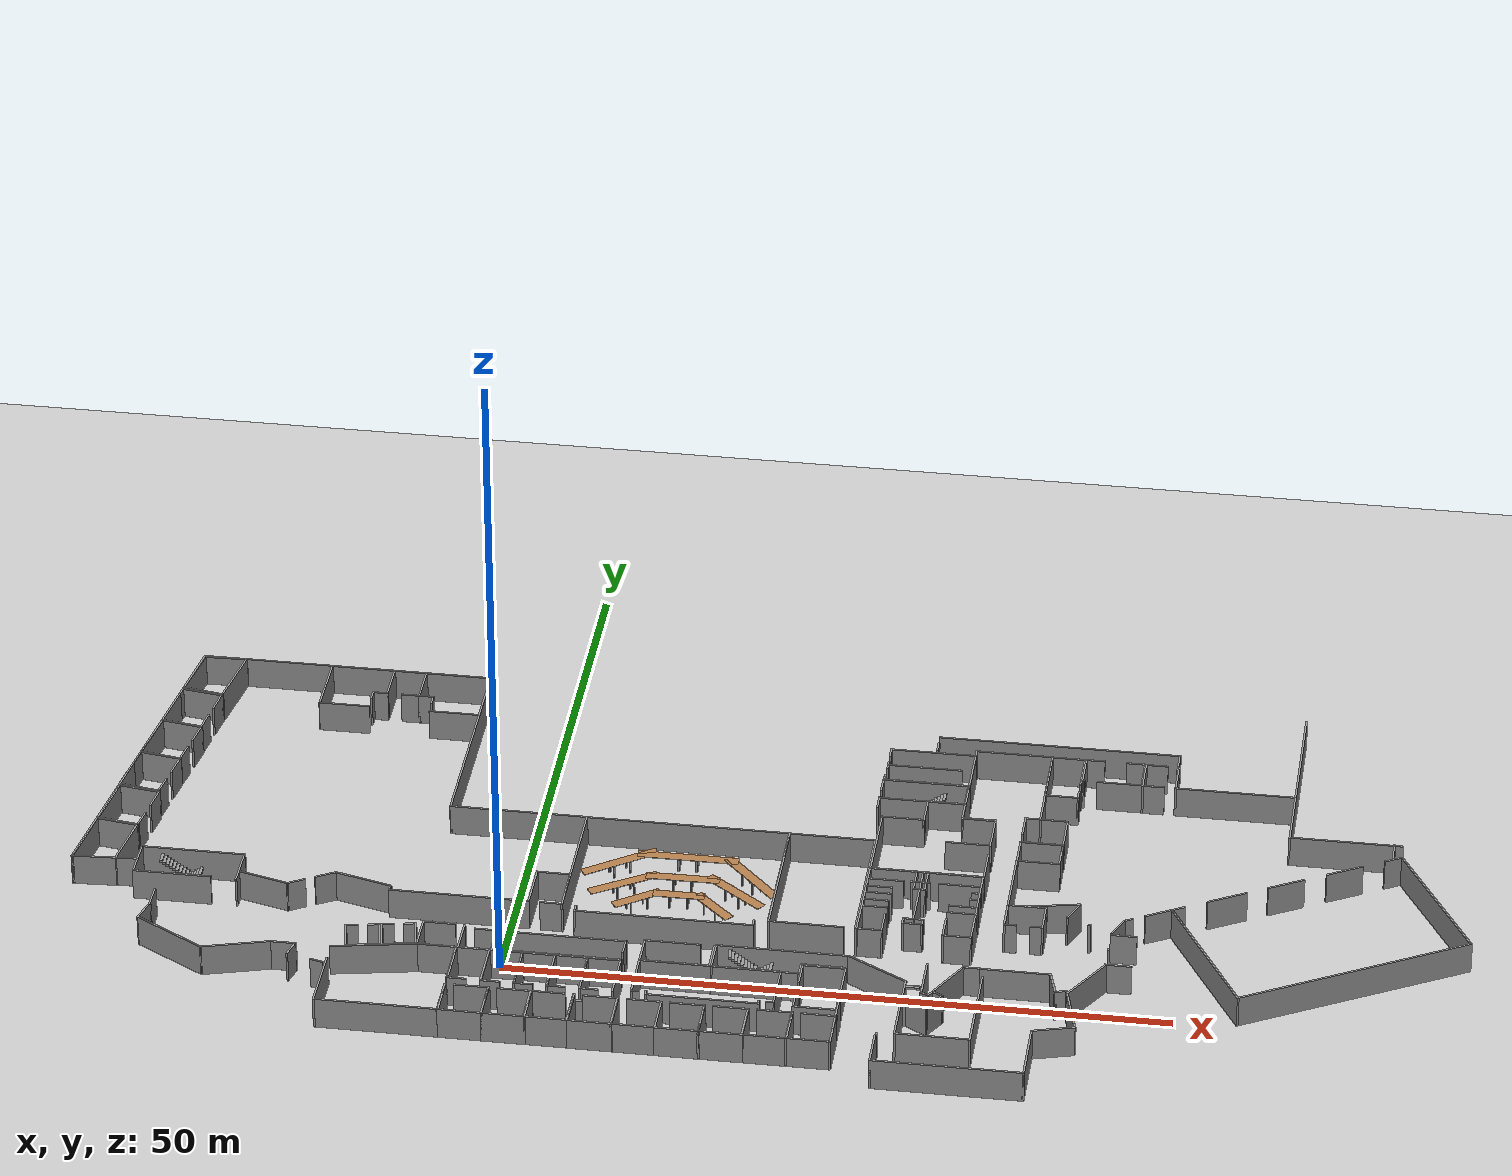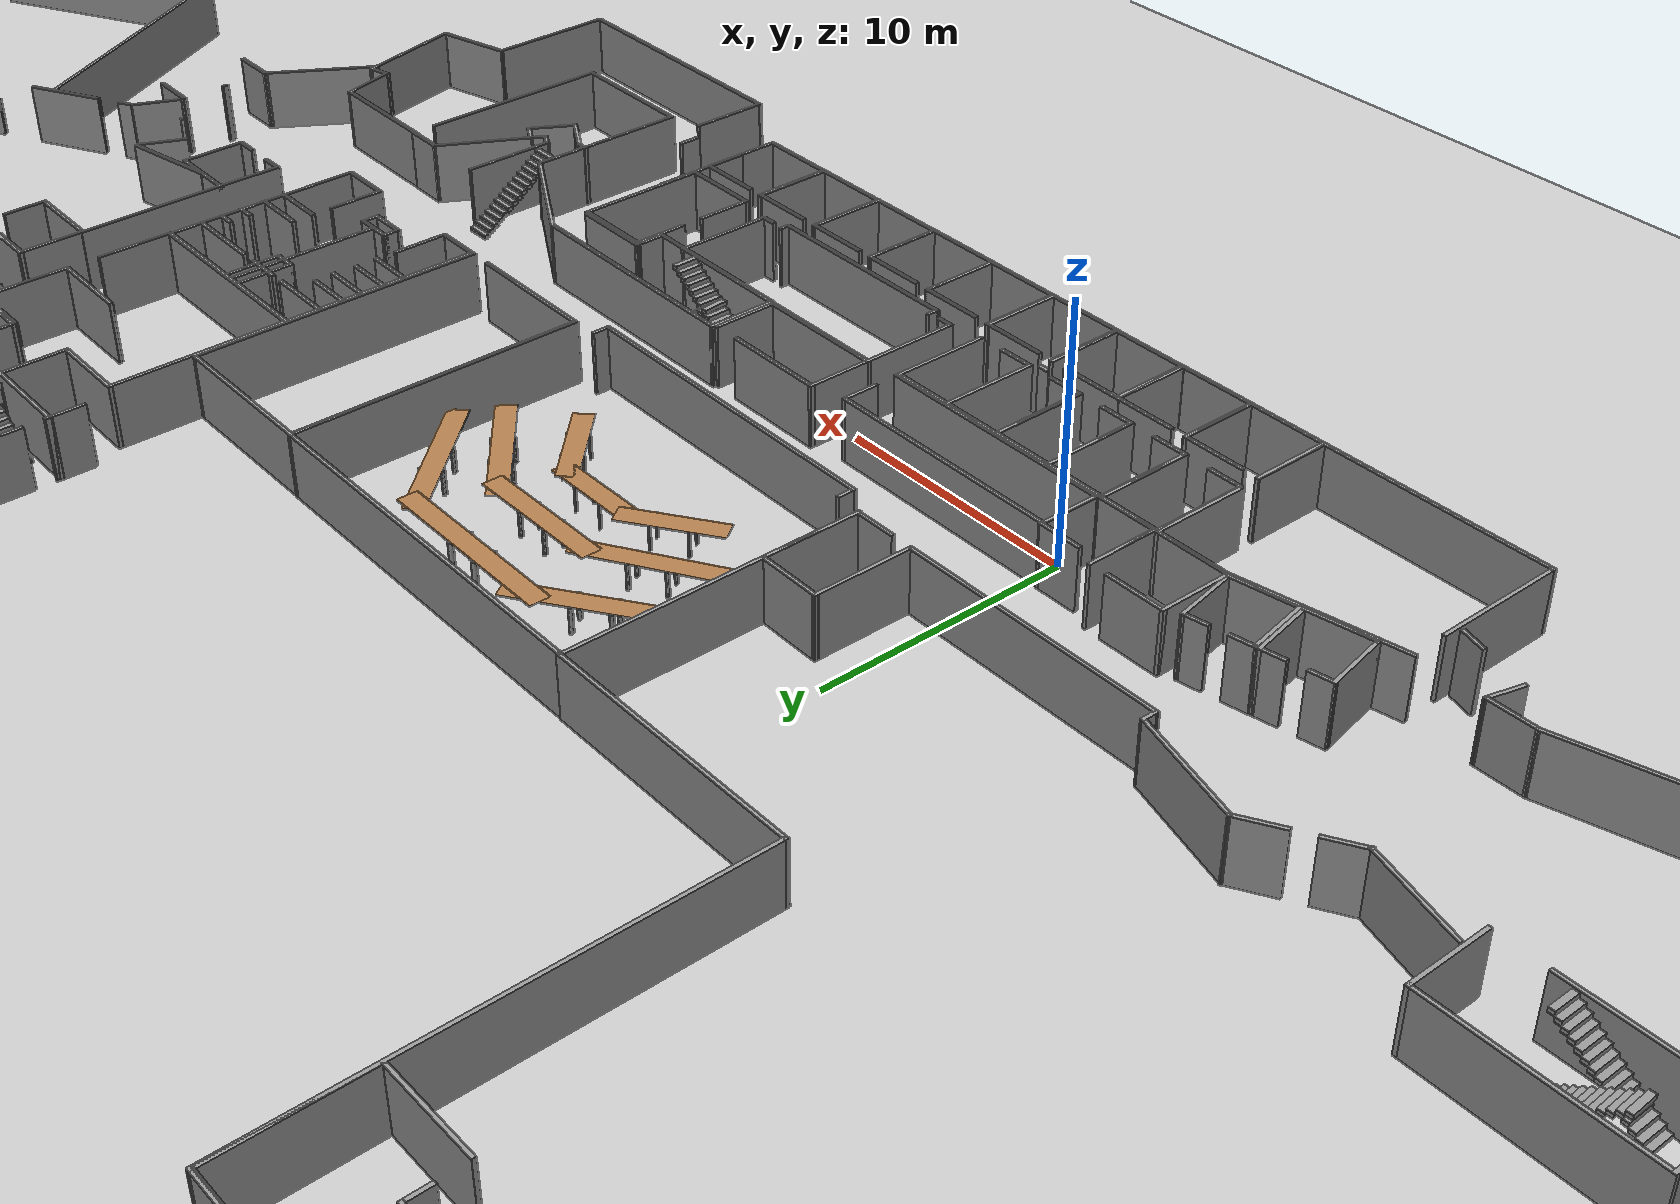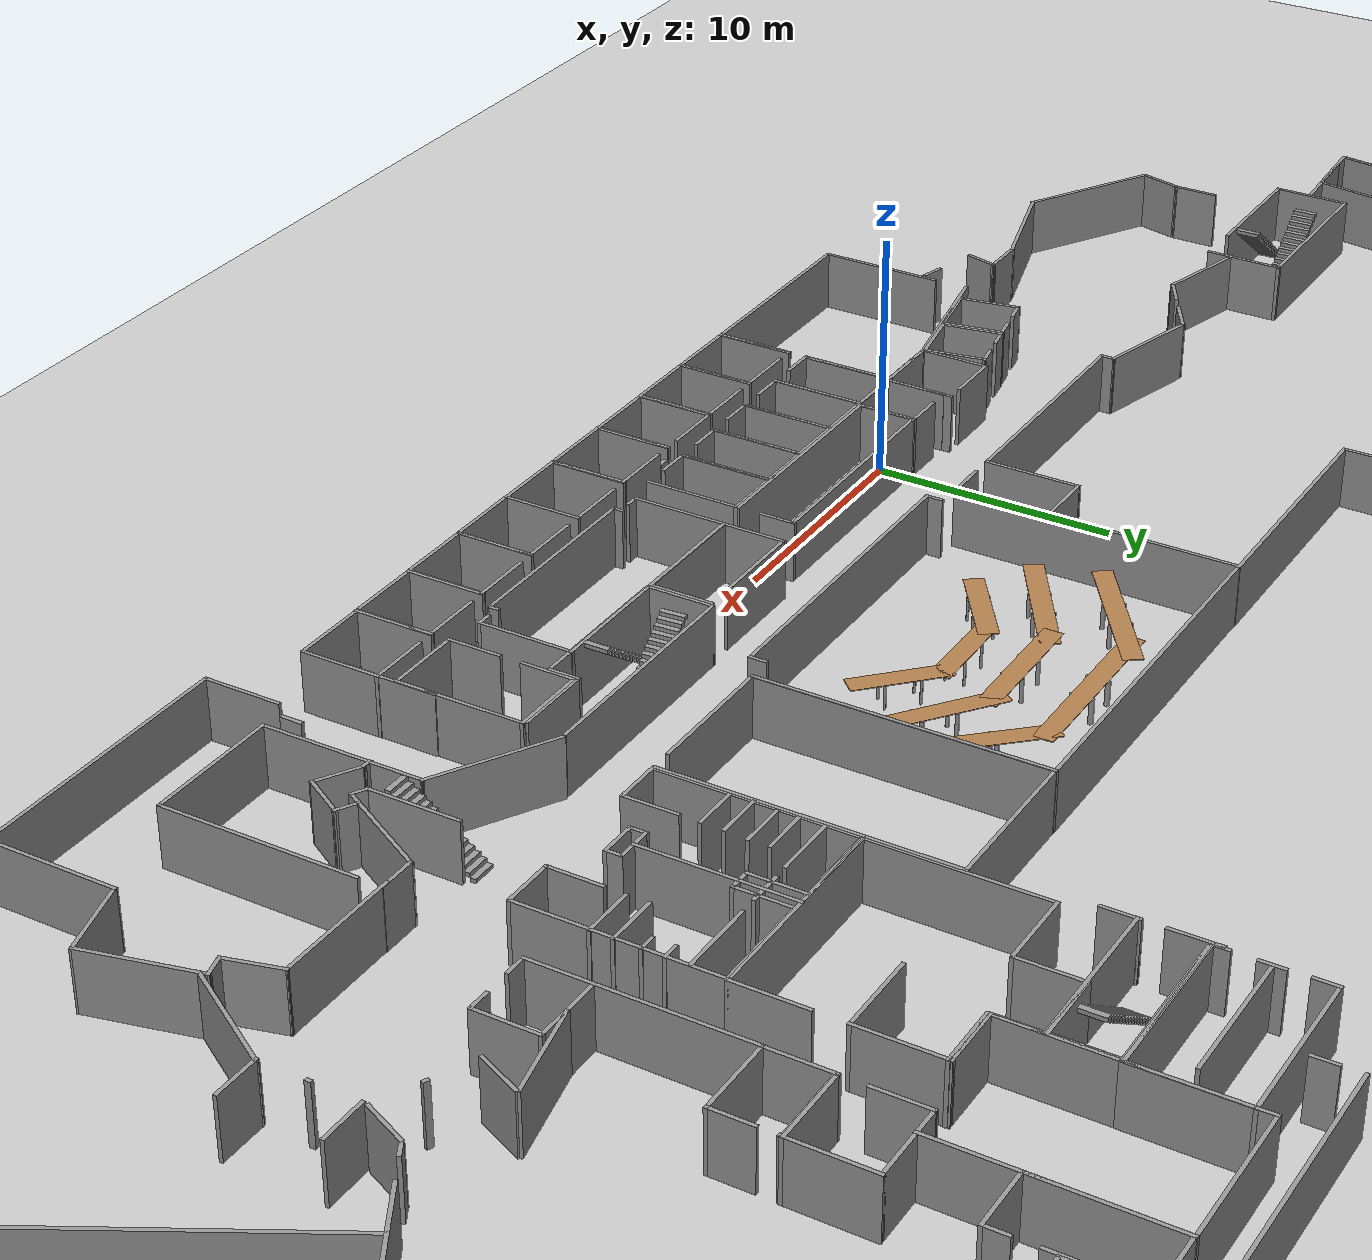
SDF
<sdf version="1.6">
 <world name="default">
  <light name="sun" type="directional">
   <pose>0 0 10 0 -0 0</pose>
   <diffuse>0.8 0.8 0.8 1</diffuse>
   <specular>0.2 0.2 0.2 1</specular>
   <attenuation>
    <range>1000</range>
    <constant>0.9</constant>
    <linear>0.01</linear>
    <quadratic>0.001</quadratic>
   </attenuation>
   <direction>-0.5 0.1 -0.9</direction>
  </light>
  <model name="ground_plane">
   <static>1</static>
   <link name="link">
    <collision name="collision">
     <geometry><plane><normal>0 0 1</normal><size>100 100</size></plane></geometry>
     <surface>
      <contact><collide_bitmask>65535</collide_bitmask></contact>
      <friction><ode><mu>100</mu><mu2>50</mu2></ode></friction>
     </surface>
    </collision>
    <visual name="visual">
     <cast_shadows>0</cast_shadows>
     <geometry><plane><normal>0 0 1</normal><size>100 100</size></plane></geometry>
     <material>
      <script><uri>file://media/materials/scripts/gazebo.material</uri><name>Gazebo/Grey</name></script>
     </material>
    </visual>
   </link>
  </model>
  <gravity>0 0 -9.8</gravity>
  <magnetic_field>6e-06 2.3e-05 -4.2e-05</magnetic_field>
  <atmosphere type="adiabatic"/>
  <physics name="default_physics" default="0" type="ode">
   <max_step_size>0.001</max_step_size>
   <real_time_factor>1</real_time_factor>
   <real_time_update_rate>1000</real_time_update_rate>
  </physics>
  <scene><ambient>0.4 0.4 0.4 1</ambient><background>0.7 0.7 0.7 1</background><shadows>1</shadows></scene>
  <spherical_coordinates>
   <surface_model>EARTH_WGS84</surface_model>
   <latitude_deg>0</latitude_deg>
   <longitude_deg>0</longitude_deg>
   <elevation>0</elevation>
   <heading_deg>0</heading_deg>
  </spherical_coordinates>
  <model name="102Main_0">
   <pose>-7.64883 -5.15367 0 0 -0 0</pose>
   <link name="Wall_10">
    <collision name="Wall_10_Collision">
     <geometry><box><size>3 0.15 2.5</size></box></geometry>
     <pose>0 0 1.25 0 -0 0</pose>
    </collision>
    <visual name="Wall_10_Visual">
     <pose>0 0 1.25 0 -0 0</pose>
     <geometry><box><size>3 0.15 2.5</size></box></geometry>
     <material>
      <script><uri>file://media/materials/scripts/gazebo.material</uri><name>Gazebo/Grey</name></script>
      <ambient>1 1 1 1</ambient>
     </material>
     <meta><layer>0</layer></meta>
    </visual>
    <pose>3.19383 3.93367 0 0 -0 3.14159</pose>
   </link>
   <link name="Wall_11">
    <collision name="Wall_11_Collision">
     <geometry><box><size>6.63844 0.15 2.5</size></box></geometry>
     <pose>0 0 1.25 0 -0 0</pose>
    </collision>
    <visual name="Wall_11_Visual">
     <pose>0 0 1.25 0 -0 0</pose>
     <geometry><box><size>6.63844 0.15 2.5</size></box></geometry>
     <material>
      <script><uri>file://media/materials/scripts/gazebo.material</uri><name>Gazebo/Grey</name></script>
      <ambient>1 1 1 1</ambient>
     </material>
     <meta><layer>0</layer></meta>
    </visual>
    <pose>-1.41867 3.32967 0 0 -0 -2.95432</pose>
   </link>
   <link name="Wall_2">
    <collision name="Wall_2_Collision">
     <geometry><box><size>4 0.15 2.5</size></box></geometry>
     <pose>0 0 1.25 0 -0 0</pose>
    </collision>
    <visual name="Wall_2_Visual">
     <pose>0 0 1.25 0 -0 0</pose>
     <geometry><box><size>4 0.15 2.5</size></box></geometry>
     <material>
      <script><uri>file://media/materials/scripts/gazebo.material</uri><name>Gazebo/Grey</name></script>
      <ambient>1 1 1 1</ambient>
     </material>
     <meta><layer>0</layer></meta>
    </visual>
    <pose>4.61883 2.00867 0 0 -0 -1.5708</pose>
   </link>
   <link name="Wall_4">
    <collision name="Wall_4_Collision">
     <geometry><box><size>3.33 0.15 2.5</size></box></geometry>
     <pose>0 0 1.25 0 -0 0</pose>
    </collision>
    <visual name="Wall_4_Visual">
     <pose>0 0 1.25 0 -0 0</pose>
     <geometry><box><size>3.33 0.15 2.5</size></box></geometry>
     <material>
      <script><uri>file://media/materials/scripts/gazebo.material</uri><name>Gazebo/Grey</name></script>
      <ambient>1 1 1 1</ambient>
     </material>
     <meta><layer>0</layer></meta>
    </visual>
    <pose>4.61883 -2.35633 0 0 -0 -1.5708</pose>
   </link>
   <link name="Wall_6">
    <collision name="Wall_6_Collision">
     <geometry><box><size>9.33 0.15 2.5</size></box></geometry>
     <pose>0 0 1.25 0 -0 0</pose>
    </collision>
    <visual name="Wall_6_Visual">
     <pose>0 0 1.25 0 -0 0</pose>
     <geometry><box><size>9.33 0.15 2.5</size></box></geometry>
     <material>
      <script><uri>file://media/materials/scripts/gazebo.material</uri><name>Gazebo/Grey</name></script>
      <ambient>1 1 1 1</ambient>
     </material>
     <meta><layer>0</layer></meta>
    </visual>
    <pose>0.028826 -3.94633 0 0 -0 3.14159</pose>
   </link>
   <link name="Wall_8">
    <collision name="Wall_8_Collision">
     <geometry><box><size>5.33 0.15 2.5</size></box></geometry>
     <pose>0 0 1.25 0 -0 0</pose>
    </collision>
    <visual name="Wall_8_Visual">
     <pose>0 0 1.25 0 -0 0</pose>
     <geometry><box><size>5.33 0.15 2.5</size></box></geometry>
     <material>
      <script><uri>file://media/materials/scripts/gazebo.material</uri><name>Gazebo/Grey</name></script>
      <ambient>1 1 1 1</ambient>
     </material>
     <meta><layer>0</layer></meta>
    </visual>
    <pose>-4.56117 -1.35633 0 0 -0 1.5708</pose>
   </link>
   <static>1</static>
  </model>
  <model name="cubicle">
   <pose>-1.75869 -3.17017 0 0 -0 0</pose>
   <link name="Wall_3">
    <collision name="Wall_3_Collision">
     <geometry><box><size>4 0.15 2.5</size></box></geometry>
     <pose>0 0 1.25 0 -0 0</pose>
    </collision>
    <visual name="Wall_3_Visual">
     <pose>0 0 1.25 0 -0 0</pose>
     <geometry><box><size>4 0.15 2.5</size></box></geometry>
     <material>
      <script><uri>file://media/materials/scripts/gazebo.material</uri><name>Gazebo/Grey</name></script>
      <ambient>1 1 1 1</ambient>
     </material>
     <meta><layer>0</layer></meta>
    </visual>
    <pose>-1.225 0 0 0 -0 -1.5708</pose>
   </link>
   <link name="Wall_4">
    <collision name="Wall_4_Collision">
     <geometry><box><size>1.5 0.15 2.5</size></box></geometry>
     <pose>0 0 1.25 0 -0 0</pose>
    </collision>
    <visual name="Wall_4_Visual">
     <pose>0 0 1.25 0 -0 0</pose>
     <geometry><box><size>1.5 0.15 2.5</size></box></geometry>
     <material>
      <script><uri>file://media/materials/scripts/gazebo.material</uri><name>Gazebo/Grey</name></script>
      <ambient>1 1 1 1</ambient>
     </material>
     <meta><layer>0</layer></meta>
    </visual>
    <pose>-0.55 -1.925 0 0 -0 0</pose>
   </link>
   <link name="Wall_6">
    <collision name="Wall_6_Collision">
     <geometry><box><size>4 0.15 2.5</size></box></geometry>
     <pose>0 0 1.25 0 -0 0</pose>
    </collision>
    <visual name="Wall_6_Visual">
     <pose>0 0 1.25 0 -0 0</pose>
     <geometry><box><size>4 0.15 2.5</size></box></geometry>
     <material>
      <script><uri>file://media/materials/scripts/gazebo.material</uri><name>Gazebo/Grey</name></script>
      <ambient>1 1 1 1</ambient>
     </material>
     <meta><layer>0</layer></meta>
    </visual>
    <pose>1.225 0 0 0 -0 1.5708</pose>
   </link>
   <link name="Wall_7">
    <collision name="Wall_7_Collision">
     <geometry><box><size>2.6 0.15 2.5</size></box></geometry>
     <pose>0 0 1.25 0 -0 0</pose>
    </collision>
    <visual name="Wall_7_Visual">
     <pose>0 0 1.25 0 -0 0</pose>
     <geometry><box><size>2.6 0.15 2.5</size></box></geometry>
     <material>
      <script><uri>file://media/materials/scripts/gazebo.material</uri><name>Gazebo/Grey</name></script>
      <ambient>1 1 1 1</ambient>
     </material>
     <meta><layer>0</layer></meta>
    </visual>
    <pose>-0 1.925 0 0 -0 3.14159</pose>
   </link>
   <static>1</static>
  </model>
  <model name="cubicle_0">
   <pose>0.7221 -3.18525 0 0 -0 0</pose>
   <link name="Wall_3">
    <collision name="Wall_3_Collision">
     <geometry><box><size>4 0.15 2.5</size></box></geometry>
     <pose>0 0 1.25 0 -0 0</pose>
    </collision>
    <visual name="Wall_3_Visual">
     <pose>0 0 1.25 0 -0 0</pose>
     <geometry><box><size>4 0.15 2.5</size></box></geometry>
     <material>
      <script><uri>file://media/materials/scripts/gazebo.material</uri><name>Gazebo/Grey</name></script>
      <ambient>1 1 1 1</ambient>
     </material>
     <meta><layer>0</layer></meta>
    </visual>
    <pose>-1.225 0 0 0 -0 -1.5708</pose>
   </link>
   <link name="Wall_4">
    <collision name="Wall_4_Collision">
     <geometry><box><size>1.5 0.15 2.5</size></box></geometry>
     <pose>0 0 1.25 0 -0 0</pose>
    </collision>
    <visual name="Wall_4_Visual">
     <pose>0 0 1.25 0 -0 0</pose>
     <geometry><box><size>1.5 0.15 2.5</size></box></geometry>
     <material>
      <script><uri>file://media/materials/scripts/gazebo.material</uri><name>Gazebo/Grey</name></script>
      <ambient>1 1 1 1</ambient>
     </material>
     <meta><layer>0</layer></meta>
    </visual>
    <pose>-0.55 -1.925 0 0 -0 0</pose>
   </link>
   <link name="Wall_6">
    <collision name="Wall_6_Collision">
     <geometry><box><size>4 0.15 2.5</size></box></geometry>
     <pose>0 0 1.25 0 -0 0</pose>
    </collision>
    <visual name="Wall_6_Visual">
     <pose>0 0 1.25 0 -0 0</pose>
     <geometry><box><size>4 0.15 2.5</size></box></geometry>
     <material>
      <script><uri>file://media/materials/scripts/gazebo.material</uri><name>Gazebo/Grey</name></script>
      <ambient>1 1 1 1</ambient>
     </material>
     <meta><layer>0</layer></meta>
    </visual>
    <pose>1.225 0 0 0 -0 1.5708</pose>
   </link>
   <link name="Wall_7">
    <collision name="Wall_7_Collision">
     <geometry><box><size>2.6 0.15 2.5</size></box></geometry>
     <pose>0 0 1.25 0 -0 0</pose>
    </collision>
    <visual name="Wall_7_Visual">
     <pose>0 0 1.25 0 -0 0</pose>
     <geometry><box><size>2.6 0.15 2.5</size></box></geometry>
     <material>
      <script><uri>file://media/materials/scripts/gazebo.material</uri><name>Gazebo/Grey</name></script>
      <ambient>1 1 1 1</ambient>
     </material>
     <meta><layer>0</layer></meta>
    </visual>
    <pose>-0 1.925 0 0 -0 3.14159</pose>
   </link>
   <static>1</static>
  </model>
  <model name="cubicle_1">
   <pose>3.16716 -3.18304 0 0 -0 0</pose>
   <link name="Wall_3">
    <collision name="Wall_3_Collision">
     <geometry><box><size>4 0.15 2.5</size></box></geometry>
     <pose>0 0 1.25 0 -0 0</pose>
    </collision>
    <visual name="Wall_3_Visual">
     <pose>0 0 1.25 0 -0 0</pose>
     <geometry><box><size>4 0.15 2.5</size></box></geometry>
     <material>
      <script><uri>file://media/materials/scripts/gazebo.material</uri><name>Gazebo/Grey</name></script>
      <ambient>1 1 1 1</ambient>
     </material>
     <meta><layer>0</layer></meta>
    </visual>
    <pose>-1.225 0 0 0 -0 -1.5708</pose>
   </link>
   <link name="Wall_4">
    <collision name="Wall_4_Collision">
     <geometry><box><size>1.5 0.15 2.5</size></box></geometry>
     <pose>0 0 1.25 0 -0 0</pose>
    </collision>
    <visual name="Wall_4_Visual">
     <pose>0 0 1.25 0 -0 0</pose>
     <geometry><box><size>1.5 0.15 2.5</size></box></geometry>
     <material>
      <script><uri>file://media/materials/scripts/gazebo.material</uri><name>Gazebo/Grey</name></script>
      <ambient>1 1 1 1</ambient>
     </material>
     <meta><layer>0</layer></meta>
    </visual>
    <pose>-0.55 -1.925 0 0 -0 0</pose>
   </link>
   <link name="Wall_6">
    <collision name="Wall_6_Collision">
     <geometry><box><size>4 0.15 2.5</size></box></geometry>
     <pose>0 0 1.25 0 -0 0</pose>
    </collision>
    <visual name="Wall_6_Visual">
     <pose>0 0 1.25 0 -0 0</pose>
     <geometry><box><size>4 0.15 2.5</size></box></geometry>
     <material>
      <script><uri>file://media/materials/scripts/gazebo.material</uri><name>Gazebo/Grey</name></script>
      <ambient>1 1 1 1</ambient>
     </material>
     <meta><layer>0</layer></meta>
    </visual>
    <pose>1.225 0 0 0 -0 1.5708</pose>
   </link>
   <link name="Wall_7">
    <collision name="Wall_7_Collision">
     <geometry><box><size>2.6 0.15 2.5</size></box></geometry>
     <pose>0 0 1.25 0 -0 0</pose>
    </collision>
    <visual name="Wall_7_Visual">
     <pose>0 0 1.25 0 -0 0</pose>
     <geometry><box><size>2.6 0.15 2.5</size></box></geometry>
     <material>
      <script><uri>file://media/materials/scripts/gazebo.material</uri><name>Gazebo/Grey</name></script>
      <ambient>1 1 1 1</ambient>
     </material>
     <meta><layer>0</layer></meta>
    </visual>
    <pose>-0 1.925 0 0 -0 3.14159</pose>
   </link>
   <static>1</static>
  </model>
  <model name="cubicle_2">
   <pose>5.59423 -3.16333 0 0 -0 0</pose>
   <link name="Wall_3">
    <collision name="Wall_3_Collision">
     <geometry><box><size>4 0.15 2.5</size></box></geometry>
     <pose>0 0 1.25 0 -0 0</pose>
    </collision>
    <visual name="Wall_3_Visual">
     <pose>0 0 1.25 0 -0 0</pose>
     <geometry><box><size>4 0.15 2.5</size></box></geometry>
     <material>
      <script><uri>file://media/materials/scripts/gazebo.material</uri><name>Gazebo/Grey</name></script>
      <ambient>1 1 1 1</ambient>
     </material>
     <meta><layer>0</layer></meta>
    </visual>
    <pose>-1.225 0 0 0 -0 -1.5708</pose>
   </link>
   <link name="Wall_4">
    <collision name="Wall_4_Collision">
     <geometry><box><size>1.5 0.15 2.5</size></box></geometry>
     <pose>0 0 1.25 0 -0 0</pose>
    </collision>
    <visual name="Wall_4_Visual">
     <pose>0 0 1.25 0 -0 0</pose>
     <geometry><box><size>1.5 0.15 2.5</size></box></geometry>
     <material>
      <script><uri>file://media/materials/scripts/gazebo.material</uri><name>Gazebo/Grey</name></script>
      <ambient>1 1 1 1</ambient>
     </material>
     <meta><layer>0</layer></meta>
    </visual>
    <pose>-0.55 -1.925 0 0 -0 0</pose>
   </link>
   <link name="Wall_6">
    <collision name="Wall_6_Collision">
     <geometry><box><size>4 0.15 2.5</size></box></geometry>
     <pose>0 0 1.25 0 -0 0</pose>
    </collision>
    <visual name="Wall_6_Visual">
     <pose>0 0 1.25 0 -0 0</pose>
     <geometry><box><size>4 0.15 2.5</size></box></geometry>
     <material>
      <script><uri>file://media/materials/scripts/gazebo.material</uri><name>Gazebo/Grey</name></script>
      <ambient>1 1 1 1</ambient>
     </material>
     <meta><layer>0</layer></meta>
    </visual>
    <pose>1.225 0 0 0 -0 1.5708</pose>
   </link>
   <link name="Wall_7">
    <collision name="Wall_7_Collision">
     <geometry><box><size>2.6 0.15 2.5</size></box></geometry>
     <pose>0 0 1.25 0 -0 0</pose>
    </collision>
    <visual name="Wall_7_Visual">
     <pose>0 0 1.25 0 -0 0</pose>
     <geometry><box><size>2.6 0.15 2.5</size></box></geometry>
     <material>
      <script><uri>file://media/materials/scripts/gazebo.material</uri><name>Gazebo/Grey</name></script>
      <ambient>1 1 1 1</ambient>
     </material>
     <meta><layer>0</layer></meta>
    </visual>
    <pose>-0 1.925 0 0 -0 3.14159</pose>
   </link>
   <static>1</static>
  </model>
  <model name="cubicle_3">
   <pose>8.03874 -3.16109 0 0 -0 0</pose>
   <link name="Wall_3">
    <collision name="Wall_3_Collision">
     <geometry><box><size>4 0.15 2.5</size></box></geometry>
     <pose>0 0 1.25 0 -0 0</pose>
    </collision>
    <visual name="Wall_3_Visual">
     <pose>0 0 1.25 0 -0 0</pose>
     <geometry><box><size>4 0.15 2.5</size></box></geometry>
     <material>
      <script><uri>file://media/materials/scripts/gazebo.material</uri><name>Gazebo/Grey</name></script>
      <ambient>1 1 1 1</ambient>
     </material>
     <meta><layer>0</layer></meta>
    </visual>
    <pose>-1.225 0 0 0 -0 -1.5708</pose>
   </link>
   <link name="Wall_4">
    <collision name="Wall_4_Collision">
     <geometry><box><size>1.5 0.15 2.5</size></box></geometry>
     <pose>0 0 1.25 0 -0 0</pose>
    </collision>
    <visual name="Wall_4_Visual">
     <pose>0 0 1.25 0 -0 0</pose>
     <geometry><box><size>1.5 0.15 2.5</size></box></geometry>
     <material>
      <script><uri>file://media/materials/scripts/gazebo.material</uri><name>Gazebo/Grey</name></script>
      <ambient>1 1 1 1</ambient>
     </material>
     <meta><layer>0</layer></meta>
    </visual>
    <pose>-0.55 -1.925 0 0 -0 0</pose>
   </link>
   <link name="Wall_6">
    <collision name="Wall_6_Collision">
     <geometry><box><size>4 0.15 2.5</size></box></geometry>
     <pose>0 0 1.25 0 -0 0</pose>
    </collision>
    <visual name="Wall_6_Visual">
     <pose>0 0 1.25 0 -0 0</pose>
     <geometry><box><size>4 0.15 2.5</size></box></geometry>
     <material>
      <script><uri>file://media/materials/scripts/gazebo.material</uri><name>Gazebo/Grey</name></script>
      <ambient>1 1 1 1</ambient>
     </material>
     <meta><layer>0</layer></meta>
    </visual>
    <pose>1.225 0 0 0 -0 1.5708</pose>
   </link>
   <link name="Wall_7">
    <collision name="Wall_7_Collision">
     <geometry><box><size>2.6 0.15 2.5</size></box></geometry>
     <pose>0 0 1.25 0 -0 0</pose>
    </collision>
    <visual name="Wall_7_Visual">
     <pose>0 0 1.25 0 -0 0</pose>
     <geometry><box><size>2.6 0.15 2.5</size></box></geometry>
     <material>
      <script><uri>file://media/materials/scripts/gazebo.material</uri><name>Gazebo/Grey</name></script>
      <ambient>1 1 1 1</ambient>
     </material>
     <meta><layer>0</layer></meta>
    </visual>
    <pose>-0 1.925 0 0 -0 3.14159</pose>
   </link>
   <static>1</static>
  </model>
  <model name="102Office_3">
   <pose>8.17012 -7.51834 0 0 -0 0</pose>
   <link name="Door_0">
    <collision name="Door_0_Collision">
     <geometry><box><size>0.517842 0.2 2</size></box></geometry>
     <pose>0 0 1 0 -0 0</pose>
    </collision>
    <visual name="Door_0_Visual">
     <pose>0 0 1 0 -0 0</pose>
     <geometry><box><size>0.517842 0.2 2</size></box></geometry>
     <material>
      <script><uri>file://media/materials/scripts/gazebo.material</uri><name>Gazebo/Grey</name></script>
     </material>
    </visual>
    <pose>-1.26918 1.57689 0 0 -0 0</pose>
   </link>
   <link name="Wall_13">
    <collision name="Wall_13_Collision">
     <geometry><box><size>3.334 0.15 2.5</size></box></geometry>
     <pose>0 0 1.25 0 -0 0</pose>
    </collision>
    <visual name="Wall_13_Visual">
     <pose>0 0 1.25 0 -0 0</pose>
     <geometry><box><size>3.334 0.15 2.5</size></box></geometry>
     <material>
      <script><uri>file://media/materials/scripts/gazebo.material</uri><name>Gazebo/Grey</name></script>
      <ambient>1 1 1 1</ambient>
     </material>
     <meta><layer>0</layer></meta>
    </visual>
    <pose>-0 -1.592 0 0 -0 0</pose>
   </link>
   <link name="Wall_15">
    <collision name="Wall_15_Collision">
     <geometry><box><size>3.334 0.15 2.5</size></box></geometry>
     <pose>0 0 1.25 0 -0 0</pose>
    </collision>
    <visual name="Wall_15_Visual">
     <pose>0 0 1.25 0 -0 0</pose>
     <geometry><box><size>3.334 0.15 2.5</size></box></geometry>
     <material>
      <script><uri>file://media/materials/scripts/gazebo.material</uri><name>Gazebo/Grey</name></script>
      <ambient>1 1 1 1</ambient>
     </material>
     <meta><layer>0</layer></meta>
    </visual>
    <pose>-1.592 0 0 0 -0 1.5708</pose>
   </link>
   <link name="Wall_17">
    <collision name="Wall_17_Collision">
     <geometry><box><size>3.334 0.15 2.5</size></box></geometry>
     <pose>0 0 1.25 0 -0 0</pose>
    </collision>
    <visual name="Wall_17_Visual">
     <pose>0 0 1.25 0 -0 0</pose>
     <geometry><box><size>3.334 0.15 2.5</size></box></geometry>
     <material>
      <script><uri>file://media/materials/scripts/gazebo.material</uri><name>Gazebo/Grey</name></script>
      <ambient>1 1 1 1</ambient>
     </material>
     <meta><layer>0</layer></meta>
    </visual>
    <pose>1.592 0 0 0 -0 1.5708</pose>
   </link>
   <link name="Wall_19">
    <collision name="Wall_19_Collision">
     <geometry><box><size>2.667 0.15 2.5</size></box></geometry>
     <pose>0 0 1.25 0 -0 0</pose>
    </collision>
    <visual name="Wall_19_Visual">
     <pose>0 0 1.25 0 -0 0</pose>
     <geometry><box><size>2.667 0.15 2.5</size></box></geometry>
     <material>
      <script><uri>file://media/materials/scripts/gazebo.material</uri><name>Gazebo/Grey</name></script>
      <ambient>1 1 1 1</ambient>
     </material>
     <meta><layer>0</layer></meta>
    </visual>
    <pose>0.3335 1.592 0 0 -0 3.14159</pose>
   </link>
   <static>1</static>
  </model>
  <model name="102Room">
   <pose>15.8772 -3.07536 0 0 -0 0</pose>
   <link name="Wall_11">
    <collision name="Wall_11_Collision">
     <geometry><box><size>8.5 0.15 2.5</size></box></geometry>
     <pose>0 0 1.25 0 -0 0</pose>
    </collision>
    <visual name="Wall_11_Visual">
     <pose>0 0 1.25 0 -0 0</pose>
     <geometry><box><size>8.5 0.15 2.5</size></box></geometry>
     <material>
      <script><uri>file://media/materials/scripts/gazebo.material</uri><name>Gazebo/Grey</name></script>
      <ambient>1 1 1 1</ambient>
     </material>
     <meta><layer>0</layer></meta>
    </visual>
    <pose>-0.003989 -2.07244 0 0 -0 0</pose>
   </link>
   <link name="Wall_13">
    <collision name="Wall_13_Collision">
     <geometry><box><size>0.667 0.15 2.5</size></box></geometry>
     <pose>0 0 1.25 0 -0 0</pose>
    </collision>
    <visual name="Wall_13_Visual">
     <pose>0 0 1.25 0 -0 0</pose>
     <geometry><box><size>0.667 0.15 2.5</size></box></geometry>
     <material>
      <script><uri>file://media/materials/scripts/gazebo.material</uri><name>Gazebo/Grey</name></script>
      <ambient>1 1 1 1</ambient>
     </material>
     <meta><layer>0</layer></meta>
    </visual>
    <pose>4.99225 -1.76994 0 0 -0 0</pose>
   </link>
   <link name="Wall_15">
    <collision name="Wall_15_Collision">
     <geometry><box><size>4 0.15 2.5</size></box></geometry>
     <pose>0 0 1.25 0 -0 0</pose>
    </collision>
    <visual name="Wall_15_Visual">
     <pose>0 0 1.25 0 -0 0</pose>
     <geometry><box><size>4 0.15 2.5</size></box></geometry>
     <material>
      <script><uri>file://media/materials/scripts/gazebo.material</uri><name>Gazebo/Grey</name></script>
      <ambient>1 1 1 1</ambient>
     </material>
     <meta><layer>0</layer></meta>
    </visual>
    <pose>5.25087 0.155063 0 0 -0 1.57073</pose>
   </link>
   <link name="Wall_16">
    <collision name="Wall_16_Collision">
     <geometry><box><size>10.652 0.15 2.5</size></box></geometry>
     <pose>0 0 1.25 0 -0 0</pose>
    </collision>
    <visual name="Wall_16_Visual">
     <pose>0 0 1.25 0 -0 0</pose>
     <geometry><box><size>10.652 0.15 2.5</size></box></geometry>
     <material>
      <script><uri>file://media/materials/scripts/gazebo.material</uri><name>Gazebo/Grey</name></script>
      <ambient>1 1 1 1</ambient>
     </material>
     <meta><layer>0</layer></meta>
    </visual>
    <pose>-2e-06 2.08006 0 0 -0 3.14159</pose>
   </link>
   <link name="Wall_17">
    <collision name="Wall_17_Collision">
     <geometry><box><size>4 0.15 2.5</size></box></geometry>
     <pose>0 0 1.25 0 -0 0</pose>
    </collision>
    <visual name="Wall_17_Visual">
     <pose>0 0 1.25 0 -0 0</pose>
     <geometry><box><size>4 0.15 2.5</size></box></geometry>
     <material>
      <script><uri>file://media/materials/scripts/gazebo.material</uri><name>Gazebo/Grey</name></script>
      <ambient>1 1 1 1</ambient>
     </material>
     <meta><layer>0</layer></meta>
    </visual>
    <pose>-5.251 0.155063 0 0 -0 -1.5708</pose>
   </link>
   <link name="Wall_23">
    <collision name="Wall_23_Collision">
     <geometry><box><size>0.5 0.15 2.5</size></box></geometry>
     <pose>0 0 1.25 0 -0 0</pose>
    </collision>
    <visual name="Wall_23_Visual">
     <pose>0 0 1.25 0 -0 0</pose>
     <geometry><box><size>0.5 0.15 2.5</size></box></geometry>
     <material>
      <script><uri>file://media/materials/scripts/gazebo.material</uri><name>Gazebo/Grey</name></script>
      <ambient>1 1 1 1</ambient>
     </material>
     <meta><layer>0</layer></meta>
    </visual>
    <pose>-4.17899 -1.90507 0 0 -0 1.5708</pose>
   </link>
   <link name="Wall_25">
    <collision name="Wall_25_Collision">
     <geometry><box><size>0.469506 0.15 2.5</size></box></geometry>
     <pose>0 0 1.25 0 -0 0</pose>
    </collision>
    <visual name="Wall_25_Visual">
     <pose>0 0 1.25 0 -0 0</pose>
     <geometry><box><size>0.469506 0.15 2.5</size></box></geometry>
     <material>
      <script><uri>file://media/materials/scripts/gazebo.material</uri><name>Gazebo/Grey</name></script>
      <ambient>1 1 1 1</ambient>
     </material>
     <meta><layer>0</layer></meta>
    </visual>
    <pose>4.17101 -1.90507 0 0 -0 1.5708</pose>
   </link>
   <link name="Wall_9">
    <collision name="Wall_9_Collision">
     <geometry><box><size>0.667 0.15 2.5</size></box></geometry>
     <pose>0 0 1.25 0 -0 0</pose>
    </collision>
    <visual name="Wall_9_Visual">
     <pose>0 0 1.25 0 -0 0</pose>
     <geometry><box><size>0.667 0.15 2.5</size></box></geometry>
     <material>
      <script><uri>file://media/materials/scripts/gazebo.material</uri><name>Gazebo/Grey</name></script>
      <ambient>1 1 1 1</ambient>
     </material>
     <meta><layer>0</layer></meta>
    </visual>
    <pose>-4.9925 -1.76994 0 0 -0 0</pose>
   </link>
   <static>1</static>
  </model>
  <model name="4m_wall">
   <pose>25.8395 -5.4603 0 0 -0 0</pose>
   <link name="Wall_0">
    <collision name="Wall_0_Collision">
     <geometry><box><size>4 0.15 2.5</size></box></geometry>
     <pose>0 0 1.25 0 -0 0</pose>
    </collision>
    <visual name="Wall_0_Visual">
     <pose>0 0 1.25 0 -0 0</pose>
     <geometry><box><size>4 0.15 2.5</size></box></geometry>
     <material>
      <script><uri>file://media/materials/scripts/gazebo.material</uri><name>Gazebo/Grey</name></script>
      <ambient>1 1 1 1</ambient>
     </material>
     <meta><layer>0</layer></meta>
    </visual>
    <pose>0 -0 0 0 -0 1.5708</pose>
   </link>
   <static>1</static>
  </model>
  <model name="195">
   <pose>-10.1492 -0.660141 0 0 -0 0.184616</pose>
   <link name="Wall_52">
    <collision name="Wall_52_Collision">
     <geometry><box><size>2.667 0.15 2.5</size></box></geometry>
     <pose>0 0 1.25 0 -0 0</pose>
    </collision>
    <visual name="Wall_52_Visual">
     <pose>0 0 1.25 0 -0 0</pose>
     <geometry><box><size>2.667 0.15 2.5</size></box></geometry>
     <material>
      <script><uri>file://media/materials/scripts/gazebo.material</uri><name>Gazebo/Grey</name></script>
      <ambient>1 1 1 1</ambient>
     </material>
     <meta><layer>0</layer></meta>
    </visual>
    <pose>-0.000138 -1.2585 0 0 -0 0</pose>
   </link>
   <link name="Wall_53">
    <collision name="Wall_53_Collision">
     <geometry><box><size>2.667 0.15 2.5</size></box></geometry>
     <pose>0 0 1.25 0 -0 0</pose>
    </collision>
    <visual name="Wall_53_Visual">
     <pose>0 0 1.25 0 -0 0</pose>
     <geometry><box><size>2.667 0.15 2.5</size></box></geometry>
     <material>
      <script><uri>file://media/materials/scripts/gazebo.material</uri><name>Gazebo/Grey</name></script>
      <ambient>1 1 1 1</ambient>
     </material>
     <meta><layer>0</layer></meta>
    </visual>
    <pose>1.2585 0 0 0 -0 1.57069</pose>
   </link>
   <link name="Wall_55">
    <collision name="Wall_55_Collision">
     <geometry><box><size>2.667 0.15 2.5</size></box></geometry>
     <pose>0 0 1.25 0 -0 0</pose>
    </collision>
    <visual name="Wall_55_Visual">
     <pose>0 0 1.25 0 -0 0</pose>
     <geometry><box><size>2.667 0.15 2.5</size></box></geometry>
     <material>
      <script><uri>file://media/materials/scripts/gazebo.material</uri><name>Gazebo/Grey</name></script>
      <ambient>1 1 1 1</ambient>
     </material>
     <meta><layer>0</layer></meta>
    </visual>
    <pose>-1.2585 0 0 0 -0 -1.57091</pose>
   </link>
   <link name="Wall_57">
    <collision name="Wall_57_Collision">
     <geometry><box><size>1 0.15 2.5</size></box></geometry>
     <pose>0 0 1.25 0 -0 0</pose>
    </collision>
    <visual name="Wall_57_Visual">
     <pose>0 0 1.25 0 -0 0</pose>
     <geometry><box><size>1 0.15 2.5</size></box></geometry>
     <material>
      <script><uri>file://media/materials/scripts/gazebo.material</uri><name>Gazebo/Grey</name></script>
      <ambient>1 1 1 1</ambient>
     </material>
     <meta><layer>0</layer></meta>
    </visual>
    <pose>0.833639 1.2585 0 0 -0 3.14159</pose>
   </link>
   <link name="Wall_59">
    <collision name="Wall_59_Collision">
     <geometry><box><size>1 0.15 2.5</size></box></geometry>
     <pose>0 0 1.25 0 -0 0</pose>
    </collision>
    <visual name="Wall_59_Visual">
     <pose>0 0 1.25 0 -0 0</pose>
     <geometry><box><size>1 0.15 2.5</size></box></geometry>
     <material>
      <script><uri>file://media/materials/scripts/gazebo.material</uri><name>Gazebo/Grey</name></script>
      <ambient>1 1 1 1</ambient>
     </material>
     <meta><layer>0</layer></meta>
    </visual>
    <pose>-0.833361 1.2585 0 0 -0 3.14159</pose>
   </link>
   <static>1</static>
  </model>
  <model name="195_0">
   <pose>-7.52738 -0.162435 0 0 -0 0.178379</pose>
   <link name="Wall_52">
    <collision name="Wall_52_Collision">
     <geometry><box><size>2.667 0.15 2.5</size></box></geometry>
     <pose>0 0 1.25 0 -0 0</pose>
    </collision>
    <visual name="Wall_52_Visual">
     <pose>0 0 1.25 0 -0 0</pose>
     <geometry><box><size>2.667 0.15 2.5</size></box></geometry>
     <material>
      <script><uri>file://media/materials/scripts/gazebo.material</uri><name>Gazebo/Grey</name></script>
      <ambient>1 1 1 1</ambient>
     </material>
     <meta><layer>0</layer></meta>
    </visual>
    <pose>-0.000138 -1.2585 0 0 -0 0</pose>
   </link>
   <link name="Wall_53">
    <collision name="Wall_53_Collision">
     <geometry><box><size>2.667 0.15 2.5</size></box></geometry>
     <pose>0 0 1.25 0 -0 0</pose>
    </collision>
    <visual name="Wall_53_Visual">
     <pose>0 0 1.25 0 -0 0</pose>
     <geometry><box><size>2.667 0.15 2.5</size></box></geometry>
     <material>
      <script><uri>file://media/materials/scripts/gazebo.material</uri><name>Gazebo/Grey</name></script>
      <ambient>1 1 1 1</ambient>
     </material>
     <meta><layer>0</layer></meta>
    </visual>
    <pose>1.2585 0 0 0 -0 1.57069</pose>
   </link>
   <link name="Wall_55">
    <collision name="Wall_55_Collision">
     <geometry><box><size>2.667 0.15 2.5</size></box></geometry>
     <pose>0 0 1.25 0 -0 0</pose>
    </collision>
    <visual name="Wall_55_Visual">
     <pose>0 0 1.25 0 -0 0</pose>
     <geometry><box><size>2.667 0.15 2.5</size></box></geometry>
     <material>
      <script><uri>file://media/materials/scripts/gazebo.material</uri><name>Gazebo/Grey</name></script>
      <ambient>1 1 1 1</ambient>
     </material>
     <meta><layer>0</layer></meta>
    </visual>
    <pose>-1.2585 0 0 0 -0 -1.57091</pose>
   </link>
   <link name="Wall_57">
    <collision name="Wall_57_Collision">
     <geometry><box><size>1 0.15 2.5</size></box></geometry>
     <pose>0 0 1.25 0 -0 0</pose>
    </collision>
    <visual name="Wall_57_Visual">
     <pose>0 0 1.25 0 -0 0</pose>
     <geometry><box><size>1 0.15 2.5</size></box></geometry>
     <material>
      <script><uri>file://media/materials/scripts/gazebo.material</uri><name>Gazebo/Grey</name></script>
      <ambient>1 1 1 1</ambient>
     </material>
     <meta><layer>0</layer></meta>
    </visual>
    <pose>0.833639 1.2585 0 0 -0 3.14159</pose>
   </link>
   <link name="Wall_59">
    <collision name="Wall_59_Collision">
     <geometry><box><size>1 0.15 2.5</size></box></geometry>
     <pose>0 0 1.25 0 -0 0</pose>
    </collision>
    <visual name="Wall_59_Visual">
     <pose>0 0 1.25 0 -0 0</pose>
     <geometry><box><size>1 0.15 2.5</size></box></geometry>
     <material>
      <script><uri>file://media/materials/scripts/gazebo.material</uri><name>Gazebo/Grey</name></script>
      <ambient>1 1 1 1</ambient>
     </material>
     <meta><layer>0</layer></meta>
    </visual>
    <pose>-0.833361 1.2585 0 0 -0 3.14159</pose>
   </link>
   <static>1</static>
  </model>
  <model name="106">
   <pose>11.5722 10.6693 0 0 -0 0</pose>
   <link name="Wall_79">
    <collision name="Wall_79_Collision">
     <geometry><box><size>11.668 0.15 2.5</size></box></geometry>
     <pose>0 0 1.25 0 -0 0</pose>
    </collision>
    <visual name="Wall_79_Visual">
     <pose>0 0 1.25 0 -0 0</pose>
     <geometry><box><size>11.668 0.15 2.5</size></box></geometry>
     <material>
      <script><uri>file://media/materials/scripts/gazebo.material</uri><name>Gazebo/Grey</name></script>
      <ambient>1 1 1 1</ambient>
     </material>
     <meta><layer>0</layer></meta>
    </visual>
    <pose>7.759 0.349998 0 0 -0 1.5708</pose>
   </link>
   <link name="Wall_80">
    <collision name="Wall_80_Collision">
     <geometry><box><size>15.668 0.15 2.5</size></box></geometry>
     <pose>0 0 1.25 0 -0 0</pose>
    </collision>
    <visual name="Wall_80_Visual">
     <pose>0 0 1.25 0 -0 0</pose>
     <geometry><box><size>15.668 0.15 2.5</size></box></geometry>
     <material>
      <script><uri>file://media/materials/scripts/gazebo.material</uri><name>Gazebo/Grey</name></script>
      <ambient>1 1 1 1</ambient>
     </material>
     <meta><layer>0</layer></meta>
    </visual>
    <pose>1e-06 6.109 0 0 -0 3.14159</pose>
   </link>
   <link name="Wall_81">
    <collision name="Wall_81_Collision">
     <geometry><box><size>11.668 0.15 2.5</size></box></geometry>
     <pose>0 0 1.25 0 -0 0</pose>
    </collision>
    <visual name="Wall_81_Visual">
     <pose>0 0 1.25 0 -0 0</pose>
     <geometry><box><size>11.668 0.15 2.5</size></box></geometry>
     <material>
      <script><uri>file://media/materials/scripts/gazebo.material</uri><name>Gazebo/Grey</name></script>
      <ambient>1 1 1 1</ambient>
     </material>
     <meta><layer>0</layer></meta>
    </visual>
    <pose>-7.75877 0.349984 0 0 -0 -1.57076</pose>
   </link>
   <link name="Wall_84">
    <collision name="Wall_84_Collision">
     <geometry><box><size>13.532 0.15 2.5</size></box></geometry>
     <pose>0 0 1.25 0 -0 0</pose>
    </collision>
    <visual name="Wall_84_Visual">
     <pose>0 0 1.25 0 -0 0</pose>
     <geometry><box><size>13.532 0.15 2.5</size></box></geometry>
     <material>
      <script><uri>file://media/materials/scripts/gazebo.material</uri><name>Gazebo/Grey</name></script>
      <ambient>1 1 1 1</ambient>
     </material>
     <meta><layer>0</layer></meta>
    </visual>
    <pose>1e-06 -6.109 0 0 -0 0</pose>
   </link>
   <link name="Wall_87">
    <collision name="Wall_87_Collision">
     <geometry><box><size>0.75 0.15 2.5</size></box></geometry>
     <pose>0 0 1.25 0 -0 0</pose>
    </collision>
    <visual name="Wall_87_Visual">
     <pose>0 0 1.25 0 -0 0</pose>
     <geometry><box><size>0.75 0.15 2.5</size></box></geometry>
     <material>
      <script><uri>file://media/materials/scripts/gazebo.material</uri><name>Gazebo/Grey</name></script>
      <ambient>1 1 1 1</ambient>
     </material>
     <meta><layer>0</layer></meta>
    </visual>
    <pose>-6.691 -5.809 0 0 -0 1.5708</pose>
   </link>
   <link name="Wall_89">
    <collision name="Wall_89_Collision">
     <geometry><box><size>0.75 0.15 2.5</size></box></geometry>
     <pose>0 0 1.25 0 -0 0</pose>
    </collision>
    <visual name="Wall_89_Visual">
     <pose>0 0 1.25 0 -0 0</pose>
     <geometry><box><size>0.75 0.15 2.5</size></box></geometry>
     <material>
      <script><uri>file://media/materials/scripts/gazebo.material</uri><name>Gazebo/Grey</name></script>
      <ambient>1 1 1 1</ambient>
     </material>
     <meta><layer>0</layer></meta>
    </visual>
    <pose>6.691 -5.809 0 0 -0 1.5708</pose>
   </link>
   <static>1</static>
  </model>
  <model name="104_0">
   <pose>-1.62055 0.02289 0 0 -0 0</pose>
   <link name="Wall_11">
    <collision name="Wall_11_Collision">
     <geometry><box><size>2.667 0.15 2.5</size></box></geometry>
     <pose>0 0 1.25 0 -0 0</pose>
    </collision>
    <visual name="Wall_11_Visual">
     <pose>0 0 1.25 0 -0 0</pose>
     <geometry><box><size>2.667 0.15 2.5</size></box></geometry>
     <material>
      <script><uri>file://media/materials/scripts/gazebo.material</uri><name>Gazebo/Grey</name></script>
      <ambient>1 1 1 1</ambient>
     </material>
     <meta><layer>0</layer></meta>
    </visual>
    <pose>0 -1.23537 0 0 -0 0</pose>
   </link>
   <link name="Wall_12">
    <collision name="Wall_12_Collision">
     <geometry><box><size>2.62074 0.15 2.5</size></box></geometry>
     <pose>0 0 1.25 0 -0 0</pose>
    </collision>
    <visual name="Wall_12_Visual">
     <pose>0 0 1.25 0 -0 0</pose>
     <geometry><box><size>2.62074 0.15 2.5</size></box></geometry>
     <material>
      <script><uri>file://media/materials/scripts/gazebo.material</uri><name>Gazebo/Grey</name></script>
      <ambient>1 1 1 1</ambient>
     </material>
     <meta><layer>0</layer></meta>
    </visual>
    <pose>1.2585 0 0 0 -0 1.5708</pose>
   </link>
   <link name="Wall_14">
    <collision name="Wall_14_Collision">
     <geometry><box><size>2.62074 0.15 2.5</size></box></geometry>
     <pose>0 0 1.25 0 -0 0</pose>
    </collision>
    <visual name="Wall_14_Visual">
     <pose>0 0 1.25 0 -0 0</pose>
     <geometry><box><size>2.62074 0.15 2.5</size></box></geometry>
     <material>
      <script><uri>file://media/materials/scripts/gazebo.material</uri><name>Gazebo/Grey</name></script>
      <ambient>1 1 1 1</ambient>
     </material>
     <meta><layer>0</layer></meta>
    </visual>
    <pose>-1.2585 0 0 0 -0 -1.5708</pose>
   </link>
   <link name="Wall_18">
    <collision name="Wall_18_Collision">
     <geometry><box><size>1.8 0.15 2.5</size></box></geometry>
     <pose>0 0 1.25 0 -0 0</pose>
    </collision>
    <visual name="Wall_18_Visual">
     <pose>0 0 1.25 0 -0 0</pose>
     <geometry><box><size>1.8 0.15 2.5</size></box></geometry>
     <material>
      <script><uri>file://media/materials/scripts/gazebo.material</uri><name>Gazebo/Grey</name></script>
      <ambient>1 1 1 1</ambient>
     </material>
     <meta><layer>0</layer></meta>
    </visual>
    <pose>0.433499 1.23537 0 0 -0 3.14159</pose>
   </link>
   <static>1</static>
  </model>
  <model name="197B">
   <pose>20.8168 0.32313 0 0 -0 0</pose>
   <link name="Wall_41">
    <collision name="Wall_41_Collision">
     <geometry><box><size>6.668 0.15 2.5</size></box></geometry>
     <pose>0 0 1.25 0 -0 0</pose>
    </collision>
    <visual name="Wall_41_Visual">
     <pose>0 0 1.25 0 -0 0</pose>
     <geometry><box><size>6.668 0.15 2.5</size></box></geometry>
     <material>
      <script><uri>file://media/materials/scripts/gazebo.material</uri><name>Gazebo/Grey</name></script>
      <ambient>1 1 1 1</ambient>
     </material>
     <meta><layer>0</layer></meta>
    </visual>
    <pose>-1.59159 -1.34983 0 0 -0 0</pose>
   </link>
   <link name="Wall_42">
    <collision name="Wall_42_Collision">
     <geometry><box><size>1.333 0.15 2.5</size></box></geometry>
     <pose>0 0 1.25 0 -0 0</pose>
    </collision>
    <visual name="Wall_42_Visual">
     <pose>0 0 1.25 0 -0 0</pose>
     <geometry><box><size>1.333 0.15 2.5</size></box></geometry>
     <material>
      <script><uri>file://media/materials/scripts/gazebo.material</uri><name>Gazebo/Grey</name></script>
      <ambient>1 1 1 1</ambient>
     </material>
     <meta><layer>0</layer></meta>
    </visual>
    <pose>1.6672 -0.75844 0 0 -0 1.57114</pose>
   </link>
   <link name="Wall_43">
    <collision name="Wall_43_Collision">
     <geometry><box><size>3.334 0.15 2.5</size></box></geometry>
     <pose>0 0 1.25 0 -0 0</pose>
    </collision>
    <visual name="Wall_43_Visual">
     <pose>0 0 1.25 0 -0 0</pose>
     <geometry><box><size>3.334 0.15 2.5</size></box></geometry>
     <material>
      <script><uri>file://media/materials/scripts/gazebo.material</uri><name>Gazebo/Grey</name></script>
      <ambient>1 1 1 1</ambient>
     </material>
     <meta><layer>0</layer></meta>
    </visual>
    <pose>3.259 -0.167046 0 0 -0 0</pose>
   </link>
   <link name="Wall_45">
    <collision name="Wall_45_Collision">
     <geometry><box><size>9.85211 0.15 2.5</size></box></geometry>
     <pose>0 0 1.25 0 -0 0</pose>
    </collision>
    <visual name="Wall_45_Visual">
     <pose>0 0 1.25 0 -0 0</pose>
     <geometry><box><size>9.85211 0.15 2.5</size></box></geometry>
     <material>
      <script><uri>file://media/materials/scripts/gazebo.material</uri><name>Gazebo/Grey</name></script>
      <ambient>1 1 1 1</ambient>
     </material>
     <meta><layer>0</layer></meta>
    </visual>
    <pose>0 1.34995 0 0 -0 3.14159</pose>
   </link>
   <link name="Wall_46">
    <collision name="Wall_46_Collision">
     <geometry><box><size>2.84979 0.15 2.5</size></box></geometry>
     <pose>0 0 1.25 0 -0 0</pose>
    </collision>
    <visual name="Wall_46_Visual">
     <pose>0 0 1.25 0 -0 0</pose>
     <geometry><box><size>2.84979 0.15 2.5</size></box></geometry>
     <material>
      <script><uri>file://media/materials/scripts/gazebo.material</uri><name>Gazebo/Grey</name></script>
      <ambient>1 1 1 1</ambient>
     </material>
     <meta><layer>0</layer></meta>
    </visual>
    <pose>-4.8508 6.1e-05 0 0 -0 -1.57065</pose>
   </link>
   <static>1</static>
  </model>
  <model name="LargeRoom">
   <pose>-14.9072 20.476 0 0 -0 0</pose>
   <link name="Wall_55">
    <collision name="Wall_55_Collision">
     <geometry><box><size>10.668 0.15 2.5</size></box></geometry>
     <pose>0 0 1.25 0 -0 0</pose>
    </collision>
    <visual name="Wall_55_Visual">
     <pose>0 0 1.25 0 -0 0</pose>
     <geometry><box><size>10.668 0.15 2.5</size></box></geometry>
     <material>
      <script><uri>file://media/materials/scripts/gazebo.material</uri><name>Gazebo/Grey</name></script>
      <ambient>1 1 1 1</ambient>
     </material>
     <meta><layer>0</layer></meta>
    </visual>
    <pose>13.5062 -3.6737 0 0 -0 3.14155</pose>
   </link>
   <link name="Wall_56">
    <collision name="Wall_56_Collision">
     <geometry><box><size>17.919 0.15 2.5</size></box></geometry>
     <pose>0 0 1.25 0 -0 0</pose>
    </collision>
    <visual name="Wall_56_Visual">
     <pose>0 0 1.25 0 -0 0</pose>
     <geometry><box><size>17.919 0.15 2.5</size></box></geometry>
     <material>
      <script><uri>file://media/materials/scripts/gazebo.material</uri><name>Gazebo/Grey</name></script>
      <ambient>1 1 1 1</ambient>
     </material>
     <meta><layer>0</layer></meta>
    </visual>
    <pose>8.24724 5.211 0 0 -0 1.5708</pose>
   </link>
   <link name="Wall_57">
    <collision name="Wall_57_Collision">
     <geometry><box><size>22.832 0.15 2.5</size></box></geometry>
     <pose>0 0 1.25 0 -0 0</pose>
    </collision>
    <visual name="Wall_57_Visual">
     <pose>0 0 1.25 0 -0 0</pose>
     <geometry><box><size>22.832 0.15 2.5</size></box></geometry>
     <material>
      <script><uri>file://media/materials/scripts/gazebo.material</uri><name>Gazebo/Grey</name></script>
      <ambient>1 1 1 1</ambient>
     </material>
     <meta><layer>0</layer></meta>
    </visual>
    <pose>-3.09375 14.0955 0 0 -0 3.14159</pose>
   </link>
   <link name="Wall_58">
    <collision name="Wall_58_Collision">
     <geometry><box><size>28.67 0.15 2.5</size></box></geometry>
     <pose>0 0 1.25 0 -0 0</pose>
    </collision>
    <visual name="Wall_58_Visual">
     <pose>0 0 1.25 0 -0 0</pose>
     <geometry><box><size>28.67 0.15 2.5</size></box></geometry>
     <material>
      <script><uri>file://media/materials/scripts/gazebo.material</uri><name>Gazebo/Grey</name></script>
      <ambient>1 1 1 1</ambient>
     </material>
     <meta><layer>0</layer></meta>
    </visual>
    <pose>-16.5948 0 0 0 -0 -1.72285</pose>
   </link>
   <static>1</static>
  </model>
  <model name="101A_2">
   <pose>-31.6597 8.67597 0 0 0 -0.150933</pose>
   <link name="Wall_21">
    <collision name="Wall_21_Collision">
     <geometry><box><size>3.40332 0.15 2.5</size></box></geometry>
     <pose>0 0 1.25 0 -0 0</pose>
    </collision>
    <visual name="Wall_21_Visual">
     <pose>0 0 1.25 0 -0 0</pose>
     <geometry><box><size>3.40332 0.15 2.5</size></box></geometry>
     <material>
      <script><uri>file://media/materials/scripts/gazebo.material</uri><name>Gazebo/Grey</name></script>
      <ambient>1 1 1 1</ambient>
     </material>
     <meta><layer>0</layer></meta>
    </visual>
    <pose>0 -2.25161 0 0 -0 0.2068</pose>
   </link>
   <link name="Wall_22">
    <collision name="Wall_22_Collision">
     <geometry><box><size>4.667 0.15 2.5</size></box></geometry>
     <pose>0 0 1.25 0 -0 0</pose>
    </collision>
    <visual name="Wall_22_Visual">
     <pose>0 0 1.25 0 -0 0</pose>
     <geometry><box><size>4.667 0.15 2.5</size></box></geometry>
     <material>
      <script><uri>file://media/materials/scripts/gazebo.material</uri><name>Gazebo/Grey</name></script>
      <ambient>1 1 1 1</ambient>
     </material>
     <meta><layer>0</layer></meta>
    </visual>
    <pose>1.592 0.340889 0 0 -0 1.5708</pose>
   </link>
   <link name="Wall_23">
    <collision name="Wall_23_Collision">
     <geometry><box><size>3.334 0.15 2.5</size></box></geometry>
     <pose>0 0 1.25 0 -0 0</pose>
    </collision>
    <visual name="Wall_23_Visual">
     <pose>0 0 1.25 0 -0 0</pose>
     <geometry><box><size>3.334 0.15 2.5</size></box></geometry>
     <material>
      <script><uri>file://media/materials/scripts/gazebo.material</uri><name>Gazebo/Grey</name></script>
      <ambient>1 1 1 1</ambient>
     </material>
     <meta><layer>0</layer></meta>
    </visual>
    <pose>0 2.59889 0 0 -0 -3.14128</pose>
   </link>
   <link name="Wall_24">
    <collision name="Wall_24_Collision">
     <geometry><box><size>5.334 0.15 2.5</size></box></geometry>
     <pose>0 0 1.25 0 -0 0</pose>
    </collision>
    <visual name="Wall_24_Visual">
     <pose>0 0 1.25 0 -0 0</pose>
     <geometry><box><size>5.334 0.15 2.5</size></box></geometry>
     <material>
      <script><uri>file://media/materials/scripts/gazebo.material</uri><name>Gazebo/Grey</name></script>
      <ambient>1 1 1 1</ambient>
     </material>
     <meta><layer>0</layer></meta>
    </visual>
    <pose>-1.592 0.006389 0 0 -0 -1.5708</pose>
   </link>
   <static>1</static>
  </model>
  <model name="101A">
   <pose>-28.0293 32.2628 0 0 -0 2.9729</pose>
   <link name="Wall_21">
    <collision name="Wall_21_Collision">
     <geometry><box><size>3.40332 0.15 2.5</size></box></geometry>
     <pose>0 0 1.25 0 -0 0</pose>
    </collision>
    <visual name="Wall_21_Visual">
     <pose>0 0 1.25 0 -0 0</pose>
     <geometry><box><size>3.40332 0.15 2.5</size></box></geometry>
     <material>
      <script><uri>file://media/materials/scripts/gazebo.material</uri><name>Gazebo/Grey</name></script>
      <ambient>1 1 1 1</ambient>
     </material>
     <meta><layer>0</layer></meta>
    </visual>
    <pose>0 -2.25161 0 0 -0 0.2068</pose>
   </link>
   <link name="Wall_22">
    <collision name="Wall_22_Collision">
     <geometry><box><size>4.667 0.15 2.5</size></box></geometry>
     <pose>0 0 1.25 0 -0 0</pose>
    </collision>
    <visual name="Wall_22_Visual">
     <pose>0 0 1.25 0 -0 0</pose>
     <geometry><box><size>4.667 0.15 2.5</size></box></geometry>
     <material>
      <script><uri>file://media/materials/scripts/gazebo.material</uri><name>Gazebo/Grey</name></script>
      <ambient>1 1 1 1</ambient>
     </material>
     <meta><layer>0</layer></meta>
    </visual>
    <pose>1.592 0.340889 0 0 -0 1.5708</pose>
   </link>
   <link name="Wall_23">
    <collision name="Wall_23_Collision">
     <geometry><box><size>3.334 0.15 2.5</size></box></geometry>
     <pose>0 0 1.25 0 -0 0</pose>
    </collision>
    <visual name="Wall_23_Visual">
     <pose>0 0 1.25 0 -0 0</pose>
     <geometry><box><size>3.334 0.15 2.5</size></box></geometry>
     <material>
      <script><uri>file://media/materials/scripts/gazebo.material</uri><name>Gazebo/Grey</name></script>
      <ambient>1 1 1 1</ambient>
     </material>
     <meta><layer>0</layer></meta>
    </visual>
    <pose>0 2.59889 0 0 -0 -3.14128</pose>
   </link>
   <link name="Wall_24">
    <collision name="Wall_24_Collision">
     <geometry><box><size>5.334 0.15 2.5</size></box></geometry>
     <pose>0 0 1.25 0 -0 0</pose>
    </collision>
    <visual name="Wall_24_Visual">
     <pose>0 0 1.25 0 -0 0</pose>
     <geometry><box><size>5.334 0.15 2.5</size></box></geometry>
     <material>
      <script><uri>file://media/materials/scripts/gazebo.material</uri><name>Gazebo/Grey</name></script>
      <ambient>1 1 1 1</ambient>
     </material>
     <meta><layer>0</layer></meta>
    </visual>
    <pose>-1.592 0.006389 0 0 -0 -1.5708</pose>
   </link>
   <static>1</static>
  </model>
  <model name="109110">
   <pose>30.204 9.17564 0 0 -0 0</pose>
   <link name="Wall_100">
    <collision name="Wall_100_Collision">
     <geometry><box><size>1 0.15 2.5</size></box></geometry>
     <pose>0 0 1.25 0 -0 0</pose>
    </collision>
    <visual name="Wall_100_Visual">
     <pose>0 0 1.25 0 -0 0</pose>
     <geometry><box><size>1 0.15 2.5</size></box></geometry>
     <material>
      <script><uri>file://media/materials/scripts/gazebo.material</uri><name>Gazebo/Grey</name></script>
      <ambient>1 1 1 1</ambient>
     </material>
     <meta><layer>0</layer></meta>
    </visual>
    <pose>-0.744046 2.12506 0 0 -0 1.5708</pose>
   </link>
   <link name="Wall_102">
    <collision name="Wall_102_Collision">
     <geometry><box><size>1.5 0.15 2.5</size></box></geometry>
     <pose>0 0 1.25 0 -0 0</pose>
    </collision>
    <visual name="Wall_102_Visual">
     <pose>0 0 1.25 0 -0 0</pose>
     <geometry><box><size>1.5 0.15 2.5</size></box></geometry>
     <material>
      <script><uri>file://media/materials/scripts/gazebo.material</uri><name>Gazebo/Grey</name></script>
      <ambient>1 1 1 1</ambient>
     </material>
     <meta><layer>0</layer></meta>
    </visual>
    <pose>-0.329046 2.61006 0 0 -0 0</pose>
   </link>
   <link name="Wall_104">
    <collision name="Wall_104_Collision">
     <geometry><box><size>3.25 0.15 2.5</size></box></geometry>
     <pose>0 0 1.25 0 -0 0</pose>
    </collision>
    <visual name="Wall_104_Visual">
     <pose>0 0 1.25 0 -0 0</pose>
     <geometry><box><size>3.25 0.15 2.5</size></box></geometry>
     <material>
      <script><uri>file://media/materials/scripts/gazebo.material</uri><name>Gazebo/Grey</name></script>
      <ambient>1 1 1 1</ambient>
     </material>
     <meta><layer>0</layer></meta>
    </visual>
    <pose>2.64595 2.61006 0 0 -0 3.14159</pose>
   </link>
   <link name="Wall_109">
    <collision name="Wall_109_Collision">
     <geometry><box><size>2.75 0.15 2.5</size></box></geometry>
     <pose>0 0 1.25 0 -0 0</pose>
    </collision>
    <visual name="Wall_109_Visual">
     <pose>0 0 1.25 0 -0 0</pose>
     <geometry><box><size>2.75 0.15 2.5</size></box></geometry>
     <material>
      <script><uri>file://media/materials/scripts/gazebo.material</uri><name>Gazebo/Grey</name></script>
      <ambient>1 1 1 1</ambient>
     </material>
     <meta><layer>0</layer></meta>
    </visual>
    <pose>-2.94405 2.59006 0 0 -0 0</pose>
   </link>
   <link name="Wall_111">
    <collision name="Wall_111_Collision">
     <geometry><box><size>1.5 0.15 2.5</size></box></geometry>
     <pose>0 0 1.25 0 -0 0</pose>
    </collision>
    <visual name="Wall_111_Visual">
     <pose>0 0 1.25 0 -0 0</pose>
     <geometry><box><size>1.5 0.15 2.5</size></box></geometry>
     <material>
      <script><uri>file://media/materials/scripts/gazebo.material</uri><name>Gazebo/Grey</name></script>
      <ambient>1 1 1 1</ambient>
     </material>
     <meta><layer>0</layer></meta>
    </visual>
    <pose>-0.744046 3.22506 0 0 -0 1.5708</pose>
   </link>
   <link name="Wall_113">
    <collision name="Wall_113_Collision">
     <geometry><box><size>1.5 0.15 2.5</size></box></geometry>
     <pose>0 0 1.25 0 -0 0</pose>
    </collision>
    <visual name="Wall_113_Visual">
     <pose>0 0 1.25 0 -0 0</pose>
     <geometry><box><size>1.5 0.15 2.5</size></box></geometry>
     <material>
      <script><uri>file://media/materials/scripts/gazebo.material</uri><name>Gazebo/Grey</name></script>
      <ambient>1 1 1 1</ambient>
     </material>
     <meta><layer>0</layer></meta>
    </visual>
    <pose>0.105954 3.22506 0 0 -0 1.5708</pose>
   </link>
   <link name="Wall_56">
    <collision name="Wall_56_Collision">
     <geometry><box><size>8 0.15 2.5</size></box></geometry>
     <pose>0 0 1.25 0 -0 0</pose>
    </collision>
    <visual name="Wall_56_Visual">
     <pose>0 0 1.25 0 -0 0</pose>
     <geometry><box><size>8 0.15 2.5</size></box></geometry>
     <material>
      <script><uri>file://media/materials/scripts/gazebo.material</uri><name>Gazebo/Grey</name></script>
      <ambient>1 1 1 1</ambient>
     </material>
     <meta><layer>0</layer></meta>
    </visual>
    <pose>-4.27595 -0.004904 0 0 -0 1.5708</pose>
   </link>
   <link name="Wall_57">
    <collision name="Wall_57_Collision">
     <geometry><box><size>8.668 0.15 2.5</size></box></geometry>
     <pose>0 0 1.25 0 -0 0</pose>
    </collision>
    <visual name="Wall_57_Visual">
     <pose>0 0 1.25 0 -0 0</pose>
     <geometry><box><size>8.668 0.15 2.5</size></box></geometry>
     <material>
      <script><uri>file://media/materials/scripts/gazebo.material</uri><name>Gazebo/Grey</name></script>
      <ambient>1 1 1 1</ambient>
     </material>
     <meta><layer>0</layer></meta>
    </visual>
    <pose>-0.016953 3.9201 0 0 -0 0</pose>
   </link>
   <link name="Wall_58">
    <collision name="Wall_58_Collision">
     <geometry><box><size>8 0.15 2.5</size></box></geometry>
     <pose>0 0 1.25 0 -0 0</pose>
    </collision>
    <visual name="Wall_58_Visual">
     <pose>0 0 1.25 0 -0 0</pose>
     <geometry><box><size>8 0.15 2.5</size></box></geometry>
     <material>
      <script><uri>file://media/materials/scripts/gazebo.material</uri><name>Gazebo/Grey</name></script>
      <ambient>1 1 1 1</ambient>
     </material>
     <meta><layer>0</layer></meta>
    </visual>
    <pose>4.24205 -0.004904 0 0 -0 -1.5708</pose>
   </link>
   <link name="Wall_61">
    <collision name="Wall_61_Collision">
     <geometry><box><size>2.25 0.15 2.5</size></box></geometry>
     <pose>0 0 1.25 0 -0 0</pose>
    </collision>
    <visual name="Wall_61_Visual">
     <pose>0 0 1.25 0 -0 0</pose>
     <geometry><box><size>2.25 0.15 2.5</size></box></geometry>
     <material>
      <script><uri>file://media/materials/scripts/gazebo.material</uri><name>Gazebo/Grey</name></script>
      <ambient>1 1 1 1</ambient>
     </material>
     <meta><layer>0</layer></meta>
    </visual>
    <pose>3.19205 -3.9299 0 0 -0 3.14159</pose>
   </link>
   <link name="Wall_62">
    <collision name="Wall_62_Collision">
     <geometry><box><size>2.25 0.15 2.5</size></box></geometry>
     <pose>0 0 1.25 0 -0 0</pose>
    </collision>
    <visual name="Wall_62_Visual">
     <pose>0 0 1.25 0 -0 0</pose>
     <geometry><box><size>2.25 0.15 2.5</size></box></geometry>
     <material>
      <script><uri>file://media/materials/scripts/gazebo.material</uri><name>Gazebo/Grey</name></script>
      <ambient>1 1 1 1</ambient>
     </material>
     <meta><layer>0</layer></meta>
    </visual>
    <pose>2.14205 -2.8799 0 0 -0 1.5708</pose>
   </link>
   <link name="Wall_64">
    <collision name="Wall_64_Collision">
     <geometry><box><size>2 0.15 2.5</size></box></geometry>
     <pose>0 0 1.25 0 -0 0</pose>
    </collision>
    <visual name="Wall_64_Visual">
     <pose>0 0 1.25 0 -0 0</pose>
     <geometry><box><size>2 0.15 2.5</size></box></geometry>
     <material>
      <script><uri>file://media/materials/scripts/gazebo.material</uri><name>Gazebo/Grey</name></script>
      <ambient>1 1 1 1</ambient>
     </material>
     <meta><layer>0</layer></meta>
    </visual>
    <pose>-3.35095 -3.9299 0 0 -0 0</pose>
   </link>
   <link name="Wall_65">
    <collision name="Wall_65_Collision">
     <geometry><box><size>2.25 0.15 2.5</size></box></geometry>
     <pose>0 0 1.25 0 -0 0</pose>
    </collision>
    <visual name="Wall_65_Visual">
     <pose>0 0 1.25 0 -0 0</pose>
     <geometry><box><size>2.25 0.15 2.5</size></box></geometry>
     <material>
      <script><uri>file://media/materials/scripts/gazebo.material</uri><name>Gazebo/Grey</name></script>
      <ambient>1 1 1 1</ambient>
     </material>
     <meta><layer>0</layer></meta>
    </visual>
    <pose>-2.42595 -2.8799 0 0 -0 1.5708</pose>
   </link>
   <link name="Wall_67">
    <collision name="Wall_67_Collision">
     <geometry><box><size>6.25 0.15 2.5</size></box></geometry>
     <pose>0 0 1.25 0 -0 0</pose>
    </collision>
    <visual name="Wall_67_Visual">
     <pose>0 0 1.25 0 -0 0</pose>
     <geometry><box><size>6.25 0.15 2.5</size></box></geometry>
     <material>
      <script><uri>file://media/materials/scripts/gazebo.material</uri><name>Gazebo/Grey</name></script>
      <ambient>1 1 1 1</ambient>
     </material>
     <meta><layer>0</layer></meta>
    </visual>
    <pose>-0.275761 0.879905 0 0 -0 -1.5708</pose>
   </link>
   <link name="Wall_68">
    <collision name="Wall_68_Collision">
     <geometry><box><size>0.88 0.15 2.5</size></box></geometry>
     <pose>0 0 1.25 0 -0 0</pose>
    </collision>
    <visual name="Wall_68_Visual">
     <pose>0 0 1.25 0 -0 0</pose>
     <geometry><box><size>0.88 0.15 2.5</size></box></geometry>
     <material>
      <script><uri>file://media/materials/scripts/gazebo.material</uri><name>Gazebo/Grey</name></script>
      <ambient>1 1 1 1</ambient>
     </material>
     <meta><layer>0</layer></meta>
    </visual>
    <pose>0.089239 -2.17009 0 0 -0 0</pose>
   </link>
   <link name="Wall_69">
    <collision name="Wall_69_Collision">
     <geometry><box><size>0.75 0.15 2.5</size></box></geometry>
     <pose>0 0 1.25 0 -0 0</pose>
    </collision>
    <visual name="Wall_69_Visual">
     <pose>0 0 1.25 0 -0 0</pose>
     <geometry><box><size>0.75 0.15 2.5</size></box></geometry>
     <material>
      <script><uri>file://media/materials/scripts/gazebo.material</uri><name>Gazebo/Grey</name></script>
      <ambient>1 1 1 1</ambient>
     </material>
     <meta><layer>0</layer></meta>
    </visual>
    <pose>0.454239 -2.4701 0 0 -0 -1.5708</pose>
   </link>
   <link name="Wall_70">
    <collision name="Wall_70_Collision">
     <geometry><box><size>1.61 0.15 2.5</size></box></geometry>
     <pose>0 0 1.25 0 -0 0</pose>
    </collision>
    <visual name="Wall_70_Visual">
     <pose>0 0 1.25 0 -0 0</pose>
     <geometry><box><size>1.61 0.15 2.5</size></box></geometry>
     <material>
      <script><uri>file://media/materials/scripts/gazebo.material</uri><name>Gazebo/Grey</name></script>
      <ambient>1 1 1 1</ambient>
     </material>
     <meta><layer>0</layer></meta>
    </visual>
    <pose>-0.275761 -2.77009 0 0 -0 3.14159</pose>
   </link>
   <link name="Wall_71">
    <collision name="Wall_71_Collision">
     <geometry><box><size>0.750333 0.15 2.5</size></box></geometry>
     <pose>0 0 1.25 0 -0 0</pose>
    </collision>
    <visual name="Wall_71_Visual">
     <pose>0 0 1.25 0 -0 0</pose>
     <geometry><box><size>0.750333 0.15 2.5</size></box></geometry>
     <material>
      <script><uri>file://media/materials/scripts/gazebo.material</uri><name>Gazebo/Grey</name></script>
      <ambient>1 1 1 1</ambient>
     </material>
     <meta><layer>0</layer></meta>
    </visual>
    <pose>-1.00576 -2.4701 0 0 -0 1.5708</pose>
   </link>
   <link name="Wall_72">
    <collision name="Wall_72_Collision">
     <geometry><box><size>0.88 0.15 2.5</size></box></geometry>
     <pose>0 0 1.25 0 -0 0</pose>
    </collision>
    <visual name="Wall_72_Visual">
     <pose>0 0 1.25 0 -0 0</pose>
     <geometry><box><size>0.88 0.15 2.5</size></box></geometry>
     <material>
      <script><uri>file://media/materials/scripts/gazebo.material</uri><name>Gazebo/Grey</name></script>
      <ambient>1 1 1 1</ambient>
     </material>
     <meta><layer>0</layer></meta>
    </visual>
    <pose>-0.640761 -2.17009 0 0 -0 0</pose>
   </link>
   <link name="Wall_74">
    <collision name="Wall_74_Collision">
     <geometry><box><size>2 0.15 2.5</size></box></geometry>
     <pose>0 0 1.25 0 -0 0</pose>
    </collision>
    <visual name="Wall_74_Visual">
     <pose>0 0 1.25 0 -0 0</pose>
     <geometry><box><size>2 0.15 2.5</size></box></geometry>
     <material>
      <script><uri>file://media/materials/scripts/gazebo.material</uri><name>Gazebo/Grey</name></script>
      <ambient>1 1 1 1</ambient>
     </material>
     <meta><layer>0</layer></meta>
    </visual>
    <pose>-3.35095 -0.969904 0 0 -0 0</pose>
   </link>
   <link name="Wall_76">
    <collision name="Wall_76_Collision">
     <geometry><box><size>2 0.15 2.5</size></box></geometry>
     <pose>0 0 1.25 0 -0 0</pose>
    </collision>
    <visual name="Wall_76_Visual">
     <pose>0 0 1.25 0 -0 0</pose>
     <geometry><box><size>2 0.15 2.5</size></box></geometry>
     <material>
      <script><uri>file://media/materials/scripts/gazebo.material</uri><name>Gazebo/Grey</name></script>
      <ambient>1 1 1 1</ambient>
     </material>
     <meta><layer>0</layer></meta>
    </visual>
    <pose>-3.35095 -0.089904 0 0 -0 0</pose>
   </link>
   <link name="Wall_79">
    <collision name="Wall_79_Collision">
     <geometry><box><size>2 0.15 2.5</size></box></geometry>
     <pose>0 0 1.25 0 -0 0</pose>
    </collision>
    <visual name="Wall_79_Visual">
     <pose>0 0 1.25 0 -0 0</pose>
     <geometry><box><size>2 0.15 2.5</size></box></geometry>
     <material>
      <script><uri>file://media/materials/scripts/gazebo.material</uri><name>Gazebo/Grey</name></script>
      <ambient>1 1 1 1</ambient>
     </material>
     <meta><layer>0</layer></meta>
    </visual>
    <pose>-3.27095 0.830096 0 0 -0 0</pose>
   </link>
   <link name="Wall_81">
    <collision name="Wall_81_Collision">
     <geometry><box><size>2 0.15 2.5</size></box></geometry>
     <pose>0 0 1.25 0 -0 0</pose>
    </collision>
    <visual name="Wall_81_Visual">
     <pose>0 0 1.25 0 -0 0</pose>
     <geometry><box><size>2 0.15 2.5</size></box></geometry>
     <material>
      <script><uri>file://media/materials/scripts/gazebo.material</uri><name>Gazebo/Grey</name></script>
      <ambient>1 1 1 1</ambient>
     </material>
     <meta><layer>0</layer></meta>
    </visual>
    <pose>-3.31095 1.6301 0 0 -0 0</pose>
   </link>
   <link name="Wall_90">
    <collision name="Wall_90_Collision">
     <geometry><box><size>2.25 0.15 2.5</size></box></geometry>
     <pose>0 0 1.25 0 -0 0</pose>
    </collision>
    <visual name="Wall_90_Visual">
     <pose>0 0 1.25 0 -0 0</pose>
     <geometry><box><size>2.25 0.15 2.5</size></box></geometry>
     <material>
      <script><uri>file://media/materials/scripts/gazebo.material</uri><name>Gazebo/Grey</name></script>
      <ambient>1 1 1 1</ambient>
     </material>
     <meta><layer>0</layer></meta>
    </visual>
    <pose>3.22595 -0.949944 0 0 -0 3.14159</pose>
   </link>
   <link name="Wall_92">
    <collision name="Wall_92_Collision">
     <geometry><box><size>2.25 0.15 2.5</size></box></geometry>
     <pose>0 0 1.25 0 -0 0</pose>
    </collision>
    <visual name="Wall_92_Visual">
     <pose>0 0 1.25 0 -0 0</pose>
     <geometry><box><size>2.25 0.15 2.5</size></box></geometry>
     <material>
      <script><uri>file://media/materials/scripts/gazebo.material</uri><name>Gazebo/Grey</name></script>
      <ambient>1 1 1 1</ambient>
     </material>
     <meta><layer>0</layer></meta>
    </visual>
    <pose>3.22595 -0.089944 0 0 -0 3.14159</pose>
   </link>
   <link name="Wall_94">
    <collision name="Wall_94_Collision">
     <geometry><box><size>0.75 0.15 2.5</size></box></geometry>
     <pose>0 0 1.25 0 -0 0</pose>
    </collision>
    <visual name="Wall_94_Visual">
     <pose>0 0 1.25 0 -0 0</pose>
     <geometry><box><size>0.75 0.15 2.5</size></box></geometry>
     <material>
      <script><uri>file://media/materials/scripts/gazebo.material</uri><name>Gazebo/Grey</name></script>
      <ambient>1 1 1 1</ambient>
     </material>
     <meta><layer>0</layer></meta>
    </visual>
    <pose>3.95595 0.910056 0 0 -0 3.14159</pose>
   </link>
   <link name="Wall_96">
    <collision name="Wall_96_Collision">
     <geometry><box><size>0.75 0.15 2.5</size></box></geometry>
     <pose>0 0 1.25 0 -0 0</pose>
    </collision>
    <visual name="Wall_96_Visual">
     <pose>0 0 1.25 0 -0 0</pose>
     <geometry><box><size>0.75 0.15 2.5</size></box></geometry>
     <material>
      <script><uri>file://media/materials/scripts/gazebo.material</uri><name>Gazebo/Grey</name></script>
      <ambient>1 1 1 1</ambient>
     </material>
     <meta><layer>0</layer></meta>
    </visual>
    <pose>3.95595 1.75006 0 0 -0 3.14159</pose>
   </link>
   <link name="Wall_98">
    <collision name="Wall_98_Collision">
     <geometry><box><size>1 0.15 2.5</size></box></geometry>
     <pose>0 0 1.25 0 -0 0</pose>
    </collision>
    <visual name="Wall_98_Visual">
     <pose>0 0 1.25 0 -0 0</pose>
     <geometry><box><size>1 0.15 2.5</size></box></geometry>
     <material>
      <script><uri>file://media/materials/scripts/gazebo.material</uri><name>Gazebo/Grey</name></script>
      <ambient>1 1 1 1</ambient>
     </material>
     <meta><layer>0</layer></meta>
    </visual>
    <pose>0.105954 2.12506 0 0 -0 -1.5708</pose>
   </link>
   <link name="Wall_99">
    <collision name="Wall_99_Collision">
     <geometry><box><size>1 0.15 2.5</size></box></geometry>
     <pose>0 0 1.25 0 -0 0</pose>
    </collision>
    <visual name="Wall_99_Visual">
     <pose>0 0 1.25 0 -0 0</pose>
     <geometry><box><size>1 0.15 2.5</size></box></geometry>
     <material>
      <script><uri>file://media/materials/scripts/gazebo.material</uri><name>Gazebo/Grey</name></script>
      <ambient>1 1 1 1</ambient>
     </material>
     <meta><layer>0</layer></meta>
    </visual>
    <pose>-0.319046 1.70006 0 0 -0 3.14159</pose>
   </link>
   <static>1</static>
  </model>
  <model name="tables">
   <link name="link">
    <inertial>
     <inertia><ixx>0</ixx><ixy>0</ixy><ixz>0</ixz><iyy>0</iyy><iyz>0</iyz><izz>0</izz></inertia>
     <mass>0</mass>
    </inertial>
    <visual name="visual1">
     <pose>0 0 1 0 -0 0</pose>
     <geometry><box><size>7.69024 0.8 0.03</size></box></geometry>
     <material>
      <script><uri>file://media/materials/scripts/gazebo.material</uri><name>Gazebo/Wood</name></script>
      <shader type="pixel"/>
     </material>
    </visual>
    <visual name="front_left_leg">
     <pose>0.68 0.38 0.5 0 -0 0</pose>
     <geometry><cylinder><radius>0.102537</radius><length>1</length></cylinder></geometry>
     <material>
      <script><uri>file://media/materials/scripts/gazebo.material</uri><name>Gazebo/Grey</name></script>
      <shader type="pixel"/>
     </material>
    </visual>
    <visual name="front_right_leg">
     <pose>0.68 -0.38 0.5 0 -0 0</pose>
     <geometry><cylinder><radius>0.102537</radius><length>1</length></cylinder></geometry>
     <material>
      <script><uri>file://media/materials/scripts/gazebo.material</uri><name>Gazebo/Grey</name></script>
      <shader type="pixel"/>
     </material>
    </visual>
    <visual name="back_right_leg">
     <pose>-0.68 -0.38 0.5 0 -0 0</pose>
     <geometry><cylinder><radius>0.102537</radius><length>1</length></cylinder></geometry>
     <material>
      <script><uri>file://media/materials/scripts/gazebo.material</uri><name>Gazebo/Grey</name></script>
      <shader type="pixel"/>
     </material>
    </visual>
    <visual name="back_left_leg">
     <pose>-0.68 0.38 0.5 0 -0 0</pose>
     <geometry><cylinder><radius>0.102537</radius><length>1</length></cylinder></geometry>
     <material>
      <script><uri>file://media/materials/scripts/gazebo.material</uri><name>Gazebo/Grey</name></script>
      <shader type="pixel"/>
     </material>
    </visual>
    <collision name="surface">
     <pose>0 0 1 0 -0 0</pose>
     <geometry><box><size>7.69024 0.8 0.03</size></box></geometry>
     <surface>
      <friction>
       <ode><mu>0.6</mu><mu2>0.6</mu2><fdir1>0 0 0</fdir1><slip1>0</slip1><slip2>0</slip2></ode>
       <torsional>
        <coefficient>1</coefficient>
        <patch_radius>0</patch_radius>
        <surface_radius>0</surface_radius>
        <use_patch_radius>1</use_patch_radius>
        <ode><slip>0</slip></ode>
       </torsional>
      </friction>
      <bounce><restitution_coefficient>0</restitution_coefficient><threshold>1e+06</threshold></bounce>
      <contact>
       <collide_without_contact>0</collide_without_contact>
       <collide_without_contact_bitmask>1</collide_without_contact_bitmask>
       <collide_bitmask>1</collide_bitmask>
       <ode>
        <soft_cfm>0</soft_cfm>
        <soft_erp>0.2</soft_erp>
        <kp>1e+13</kp>
        <kd>1</kd>
        <max_vel>0.01</max_vel>
        <min_depth>0</min_depth>
       </ode>
       <bullet>
        <split_impulse>1</split_impulse>
        <split_impulse_penetration_threshold>-0.01</split_impulse_penetration_threshold>
        <soft_cfm>0</soft_cfm>
        <soft_erp>0.2</soft_erp>
        <kp>1e+13</kp>
        <kd>1</kd>
       </bullet>
      </contact>
     </surface>
    </collision>
    <collision name="front_left_leg">
     <pose>0.68 0.38 0.5 0 -0 0</pose>
     <geometry><cylinder><radius>0.102537</radius><length>1</length></cylinder></geometry>
     <surface>
      <friction>
       <ode><mu>1</mu><mu2>1</mu2><fdir1>0 0 0</fdir1><slip1>0</slip1><slip2>0</slip2></ode>
       <torsional>
        <coefficient>1</coefficient>
        <patch_radius>0</patch_radius>
        <surface_radius>0</surface_radius>
        <use_patch_radius>1</use_patch_radius>
        <ode><slip>0</slip></ode>
       </torsional>
      </friction>
      <bounce><restitution_coefficient>0</restitution_coefficient><threshold>1e+06</threshold></bounce>
      <contact>
       <collide_without_contact>0</collide_without_contact>
       <collide_without_contact_bitmask>1</collide_without_contact_bitmask>
       <collide_bitmask>1</collide_bitmask>
       <ode>
        <soft_cfm>0</soft_cfm>
        <soft_erp>0.2</soft_erp>
        <kp>1e+13</kp>
        <kd>1</kd>
        <max_vel>0.01</max_vel>
        <min_depth>0</min_depth>
       </ode>
       <bullet>
        <split_impulse>1</split_impulse>
        <split_impulse_penetration_threshold>-0.01</split_impulse_penetration_threshold>
        <soft_cfm>0</soft_cfm>
        <soft_erp>0.2</soft_erp>
        <kp>1e+13</kp>
        <kd>1</kd>
       </bullet>
      </contact>
     </surface>
    </collision>
    <collision name="front_right_leg">
     <pose>0.68 -0.38 0.5 0 -0 0</pose>
     <geometry><cylinder><radius>0.102537</radius><length>1</length></cylinder></geometry>
     <surface>
      <friction>
       <ode><mu>1</mu><mu2>1</mu2><fdir1>0 0 0</fdir1><slip1>0</slip1><slip2>0</slip2></ode>
       <torsional>
        <coefficient>1</coefficient>
        <patch_radius>0</patch_radius>
        <surface_radius>0</surface_radius>
        <use_patch_radius>1</use_patch_radius>
        <ode><slip>0</slip></ode>
       </torsional>
      </friction>
      <bounce><restitution_coefficient>0</restitution_coefficient><threshold>1e+06</threshold></bounce>
      <contact>
       <collide_without_contact>0</collide_without_contact>
       <collide_without_contact_bitmask>1</collide_without_contact_bitmask>
       <collide_bitmask>1</collide_bitmask>
       <ode>
        <soft_cfm>0</soft_cfm>
        <soft_erp>0.2</soft_erp>
        <kp>1e+13</kp>
        <kd>1</kd>
        <max_vel>0.01</max_vel>
        <min_depth>0</min_depth>
       </ode>
       <bullet>
        <split_impulse>1</split_impulse>
        <split_impulse_penetration_threshold>-0.01</split_impulse_penetration_threshold>
        <soft_cfm>0</soft_cfm>
        <soft_erp>0.2</soft_erp>
        <kp>1e+13</kp>
        <kd>1</kd>
       </bullet>
      </contact>
     </surface>
    </collision>
    <collision name="back_right_leg">
     <pose>-0.68 -0.38 0.5 0 -0 0</pose>
     <geometry><cylinder><radius>0.102537</radius><length>1</length></cylinder></geometry>
     <surface>
      <friction>
       <ode><mu>1</mu><mu2>1</mu2><fdir1>0 0 0</fdir1><slip1>0</slip1><slip2>0</slip2></ode>
       <torsional>
        <coefficient>1</coefficient>
        <patch_radius>0</patch_radius>
        <surface_radius>0</surface_radius>
        <use_patch_radius>1</use_patch_radius>
        <ode><slip>0</slip></ode>
       </torsional>
      </friction>
      <bounce><restitution_coefficient>0</restitution_coefficient><threshold>1e+06</threshold></bounce>
      <contact>
       <collide_without_contact>0</collide_without_contact>
       <collide_without_contact_bitmask>1</collide_without_contact_bitmask>
       <collide_bitmask>1</collide_bitmask>
       <ode>
        <soft_cfm>0</soft_cfm>
        <soft_erp>0.2</soft_erp>
        <kp>1e+13</kp>
        <kd>1</kd>
        <max_vel>0.01</max_vel>
        <min_depth>0</min_depth>
       </ode>
       <bullet>
        <split_impulse>1</split_impulse>
        <split_impulse_penetration_threshold>-0.01</split_impulse_penetration_threshold>
        <soft_cfm>0</soft_cfm>
        <soft_erp>0.2</soft_erp>
        <kp>1e+13</kp>
        <kd>1</kd>
       </bullet>
      </contact>
     </surface>
    </collision>
    <collision name="back_left_leg">
     <pose>-0.68 0.38 0.5 0 -0 0</pose>
     <geometry><cylinder><radius>0.102537</radius><length>1</length></cylinder></geometry>
     <surface>
      <friction>
       <ode><mu>1</mu><mu2>1</mu2><fdir1>0 0 0</fdir1><slip1>0</slip1><slip2>0</slip2></ode>
       <torsional>
        <coefficient>1</coefficient>
        <patch_radius>0</patch_radius>
        <surface_radius>0</surface_radius>
        <use_patch_radius>1</use_patch_radius>
        <ode><slip>0</slip></ode>
       </torsional>
      </friction>
      <bounce><restitution_coefficient>0</restitution_coefficient><threshold>1e+06</threshold></bounce>
      <contact>
       <collide_without_contact>0</collide_without_contact>
       <collide_without_contact_bitmask>1</collide_without_contact_bitmask>
       <collide_bitmask>1</collide_bitmask>
       <ode>
        <soft_cfm>0</soft_cfm>
        <soft_erp>0.2</soft_erp>
        <kp>1e+13</kp>
        <kd>1</kd>
        <max_vel>0.01</max_vel>
        <min_depth>0</min_depth>
       </ode>
       <bullet>
        <split_impulse>1</split_impulse>
        <split_impulse_penetration_threshold>-0.01</split_impulse_penetration_threshold>
        <soft_cfm>0</soft_cfm>
        <soft_erp>0.2</soft_erp>
        <kp>1e+13</kp>
        <kd>1</kd>
       </bullet>
      </contact>
     </surface>
    </collision>
   </link>
   <link name="link_clone">
    <inertial>
     <inertia><ixx>0</ixx><ixy>0</ixy><ixz>0</ixz><iyy>0</iyy><iyz>0</iyz><izz>0</izz></inertia>
     <mass>0</mass>
    </inertial>
    <pose>5.11817 -1.9765 0 0 0 -0.822567</pose>
    <visual name="back_right_leg">
     <pose>-0.68 -0.38 0.5 0 -0 0</pose>
     <geometry><cylinder><radius>0.0825123</radius><length>1</length></cylinder></geometry>
     <material>
      <script><uri>file://media/materials/scripts/gazebo.material</uri><name>Gazebo/Grey</name></script>
      <shader type="pixel"/>
     </material>
    </visual>
    <visual name="back_left_leg">
     <pose>-0.68 0.38 0.5 0 -0 0</pose>
     <geometry><cylinder><radius>0.0825123</radius><length>1</length></cylinder></geometry>
     <material>
      <script><uri>file://media/materials/scripts/gazebo.material</uri><name>Gazebo/Grey</name></script>
      <shader type="pixel"/>
     </material>
    </visual>
    <visual name="front_left_leg">
     <pose>0.68 0.38 0.5 0 -0 0</pose>
     <geometry><cylinder><radius>0.0825123</radius><length>1</length></cylinder></geometry>
     <material>
      <script><uri>file://media/materials/scripts/gazebo.material</uri><name>Gazebo/Grey</name></script>
      <shader type="pixel"/>
     </material>
    </visual>
    <visual name="front_right_leg">
     <pose>0.68 -0.38 0.5 0 -0 0</pose>
     <geometry><cylinder><radius>0.0825123</radius><length>1</length></cylinder></geometry>
     <material>
      <script><uri>file://media/materials/scripts/gazebo.material</uri><name>Gazebo/Grey</name></script>
      <shader type="pixel"/>
     </material>
    </visual>
    <visual name="visual1">
     <pose>0 0 1 0 -0 0</pose>
     <geometry><box><size>6.1884 0.8 0.03</size></box></geometry>
     <material>
      <script><uri>file://media/materials/scripts/gazebo.material</uri><name>Gazebo/Wood</name></script>
      <shader type="pixel"/>
     </material>
    </visual>
    <collision name="surface">
     <pose>0 0 1 0 -0 0</pose>
     <geometry><box><size>6.1884 0.8 0.03</size></box></geometry>
     <surface>
      <friction>
       <ode><mu>1</mu><mu2>1</mu2><fdir1>0 0 0</fdir1><slip1>0</slip1><slip2>0</slip2></ode>
       <torsional>
        <coefficient>1</coefficient>
        <patch_radius>0</patch_radius>
        <surface_radius>0</surface_radius>
        <use_patch_radius>1</use_patch_radius>
        <ode><slip>0</slip></ode>
       </torsional>
      </friction>
      <bounce><restitution_coefficient>0</restitution_coefficient><threshold>1e+06</threshold></bounce>
      <contact>
       <collide_without_contact>0</collide_without_contact>
       <collide_without_contact_bitmask>1</collide_without_contact_bitmask>
       <collide_bitmask>1</collide_bitmask>
       <ode>
        <soft_cfm>0</soft_cfm>
        <soft_erp>0.2</soft_erp>
        <kp>1e+13</kp>
        <kd>1</kd>
        <max_vel>0.01</max_vel>
        <min_depth>0</min_depth>
       </ode>
       <bullet>
        <split_impulse>1</split_impulse>
        <split_impulse_penetration_threshold>-0.01</split_impulse_penetration_threshold>
        <soft_cfm>0</soft_cfm>
        <soft_erp>0.2</soft_erp>
        <kp>1e+13</kp>
        <kd>1</kd>
       </bullet>
      </contact>
     </surface>
    </collision>
    <collision name="front_left_leg_0">
     <pose>0.68 0.38 0.5 0 -0 0</pose>
     <geometry><cylinder><radius>0.082512</radius><length>1</length></cylinder></geometry>
     <surface>
      <friction>
       <ode><mu>1</mu><mu2>1</mu2><fdir1>0 0 0</fdir1><slip1>0</slip1><slip2>0</slip2></ode>
       <torsional>
        <coefficient>1</coefficient>
        <patch_radius>0</patch_radius>
        <surface_radius>0</surface_radius>
        <use_patch_radius>1</use_patch_radius>
        <ode><slip>0</slip></ode>
       </torsional>
      </friction>
      <bounce><restitution_coefficient>0</restitution_coefficient><threshold>1e+06</threshold></bounce>
      <contact>
       <collide_without_contact>0</collide_without_contact>
       <collide_without_contact_bitmask>1</collide_without_contact_bitmask>
       <collide_bitmask>1</collide_bitmask>
       <ode>
        <soft_cfm>0</soft_cfm>
        <soft_erp>0.2</soft_erp>
        <kp>1e+13</kp>
        <kd>1</kd>
        <max_vel>0.01</max_vel>
        <min_depth>0</min_depth>
       </ode>
       <bullet>
        <split_impulse>1</split_impulse>
        <split_impulse_penetration_threshold>-0.01</split_impulse_penetration_threshold>
        <soft_cfm>0</soft_cfm>
        <soft_erp>0.2</soft_erp>
        <kp>1e+13</kp>
        <kd>1</kd>
       </bullet>
      </contact>
     </surface>
    </collision>
    <collision name="front_right_leg_0">
     <pose>0.68 -0.38 0.5 0 -0 0</pose>
     <geometry><cylinder><radius>0.082512</radius><length>1</length></cylinder></geometry>
     <surface>
      <friction>
       <ode><mu>1</mu><mu2>1</mu2><fdir1>0 0 0</fdir1><slip1>0</slip1><slip2>0</slip2></ode>
       <torsional>
        <coefficient>1</coefficient>
        <patch_radius>0</patch_radius>
        <surface_radius>0</surface_radius>
        <use_patch_radius>1</use_patch_radius>
        <ode><slip>0</slip></ode>
       </torsional>
      </friction>
      <bounce><restitution_coefficient>0</restitution_coefficient><threshold>1e+06</threshold></bounce>
      <contact>
       <collide_without_contact>0</collide_without_contact>
       <collide_without_contact_bitmask>1</collide_without_contact_bitmask>
       <collide_bitmask>1</collide_bitmask>
       <ode>
        <soft_cfm>0</soft_cfm>
        <soft_erp>0.2</soft_erp>
        <kp>1e+13</kp>
        <kd>1</kd>
        <max_vel>0.01</max_vel>
        <min_depth>0</min_depth>
       </ode>
       <bullet>
        <split_impulse>1</split_impulse>
        <split_impulse_penetration_threshold>-0.01</split_impulse_penetration_threshold>
        <soft_cfm>0</soft_cfm>
        <soft_erp>0.2</soft_erp>
        <kp>1e+13</kp>
        <kd>1</kd>
       </bullet>
      </contact>
     </surface>
    </collision>
    <collision name="back_left_leg_0">
     <pose>-0.68 0.38 0.5 0 -0 0</pose>
     <geometry><cylinder><radius>0.082512</radius><length>1</length></cylinder></geometry>
     <surface>
      <friction>
       <ode><mu>1</mu><mu2>1</mu2><fdir1>0 0 0</fdir1><slip1>0</slip1><slip2>0</slip2></ode>
       <torsional>
        <coefficient>1</coefficient>
        <patch_radius>0</patch_radius>
        <surface_radius>0</surface_radius>
        <use_patch_radius>1</use_patch_radius>
        <ode><slip>0</slip></ode>
       </torsional>
      </friction>
      <bounce><restitution_coefficient>0</restitution_coefficient><threshold>1e+06</threshold></bounce>
      <contact>
       <collide_without_contact>0</collide_without_contact>
       <collide_without_contact_bitmask>1</collide_without_contact_bitmask>
       <collide_bitmask>1</collide_bitmask>
       <ode>
        <soft_cfm>0</soft_cfm>
        <soft_erp>0.2</soft_erp>
        <kp>1e+13</kp>
        <kd>1</kd>
        <max_vel>0.01</max_vel>
        <min_depth>0</min_depth>
       </ode>
       <bullet>
        <split_impulse>1</split_impulse>
        <split_impulse_penetration_threshold>-0.01</split_impulse_penetration_threshold>
        <soft_cfm>0</soft_cfm>
        <soft_erp>0.2</soft_erp>
        <kp>1e+13</kp>
        <kd>1</kd>
       </bullet>
      </contact>
     </surface>
    </collision>
    <collision name="back_right_leg_0">
     <pose>-0.68 -0.38 0.5 0 -0 0</pose>
     <geometry><cylinder><radius>0.082512</radius><length>1</length></cylinder></geometry>
     <surface>
      <friction>
       <ode><mu>1</mu><mu2>1</mu2><fdir1>0 0 0</fdir1><slip1>0</slip1><slip2>0</slip2></ode>
       <torsional>
        <coefficient>1</coefficient>
        <patch_radius>0</patch_radius>
        <surface_radius>0</surface_radius>
        <use_patch_radius>1</use_patch_radius>
        <ode><slip>0</slip></ode>
       </torsional>
      </friction>
      <bounce><restitution_coefficient>0</restitution_coefficient><threshold>1e+06</threshold></bounce>
      <contact>
       <collide_without_contact>0</collide_without_contact>
       <collide_without_contact_bitmask>1</collide_without_contact_bitmask>
       <collide_bitmask>1</collide_bitmask>
       <ode>
        <soft_cfm>0</soft_cfm>
        <soft_erp>0.2</soft_erp>
        <kp>1e+13</kp>
        <kd>1</kd>
        <max_vel>0.01</max_vel>
        <min_depth>0</min_depth>
       </ode>
       <bullet>
        <split_impulse>1</split_impulse>
        <split_impulse_penetration_threshold>-0.01</split_impulse_penetration_threshold>
        <soft_cfm>0</soft_cfm>
        <soft_erp>0.2</soft_erp>
        <kp>1e+13</kp>
        <kd>1</kd>
       </bullet>
      </contact>
     </surface>
    </collision>
   </link>
   <link name="link_clone_clone">
    <inertial>
     <inertia><ixx>0</ixx><ixy>0</ixy><ixz>0</ixz><iyy>0</iyy><iyz>0</iyz><izz>0</izz></inertia>
     <mass>0</mass>
    </inertial>
    <pose>-5.01516 -1.24723 0 0 -0 0.606932</pose>
    <visual name="back_right_leg">
     <pose>-0.68 -0.38 0.5 0 -0 0</pose>
     <geometry><cylinder><radius>0.0838342</radius><length>1</length></cylinder></geometry>
     <material>
      <script><uri>file://media/materials/scripts/gazebo.material</uri><name>Gazebo/Grey</name></script>
      <shader type="pixel"/>
     </material>
    </visual>
    <visual name="back_left_leg">
     <pose>-0.68 0.38 0.5 0 -0 0</pose>
     <geometry><cylinder><radius>0.0838342</radius><length>1</length></cylinder></geometry>
     <material>
      <script><uri>file://media/materials/scripts/gazebo.material</uri><name>Gazebo/Grey</name></script>
      <shader type="pixel"/>
     </material>
    </visual>
    <visual name="front_right_leg">
     <pose>0.68 -0.38 0.5 0 -0 0</pose>
     <geometry><cylinder><radius>0.0838342</radius><length>1</length></cylinder></geometry>
     <material>
      <script><uri>file://media/materials/scripts/gazebo.material</uri><name>Gazebo/Grey</name></script>
      <shader type="pixel"/>
     </material>
    </visual>
    <visual name="front_left_leg">
     <pose>0.68 0.38 0.5 0 -0 0</pose>
     <geometry><cylinder><radius>0.0838342</radius><length>1</length></cylinder></geometry>
     <material>
      <script><uri>file://media/materials/scripts/gazebo.material</uri><name>Gazebo/Grey</name></script>
      <shader type="pixel"/>
     </material>
    </visual>
    <visual name="visual1">
     <pose>0 0 1 0 -0 0</pose>
     <geometry><box><size>6.28754 0.8 0.03</size></box></geometry>
     <material>
      <script><uri>file://media/materials/scripts/gazebo.material</uri><name>Gazebo/Wood</name></script>
      <shader type="pixel"/>
     </material>
    </visual>
    <collision name="surface">
     <pose>0 0 1 0 -0 0</pose>
     <geometry><box><size>6.28754 0.8 0.03</size></box></geometry>
     <surface>
      <friction>
       <ode><mu>1</mu><mu2>1</mu2><fdir1>0 0 0</fdir1><slip1>0</slip1><slip2>0</slip2></ode>
       <torsional>
        <coefficient>1</coefficient>
        <patch_radius>0</patch_radius>
        <surface_radius>0</surface_radius>
        <use_patch_radius>1</use_patch_radius>
        <ode><slip>0</slip></ode>
       </torsional>
      </friction>
      <bounce><restitution_coefficient>0</restitution_coefficient><threshold>1e+06</threshold></bounce>
      <contact>
       <collide_without_contact>0</collide_without_contact>
       <collide_without_contact_bitmask>1</collide_without_contact_bitmask>
       <collide_bitmask>1</collide_bitmask>
       <ode>
        <soft_cfm>0</soft_cfm>
        <soft_erp>0.2</soft_erp>
        <kp>1e+13</kp>
        <kd>1</kd>
        <max_vel>0.01</max_vel>
        <min_depth>0</min_depth>
       </ode>
       <bullet>
        <split_impulse>1</split_impulse>
        <split_impulse_penetration_threshold>-0.01</split_impulse_penetration_threshold>
        <soft_cfm>0</soft_cfm>
        <soft_erp>0.2</soft_erp>
        <kp>1e+13</kp>
        <kd>1</kd>
       </bullet>
      </contact>
     </surface>
    </collision>
    <collision name="front_left_leg_0">
     <pose>0.68 0.38 0.5 0 -0 0</pose>
     <geometry><cylinder><radius>0.083834</radius><length>1</length></cylinder></geometry>
     <surface>
      <friction>
       <ode><mu>1</mu><mu2>1</mu2><fdir1>0 0 0</fdir1><slip1>0</slip1><slip2>0</slip2></ode>
       <torsional>
        <coefficient>1</coefficient>
        <patch_radius>0</patch_radius>
        <surface_radius>0</surface_radius>
        <use_patch_radius>1</use_patch_radius>
        <ode><slip>0</slip></ode>
       </torsional>
      </friction>
      <bounce><restitution_coefficient>0</restitution_coefficient><threshold>1e+06</threshold></bounce>
      <contact>
       <collide_without_contact>0</collide_without_contact>
       <collide_without_contact_bitmask>1</collide_without_contact_bitmask>
       <collide_bitmask>1</collide_bitmask>
       <ode>
        <soft_cfm>0</soft_cfm>
        <soft_erp>0.2</soft_erp>
        <kp>1e+13</kp>
        <kd>1</kd>
        <max_vel>0.01</max_vel>
        <min_depth>0</min_depth>
       </ode>
       <bullet>
        <split_impulse>1</split_impulse>
        <split_impulse_penetration_threshold>-0.01</split_impulse_penetration_threshold>
        <soft_cfm>0</soft_cfm>
        <soft_erp>0.2</soft_erp>
        <kp>1e+13</kp>
        <kd>1</kd>
       </bullet>
      </contact>
     </surface>
    </collision>
    <collision name="front_right_leg_0">
     <pose>0.68 -0.38 0.5 0 -0 0</pose>
     <geometry><cylinder><radius>0.083834</radius><length>1</length></cylinder></geometry>
     <surface>
      <friction>
       <ode><mu>1</mu><mu2>1</mu2><fdir1>0 0 0</fdir1><slip1>0</slip1><slip2>0</slip2></ode>
       <torsional>
        <coefficient>1</coefficient>
        <patch_radius>0</patch_radius>
        <surface_radius>0</surface_radius>
        <use_patch_radius>1</use_patch_radius>
        <ode><slip>0</slip></ode>
       </torsional>
      </friction>
      <bounce><restitution_coefficient>0</restitution_coefficient><threshold>1e+06</threshold></bounce>
      <contact>
       <collide_without_contact>0</collide_without_contact>
       <collide_without_contact_bitmask>1</collide_without_contact_bitmask>
       <collide_bitmask>1</collide_bitmask>
       <ode>
        <soft_cfm>0</soft_cfm>
        <soft_erp>0.2</soft_erp>
        <kp>1e+13</kp>
        <kd>1</kd>
        <max_vel>0.01</max_vel>
        <min_depth>0</min_depth>
       </ode>
       <bullet>
        <split_impulse>1</split_impulse>
        <split_impulse_penetration_threshold>-0.01</split_impulse_penetration_threshold>
        <soft_cfm>0</soft_cfm>
        <soft_erp>0.2</soft_erp>
        <kp>1e+13</kp>
        <kd>1</kd>
       </bullet>
      </contact>
     </surface>
    </collision>
    <collision name="back_left_leg_0">
     <pose>-0.68 0.38 0.5 0 -0 0</pose>
     <geometry><cylinder><radius>0.083834</radius><length>1</length></cylinder></geometry>
     <surface>
      <friction>
       <ode><mu>1</mu><mu2>1</mu2><fdir1>0 0 0</fdir1><slip1>0</slip1><slip2>0</slip2></ode>
       <torsional>
        <coefficient>1</coefficient>
        <patch_radius>0</patch_radius>
        <surface_radius>0</surface_radius>
        <use_patch_radius>1</use_patch_radius>
        <ode><slip>0</slip></ode>
       </torsional>
      </friction>
      <bounce><restitution_coefficient>0</restitution_coefficient><threshold>1e+06</threshold></bounce>
      <contact>
       <collide_without_contact>0</collide_without_contact>
       <collide_without_contact_bitmask>1</collide_without_contact_bitmask>
       <collide_bitmask>1</collide_bitmask>
       <ode>
        <soft_cfm>0</soft_cfm>
        <soft_erp>0.2</soft_erp>
        <kp>1e+13</kp>
        <kd>1</kd>
        <max_vel>0.01</max_vel>
        <min_depth>0</min_depth>
       </ode>
       <bullet>
        <split_impulse>1</split_impulse>
        <split_impulse_penetration_threshold>-0.01</split_impulse_penetration_threshold>
        <soft_cfm>0</soft_cfm>
        <soft_erp>0.2</soft_erp>
        <kp>1e+13</kp>
        <kd>1</kd>
       </bullet>
      </contact>
     </surface>
    </collision>
    <collision name="back_right_leg_0">
     <pose>-0.68 -0.38 0.5 0 -0 0</pose>
     <geometry><cylinder><radius>0.083834</radius><length>1</length></cylinder></geometry>
     <surface>
      <friction>
       <ode><mu>1</mu><mu2>1</mu2><fdir1>0 0 0</fdir1><slip1>0</slip1><slip2>0</slip2></ode>
       <torsional>
        <coefficient>1</coefficient>
        <patch_radius>0</patch_radius>
        <surface_radius>0</surface_radius>
        <use_patch_radius>1</use_patch_radius>
        <ode><slip>0</slip></ode>
       </torsional>
      </friction>
      <bounce><restitution_coefficient>0</restitution_coefficient><threshold>1e+06</threshold></bounce>
      <contact>
       <collide_without_contact>0</collide_without_contact>
       <collide_without_contact_bitmask>1</collide_without_contact_bitmask>
       <collide_bitmask>1</collide_bitmask>
       <ode>
        <soft_cfm>0</soft_cfm>
        <soft_erp>0.2</soft_erp>
        <kp>1e+13</kp>
        <kd>1</kd>
        <max_vel>0.01</max_vel>
        <min_depth>0</min_depth>
       </ode>
       <bullet>
        <split_impulse>1</split_impulse>
        <split_impulse_penetration_threshold>-0.01</split_impulse_penetration_threshold>
        <soft_cfm>0</soft_cfm>
        <soft_erp>0.2</soft_erp>
        <kp>1e+13</kp>
        <kd>1</kd>
       </bullet>
      </contact>
     </surface>
    </collision>
   </link>
   <link name="link_clone_clone_0">
    <inertial>
     <inertia><ixx>0</ixx><ixy>0</ixy><ixz>0</ixz><iyy>0</iyy><iyz>0</iyz><izz>0</izz></inertia>
     <mass>0</mass>
    </inertial>
    <pose>0.01366 -2.70424 0 0 -0 0.010098</pose>
    <visual name="back_right_leg">
     <pose>-0.68 -0.38 0.5 0 -0 0</pose>
     <geometry><cylinder><radius>0.0748358</radius><length>1</length></cylinder></geometry>
     <material>
      <script><uri>file://media/materials/scripts/gazebo.material</uri><name>Gazebo/Grey</name></script>
      <shader type="pixel"/>
     </material>
    </visual>
    <visual name="back_left_leg">
     <pose>-0.68 0.38 0.5 0 -0 0</pose>
     <geometry><cylinder><radius>0.0748358</radius><length>1</length></cylinder></geometry>
     <material>
      <script><uri>file://media/materials/scripts/gazebo.material</uri><name>Gazebo/Grey</name></script>
      <shader type="pixel"/>
     </material>
    </visual>
    <visual name="front_left_leg">
     <pose>0.68 0.38 0.5 0 -0 0</pose>
     <geometry><cylinder><radius>0.0748358</radius><length>1</length></cylinder></geometry>
     <material>
      <script><uri>file://media/materials/scripts/gazebo.material</uri><name>Gazebo/Grey</name></script>
      <shader type="pixel"/>
     </material>
    </visual>
    <visual name="front_right_leg">
     <pose>0.68 -0.38 0.5 0 -0 0</pose>
     <geometry><cylinder><radius>0.0748358</radius><length>1</length></cylinder></geometry>
     <material>
      <script><uri>file://media/materials/scripts/gazebo.material</uri><name>Gazebo/Grey</name></script>
      <shader type="pixel"/>
     </material>
    </visual>
    <visual name="visual1">
     <pose>0 0 1 0 -0 0</pose>
     <geometry><box><size>5.60463 0.8 0.03</size></box></geometry>
     <material>
      <script><uri>file://media/materials/scripts/gazebo.material</uri><name>Gazebo/Wood</name></script>
      <shader type="pixel"/>
     </material>
    </visual>
    <collision name="surface">
     <pose>0 0 1 0 -0 0</pose>
     <geometry><box><size>5.60463 0.8 0.03</size></box></geometry>
     <surface>
      <friction>
       <ode><mu>1</mu><mu2>1</mu2><fdir1>0 0 0</fdir1><slip1>0</slip1><slip2>0</slip2></ode>
       <torsional>
        <coefficient>1</coefficient>
        <patch_radius>0</patch_radius>
        <surface_radius>0</surface_radius>
        <use_patch_radius>1</use_patch_radius>
        <ode><slip>0</slip></ode>
       </torsional>
      </friction>
      <bounce><restitution_coefficient>0</restitution_coefficient><threshold>1e+06</threshold></bounce>
      <contact>
       <collide_without_contact>0</collide_without_contact>
       <collide_without_contact_bitmask>1</collide_without_contact_bitmask>
       <collide_bitmask>1</collide_bitmask>
       <ode>
        <soft_cfm>0</soft_cfm>
        <soft_erp>0.2</soft_erp>
        <kp>1e+13</kp>
        <kd>1</kd>
        <max_vel>0.01</max_vel>
        <min_depth>0</min_depth>
       </ode>
       <bullet>
        <split_impulse>1</split_impulse>
        <split_impulse_penetration_threshold>-0.01</split_impulse_penetration_threshold>
        <soft_cfm>0</soft_cfm>
        <soft_erp>0.2</soft_erp>
        <kp>1e+13</kp>
        <kd>1</kd>
       </bullet>
      </contact>
     </surface>
    </collision>
    <collision name="front_left_leg_0">
     <pose>0.68 0.38 0.5 0 -0 0</pose>
     <geometry><cylinder><radius>0.074836</radius><length>1</length></cylinder></geometry>
     <surface>
      <friction>
       <ode><mu>1</mu><mu2>1</mu2><fdir1>0 0 0</fdir1><slip1>0</slip1><slip2>0</slip2></ode>
       <torsional>
        <coefficient>1</coefficient>
        <patch_radius>0</patch_radius>
        <surface_radius>0</surface_radius>
        <use_patch_radius>1</use_patch_radius>
        <ode><slip>0</slip></ode>
       </torsional>
      </friction>
      <bounce><restitution_coefficient>0</restitution_coefficient><threshold>1e+06</threshold></bounce>
      <contact>
       <collide_without_contact>0</collide_without_contact>
       <collide_without_contact_bitmask>1</collide_without_contact_bitmask>
       <collide_bitmask>1</collide_bitmask>
       <ode>
        <soft_cfm>0</soft_cfm>
        <soft_erp>0.2</soft_erp>
        <kp>1e+13</kp>
        <kd>1</kd>
        <max_vel>0.01</max_vel>
        <min_depth>0</min_depth>
       </ode>
       <bullet>
        <split_impulse>1</split_impulse>
        <split_impulse_penetration_threshold>-0.01</split_impulse_penetration_threshold>
        <soft_cfm>0</soft_cfm>
        <soft_erp>0.2</soft_erp>
        <kp>1e+13</kp>
        <kd>1</kd>
       </bullet>
      </contact>
     </surface>
    </collision>
    <collision name="back_left_leg_0">
     <pose>-0.68 0.38 0.5 0 -0 0</pose>
     <geometry><cylinder><radius>0.074836</radius><length>1</length></cylinder></geometry>
     <surface>
      <friction>
       <ode><mu>1</mu><mu2>1</mu2><fdir1>0 0 0</fdir1><slip1>0</slip1><slip2>0</slip2></ode>
       <torsional>
        <coefficient>1</coefficient>
        <patch_radius>0</patch_radius>
        <surface_radius>0</surface_radius>
        <use_patch_radius>1</use_patch_radius>
        <ode><slip>0</slip></ode>
       </torsional>
      </friction>
      <bounce><restitution_coefficient>0</restitution_coefficient><threshold>1e+06</threshold></bounce>
      <contact>
       <collide_without_contact>0</collide_without_contact>
       <collide_without_contact_bitmask>1</collide_without_contact_bitmask>
       <collide_bitmask>1</collide_bitmask>
       <ode>
        <soft_cfm>0</soft_cfm>
        <soft_erp>0.2</soft_erp>
        <kp>1e+13</kp>
        <kd>1</kd>
        <max_vel>0.01</max_vel>
        <min_depth>0</min_depth>
       </ode>
       <bullet>
        <split_impulse>1</split_impulse>
        <split_impulse_penetration_threshold>-0.01</split_impulse_penetration_threshold>
        <soft_cfm>0</soft_cfm>
        <soft_erp>0.2</soft_erp>
        <kp>1e+13</kp>
        <kd>1</kd>
       </bullet>
      </contact>
     </surface>
    </collision>
    <collision name="front_right_leg_0">
     <pose>0.68 -0.38 0.5 0 -0 0</pose>
     <geometry><cylinder><radius>0.074836</radius><length>1</length></cylinder></geometry>
     <surface>
      <friction>
       <ode><mu>1</mu><mu2>1</mu2><fdir1>0 0 0</fdir1><slip1>0</slip1><slip2>0</slip2></ode>
       <torsional>
        <coefficient>1</coefficient>
        <patch_radius>0</patch_radius>
        <surface_radius>0</surface_radius>
        <use_patch_radius>1</use_patch_radius>
        <ode><slip>0</slip></ode>
       </torsional>
      </friction>
      <bounce><restitution_coefficient>0</restitution_coefficient><threshold>1e+06</threshold></bounce>
      <contact>
       <collide_without_contact>0</collide_without_contact>
       <collide_without_contact_bitmask>1</collide_without_contact_bitmask>
       <collide_bitmask>1</collide_bitmask>
       <ode>
        <soft_cfm>0</soft_cfm>
        <soft_erp>0.2</soft_erp>
        <kp>1e+13</kp>
        <kd>1</kd>
        <max_vel>0.01</max_vel>
        <min_depth>0</min_depth>
       </ode>
       <bullet>
        <split_impulse>1</split_impulse>
        <split_impulse_penetration_threshold>-0.01</split_impulse_penetration_threshold>
        <soft_cfm>0</soft_cfm>
        <soft_erp>0.2</soft_erp>
        <kp>1e+13</kp>
        <kd>1</kd>
       </bullet>
      </contact>
     </surface>
    </collision>
    <collision name="back_right_leg_0">
     <pose>-0.68 -0.38 0.5 0 -0 0</pose>
     <geometry><cylinder><radius>0.074836</radius><length>1</length></cylinder></geometry>
     <surface>
      <friction>
       <ode><mu>1</mu><mu2>1</mu2><fdir1>0 0 0</fdir1><slip1>0</slip1><slip2>0</slip2></ode>
       <torsional>
        <coefficient>1</coefficient>
        <patch_radius>0</patch_radius>
        <surface_radius>0</surface_radius>
        <use_patch_radius>1</use_patch_radius>
        <ode><slip>0</slip></ode>
       </torsional>
      </friction>
      <bounce><restitution_coefficient>0</restitution_coefficient><threshold>1e+06</threshold></bounce>
      <contact>
       <collide_without_contact>0</collide_without_contact>
       <collide_without_contact_bitmask>1</collide_without_contact_bitmask>
       <collide_bitmask>1</collide_bitmask>
       <ode>
        <soft_cfm>0</soft_cfm>
        <soft_erp>0.2</soft_erp>
        <kp>1e+13</kp>
        <kd>1</kd>
        <max_vel>0.01</max_vel>
        <min_depth>0</min_depth>
       </ode>
       <bullet>
        <split_impulse>1</split_impulse>
        <split_impulse_penetration_threshold>-0.01</split_impulse_penetration_threshold>
        <soft_cfm>0</soft_cfm>
        <soft_erp>0.2</soft_erp>
        <kp>1e+13</kp>
        <kd>1</kd>
       </bullet>
      </contact>
     </surface>
    </collision>
   </link>
   <link name="link_clone_clone_0_clone">
    <inertial>
     <inertia><ixx>0</ixx><ixy>0</ixy><ixz>0</ixz><iyy>0</iyy><iyz>0</iyz><izz>0</izz></inertia>
     <mass>0</mass>
    </inertial>
    <pose>4.16958 -3.97969 0 0 0 -0.65005</pose>
    <visual name="back_right_leg">
     <pose>-0.68 -0.38 0.5 0 -0 0</pose>
     <geometry><cylinder><radius>0.0748358</radius><length>1</length></cylinder></geometry>
     <material>
      <script><uri>file://media/materials/scripts/gazebo.material</uri><name>Gazebo/Grey</name></script>
      <shader type="pixel"/>
     </material>
    </visual>
    <visual name="front_right_leg">
     <pose>0.68 -0.38 0.5 0 -0 0</pose>
     <geometry><cylinder><radius>0.0748358</radius><length>1</length></cylinder></geometry>
     <material>
      <script><uri>file://media/materials/scripts/gazebo.material</uri><name>Gazebo/Grey</name></script>
      <shader type="pixel"/>
     </material>
    </visual>
    <visual name="front_left_leg">
     <pose>0.68 0.38 0.5 0 -0 0</pose>
     <geometry><cylinder><radius>0.0748358</radius><length>1</length></cylinder></geometry>
     <material>
      <script><uri>file://media/materials/scripts/gazebo.material</uri><name>Gazebo/Grey</name></script>
      <shader type="pixel"/>
     </material>
    </visual>
    <visual name="back_left_leg">
     <pose>-0.68 0.38 0.5 0 -0 0</pose>
     <geometry><cylinder><radius>0.0748358</radius><length>1</length></cylinder></geometry>
     <material>
      <script><uri>file://media/materials/scripts/gazebo.material</uri><name>Gazebo/Grey</name></script>
      <shader type="pixel"/>
     </material>
    </visual>
    <visual name="visual1">
     <pose>0 0 1 0 -0 0</pose>
     <geometry><box><size>5.60463 0.8 0.03</size></box></geometry>
     <material>
      <script><uri>file://media/materials/scripts/gazebo.material</uri><name>Gazebo/Wood</name></script>
      <shader type="pixel"/>
     </material>
    </visual>
    <collision name="front_right_leg_0">
     <pose>0.68 -0.38 0.5 0 -0 0</pose>
     <geometry><cylinder><radius>0.074836</radius><length>1</length></cylinder></geometry>
     <surface>
      <friction>
       <ode><mu>1</mu><mu2>1</mu2><fdir1>0 0 0</fdir1><slip1>0</slip1><slip2>0</slip2></ode>
       <torsional>
        <coefficient>1</coefficient>
        <patch_radius>0</patch_radius>
        <surface_radius>0</surface_radius>
        <use_patch_radius>1</use_patch_radius>
        <ode><slip>0</slip></ode>
       </torsional>
      </friction>
      <bounce><restitution_coefficient>0</restitution_coefficient><threshold>1e+06</threshold></bounce>
      <contact>
       <collide_without_contact>0</collide_without_contact>
       <collide_without_contact_bitmask>1</collide_without_contact_bitmask>
       <collide_bitmask>1</collide_bitmask>
       <ode>
        <soft_cfm>0</soft_cfm>
        <soft_erp>0.2</soft_erp>
        <kp>1e+13</kp>
        <kd>1</kd>
        <max_vel>0.01</max_vel>
        <min_depth>0</min_depth>
       </ode>
       <bullet>
        <split_impulse>1</split_impulse>
        <split_impulse_penetration_threshold>-0.01</split_impulse_penetration_threshold>
        <soft_cfm>0</soft_cfm>
        <soft_erp>0.2</soft_erp>
        <kp>1e+13</kp>
        <kd>1</kd>
       </bullet>
      </contact>
     </surface>
    </collision>
    <collision name="back_right_leg_0">
     <pose>-0.68 -0.38 0.5 0 -0 0</pose>
     <geometry><cylinder><radius>0.074836</radius><length>1</length></cylinder></geometry>
     <surface>
      <friction>
       <ode><mu>1</mu><mu2>1</mu2><fdir1>0 0 0</fdir1><slip1>0</slip1><slip2>0</slip2></ode>
       <torsional>
        <coefficient>1</coefficient>
        <patch_radius>0</patch_radius>
        <surface_radius>0</surface_radius>
        <use_patch_radius>1</use_patch_radius>
        <ode><slip>0</slip></ode>
       </torsional>
      </friction>
      <bounce><restitution_coefficient>0</restitution_coefficient><threshold>1e+06</threshold></bounce>
      <contact>
       <collide_without_contact>0</collide_without_contact>
       <collide_without_contact_bitmask>1</collide_without_contact_bitmask>
       <collide_bitmask>1</collide_bitmask>
       <ode>
        <soft_cfm>0</soft_cfm>
        <soft_erp>0.2</soft_erp>
        <kp>1e+13</kp>
        <kd>1</kd>
        <max_vel>0.01</max_vel>
        <min_depth>0</min_depth>
       </ode>
       <bullet>
        <split_impulse>1</split_impulse>
        <split_impulse_penetration_threshold>-0.01</split_impulse_penetration_threshold>
        <soft_cfm>0</soft_cfm>
        <soft_erp>0.2</soft_erp>
        <kp>1e+13</kp>
        <kd>1</kd>
       </bullet>
      </contact>
     </surface>
    </collision>
    <collision name="back_left_leg_0">
     <pose>-0.68 0.38 0.5 0 -0 0</pose>
     <geometry><cylinder><radius>0.074836</radius><length>1</length></cylinder></geometry>
     <surface>
      <friction>
       <ode><mu>1</mu><mu2>1</mu2><fdir1>0 0 0</fdir1><slip1>0</slip1><slip2>0</slip2></ode>
       <torsional>
        <coefficient>1</coefficient>
        <patch_radius>0</patch_radius>
        <surface_radius>0</surface_radius>
        <use_patch_radius>1</use_patch_radius>
        <ode><slip>0</slip></ode>
       </torsional>
      </friction>
      <bounce><restitution_coefficient>0</restitution_coefficient><threshold>1e+06</threshold></bounce>
      <contact>
       <collide_without_contact>0</collide_without_contact>
       <collide_without_contact_bitmask>1</collide_without_contact_bitmask>
       <collide_bitmask>1</collide_bitmask>
       <ode>
        <soft_cfm>0</soft_cfm>
        <soft_erp>0.2</soft_erp>
        <kp>1e+13</kp>
        <kd>1</kd>
        <max_vel>0.01</max_vel>
        <min_depth>0</min_depth>
       </ode>
       <bullet>
        <split_impulse>1</split_impulse>
        <split_impulse_penetration_threshold>-0.01</split_impulse_penetration_threshold>
        <soft_cfm>0</soft_cfm>
        <soft_erp>0.2</soft_erp>
        <kp>1e+13</kp>
        <kd>1</kd>
       </bullet>
      </contact>
     </surface>
    </collision>
    <collision name="surface">
     <pose>0 0 1 0 -0 0</pose>
     <geometry><box><size>5.60463 0.8 0.03</size></box></geometry>
     <surface>
      <friction>
       <ode><mu>1</mu><mu2>1</mu2><fdir1>0 0 0</fdir1><slip1>0</slip1><slip2>0</slip2></ode>
       <torsional>
        <coefficient>1</coefficient>
        <patch_radius>0</patch_radius>
        <surface_radius>0</surface_radius>
        <use_patch_radius>1</use_patch_radius>
        <ode><slip>0</slip></ode>
       </torsional>
      </friction>
      <bounce><restitution_coefficient>0</restitution_coefficient><threshold>1e+06</threshold></bounce>
      <contact>
       <collide_without_contact>0</collide_without_contact>
       <collide_without_contact_bitmask>1</collide_without_contact_bitmask>
       <collide_bitmask>1</collide_bitmask>
       <ode>
        <soft_cfm>0</soft_cfm>
        <soft_erp>0.2</soft_erp>
        <kp>1e+13</kp>
        <kd>1</kd>
        <max_vel>0.01</max_vel>
        <min_depth>0</min_depth>
       </ode>
       <bullet>
        <split_impulse>1</split_impulse>
        <split_impulse_penetration_threshold>-0.01</split_impulse_penetration_threshold>
        <soft_cfm>0</soft_cfm>
        <soft_erp>0.2</soft_erp>
        <kp>1e+13</kp>
        <kd>1</kd>
       </bullet>
      </contact>
     </surface>
    </collision>
    <collision name="front_left_leg_0">
     <pose>0.68 0.38 0.5 0 -0 0</pose>
     <geometry><cylinder><radius>0.074836</radius><length>1</length></cylinder></geometry>
     <surface>
      <friction>
       <ode><mu>1</mu><mu2>1</mu2><fdir1>0 0 0</fdir1><slip1>0</slip1><slip2>0</slip2></ode>
       <torsional>
        <coefficient>1</coefficient>
        <patch_radius>0</patch_radius>
        <surface_radius>0</surface_radius>
        <use_patch_radius>1</use_patch_radius>
        <ode><slip>0</slip></ode>
       </torsional>
      </friction>
      <bounce><restitution_coefficient>0</restitution_coefficient><threshold>1e+06</threshold></bounce>
      <contact>
       <collide_without_contact>0</collide_without_contact>
       <collide_without_contact_bitmask>1</collide_without_contact_bitmask>
       <collide_bitmask>1</collide_bitmask>
       <ode>
        <soft_cfm>0</soft_cfm>
        <soft_erp>0.2</soft_erp>
        <kp>1e+13</kp>
        <kd>1</kd>
        <max_vel>0.01</max_vel>
        <min_depth>0</min_depth>
       </ode>
       <bullet>
        <split_impulse>1</split_impulse>
        <split_impulse_penetration_threshold>-0.01</split_impulse_penetration_threshold>
        <soft_cfm>0</soft_cfm>
        <soft_erp>0.2</soft_erp>
        <kp>1e+13</kp>
        <kd>1</kd>
       </bullet>
      </contact>
     </surface>
    </collision>
   </link>
   <link name="link_clone_clone_0_clone_0">
    <inertial>
     <inertia><ixx>0</ixx><ixy>0</ixy><ixz>0</ixz><iyy>0</iyy><iyz>0</iyz><izz>0</izz></inertia>
     <mass>0</mass>
    </inertial>
    <pose>-4.32148 -3.96287 0 0 -0 0.557271</pose>
    <visual name="back_right_leg">
     <pose>-0.68 -0.38 0.5 0 -0 0</pose>
     <geometry><cylinder><radius>0.0748358</radius><length>1</length></cylinder></geometry>
     <material>
      <script><uri>file://media/materials/scripts/gazebo.material</uri><name>Gazebo/Grey</name></script>
      <shader type="pixel"/>
     </material>
    </visual>
    <visual name="back_left_leg">
     <pose>-0.68 0.38 0.5 0 -0 0</pose>
     <geometry><cylinder><radius>0.0748358</radius><length>1</length></cylinder></geometry>
     <material>
      <script><uri>file://media/materials/scripts/gazebo.material</uri><name>Gazebo/Grey</name></script>
      <shader type="pixel"/>
     </material>
    </visual>
    <visual name="front_left_leg">
     <pose>0.68 0.38 0.5 0 -0 0</pose>
     <geometry><cylinder><radius>0.0748358</radius><length>1</length></cylinder></geometry>
     <material>
      <script><uri>file://media/materials/scripts/gazebo.material</uri><name>Gazebo/Grey</name></script>
      <shader type="pixel"/>
     </material>
    </visual>
    <visual name="front_right_leg">
     <pose>0.68 -0.38 0.5 0 -0 0</pose>
     <geometry><cylinder><radius>0.0748358</radius><length>1</length></cylinder></geometry>
     <material>
      <script><uri>file://media/materials/scripts/gazebo.material</uri><name>Gazebo/Grey</name></script>
      <shader type="pixel"/>
     </material>
    </visual>
    <visual name="visual1">
     <pose>0 0 1 0 -0 0</pose>
     <geometry><box><size>5.60463 0.8 0.03</size></box></geometry>
     <material>
      <script><uri>file://media/materials/scripts/gazebo.material</uri><name>Gazebo/Wood</name></script>
      <shader type="pixel"/>
     </material>
    </visual>
    <collision name="surface">
     <pose>0 0 1 0 -0 0</pose>
     <geometry><box><size>5.60463 0.8 0.03</size></box></geometry>
     <surface>
      <friction>
       <ode><mu>1</mu><mu2>1</mu2><fdir1>0 0 0</fdir1><slip1>0</slip1><slip2>0</slip2></ode>
       <torsional>
        <coefficient>1</coefficient>
        <patch_radius>0</patch_radius>
        <surface_radius>0</surface_radius>
        <use_patch_radius>1</use_patch_radius>
        <ode><slip>0</slip></ode>
       </torsional>
      </friction>
      <bounce><restitution_coefficient>0</restitution_coefficient><threshold>1e+06</threshold></bounce>
      <contact>
       <collide_without_contact>0</collide_without_contact>
       <collide_without_contact_bitmask>1</collide_without_contact_bitmask>
       <collide_bitmask>1</collide_bitmask>
       <ode>
        <soft_cfm>0</soft_cfm>
        <soft_erp>0.2</soft_erp>
        <kp>1e+13</kp>
        <kd>1</kd>
        <max_vel>0.01</max_vel>
        <min_depth>0</min_depth>
       </ode>
       <bullet>
        <split_impulse>1</split_impulse>
        <split_impulse_penetration_threshold>-0.01</split_impulse_penetration_threshold>
        <soft_cfm>0</soft_cfm>
        <soft_erp>0.2</soft_erp>
        <kp>1e+13</kp>
        <kd>1</kd>
       </bullet>
      </contact>
     </surface>
    </collision>
    <collision name="front_left_leg_0">
     <pose>0.68 0.38 0.5 0 -0 0</pose>
     <geometry><cylinder><radius>0.074836</radius><length>1</length></cylinder></geometry>
     <surface>
      <friction>
       <ode><mu>1</mu><mu2>1</mu2><fdir1>0 0 0</fdir1><slip1>0</slip1><slip2>0</slip2></ode>
       <torsional>
        <coefficient>1</coefficient>
        <patch_radius>0</patch_radius>
        <surface_radius>0</surface_radius>
        <use_patch_radius>1</use_patch_radius>
        <ode><slip>0</slip></ode>
       </torsional>
      </friction>
      <bounce><restitution_coefficient>0</restitution_coefficient><threshold>1e+06</threshold></bounce>
      <contact>
       <collide_without_contact>0</collide_without_contact>
       <collide_without_contact_bitmask>1</collide_without_contact_bitmask>
       <collide_bitmask>1</collide_bitmask>
       <ode>
        <soft_cfm>0</soft_cfm>
        <soft_erp>0.2</soft_erp>
        <kp>1e+13</kp>
        <kd>1</kd>
        <max_vel>0.01</max_vel>
        <min_depth>0</min_depth>
       </ode>
       <bullet>
        <split_impulse>1</split_impulse>
        <split_impulse_penetration_threshold>-0.01</split_impulse_penetration_threshold>
        <soft_cfm>0</soft_cfm>
        <soft_erp>0.2</soft_erp>
        <kp>1e+13</kp>
        <kd>1</kd>
       </bullet>
      </contact>
     </surface>
    </collision>
    <collision name="back_left_leg_0">
     <pose>-0.68 0.38 0.5 0 -0 0</pose>
     <geometry><cylinder><radius>0.074836</radius><length>1</length></cylinder></geometry>
     <surface>
      <friction>
       <ode><mu>1</mu><mu2>1</mu2><fdir1>0 0 0</fdir1><slip1>0</slip1><slip2>0</slip2></ode>
       <torsional>
        <coefficient>1</coefficient>
        <patch_radius>0</patch_radius>
        <surface_radius>0</surface_radius>
        <use_patch_radius>1</use_patch_radius>
        <ode><slip>0</slip></ode>
       </torsional>
      </friction>
      <bounce><restitution_coefficient>0</restitution_coefficient><threshold>1e+06</threshold></bounce>
      <contact>
       <collide_without_contact>0</collide_without_contact>
       <collide_without_contact_bitmask>1</collide_without_contact_bitmask>
       <collide_bitmask>1</collide_bitmask>
       <ode>
        <soft_cfm>0</soft_cfm>
        <soft_erp>0.2</soft_erp>
        <kp>1e+13</kp>
        <kd>1</kd>
        <max_vel>0.01</max_vel>
        <min_depth>0</min_depth>
       </ode>
       <bullet>
        <split_impulse>1</split_impulse>
        <split_impulse_penetration_threshold>-0.01</split_impulse_penetration_threshold>
        <soft_cfm>0</soft_cfm>
        <soft_erp>0.2</soft_erp>
        <kp>1e+13</kp>
        <kd>1</kd>
       </bullet>
      </contact>
     </surface>
    </collision>
    <collision name="front_right_leg_0">
     <pose>0.68 -0.38 0.5 0 -0 0</pose>
     <geometry><cylinder><radius>0.074836</radius><length>1</length></cylinder></geometry>
     <surface>
      <friction>
       <ode><mu>1</mu><mu2>1</mu2><fdir1>0 0 0</fdir1><slip1>0</slip1><slip2>0</slip2></ode>
       <torsional>
        <coefficient>1</coefficient>
        <patch_radius>0</patch_radius>
        <surface_radius>0</surface_radius>
        <use_patch_radius>1</use_patch_radius>
        <ode><slip>0</slip></ode>
       </torsional>
      </friction>
      <bounce><restitution_coefficient>0</restitution_coefficient><threshold>1e+06</threshold></bounce>
      <contact>
       <collide_without_contact>0</collide_without_contact>
       <collide_without_contact_bitmask>1</collide_without_contact_bitmask>
       <collide_bitmask>1</collide_bitmask>
       <ode>
        <soft_cfm>0</soft_cfm>
        <soft_erp>0.2</soft_erp>
        <kp>1e+13</kp>
        <kd>1</kd>
        <max_vel>0.01</max_vel>
        <min_depth>0</min_depth>
       </ode>
       <bullet>
        <split_impulse>1</split_impulse>
        <split_impulse_penetration_threshold>-0.01</split_impulse_penetration_threshold>
        <soft_cfm>0</soft_cfm>
        <soft_erp>0.2</soft_erp>
        <kp>1e+13</kp>
        <kd>1</kd>
       </bullet>
      </contact>
     </surface>
    </collision>
    <collision name="back_right_leg_0">
     <pose>-0.68 -0.38 0.5 0 -0 0</pose>
     <geometry><cylinder><radius>0.074836</radius><length>1</length></cylinder></geometry>
     <surface>
      <friction>
       <ode><mu>1</mu><mu2>1</mu2><fdir1>0 0 0</fdir1><slip1>0</slip1><slip2>0</slip2></ode>
       <torsional>
        <coefficient>1</coefficient>
        <patch_radius>0</patch_radius>
        <surface_radius>0</surface_radius>
        <use_patch_radius>1</use_patch_radius>
        <ode><slip>0</slip></ode>
       </torsional>
      </friction>
      <bounce><restitution_coefficient>0</restitution_coefficient><threshold>1e+06</threshold></bounce>
      <contact>
       <collide_without_contact>0</collide_without_contact>
       <collide_without_contact_bitmask>1</collide_without_contact_bitmask>
       <collide_bitmask>1</collide_bitmask>
       <ode>
        <soft_cfm>0</soft_cfm>
        <soft_erp>0.2</soft_erp>
        <kp>1e+13</kp>
        <kd>1</kd>
        <max_vel>0.01</max_vel>
        <min_depth>0</min_depth>
       </ode>
       <bullet>
        <split_impulse>1</split_impulse>
        <split_impulse_penetration_threshold>-0.01</split_impulse_penetration_threshold>
        <soft_cfm>0</soft_cfm>
        <soft_erp>0.2</soft_erp>
        <kp>1e+13</kp>
        <kd>1</kd>
       </bullet>
      </contact>
     </surface>
    </collision>
   </link>
   <link name="link_clone_clone_0_clone_1">
    <inertial>
     <inertia><ixx>0</ixx><ixy>0</ixy><ixz>0</ixz><iyy>0</iyy><iyz>0</iyz><izz>0</izz></inertia>
     <mass>0</mass>
    </inertial>
    <pose>0.045806 -4.93821 0 0 -0 0.010098</pose>
    <visual name="back_right_leg">
     <pose>-0.68 -0.38 0.5 0 -0 0</pose>
     <geometry><cylinder><radius>0.05252</radius><length>1</length></cylinder></geometry>
     <material>
      <script><uri>file://media/materials/scripts/gazebo.material</uri><name>Gazebo/Grey</name></script>
      <shader type="pixel"/>
     </material>
    </visual>
    <visual name="back_left_leg">
     <pose>-0.68 0.38 0.5 0 -0 0</pose>
     <geometry><cylinder><radius>0.05252</radius><length>1</length></cylinder></geometry>
     <material>
      <script><uri>file://media/materials/scripts/gazebo.material</uri><name>Gazebo/Grey</name></script>
      <shader type="pixel"/>
     </material>
    </visual>
    <visual name="front_left_leg">
     <pose>0.68 0.38 0.5 0 -0 0</pose>
     <geometry><cylinder><radius>0.05252</radius><length>1</length></cylinder></geometry>
     <material>
      <script><uri>file://media/materials/scripts/gazebo.material</uri><name>Gazebo/Grey</name></script>
      <shader type="pixel"/>
     </material>
    </visual>
    <visual name="front_right_leg">
     <pose>0.68 -0.38 0.5 0 -0 0</pose>
     <geometry><cylinder><radius>0.05252</radius><length>1</length></cylinder></geometry>
     <material>
      <script><uri>file://media/materials/scripts/gazebo.material</uri><name>Gazebo/Grey</name></script>
      <shader type="pixel"/>
     </material>
    </visual>
    <visual name="visual1">
     <pose>0 0 1 0 -0 0</pose>
     <geometry><box><size>3.93335 0.8 0.03</size></box></geometry>
     <material>
      <script><uri>file://media/materials/scripts/gazebo.material</uri><name>Gazebo/Wood</name></script>
      <shader type="pixel"/>
     </material>
    </visual>
    <collision name="surface">
     <pose>0 0 1 0 -0 0</pose>
     <geometry><box><size>3.93335 0.8 0.03</size></box></geometry>
     <surface>
      <friction>
       <ode><mu>1</mu><mu2>1</mu2><fdir1>0 0 0</fdir1><slip1>0</slip1><slip2>0</slip2></ode>
       <torsional>
        <coefficient>1</coefficient>
        <patch_radius>0</patch_radius>
        <surface_radius>0</surface_radius>
        <use_patch_radius>1</use_patch_radius>
        <ode><slip>0</slip></ode>
       </torsional>
      </friction>
      <bounce><restitution_coefficient>0</restitution_coefficient><threshold>1e+06</threshold></bounce>
      <contact>
       <collide_without_contact>0</collide_without_contact>
       <collide_without_contact_bitmask>1</collide_without_contact_bitmask>
       <collide_bitmask>1</collide_bitmask>
       <ode>
        <soft_cfm>0</soft_cfm>
        <soft_erp>0.2</soft_erp>
        <kp>1e+13</kp>
        <kd>1</kd>
        <max_vel>0.01</max_vel>
        <min_depth>0</min_depth>
       </ode>
       <bullet>
        <split_impulse>1</split_impulse>
        <split_impulse_penetration_threshold>-0.01</split_impulse_penetration_threshold>
        <soft_cfm>0</soft_cfm>
        <soft_erp>0.2</soft_erp>
        <kp>1e+13</kp>
        <kd>1</kd>
       </bullet>
      </contact>
     </surface>
    </collision>
    <collision name="front_left_leg_0">
     <pose>0.68 0.38 0.5 0 -0 0</pose>
     <geometry><cylinder><radius>0.05252</radius><length>1</length></cylinder></geometry>
     <surface>
      <friction>
       <ode><mu>1</mu><mu2>1</mu2><fdir1>0 0 0</fdir1><slip1>0</slip1><slip2>0</slip2></ode>
       <torsional>
        <coefficient>1</coefficient>
        <patch_radius>0</patch_radius>
        <surface_radius>0</surface_radius>
        <use_patch_radius>1</use_patch_radius>
        <ode><slip>0</slip></ode>
       </torsional>
      </friction>
      <bounce><restitution_coefficient>0</restitution_coefficient><threshold>1e+06</threshold></bounce>
      <contact>
       <collide_without_contact>0</collide_without_contact>
       <collide_without_contact_bitmask>1</collide_without_contact_bitmask>
       <collide_bitmask>1</collide_bitmask>
       <ode>
        <soft_cfm>0</soft_cfm>
        <soft_erp>0.2</soft_erp>
        <kp>1e+13</kp>
        <kd>1</kd>
        <max_vel>0.01</max_vel>
        <min_depth>0</min_depth>
       </ode>
       <bullet>
        <split_impulse>1</split_impulse>
        <split_impulse_penetration_threshold>-0.01</split_impulse_penetration_threshold>
        <soft_cfm>0</soft_cfm>
        <soft_erp>0.2</soft_erp>
        <kp>1e+13</kp>
        <kd>1</kd>
       </bullet>
      </contact>
     </surface>
    </collision>
    <collision name="back_left_leg_0">
     <pose>-0.68 0.38 0.5 0 -0 0</pose>
     <geometry><cylinder><radius>0.05252</radius><length>1</length></cylinder></geometry>
     <surface>
      <friction>
       <ode><mu>1</mu><mu2>1</mu2><fdir1>0 0 0</fdir1><slip1>0</slip1><slip2>0</slip2></ode>
       <torsional>
        <coefficient>1</coefficient>
        <patch_radius>0</patch_radius>
        <surface_radius>0</surface_radius>
        <use_patch_radius>1</use_patch_radius>
        <ode><slip>0</slip></ode>
       </torsional>
      </friction>
      <bounce><restitution_coefficient>0</restitution_coefficient><threshold>1e+06</threshold></bounce>
      <contact>
       <collide_without_contact>0</collide_without_contact>
       <collide_without_contact_bitmask>1</collide_without_contact_bitmask>
       <collide_bitmask>1</collide_bitmask>
       <ode>
        <soft_cfm>0</soft_cfm>
        <soft_erp>0.2</soft_erp>
        <kp>1e+13</kp>
        <kd>1</kd>
        <max_vel>0.01</max_vel>
        <min_depth>0</min_depth>
       </ode>
       <bullet>
        <split_impulse>1</split_impulse>
        <split_impulse_penetration_threshold>-0.01</split_impulse_penetration_threshold>
        <soft_cfm>0</soft_cfm>
        <soft_erp>0.2</soft_erp>
        <kp>1e+13</kp>
        <kd>1</kd>
       </bullet>
      </contact>
     </surface>
    </collision>
    <collision name="front_right_leg_0">
     <pose>0.68 -0.38 0.5 0 -0 0</pose>
     <geometry><cylinder><radius>0.05252</radius><length>1</length></cylinder></geometry>
     <surface>
      <friction>
       <ode><mu>1</mu><mu2>1</mu2><fdir1>0 0 0</fdir1><slip1>0</slip1><slip2>0</slip2></ode>
       <torsional>
        <coefficient>1</coefficient>
        <patch_radius>0</patch_radius>
        <surface_radius>0</surface_radius>
        <use_patch_radius>1</use_patch_radius>
        <ode><slip>0</slip></ode>
       </torsional>
      </friction>
      <bounce><restitution_coefficient>0</restitution_coefficient><threshold>1e+06</threshold></bounce>
      <contact>
       <collide_without_contact>0</collide_without_contact>
       <collide_without_contact_bitmask>1</collide_without_contact_bitmask>
       <collide_bitmask>1</collide_bitmask>
       <ode>
        <soft_cfm>0</soft_cfm>
        <soft_erp>0.2</soft_erp>
        <kp>1e+13</kp>
        <kd>1</kd>
        <max_vel>0.01</max_vel>
        <min_depth>0</min_depth>
       </ode>
       <bullet>
        <split_impulse>1</split_impulse>
        <split_impulse_penetration_threshold>-0.01</split_impulse_penetration_threshold>
        <soft_cfm>0</soft_cfm>
        <soft_erp>0.2</soft_erp>
        <kp>1e+13</kp>
        <kd>1</kd>
       </bullet>
      </contact>
     </surface>
    </collision>
    <collision name="back_right_leg_0">
     <pose>-0.68 -0.38 0.5 0 -0 0</pose>
     <geometry><cylinder><radius>0.05252</radius><length>1</length></cylinder></geometry>
     <surface>
      <friction>
       <ode><mu>1</mu><mu2>1</mu2><fdir1>0 0 0</fdir1><slip1>0</slip1><slip2>0</slip2></ode>
       <torsional>
        <coefficient>1</coefficient>
        <patch_radius>0</patch_radius>
        <surface_radius>0</surface_radius>
        <use_patch_radius>1</use_patch_radius>
        <ode><slip>0</slip></ode>
       </torsional>
      </friction>
      <bounce><restitution_coefficient>0</restitution_coefficient><threshold>1e+06</threshold></bounce>
      <contact>
       <collide_without_contact>0</collide_without_contact>
       <collide_without_contact_bitmask>1</collide_without_contact_bitmask>
       <collide_bitmask>1</collide_bitmask>
       <ode>
        <soft_cfm>0</soft_cfm>
        <soft_erp>0.2</soft_erp>
        <kp>1e+13</kp>
        <kd>1</kd>
        <max_vel>0.01</max_vel>
        <min_depth>0</min_depth>
       </ode>
       <bullet>
        <split_impulse>1</split_impulse>
        <split_impulse_penetration_threshold>-0.01</split_impulse_penetration_threshold>
        <soft_cfm>0</soft_cfm>
        <soft_erp>0.2</soft_erp>
        <kp>1e+13</kp>
        <kd>1</kd>
       </bullet>
      </contact>
     </surface>
    </collision>
   </link>
   <link name="link_clone_clone_0_clone_1_clone">
    <inertial>
     <inertia><ixx>0</ixx><ixy>0</ixy><ixz>0</ixz><iyy>0</iyy><iyz>0</iyz><izz>0</izz></inertia>
     <mass>0</mass>
    </inertial>
    <pose>2.80476 -6.06691 0 0 0 -0.769288</pose>
    <visual name="back_right_leg">
     <pose>-0.68 -0.38 0.5 0 -0 0</pose>
     <geometry><cylinder><radius>0.05252</radius><length>1</length></cylinder></geometry>
     <material>
      <script><uri>file://media/materials/scripts/gazebo.material</uri><name>Gazebo/Grey</name></script>
      <shader type="pixel"/>
     </material>
    </visual>
    <visual name="back_left_leg">
     <pose>-0.68 0.38 0.5 0 -0 0</pose>
     <geometry><cylinder><radius>0.05252</radius><length>1</length></cylinder></geometry>
     <material>
      <script><uri>file://media/materials/scripts/gazebo.material</uri><name>Gazebo/Grey</name></script>
      <shader type="pixel"/>
     </material>
    </visual>
    <visual name="front_left_leg">
     <pose>0.68 0.38 0.5 0 -0 0</pose>
     <geometry><cylinder><radius>0.05252</radius><length>1</length></cylinder></geometry>
     <material>
      <script><uri>file://media/materials/scripts/gazebo.material</uri><name>Gazebo/Grey</name></script>
      <shader type="pixel"/>
     </material>
    </visual>
    <visual name="front_right_leg">
     <pose>0.68 -0.38 0.5 0 -0 0</pose>
     <geometry><cylinder><radius>0.05252</radius><length>1</length></cylinder></geometry>
     <material>
      <script><uri>file://media/materials/scripts/gazebo.material</uri><name>Gazebo/Grey</name></script>
      <shader type="pixel"/>
     </material>
    </visual>
    <visual name="visual1">
     <pose>0 0 1 0 -0 0</pose>
     <geometry><box><size>3.93335 0.8 0.03</size></box></geometry>
     <material>
      <script><uri>file://media/materials/scripts/gazebo.material</uri><name>Gazebo/Wood</name></script>
      <shader type="pixel"/>
     </material>
    </visual>
    <collision name="surface">
     <pose>0 0 1 0 -0 0</pose>
     <geometry><box><size>3.93335 0.8 0.03</size></box></geometry>
     <surface>
      <friction>
       <ode><mu>1</mu><mu2>1</mu2><fdir1>0 0 0</fdir1><slip1>0</slip1><slip2>0</slip2></ode>
       <torsional>
        <coefficient>1</coefficient>
        <patch_radius>0</patch_radius>
        <surface_radius>0</surface_radius>
        <use_patch_radius>1</use_patch_radius>
        <ode><slip>0</slip></ode>
       </torsional>
      </friction>
      <bounce><restitution_coefficient>0</restitution_coefficient><threshold>1e+06</threshold></bounce>
      <contact>
       <collide_without_contact>0</collide_without_contact>
       <collide_without_contact_bitmask>1</collide_without_contact_bitmask>
       <collide_bitmask>1</collide_bitmask>
       <ode>
        <soft_cfm>0</soft_cfm>
        <soft_erp>0.2</soft_erp>
        <kp>1e+13</kp>
        <kd>1</kd>
        <max_vel>0.01</max_vel>
        <min_depth>0</min_depth>
       </ode>
       <bullet>
        <split_impulse>1</split_impulse>
        <split_impulse_penetration_threshold>-0.01</split_impulse_penetration_threshold>
        <soft_cfm>0</soft_cfm>
        <soft_erp>0.2</soft_erp>
        <kp>1e+13</kp>
        <kd>1</kd>
       </bullet>
      </contact>
     </surface>
    </collision>
    <collision name="front_left_leg_0">
     <pose>0.68 0.38 0.5 0 -0 0</pose>
     <geometry><cylinder><radius>0.05252</radius><length>1</length></cylinder></geometry>
     <surface>
      <friction>
       <ode><mu>1</mu><mu2>1</mu2><fdir1>0 0 0</fdir1><slip1>0</slip1><slip2>0</slip2></ode>
       <torsional>
        <coefficient>1</coefficient>
        <patch_radius>0</patch_radius>
        <surface_radius>0</surface_radius>
        <use_patch_radius>1</use_patch_radius>
        <ode><slip>0</slip></ode>
       </torsional>
      </friction>
      <bounce><restitution_coefficient>0</restitution_coefficient><threshold>1e+06</threshold></bounce>
      <contact>
       <collide_without_contact>0</collide_without_contact>
       <collide_without_contact_bitmask>1</collide_without_contact_bitmask>
       <collide_bitmask>1</collide_bitmask>
       <ode>
        <soft_cfm>0</soft_cfm>
        <soft_erp>0.2</soft_erp>
        <kp>1e+13</kp>
        <kd>1</kd>
        <max_vel>0.01</max_vel>
        <min_depth>0</min_depth>
       </ode>
       <bullet>
        <split_impulse>1</split_impulse>
        <split_impulse_penetration_threshold>-0.01</split_impulse_penetration_threshold>
        <soft_cfm>0</soft_cfm>
        <soft_erp>0.2</soft_erp>
        <kp>1e+13</kp>
        <kd>1</kd>
       </bullet>
      </contact>
     </surface>
    </collision>
    <collision name="back_left_leg_0">
     <pose>-0.68 0.38 0.5 0 -0 0</pose>
     <geometry><cylinder><radius>0.05252</radius><length>1</length></cylinder></geometry>
     <surface>
      <friction>
       <ode><mu>1</mu><mu2>1</mu2><fdir1>0 0 0</fdir1><slip1>0</slip1><slip2>0</slip2></ode>
       <torsional>
        <coefficient>1</coefficient>
        <patch_radius>0</patch_radius>
        <surface_radius>0</surface_radius>
        <use_patch_radius>1</use_patch_radius>
        <ode><slip>0</slip></ode>
       </torsional>
      </friction>
      <bounce><restitution_coefficient>0</restitution_coefficient><threshold>1e+06</threshold></bounce>
      <contact>
       <collide_without_contact>0</collide_without_contact>
       <collide_without_contact_bitmask>1</collide_without_contact_bitmask>
       <collide_bitmask>1</collide_bitmask>
       <ode>
        <soft_cfm>0</soft_cfm>
        <soft_erp>0.2</soft_erp>
        <kp>1e+13</kp>
        <kd>1</kd>
        <max_vel>0.01</max_vel>
        <min_depth>0</min_depth>
       </ode>
       <bullet>
        <split_impulse>1</split_impulse>
        <split_impulse_penetration_threshold>-0.01</split_impulse_penetration_threshold>
        <soft_cfm>0</soft_cfm>
        <soft_erp>0.2</soft_erp>
        <kp>1e+13</kp>
        <kd>1</kd>
       </bullet>
      </contact>
     </surface>
    </collision>
    <collision name="front_right_leg_0">
     <pose>0.68 -0.38 0.5 0 -0 0</pose>
     <geometry><cylinder><radius>0.05252</radius><length>1</length></cylinder></geometry>
     <surface>
      <friction>
       <ode><mu>1</mu><mu2>1</mu2><fdir1>0 0 0</fdir1><slip1>0</slip1><slip2>0</slip2></ode>
       <torsional>
        <coefficient>1</coefficient>
        <patch_radius>0</patch_radius>
        <surface_radius>0</surface_radius>
        <use_patch_radius>1</use_patch_radius>
        <ode><slip>0</slip></ode>
       </torsional>
      </friction>
      <bounce><restitution_coefficient>0</restitution_coefficient><threshold>1e+06</threshold></bounce>
      <contact>
       <collide_without_contact>0</collide_without_contact>
       <collide_without_contact_bitmask>1</collide_without_contact_bitmask>
       <collide_bitmask>1</collide_bitmask>
       <ode>
        <soft_cfm>0</soft_cfm>
        <soft_erp>0.2</soft_erp>
        <kp>1e+13</kp>
        <kd>1</kd>
        <max_vel>0.01</max_vel>
        <min_depth>0</min_depth>
       </ode>
       <bullet>
        <split_impulse>1</split_impulse>
        <split_impulse_penetration_threshold>-0.01</split_impulse_penetration_threshold>
        <soft_cfm>0</soft_cfm>
        <soft_erp>0.2</soft_erp>
        <kp>1e+13</kp>
        <kd>1</kd>
       </bullet>
      </contact>
     </surface>
    </collision>
    <collision name="back_right_leg_0">
     <pose>-0.68 -0.38 0.5 0 -0 0</pose>
     <geometry><cylinder><radius>0.05252</radius><length>1</length></cylinder></geometry>
     <surface>
      <friction>
       <ode><mu>1</mu><mu2>1</mu2><fdir1>0 0 0</fdir1><slip1>0</slip1><slip2>0</slip2></ode>
       <torsional>
        <coefficient>1</coefficient>
        <patch_radius>0</patch_radius>
        <surface_radius>0</surface_radius>
        <use_patch_radius>1</use_patch_radius>
        <ode><slip>0</slip></ode>
       </torsional>
      </friction>
      <bounce><restitution_coefficient>0</restitution_coefficient><threshold>1e+06</threshold></bounce>
      <contact>
       <collide_without_contact>0</collide_without_contact>
       <collide_without_contact_bitmask>1</collide_without_contact_bitmask>
       <collide_bitmask>1</collide_bitmask>
       <ode>
        <soft_cfm>0</soft_cfm>
        <soft_erp>0.2</soft_erp>
        <kp>1e+13</kp>
        <kd>1</kd>
        <max_vel>0.01</max_vel>
        <min_depth>0</min_depth>
       </ode>
       <bullet>
        <split_impulse>1</split_impulse>
        <split_impulse_penetration_threshold>-0.01</split_impulse_penetration_threshold>
        <soft_cfm>0</soft_cfm>
        <soft_erp>0.2</soft_erp>
        <kp>1e+13</kp>
        <kd>1</kd>
       </bullet>
      </contact>
     </surface>
    </collision>
   </link>
   <link name="link_clone_clone_0_clone_1_clone_0">
    <inertial>
     <inertia><ixx>0</ixx><ixy>0</ixy><ixz>0</ixz><iyy>0</iyy><iyz>0</iyz><izz>0</izz></inertia>
     <mass>0</mass>
    </inertial>
    <pose>-3.02405 -5.78896 0 0 -0 0.604453</pose>
    <visual name="back_right_leg">
     <pose>-0.68 -0.38 0.5 0 -0 0</pose>
     <geometry><cylinder><radius>0.05252</radius><length>1</length></cylinder></geometry>
     <material>
      <script><uri>file://media/materials/scripts/gazebo.material</uri><name>Gazebo/Grey</name></script>
      <shader type="pixel"/>
     </material>
    </visual>
    <visual name="back_left_leg">
     <pose>-0.68 0.38 0.5 0 -0 0</pose>
     <geometry><cylinder><radius>0.05252</radius><length>1</length></cylinder></geometry>
     <material>
      <script><uri>file://media/materials/scripts/gazebo.material</uri><name>Gazebo/Grey</name></script>
      <shader type="pixel"/>
     </material>
    </visual>
    <visual name="front_left_leg">
     <pose>0.68 0.38 0.5 0 -0 0</pose>
     <geometry><cylinder><radius>0.05252</radius><length>1</length></cylinder></geometry>
     <material>
      <script><uri>file://media/materials/scripts/gazebo.material</uri><name>Gazebo/Grey</name></script>
      <shader type="pixel"/>
     </material>
    </visual>
    <visual name="front_right_leg">
     <pose>0.68 -0.38 0.5 0 -0 0</pose>
     <geometry><cylinder><radius>0.05252</radius><length>1</length></cylinder></geometry>
     <material>
      <script><uri>file://media/materials/scripts/gazebo.material</uri><name>Gazebo/Grey</name></script>
      <shader type="pixel"/>
     </material>
    </visual>
    <visual name="visual1">
     <pose>0 0 1 0 -0 0</pose>
     <geometry><box><size>3.93335 0.8 0.03</size></box></geometry>
     <material>
      <script><uri>file://media/materials/scripts/gazebo.material</uri><name>Gazebo/Wood</name></script>
      <shader type="pixel"/>
     </material>
    </visual>
    <collision name="back_left_leg_0">
     <pose>-0.68 0.38 0.5 0 -0 0</pose>
     <geometry><cylinder><radius>0.05252</radius><length>1</length></cylinder></geometry>
     <surface>
      <friction>
       <ode><mu>1</mu><mu2>1</mu2><fdir1>0 0 0</fdir1><slip1>0</slip1><slip2>0</slip2></ode>
       <torsional>
        <coefficient>1</coefficient>
        <patch_radius>0</patch_radius>
        <surface_radius>0</surface_radius>
        <use_patch_radius>1</use_patch_radius>
        <ode><slip>0</slip></ode>
       </torsional>
      </friction>
      <bounce><restitution_coefficient>0</restitution_coefficient><threshold>1e+06</threshold></bounce>
      <contact>
       <collide_without_contact>0</collide_without_contact>
       <collide_without_contact_bitmask>1</collide_without_contact_bitmask>
       <collide_bitmask>1</collide_bitmask>
       <ode>
        <soft_cfm>0</soft_cfm>
        <soft_erp>0.2</soft_erp>
        <kp>1e+13</kp>
        <kd>1</kd>
        <max_vel>0.01</max_vel>
        <min_depth>0</min_depth>
       </ode>
       <bullet>
        <split_impulse>1</split_impulse>
        <split_impulse_penetration_threshold>-0.01</split_impulse_penetration_threshold>
        <soft_cfm>0</soft_cfm>
        <soft_erp>0.2</soft_erp>
        <kp>1e+13</kp>
        <kd>1</kd>
       </bullet>
      </contact>
     </surface>
    </collision>
    <collision name="surface">
     <pose>0 0 1 0 -0 0</pose>
     <geometry><box><size>3.93335 0.8 0.03</size></box></geometry>
     <surface>
      <friction>
       <ode><mu>1</mu><mu2>1</mu2><fdir1>0 0 0</fdir1><slip1>0</slip1><slip2>0</slip2></ode>
       <torsional>
        <coefficient>1</coefficient>
        <patch_radius>0</patch_radius>
        <surface_radius>0</surface_radius>
        <use_patch_radius>1</use_patch_radius>
        <ode><slip>0</slip></ode>
       </torsional>
      </friction>
      <bounce><restitution_coefficient>0</restitution_coefficient><threshold>1e+06</threshold></bounce>
      <contact>
       <collide_without_contact>0</collide_without_contact>
       <collide_without_contact_bitmask>1</collide_without_contact_bitmask>
       <collide_bitmask>1</collide_bitmask>
       <ode>
        <soft_cfm>0</soft_cfm>
        <soft_erp>0.2</soft_erp>
        <kp>1e+13</kp>
        <kd>1</kd>
        <max_vel>0.01</max_vel>
        <min_depth>0</min_depth>
       </ode>
       <bullet>
        <split_impulse>1</split_impulse>
        <split_impulse_penetration_threshold>-0.01</split_impulse_penetration_threshold>
        <soft_cfm>0</soft_cfm>
        <soft_erp>0.2</soft_erp>
        <kp>1e+13</kp>
        <kd>1</kd>
       </bullet>
      </contact>
     </surface>
    </collision>
    <collision name="front_left_leg_0">
     <pose>0.68 0.38 0.5 0 -0 0</pose>
     <geometry><cylinder><radius>0.05252</radius><length>1</length></cylinder></geometry>
     <surface>
      <friction>
       <ode><mu>1</mu><mu2>1</mu2><fdir1>0 0 0</fdir1><slip1>0</slip1><slip2>0</slip2></ode>
       <torsional>
        <coefficient>1</coefficient>
        <patch_radius>0</patch_radius>
        <surface_radius>0</surface_radius>
        <use_patch_radius>1</use_patch_radius>
        <ode><slip>0</slip></ode>
       </torsional>
      </friction>
      <bounce><restitution_coefficient>0</restitution_coefficient><threshold>1e+06</threshold></bounce>
      <contact>
       <collide_without_contact>0</collide_without_contact>
       <collide_without_contact_bitmask>1</collide_without_contact_bitmask>
       <collide_bitmask>1</collide_bitmask>
       <ode>
        <soft_cfm>0</soft_cfm>
        <soft_erp>0.2</soft_erp>
        <kp>1e+13</kp>
        <kd>1</kd>
        <max_vel>0.01</max_vel>
        <min_depth>0</min_depth>
       </ode>
       <bullet>
        <split_impulse>1</split_impulse>
        <split_impulse_penetration_threshold>-0.01</split_impulse_penetration_threshold>
        <soft_cfm>0</soft_cfm>
        <soft_erp>0.2</soft_erp>
        <kp>1e+13</kp>
        <kd>1</kd>
       </bullet>
      </contact>
     </surface>
    </collision>
    <collision name="front_right_leg_0">
     <pose>0.68 -0.38 0.5 0 -0 0</pose>
     <geometry><cylinder><radius>0.05252</radius><length>1</length></cylinder></geometry>
     <surface>
      <friction>
       <ode><mu>1</mu><mu2>1</mu2><fdir1>0 0 0</fdir1><slip1>0</slip1><slip2>0</slip2></ode>
       <torsional>
        <coefficient>1</coefficient>
        <patch_radius>0</patch_radius>
        <surface_radius>0</surface_radius>
        <use_patch_radius>1</use_patch_radius>
        <ode><slip>0</slip></ode>
       </torsional>
      </friction>
      <bounce><restitution_coefficient>0</restitution_coefficient><threshold>1e+06</threshold></bounce>
      <contact>
       <collide_without_contact>0</collide_without_contact>
       <collide_without_contact_bitmask>1</collide_without_contact_bitmask>
       <collide_bitmask>1</collide_bitmask>
       <ode>
        <soft_cfm>0</soft_cfm>
        <soft_erp>0.2</soft_erp>
        <kp>1e+13</kp>
        <kd>1</kd>
        <max_vel>0.01</max_vel>
        <min_depth>0</min_depth>
       </ode>
       <bullet>
        <split_impulse>1</split_impulse>
        <split_impulse_penetration_threshold>-0.01</split_impulse_penetration_threshold>
        <soft_cfm>0</soft_cfm>
        <soft_erp>0.2</soft_erp>
        <kp>1e+13</kp>
        <kd>1</kd>
       </bullet>
      </contact>
     </surface>
    </collision>
    <collision name="back_right_leg_0">
     <pose>-0.68 -0.38 0.5 0 -0 0</pose>
     <geometry><cylinder><radius>0.05252</radius><length>1</length></cylinder></geometry>
     <surface>
      <friction>
       <ode><mu>1</mu><mu2>1</mu2><fdir1>0 0 0</fdir1><slip1>0</slip1><slip2>0</slip2></ode>
       <torsional>
        <coefficient>1</coefficient>
        <patch_radius>0</patch_radius>
        <surface_radius>0</surface_radius>
        <use_patch_radius>1</use_patch_radius>
        <ode><slip>0</slip></ode>
       </torsional>
      </friction>
      <bounce><restitution_coefficient>0</restitution_coefficient><threshold>1e+06</threshold></bounce>
      <contact>
       <collide_without_contact>0</collide_without_contact>
       <collide_without_contact_bitmask>1</collide_without_contact_bitmask>
       <collide_bitmask>1</collide_bitmask>
       <ode>
        <soft_cfm>0</soft_cfm>
        <soft_erp>0.2</soft_erp>
        <kp>1e+13</kp>
        <kd>1</kd>
        <max_vel>0.01</max_vel>
        <min_depth>0</min_depth>
       </ode>
       <bullet>
        <split_impulse>1</split_impulse>
        <split_impulse_penetration_threshold>-0.01</split_impulse_penetration_threshold>
        <soft_cfm>0</soft_cfm>
        <soft_erp>0.2</soft_erp>
        <kp>1e+13</kp>
        <kd>1</kd>
       </bullet>
      </contact>
     </surface>
    </collision>
   </link>
   <static>1</static>
   <pose>11.8893 14.6757 0 0 -0 0</pose>
  </model>
  <model name="198">
   <pose>30.2166 17.8159 0 0 -0 0</pose>
   <link name="Wall_0">
    <collision name="Wall_0_Collision">
     <geometry><box><size>8.701 0.15 2.5</size></box></geometry>
     <pose>0 0 1.25 0 -0 0</pose>
    </collision>
    <visual name="Wall_0_Visual">
     <pose>0 0 1.25 0 -0 0</pose>
     <geometry><box><size>8.701 0.15 2.5</size></box></geometry>
     <material>
      <script><uri>file://media/materials/scripts/gazebo.material</uri><name>Gazebo/Grey</name></script>
      <ambient>1 1 1 1</ambient>
     </material>
     <meta><layer>0</layer></meta>
    </visual>
    <pose>0 -4.6835 0 0 -0 -0.000117</pose>
   </link>
   <link name="Wall_10">
    <collision name="Wall_10_Collision">
     <geometry><box><size>3.5 0.15 2.5</size></box></geometry>
     <pose>0 0 1.25 0 -0 0</pose>
    </collision>
    <visual name="Wall_10_Visual">
     <pose>0 0 1.25 0 -0 0</pose>
     <geometry><box><size>3.5 0.15 2.5</size></box></geometry>
     <material>
      <script><uri>file://media/materials/scripts/gazebo.material</uri><name>Gazebo/Grey</name></script>
      <ambient>1 1 1 1</ambient>
     </material>
     <meta><layer>0</layer></meta>
    </visual>
    <pose>2.6005 -0.515996 0 0 -0 3.14159</pose>
   </link>
   <link name="Wall_12">
    <collision name="Wall_12_Collision">
     <geometry><box><size>3 0.15 2.5</size></box></geometry>
     <pose>0 0 1.25 0 -0 0</pose>
    </collision>
    <visual name="Wall_12_Visual">
     <pose>0 0 1.25 0 -0 0</pose>
     <geometry><box><size>3 0.15 2.5</size></box></geometry>
     <material>
      <script><uri>file://media/materials/scripts/gazebo.material</uri><name>Gazebo/Grey</name></script>
      <ambient>1 1 1 1</ambient>
     </material>
     <meta><layer>0</layer></meta>
    </visual>
    <pose>4.2755 -3.259 0 0 -0 1.5708</pose>
   </link>
   <link name="Wall_2">
    <collision name="Wall_2_Collision">
     <geometry><box><size>2.667 0.15 2.5</size></box></geometry>
     <pose>0 0 1.25 0 -0 0</pose>
    </collision>
    <visual name="Wall_2_Visual">
     <pose>0 0 1.25 0 -0 0</pose>
     <geometry><box><size>2.667 0.15 2.5</size></box></geometry>
     <material>
      <script><uri>file://media/materials/scripts/gazebo.material</uri><name>Gazebo/Grey</name></script>
      <ambient>1 1 1 1</ambient>
     </material>
     <meta><layer>0</layer></meta>
    </visual>
    <pose>3.017 2.834 0 0 -0 3.14159</pose>
   </link>
   <link name="Wall_3">
    <collision name="Wall_3_Collision">
     <geometry><box><size>2 0.15 2.5</size></box></geometry>
     <pose>0 0 1.25 0 -0 0</pose>
    </collision>
    <visual name="Wall_3_Visual">
     <pose>0 0 1.25 0 -0 0</pose>
     <geometry><box><size>2 0.15 2.5</size></box></geometry>
     <material>
      <script><uri>file://media/materials/scripts/gazebo.material</uri><name>Gazebo/Grey</name></script>
      <ambient>1 1 1 1</ambient>
     </material>
     <meta><layer>0</layer></meta>
    </visual>
    <pose>1.7585 3.759 0 0 -0 1.5708</pose>
   </link>
   <link name="Wall_4">
    <collision name="Wall_4_Collision">
     <geometry><box><size>3 0.15 2.5</size></box></geometry>
     <pose>0 0 1.25 0 -0 0</pose>
    </collision>
    <visual name="Wall_4_Visual">
     <pose>0 0 1.25 0 -0 0</pose>
     <geometry><box><size>3 0.15 2.5</size></box></geometry>
     <material>
      <script><uri>file://media/materials/scripts/gazebo.material</uri><name>Gazebo/Grey</name></script>
      <ambient>1 1 1 1</ambient>
     </material>
     <meta><layer>0</layer></meta>
    </visual>
    <pose>0.3335 4.684 0 0 -0 3.14159</pose>
   </link>
   <link name="Wall_5">
    <collision name="Wall_5_Collision">
     <geometry><box><size>2.667 0.15 2.5</size></box></geometry>
     <pose>0 0 1.25 0 -0 0</pose>
    </collision>
    <visual name="Wall_5_Visual">
     <pose>0 0 1.25 0 -0 0</pose>
     <geometry><box><size>2.667 0.15 2.5</size></box></geometry>
     <material>
      <script><uri>file://media/materials/scripts/gazebo.material</uri><name>Gazebo/Grey</name></script>
      <ambient>1 1 1 1</ambient>
     </material>
     <meta><layer>0</layer></meta>
    </visual>
    <pose>-1.0915 3.4255 0 0 -0 -1.5708</pose>
   </link>
   <link name="Wall_6">
    <collision name="Wall_6_Collision">
     <geometry><box><size>3.334 0.15 2.5</size></box></geometry>
     <pose>0 0 1.25 0 -0 0</pose>
    </collision>
    <visual name="Wall_6_Visual">
     <pose>0 0 1.25 0 -0 0</pose>
     <geometry><box><size>3.334 0.15 2.5</size></box></geometry>
     <material>
      <script><uri>file://media/materials/scripts/gazebo.material</uri><name>Gazebo/Grey</name></script>
      <ambient>1 1 1 1</ambient>
     </material>
     <meta><layer>0</layer></meta>
    </visual>
    <pose>-2.6835 2.167 0 0 -0 3.14159</pose>
   </link>
   <link name="Wall_7">
    <collision name="Wall_7_Collision">
     <geometry><box><size>7 0.15 2.5</size></box></geometry>
     <pose>0 0 1.25 0 -0 0</pose>
    </collision>
    <visual name="Wall_7_Visual">
     <pose>0 0 1.25 0 -0 0</pose>
     <geometry><box><size>7 0.15 2.5</size></box></geometry>
     <material>
      <script><uri>file://media/materials/scripts/gazebo.material</uri><name>Gazebo/Grey</name></script>
      <ambient>1 1 1 1</ambient>
     </material>
     <meta><layer>0</layer></meta>
    </visual>
    <pose>-4.2755 -1.258 0 0 -0 -1.5708</pose>
   </link>
   <link name="Wall_9">
    <collision name="Wall_9_Collision">
     <geometry><box><size>3.5 0.15 2.5</size></box></geometry>
     <pose>0 0 1.25 0 -0 0</pose>
    </collision>
    <visual name="Wall_9_Visual">
     <pose>0 0 1.25 0 -0 0</pose>
     <geometry><box><size>3.5 0.15 2.5</size></box></geometry>
     <material>
      <script><uri>file://media/materials/scripts/gazebo.material</uri><name>Gazebo/Grey</name></script>
      <ambient>1 1 1 1</ambient>
     </material>
     <meta><layer>0</layer></meta>
    </visual>
    <pose>4.2755 1.159 0 0 -0 -1.5708</pose>
   </link>
   <static>1</static>
  </model>
  <model name="113">
   <pose>34.9225 25.1588 0 0 -0 0</pose>
   <link name="Wall_27">
    <collision name="Wall_27_Collision">
     <geometry><box><size>2.667 0.15 2.5</size></box></geometry>
     <pose>0 0 1.25 0 -0 0</pose>
    </collision>
    <visual name="Wall_27_Visual">
     <pose>0 0 1.25 0 -0 0</pose>
     <geometry><box><size>2.667 0.15 2.5</size></box></geometry>
     <material>
      <script><uri>file://media/materials/scripts/gazebo.material</uri><name>Gazebo/Grey</name></script>
      <ambient>1 1 1 1</ambient>
     </material>
     <meta><layer>0</layer></meta>
    </visual>
    <pose>-1.6665 -4.5925 0 0 -0 3.14159</pose>
   </link>
   <link name="Wall_28">
    <collision name="Wall_28_Collision">
     <geometry><box><size>9.335 0.15 2.5</size></box></geometry>
     <pose>0 0 1.25 0 -0 0</pose>
    </collision>
    <visual name="Wall_28_Visual">
     <pose>0 0 1.25 0 -0 0</pose>
     <geometry><box><size>9.335 0.15 2.5</size></box></geometry>
     <material>
      <script><uri>file://media/materials/scripts/gazebo.material</uri><name>Gazebo/Grey</name></script>
      <ambient>1 1 1 1</ambient>
     </material>
     <meta><layer>0</layer></meta>
    </visual>
    <pose>-2.925 0 0 0 -0 1.5708</pose>
   </link>
   <link name="Wall_29">
    <collision name="Wall_29_Collision">
     <geometry><box><size>6 0.15 2.5</size></box></geometry>
     <pose>0 0 1.25 0 -0 0</pose>
    </collision>
    <visual name="Wall_29_Visual">
     <pose>0 0 1.25 0 -0 0</pose>
     <geometry><box><size>6 0.15 2.5</size></box></geometry>
     <material>
      <script><uri>file://media/materials/scripts/gazebo.material</uri><name>Gazebo/Grey</name></script>
      <ambient>1 1 1 1</ambient>
     </material>
     <meta><layer>0</layer></meta>
    </visual>
    <pose>-0 4.5925 0 0 -0 0</pose>
   </link>
   <link name="Wall_30">
    <collision name="Wall_30_Collision">
     <geometry><box><size>8.668 0.15 2.5</size></box></geometry>
     <pose>0 0 1.25 0 -0 0</pose>
    </collision>
    <visual name="Wall_30_Visual">
     <pose>0 0 1.25 0 -0 0</pose>
     <geometry><box><size>8.668 0.15 2.5</size></box></geometry>
     <material>
      <script><uri>file://media/materials/scripts/gazebo.material</uri><name>Gazebo/Grey</name></script>
      <ambient>1 1 1 1</ambient>
     </material>
     <meta><layer>0</layer></meta>
    </visual>
    <pose>2.925 0.3335 0 0 -0 -1.5708</pose>
   </link>
   <static>1</static>
  </model>
  <model name="195D">
   <pose>38.3049 16.8472 0 0 -0 0</pose>
   <link name="Wall_39">
    <collision name="Wall_39_Collision">
     <geometry><box><size>3.334 0.15 2.5</size></box></geometry>
     <pose>0 0 1.25 0 -0 0</pose>
    </collision>
    <visual name="Wall_39_Visual">
     <pose>0 0 1.25 0 -0 0</pose>
     <geometry><box><size>3.334 0.15 2.5</size></box></geometry>
     <material>
      <script><uri>file://media/materials/scripts/gazebo.material</uri><name>Gazebo/Grey</name></script>
      <ambient>1 1 1 1</ambient>
     </material>
     <meta><layer>0</layer></meta>
    </visual>
    <pose>0 -1.25855 0 0 -0 -6e-05</pose>
   </link>
   <link name="Wall_41">
    <collision name="Wall_41_Collision">
     <geometry><box><size>3.33384 0.15 2.5</size></box></geometry>
     <pose>0 0 1.25 0 -0 0</pose>
    </collision>
    <visual name="Wall_41_Visual">
     <pose>0 0 1.25 0 -0 0</pose>
     <geometry><box><size>3.33384 0.15 2.5</size></box></geometry>
     <material>
      <script><uri>file://media/materials/scripts/gazebo.material</uri><name>Gazebo/Grey</name></script>
      <ambient>1 1 1 1</ambient>
     </material>
     <meta><layer>0</layer></meta>
    </visual>
    <pose>0 1.25846 0 0 -0 3.14153</pose>
   </link>
   <link name="Wall_42">
    <collision name="Wall_42_Collision">
     <geometry><box><size>2.66719 0.15 2.5</size></box></geometry>
     <pose>0 0 1.25 0 -0 0</pose>
    </collision>
    <visual name="Wall_42_Visual">
     <pose>0 0 1.25 0 -0 0</pose>
     <geometry><box><size>2.66719 0.15 2.5</size></box></geometry>
     <material>
      <script><uri>file://media/materials/scripts/gazebo.material</uri><name>Gazebo/Grey</name></script>
      <ambient>1 1 1 1</ambient>
     </material>
     <meta><layer>0</layer></meta>
    </visual>
    <pose>-1.59192 5e-05 0 0 -0 -1.5708</pose>
   </link>
   <link name="Wall_44">
    <collision name="Wall_44_Collision">
     <geometry><box><size>1.75 0.15 2.5</size></box></geometry>
     <pose>0 0 1.25 0 -0 0</pose>
    </collision>
    <visual name="Wall_44_Visual">
     <pose>0 0 1.25 0 -0 0</pose>
     <geometry><box><size>1.75 0.15 2.5</size></box></geometry>
     <material>
      <script><uri>file://media/materials/scripts/gazebo.material</uri><name>Gazebo/Grey</name></script>
      <ambient>1 1 1 1</ambient>
     </material>
     <meta><layer>0</layer></meta>
    </visual>
    <pose>1.59192 -0.45864 0 0 -0 1.5708</pose>
   </link>
   <link name="Wall_46">
    <collision name="Wall_46_Collision">
     <geometry><box><size>0.25 0.15 2.5</size></box></geometry>
     <pose>0 0 1.25 0 -0 0</pose>
    </collision>
    <visual name="Wall_46_Visual">
     <pose>0 0 1.25 0 -0 0</pose>
     <geometry><box><size>0.25 0.15 2.5</size></box></geometry>
     <material>
      <script><uri>file://media/materials/scripts/gazebo.material</uri><name>Gazebo/Grey</name></script>
      <ambient>1 1 1 1</ambient>
     </material>
     <meta><layer>0</layer></meta>
    </visual>
    <pose>1.59192 1.20836 0 0 -0 -1.5708</pose>
   </link>
   <static>1</static>
  </model>
  <model name="195C">
   <pose>38.1154 11.4255 0 0 -0 0</pose>
   <link name="Wall_49">
    <collision name="Wall_49_Collision">
     <geometry><box><size>8.5 0.15 2.5</size></box></geometry>
     <pose>0 0 1.25 0 -0 0</pose>
    </collision>
    <visual name="Wall_49_Visual">
     <pose>0 0 1.25 0 -0 0</pose>
     <geometry><box><size>8.5 0.15 2.5</size></box></geometry>
     <material>
      <script><uri>file://media/materials/scripts/gazebo.material</uri><name>Gazebo/Grey</name></script>
      <ambient>1 1 1 1</ambient>
     </material>
     <meta><layer>0</layer></meta>
    </visual>
    <pose>-1.425 0 0 0 -0 -1.5708</pose>
   </link>
   <link name="Wall_51">
    <collision name="Wall_51_Collision">
     <geometry><box><size>2.667 0.15 2.5</size></box></geometry>
     <pose>0 0 1.25 0 -0 0</pose>
    </collision>
    <visual name="Wall_51_Visual">
     <pose>0 0 1.25 0 -0 0</pose>
     <geometry><box><size>2.667 0.15 2.5</size></box></geometry>
     <material>
      <script><uri>file://media/materials/scripts/gazebo.material</uri><name>Gazebo/Grey</name></script>
      <ambient>1 1 1 1</ambient>
     </material>
     <meta><layer>0</layer></meta>
    </visual>
    <pose>1.425 -2.9165 0 0 -0 1.5708</pose>
   </link>
   <link name="Wall_52">
    <collision name="Wall_52_Collision">
     <geometry><box><size>3 0.15 2.5</size></box></geometry>
     <pose>0 0 1.25 0 -0 0</pose>
    </collision>
    <visual name="Wall_52_Visual">
     <pose>0 0 1.25 0 -0 0</pose>
     <geometry><box><size>3 0.15 2.5</size></box></geometry>
     <material>
      <script><uri>file://media/materials/scripts/gazebo.material</uri><name>Gazebo/Grey</name></script>
      <ambient>1 1 1 1</ambient>
     </material>
     <meta><layer>0</layer></meta>
    </visual>
    <pose>0 -1.658 0 0 -0 3.14159</pose>
   </link>
   <link name="Wall_54">
    <collision name="Wall_54_Collision">
     <geometry><box><size>1 0.15 2.5</size></box></geometry>
     <pose>0 0 1.25 0 -0 0</pose>
    </collision>
    <visual name="Wall_54_Visual">
     <pose>0 0 1.25 0 -0 0</pose>
     <geometry><box><size>1 0.15 2.5</size></box></geometry>
     <material>
      <script><uri>file://media/materials/scripts/gazebo.material</uri><name>Gazebo/Grey</name></script>
      <ambient>1 1 1 1</ambient>
     </material>
     <meta><layer>0</layer></meta>
    </visual>
    <pose>1 -4.175 0 0 -0 3.14159</pose>
   </link>
   <link name="Wall_56">
    <collision name="Wall_56_Collision">
     <geometry><box><size>1 0.15 2.5</size></box></geometry>
     <pose>0 0 1.25 0 -0 0</pose>
    </collision>
    <visual name="Wall_56_Visual">
     <pose>0 0 1.25 0 -0 0</pose>
     <geometry><box><size>1 0.15 2.5</size></box></geometry>
     <material>
      <script><uri>file://media/materials/scripts/gazebo.material</uri><name>Gazebo/Grey</name></script>
      <ambient>1 1 1 1</ambient>
     </material>
     <meta><layer>0</layer></meta>
    </visual>
    <pose>-1 -4.175 0 0 -0 3.14159</pose>
   </link>
   <static>1</static>
  </model>
  <model name="111A">
   <pose>36.1241 -4.73317 0 0 -0 0</pose>
   <link name="Door_1">
    <collision name="Door_1_Collision">
     <geometry><box><size>0.9 0.17 2</size></box></geometry>
     <pose>0 0 1 0 -0 0</pose>
    </collision>
    <visual name="Door_1_Visual">
     <pose>0 0 1 0 -0 0</pose>
     <geometry><box><size>0.9 0.17 2</size></box></geometry>
     <material>
      <script><uri>file://media/materials/scripts/gazebo.material</uri><name>Gazebo/Grey</name></script>
     </material>
    </visual>
    <pose>-7.13799 -2.54099 0 0 0 -1.56132</pose>
   </link>
   <link name="Wall_17">
    <collision name="Wall_17_Collision">
     <geometry><box><size>3.25 0.15 2.5</size></box></geometry>
     <pose>0 0 1.25 0 -0 0</pose>
    </collision>
    <visual name="Wall_17_Visual">
     <pose>0 0 1.25 0 -0 0</pose>
     <geometry><box><size>3.25 0.15 2.5</size></box></geometry>
     <material>
      <script><uri>file://media/materials/scripts/gazebo.material</uri><name>Gazebo/Grey</name></script>
      <ambient>1 1 1 1</ambient>
     </material>
     <meta><layer>0</layer></meta>
    </visual>
    <pose>-7.13342 -4.61905 0 0 -0 -1.5708</pose>
   </link>
   <link name="Wall_18">
    <collision name="Wall_18_Collision">
     <geometry><box><size>11.335 0.15 2.5</size></box></geometry>
     <pose>0 0 1.25 0 -0 0</pose>
    </collision>
    <visual name="Wall_18_Visual">
     <pose>0 0 1.25 0 -0 0</pose>
     <geometry><box><size>11.335 0.15 2.5</size></box></geometry>
     <material>
      <script><uri>file://media/materials/scripts/gazebo.material</uri><name>Gazebo/Grey</name></script>
      <ambient>1 1 1 1</ambient>
     </material>
     <meta><layer>0</layer></meta>
    </visual>
    <pose>-1.54142 -6.16905 0 0 -0 0</pose>
   </link>
   <link name="Wall_19">
    <collision name="Wall_19_Collision">
     <geometry><box><size>5.334 0.15 2.5</size></box></geometry>
     <pose>0 0 1.25 0 -0 0</pose>
    </collision>
    <visual name="Wall_19_Visual">
     <pose>0 0 1.25 0 -0 0</pose>
     <geometry><box><size>5.334 0.15 2.5</size></box></geometry>
     <material>
      <script><uri>file://media/materials/scripts/gazebo.material</uri><name>Gazebo/Grey</name></script>
      <ambient>1 1 1 1</ambient>
     </material>
     <meta><layer>0</layer></meta>
    </visual>
    <pose>4.05058 -3.57705 0 0 -0 1.5708</pose>
   </link>
   <link name="Wall_20">
    <collision name="Wall_20_Collision">
     <geometry><box><size>3.334 0.15 2.5</size></box></geometry>
     <pose>0 0 1.25 0 -0 0</pose>
    </collision>
    <visual name="Wall_20_Visual">
     <pose>0 0 1.25 0 -0 0</pose>
     <geometry><box><size>3.334 0.15 2.5</size></box></geometry>
     <material>
      <script><uri>file://media/materials/scripts/gazebo.material</uri><name>Gazebo/Grey</name></script>
      <ambient>1 1 1 1</ambient>
     </material>
     <meta><layer>0</layer></meta>
    </visual>
    <pose>5.58352 -0.555436 0 0 -0 0.273245</pose>
   </link>
   <link name="Wall_21">
    <collision name="Wall_21_Collision">
     <geometry><box><size>4.667 0.15 2.5</size></box></geometry>
     <pose>0 0 1.25 0 -0 0</pose>
    </collision>
    <visual name="Wall_21_Visual">
     <pose>0 0 1.25 0 -0 0</pose>
     <geometry><box><size>4.667 0.15 2.5</size></box></geometry>
     <material>
      <script><uri>file://media/materials/scripts/gazebo.material</uri><name>Gazebo/Grey</name></script>
      <ambient>1 1 1 1</ambient>
     </material>
     <meta><layer>0</layer></meta>
    </visual>
    <pose>6.58144 2.06839 0 0 -0 1.80996</pose>
   </link>
   <link name="Wall_22">
    <collision name="Wall_22_Collision">
     <geometry><box><size>1 0.15 2.5</size></box></geometry>
     <pose>0 0 1.25 0 -0 0</pose>
    </collision>
    <visual name="Wall_22_Visual">
     <pose>0 0 1.25 0 -0 0</pose>
     <geometry><box><size>1 0.15 2.5</size></box></geometry>
     <material>
      <script><uri>file://media/materials/scripts/gazebo.material</uri><name>Gazebo/Grey</name></script>
      <ambient>1 1 1 1</ambient>
     </material>
     <meta><layer>0</layer></meta>
    </visual>
    <pose>5.63591 4.15261 0 0 -0 -2.87979</pose>
   </link>
   <link name="Wall_23">
    <collision name="Wall_23_Collision">
     <geometry><box><size>2.334 0.15 2.5</size></box></geometry>
     <pose>0 0 1.25 0 -0 0</pose>
    </collision>
    <visual name="Wall_23_Visual">
     <pose>0 0 1.25 0 -0 0</pose>
     <geometry><box><size>2.334 0.15 2.5</size></box></geometry>
     <material>
      <script><uri>file://media/materials/scripts/gazebo.material</uri><name>Gazebo/Grey</name></script>
      <ambient>1 1 1 1</ambient>
     </material>
     <meta><layer>0</layer></meta>
    </visual>
    <pose>4.94276 5.0974 0 0 -0 1.8326</pose>
   </link>
   <link name="Wall_24">
    <collision name="Wall_24_Collision">
     <geometry><box><size>5.334 0.15 2.5</size></box></geometry>
     <pose>0 0 1.25 0 -0 0</pose>
    </collision>
    <visual name="Wall_24_Visual">
     <pose>0 0 1.25 0 -0 0</pose>
     <geometry><box><size>5.334 0.15 2.5</size></box></geometry>
     <material>
      <script><uri>file://media/materials/scripts/gazebo.material</uri><name>Gazebo/Grey</name></script>
      <ambient>1 1 1 1</ambient>
     </material>
     <meta><layer>0</layer></meta>
    </visual>
    <pose>2.06813 6.15219 0 0 -0 3.14159</pose>
   </link>
   <static>1</static>
  </model>
  <model name="Staircase_0">
   <pose>-25.3039 5.74897 0 0 -0 0</pose>
   <link name="Stairs_0">
    <visual name="Stairs_0_Visual_0">
     <pose>-1.63333 -0 0.083333 0 -0 1.5708</pose>
     <geometry><box><size>1 0.233333 0.166667</size></box></geometry>
     <material>
      <script><uri>file://media/materials/scripts/gazebo.material</uri><name>Gazebo/Grey</name></script>
      <ambient>1 1 1 1</ambient>
     </material>
     <meta><layer>0</layer></meta>
    </visual>
    <collision name="Stairs_0_Collision_0">
     <geometry><box><size>1 0.233333 0.166667</size></box></geometry>
     <pose>-1.63333 -0 0.083333 0 -0 1.5708</pose>
    </collision>
    <visual name="Stairs_0_Visual_1">
     <pose>-1.4 -0 0.25 0 -0 1.5708</pose>
     <geometry><box><size>1 0.233333 0.166667</size></box></geometry>
     <material>
      <script><uri>file://media/materials/scripts/gazebo.material</uri><name>Gazebo/Grey</name></script>
      <ambient>1 1 1 1</ambient>
     </material>
     <meta><layer>0</layer></meta>
    </visual>
    <collision name="Stairs_0_Collision_1">
     <geometry><box><size>1 0.233333 0.166667</size></box></geometry>
     <pose>-1.4 -0 0.25 0 -0 1.5708</pose>
    </collision>
    <visual name="Stairs_0_Visual_2">
     <pose>-1.16667 -0 0.416667 0 -0 1.5708</pose>
     <geometry><box><size>1 0.233333 0.166667</size></box></geometry>
     <material>
      <script><uri>file://media/materials/scripts/gazebo.material</uri><name>Gazebo/Grey</name></script>
      <ambient>1 1 1 1</ambient>
     </material>
     <meta><layer>0</layer></meta>
    </visual>
    <collision name="Stairs_0_Collision_2">
     <geometry><box><size>1 0.233333 0.166667</size></box></geometry>
     <pose>-1.16667 -0 0.416667 0 -0 1.5708</pose>
    </collision>
    <visual name="Stairs_0_Visual_3">
     <pose>-0.933333 -0 0.583333 0 -0 1.5708</pose>
     <geometry><box><size>1 0.233333 0.166667</size></box></geometry>
     <material>
      <script><uri>file://media/materials/scripts/gazebo.material</uri><name>Gazebo/Grey</name></script>
      <ambient>1 1 1 1</ambient>
     </material>
     <meta><layer>0</layer></meta>
    </visual>
    <collision name="Stairs_0_Collision_3">
     <geometry><box><size>1 0.233333 0.166667</size></box></geometry>
     <pose>-0.933333 -0 0.583333 0 -0 1.5708</pose>
    </collision>
    <visual name="Stairs_0_Visual_4">
     <pose>-0.7 0 0.75 0 -0 1.5708</pose>
     <geometry><box><size>1 0.233333 0.166667</size></box></geometry>
     <material>
      <script><uri>file://media/materials/scripts/gazebo.material</uri><name>Gazebo/Grey</name></script>
      <ambient>1 1 1 1</ambient>
     </material>
     <meta><layer>0</layer></meta>
    </visual>
    <collision name="Stairs_0_Collision_4">
     <geometry><box><size>1 0.233333 0.166667</size></box></geometry>
     <pose>-0.7 0 0.75 0 -0 1.5708</pose>
    </collision>
    <visual name="Stairs_0_Visual_5">
     <pose>-0.466667 0 0.916667 0 -0 1.5708</pose>
     <geometry><box><size>1 0.233333 0.166667</size></box></geometry>
     <material>
      <script><uri>file://media/materials/scripts/gazebo.material</uri><name>Gazebo/Grey</name></script>
      <ambient>1 1 1 1</ambient>
     </material>
     <meta><layer>0</layer></meta>
    </visual>
    <collision name="Stairs_0_Collision_5">
     <geometry><box><size>1 0.233333 0.166667</size></box></geometry>
     <pose>-0.466667 0 0.916667 0 -0 1.5708</pose>
    </collision>
    <visual name="Stairs_0_Visual_6">
     <pose>-0.233333 0 1.08333 0 -0 1.5708</pose>
     <geometry><box><size>1 0.233333 0.166667</size></box></geometry>
     <material>
      <script><uri>file://media/materials/scripts/gazebo.material</uri><name>Gazebo/Grey</name></script>
      <ambient>1 1 1 1</ambient>
     </material>
     <meta><layer>0</layer></meta>
    </visual>
    <collision name="Stairs_0_Collision_6">
     <geometry><box><size>1 0.233333 0.166667</size></box></geometry>
     <pose>-0.233333 0 1.08333 0 -0 1.5708</pose>
    </collision>
    <visual name="Stairs_0_Visual_7">
     <pose>0 0 1.25 0 -0 1.5708</pose>
     <geometry><box><size>1 0.233333 0.166667</size></box></geometry>
     <material>
      <script><uri>file://media/materials/scripts/gazebo.material</uri><name>Gazebo/Grey</name></script>
      <ambient>1 1 1 1</ambient>
     </material>
     <meta><layer>0</layer></meta>
    </visual>
    <collision name="Stairs_0_Collision_7">
     <geometry><box><size>1 0.233333 0.166667</size></box></geometry>
     <pose>0 0 1.25 0 -0 1.5708</pose>
    </collision>
    <visual name="Stairs_0_Visual_8">
     <pose>0.233333 0 1.41667 0 -0 1.5708</pose>
     <geometry><box><size>1 0.233333 0.166667</size></box></geometry>
     <material>
      <script><uri>file://media/materials/scripts/gazebo.material</uri><name>Gazebo/Grey</name></script>
      <ambient>1 1 1 1</ambient>
     </material>
     <meta><layer>0</layer></meta>
    </visual>
    <collision name="Stairs_0_Collision_8">
     <geometry><box><size>1 0.233333 0.166667</size></box></geometry>
     <pose>0.233333 0 1.41667 0 -0 1.5708</pose>
    </collision>
    <visual name="Stairs_0_Visual_9">
     <pose>0.466667 0 1.58333 0 -0 1.5708</pose>
     <geometry><box><size>1 0.233333 0.166667</size></box></geometry>
     <material>
      <script><uri>file://media/materials/scripts/gazebo.material</uri><name>Gazebo/Grey</name></script>
      <ambient>1 1 1 1</ambient>
     </material>
     <meta><layer>0</layer></meta>
    </visual>
    <collision name="Stairs_0_Collision_9">
     <geometry><box><size>1 0.233333 0.166667</size></box></geometry>
     <pose>0.466667 0 1.58333 0 -0 1.5708</pose>
    </collision>
    <visual name="Stairs_0_Visual_10">
     <pose>0.7 0 1.75 0 -0 1.5708</pose>
     <geometry><box><size>1 0.233333 0.166667</size></box></geometry>
     <material>
      <script><uri>file://media/materials/scripts/gazebo.material</uri><name>Gazebo/Grey</name></script>
      <ambient>1 1 1 1</ambient>
     </material>
     <meta><layer>0</layer></meta>
    </visual>
    <collision name="Stairs_0_Collision_10">
     <geometry><box><size>1 0.233333 0.166667</size></box></geometry>
     <pose>0.7 0 1.75 0 -0 1.5708</pose>
    </collision>
    <visual name="Stairs_0_Visual_11">
     <pose>0.933334 0 1.91667 0 -0 1.5708</pose>
     <geometry><box><size>1 0.233333 0.166667</size></box></geometry>
     <material>
      <script><uri>file://media/materials/scripts/gazebo.material</uri><name>Gazebo/Grey</name></script>
      <ambient>1 1 1 1</ambient>
     </material>
     <meta><layer>0</layer></meta>
    </visual>
    <collision name="Stairs_0_Collision_11">
     <geometry><box><size>1 0.233333 0.166667</size></box></geometry>
     <pose>0.933334 0 1.91667 0 -0 1.5708</pose>
    </collision>
    <visual name="Stairs_0_Visual_12">
     <pose>1.16667 0 2.08333 0 -0 1.5708</pose>
     <geometry><box><size>1 0.233333 0.166667</size></box></geometry>
     <material>
      <script><uri>file://media/materials/scripts/gazebo.material</uri><name>Gazebo/Grey</name></script>
      <ambient>1 1 1 1</ambient>
     </material>
     <meta><layer>0</layer></meta>
    </visual>
    <collision name="Stairs_0_Collision_12">
     <geometry><box><size>1 0.233333 0.166667</size></box></geometry>
     <pose>1.16667 0 2.08333 0 -0 1.5708</pose>
    </collision>
    <visual name="Stairs_0_Visual_13">
     <pose>1.4 0 2.25 0 -0 1.5708</pose>
     <geometry><box><size>1 0.233333 0.166667</size></box></geometry>
     <material>
      <script><uri>file://media/materials/scripts/gazebo.material</uri><name>Gazebo/Grey</name></script>
      <ambient>1 1 1 1</ambient>
     </material>
     <meta><layer>0</layer></meta>
    </visual>
    <collision name="Stairs_0_Collision_13">
     <geometry><box><size>1 0.233333 0.166667</size></box></geometry>
     <pose>1.4 0 2.25 0 -0 1.5708</pose>
    </collision>
    <visual name="Stairs_0_Visual_14">
     <pose>1.63333 0 2.41667 0 -0 1.5708</pose>
     <geometry><box><size>1 0.233333 0.166667</size></box></geometry>
     <material>
      <script><uri>file://media/materials/scripts/gazebo.material</uri><name>Gazebo/Grey</name></script>
      <ambient>1 1 1 1</ambient>
     </material>
     <meta><layer>0</layer></meta>
    </visual>
    <collision name="Stairs_0_Collision_14">
     <geometry><box><size>1 0.233333 0.166667</size></box></geometry>
     <pose>1.63333 0 2.41667 0 -0 1.5708</pose>
    </collision>
   </link>
   <static>1</static>
  </model>
  <model name="Staircase_2">
   <pose>18.6912 -0.447093 0 0 -0 0</pose>
   <link name="Stairs_0">
    <visual name="Stairs_0_Visual_0">
     <pose>-1.63333 -0 0.083333 0 -0 1.5708</pose>
     <geometry><box><size>1 0.233333 0.166667</size></box></geometry>
     <material>
      <script><uri>file://media/materials/scripts/gazebo.material</uri><name>Gazebo/Grey</name></script>
      <ambient>1 1 1 1</ambient>
     </material>
     <meta><layer>0</layer></meta>
    </visual>
    <collision name="Stairs_0_Collision_0">
     <geometry><box><size>1 0.233333 0.166667</size></box></geometry>
     <pose>-1.63333 -0 0.083333 0 -0 1.5708</pose>
    </collision>
    <visual name="Stairs_0_Visual_1">
     <pose>-1.4 -0 0.25 0 -0 1.5708</pose>
     <geometry><box><size>1 0.233333 0.166667</size></box></geometry>
     <material>
      <script><uri>file://media/materials/scripts/gazebo.material</uri><name>Gazebo/Grey</name></script>
      <ambient>1 1 1 1</ambient>
     </material>
     <meta><layer>0</layer></meta>
    </visual>
    <collision name="Stairs_0_Collision_1">
     <geometry><box><size>1 0.233333 0.166667</size></box></geometry>
     <pose>-1.4 -0 0.25 0 -0 1.5708</pose>
    </collision>
    <visual name="Stairs_0_Visual_2">
     <pose>-1.16667 -0 0.416667 0 -0 1.5708</pose>
     <geometry><box><size>1 0.233333 0.166667</size></box></geometry>
     <material>
      <script><uri>file://media/materials/scripts/gazebo.material</uri><name>Gazebo/Grey</name></script>
      <ambient>1 1 1 1</ambient>
     </material>
     <meta><layer>0</layer></meta>
    </visual>
    <collision name="Stairs_0_Collision_2">
     <geometry><box><size>1 0.233333 0.166667</size></box></geometry>
     <pose>-1.16667 -0 0.416667 0 -0 1.5708</pose>
    </collision>
    <visual name="Stairs_0_Visual_3">
     <pose>-0.933333 -0 0.583333 0 -0 1.5708</pose>
     <geometry><box><size>1 0.233333 0.166667</size></box></geometry>
     <material>
      <script><uri>file://media/materials/scripts/gazebo.material</uri><name>Gazebo/Grey</name></script>
      <ambient>1 1 1 1</ambient>
     </material>
     <meta><layer>0</layer></meta>
    </visual>
    <collision name="Stairs_0_Collision_3">
     <geometry><box><size>1 0.233333 0.166667</size></box></geometry>
     <pose>-0.933333 -0 0.583333 0 -0 1.5708</pose>
    </collision>
    <visual name="Stairs_0_Visual_4">
     <pose>-0.7 0 0.75 0 -0 1.5708</pose>
     <geometry><box><size>1 0.233333 0.166667</size></box></geometry>
     <material>
      <script><uri>file://media/materials/scripts/gazebo.material</uri><name>Gazebo/Grey</name></script>
      <ambient>1 1 1 1</ambient>
     </material>
     <meta><layer>0</layer></meta>
    </visual>
    <collision name="Stairs_0_Collision_4">
     <geometry><box><size>1 0.233333 0.166667</size></box></geometry>
     <pose>-0.7 0 0.75 0 -0 1.5708</pose>
    </collision>
    <visual name="Stairs_0_Visual_5">
     <pose>-0.466667 0 0.916667 0 -0 1.5708</pose>
     <geometry><box><size>1 0.233333 0.166667</size></box></geometry>
     <material>
      <script><uri>file://media/materials/scripts/gazebo.material</uri><name>Gazebo/Grey</name></script>
      <ambient>1 1 1 1</ambient>
     </material>
     <meta><layer>0</layer></meta>
    </visual>
    <collision name="Stairs_0_Collision_5">
     <geometry><box><size>1 0.233333 0.166667</size></box></geometry>
     <pose>-0.466667 0 0.916667 0 -0 1.5708</pose>
    </collision>
    <visual name="Stairs_0_Visual_6">
     <pose>-0.233333 0 1.08333 0 -0 1.5708</pose>
     <geometry><box><size>1 0.233333 0.166667</size></box></geometry>
     <material>
      <script><uri>file://media/materials/scripts/gazebo.material</uri><name>Gazebo/Grey</name></script>
      <ambient>1 1 1 1</ambient>
     </material>
     <meta><layer>0</layer></meta>
    </visual>
    <collision name="Stairs_0_Collision_6">
     <geometry><box><size>1 0.233333 0.166667</size></box></geometry>
     <pose>-0.233333 0 1.08333 0 -0 1.5708</pose>
    </collision>
    <visual name="Stairs_0_Visual_7">
     <pose>0 0 1.25 0 -0 1.5708</pose>
     <geometry><box><size>1 0.233333 0.166667</size></box></geometry>
     <material>
      <script><uri>file://media/materials/scripts/gazebo.material</uri><name>Gazebo/Grey</name></script>
      <ambient>1 1 1 1</ambient>
     </material>
     <meta><layer>0</layer></meta>
    </visual>
    <collision name="Stairs_0_Collision_7">
     <geometry><box><size>1 0.233333 0.166667</size></box></geometry>
     <pose>0 0 1.25 0 -0 1.5708</pose>
    </collision>
    <visual name="Stairs_0_Visual_8">
     <pose>0.233333 0 1.41667 0 -0 1.5708</pose>
     <geometry><box><size>1 0.233333 0.166667</size></box></geometry>
     <material>
      <script><uri>file://media/materials/scripts/gazebo.material</uri><name>Gazebo/Grey</name></script>
      <ambient>1 1 1 1</ambient>
     </material>
     <meta><layer>0</layer></meta>
    </visual>
    <collision name="Stairs_0_Collision_8">
     <geometry><box><size>1 0.233333 0.166667</size></box></geometry>
     <pose>0.233333 0 1.41667 0 -0 1.5708</pose>
    </collision>
    <visual name="Stairs_0_Visual_9">
     <pose>0.466667 0 1.58333 0 -0 1.5708</pose>
     <geometry><box><size>1 0.233333 0.166667</size></box></geometry>
     <material>
      <script><uri>file://media/materials/scripts/gazebo.material</uri><name>Gazebo/Grey</name></script>
      <ambient>1 1 1 1</ambient>
     </material>
     <meta><layer>0</layer></meta>
    </visual>
    <collision name="Stairs_0_Collision_9">
     <geometry><box><size>1 0.233333 0.166667</size></box></geometry>
     <pose>0.466667 0 1.58333 0 -0 1.5708</pose>
    </collision>
    <visual name="Stairs_0_Visual_10">
     <pose>0.7 0 1.75 0 -0 1.5708</pose>
     <geometry><box><size>1 0.233333 0.166667</size></box></geometry>
     <material>
      <script><uri>file://media/materials/scripts/gazebo.material</uri><name>Gazebo/Grey</name></script>
      <ambient>1 1 1 1</ambient>
     </material>
     <meta><layer>0</layer></meta>
    </visual>
    <collision name="Stairs_0_Collision_10">
     <geometry><box><size>1 0.233333 0.166667</size></box></geometry>
     <pose>0.7 0 1.75 0 -0 1.5708</pose>
    </collision>
    <visual name="Stairs_0_Visual_11">
     <pose>0.933334 0 1.91667 0 -0 1.5708</pose>
     <geometry><box><size>1 0.233333 0.166667</size></box></geometry>
     <material>
      <script><uri>file://media/materials/scripts/gazebo.material</uri><name>Gazebo/Grey</name></script>
      <ambient>1 1 1 1</ambient>
     </material>
     <meta><layer>0</layer></meta>
    </visual>
    <collision name="Stairs_0_Collision_11">
     <geometry><box><size>1 0.233333 0.166667</size></box></geometry>
     <pose>0.933334 0 1.91667 0 -0 1.5708</pose>
    </collision>
    <visual name="Stairs_0_Visual_12">
     <pose>1.16667 0 2.08333 0 -0 1.5708</pose>
     <geometry><box><size>1 0.233333 0.166667</size></box></geometry>
     <material>
      <script><uri>file://media/materials/scripts/gazebo.material</uri><name>Gazebo/Grey</name></script>
      <ambient>1 1 1 1</ambient>
     </material>
     <meta><layer>0</layer></meta>
    </visual>
    <collision name="Stairs_0_Collision_12">
     <geometry><box><size>1 0.233333 0.166667</size></box></geometry>
     <pose>1.16667 0 2.08333 0 -0 1.5708</pose>
    </collision>
    <visual name="Stairs_0_Visual_13">
     <pose>1.4 0 2.25 0 -0 1.5708</pose>
     <geometry><box><size>1 0.233333 0.166667</size></box></geometry>
     <material>
      <script><uri>file://media/materials/scripts/gazebo.material</uri><name>Gazebo/Grey</name></script>
      <ambient>1 1 1 1</ambient>
     </material>
     <meta><layer>0</layer></meta>
    </visual>
    <collision name="Stairs_0_Collision_13">
     <geometry><box><size>1 0.233333 0.166667</size></box></geometry>
     <pose>1.4 0 2.25 0 -0 1.5708</pose>
    </collision>
    <visual name="Stairs_0_Visual_14">
     <pose>1.63333 0 2.41667 0 -0 1.5708</pose>
     <geometry><box><size>1 0.233333 0.166667</size></box></geometry>
     <material>
      <script><uri>file://media/materials/scripts/gazebo.material</uri><name>Gazebo/Grey</name></script>
      <ambient>1 1 1 1</ambient>
     </material>
     <meta><layer>0</layer></meta>
    </visual>
    <collision name="Stairs_0_Collision_14">
     <geometry><box><size>1 0.233333 0.166667</size></box></geometry>
     <pose>1.63333 0 2.41667 0 -0 1.5708</pose>
    </collision>
   </link>
   <static>1</static>
  </model>
  <model name="Staircase_4">
   <pose>28.6752 23.2459 0 0 -0 0</pose>
   <link name="Stairs_0">
    <visual name="Stairs_0_Visual_0">
     <pose>-1.63333 -0 0.083333 0 -0 1.5708</pose>
     <geometry><box><size>1 0.233333 0.166667</size></box></geometry>
     <material>
      <script><uri>file://media/materials/scripts/gazebo.material</uri><name>Gazebo/Grey</name></script>
      <ambient>1 1 1 1</ambient>
     </material>
     <meta><layer>0</layer></meta>
    </visual>
    <collision name="Stairs_0_Collision_0">
     <geometry><box><size>1 0.233333 0.166667</size></box></geometry>
     <pose>-1.63333 -0 0.083333 0 -0 1.5708</pose>
    </collision>
    <visual name="Stairs_0_Visual_1">
     <pose>-1.4 -0 0.25 0 -0 1.5708</pose>
     <geometry><box><size>1 0.233333 0.166667</size></box></geometry>
     <material>
      <script><uri>file://media/materials/scripts/gazebo.material</uri><name>Gazebo/Grey</name></script>
      <ambient>1 1 1 1</ambient>
     </material>
     <meta><layer>0</layer></meta>
    </visual>
    <collision name="Stairs_0_Collision_1">
     <geometry><box><size>1 0.233333 0.166667</size></box></geometry>
     <pose>-1.4 -0 0.25 0 -0 1.5708</pose>
    </collision>
    <visual name="Stairs_0_Visual_2">
     <pose>-1.16667 -0 0.416667 0 -0 1.5708</pose>
     <geometry><box><size>1 0.233333 0.166667</size></box></geometry>
     <material>
      <script><uri>file://media/materials/scripts/gazebo.material</uri><name>Gazebo/Grey</name></script>
      <ambient>1 1 1 1</ambient>
     </material>
     <meta><layer>0</layer></meta>
    </visual>
    <collision name="Stairs_0_Collision_2">
     <geometry><box><size>1 0.233333 0.166667</size></box></geometry>
     <pose>-1.16667 -0 0.416667 0 -0 1.5708</pose>
    </collision>
    <visual name="Stairs_0_Visual_3">
     <pose>-0.933333 -0 0.583333 0 -0 1.5708</pose>
     <geometry><box><size>1 0.233333 0.166667</size></box></geometry>
     <material>
      <script><uri>file://media/materials/scripts/gazebo.material</uri><name>Gazebo/Grey</name></script>
      <ambient>1 1 1 1</ambient>
     </material>
     <meta><layer>0</layer></meta>
    </visual>
    <collision name="Stairs_0_Collision_3">
     <geometry><box><size>1 0.233333 0.166667</size></box></geometry>
     <pose>-0.933333 -0 0.583333 0 -0 1.5708</pose>
    </collision>
    <visual name="Stairs_0_Visual_4">
     <pose>-0.7 0 0.75 0 -0 1.5708</pose>
     <geometry><box><size>1 0.233333 0.166667</size></box></geometry>
     <material>
      <script><uri>file://media/materials/scripts/gazebo.material</uri><name>Gazebo/Grey</name></script>
      <ambient>1 1 1 1</ambient>
     </material>
     <meta><layer>0</layer></meta>
    </visual>
    <collision name="Stairs_0_Collision_4">
     <geometry><box><size>1 0.233333 0.166667</size></box></geometry>
     <pose>-0.7 0 0.75 0 -0 1.5708</pose>
    </collision>
    <visual name="Stairs_0_Visual_5">
     <pose>-0.466667 0 0.916667 0 -0 1.5708</pose>
     <geometry><box><size>1 0.233333 0.166667</size></box></geometry>
     <material>
      <script><uri>file://media/materials/scripts/gazebo.material</uri><name>Gazebo/Grey</name></script>
      <ambient>1 1 1 1</ambient>
     </material>
     <meta><layer>0</layer></meta>
    </visual>
    <collision name="Stairs_0_Collision_5">
     <geometry><box><size>1 0.233333 0.166667</size></box></geometry>
     <pose>-0.466667 0 0.916667 0 -0 1.5708</pose>
    </collision>
    <visual name="Stairs_0_Visual_6">
     <pose>-0.233333 0 1.08333 0 -0 1.5708</pose>
     <geometry><box><size>1 0.233333 0.166667</size></box></geometry>
     <material>
      <script><uri>file://media/materials/scripts/gazebo.material</uri><name>Gazebo/Grey</name></script>
      <ambient>1 1 1 1</ambient>
     </material>
     <meta><layer>0</layer></meta>
    </visual>
    <collision name="Stairs_0_Collision_6">
     <geometry><box><size>1 0.233333 0.166667</size></box></geometry>
     <pose>-0.233333 0 1.08333 0 -0 1.5708</pose>
    </collision>
    <visual name="Stairs_0_Visual_7">
     <pose>0 0 1.25 0 -0 1.5708</pose>
     <geometry><box><size>1 0.233333 0.166667</size></box></geometry>
     <material>
      <script><uri>file://media/materials/scripts/gazebo.material</uri><name>Gazebo/Grey</name></script>
      <ambient>1 1 1 1</ambient>
     </material>
     <meta><layer>0</layer></meta>
    </visual>
    <collision name="Stairs_0_Collision_7">
     <geometry><box><size>1 0.233333 0.166667</size></box></geometry>
     <pose>0 0 1.25 0 -0 1.5708</pose>
    </collision>
    <visual name="Stairs_0_Visual_8">
     <pose>0.233333 0 1.41667 0 -0 1.5708</pose>
     <geometry><box><size>1 0.233333 0.166667</size></box></geometry>
     <material>
      <script><uri>file://media/materials/scripts/gazebo.material</uri><name>Gazebo/Grey</name></script>
      <ambient>1 1 1 1</ambient>
     </material>
     <meta><layer>0</layer></meta>
    </visual>
    <collision name="Stairs_0_Collision_8">
     <geometry><box><size>1 0.233333 0.166667</size></box></geometry>
     <pose>0.233333 0 1.41667 0 -0 1.5708</pose>
    </collision>
    <visual name="Stairs_0_Visual_9">
     <pose>0.466667 0 1.58333 0 -0 1.5708</pose>
     <geometry><box><size>1 0.233333 0.166667</size></box></geometry>
     <material>
      <script><uri>file://media/materials/scripts/gazebo.material</uri><name>Gazebo/Grey</name></script>
      <ambient>1 1 1 1</ambient>
     </material>
     <meta><layer>0</layer></meta>
    </visual>
    <collision name="Stairs_0_Collision_9">
     <geometry><box><size>1 0.233333 0.166667</size></box></geometry>
     <pose>0.466667 0 1.58333 0 -0 1.5708</pose>
    </collision>
    <visual name="Stairs_0_Visual_10">
     <pose>0.7 0 1.75 0 -0 1.5708</pose>
     <geometry><box><size>1 0.233333 0.166667</size></box></geometry>
     <material>
      <script><uri>file://media/materials/scripts/gazebo.material</uri><name>Gazebo/Grey</name></script>
      <ambient>1 1 1 1</ambient>
     </material>
     <meta><layer>0</layer></meta>
    </visual>
    <collision name="Stairs_0_Collision_10">
     <geometry><box><size>1 0.233333 0.166667</size></box></geometry>
     <pose>0.7 0 1.75 0 -0 1.5708</pose>
    </collision>
    <visual name="Stairs_0_Visual_11">
     <pose>0.933334 0 1.91667 0 -0 1.5708</pose>
     <geometry><box><size>1 0.233333 0.166667</size></box></geometry>
     <material>
      <script><uri>file://media/materials/scripts/gazebo.material</uri><name>Gazebo/Grey</name></script>
      <ambient>1 1 1 1</ambient>
     </material>
     <meta><layer>0</layer></meta>
    </visual>
    <collision name="Stairs_0_Collision_11">
     <geometry><box><size>1 0.233333 0.166667</size></box></geometry>
     <pose>0.933334 0 1.91667 0 -0 1.5708</pose>
    </collision>
    <visual name="Stairs_0_Visual_12">
     <pose>1.16667 0 2.08333 0 -0 1.5708</pose>
     <geometry><box><size>1 0.233333 0.166667</size></box></geometry>
     <material>
      <script><uri>file://media/materials/scripts/gazebo.material</uri><name>Gazebo/Grey</name></script>
      <ambient>1 1 1 1</ambient>
     </material>
     <meta><layer>0</layer></meta>
    </visual>
    <collision name="Stairs_0_Collision_12">
     <geometry><box><size>1 0.233333 0.166667</size></box></geometry>
     <pose>1.16667 0 2.08333 0 -0 1.5708</pose>
    </collision>
    <visual name="Stairs_0_Visual_13">
     <pose>1.4 0 2.25 0 -0 1.5708</pose>
     <geometry><box><size>1 0.233333 0.166667</size></box></geometry>
     <material>
      <script><uri>file://media/materials/scripts/gazebo.material</uri><name>Gazebo/Grey</name></script>
      <ambient>1 1 1 1</ambient>
     </material>
     <meta><layer>0</layer></meta>
    </visual>
    <collision name="Stairs_0_Collision_13">
     <geometry><box><size>1 0.233333 0.166667</size></box></geometry>
     <pose>1.4 0 2.25 0 -0 1.5708</pose>
    </collision>
    <visual name="Stairs_0_Visual_14">
     <pose>1.63333 0 2.41667 0 -0 1.5708</pose>
     <geometry><box><size>1 0.233333 0.166667</size></box></geometry>
     <material>
      <script><uri>file://media/materials/scripts/gazebo.material</uri><name>Gazebo/Grey</name></script>
      <ambient>1 1 1 1</ambient>
     </material>
     <meta><layer>0</layer></meta>
    </visual>
    <collision name="Stairs_0_Collision_14">
     <geometry><box><size>1 0.233333 0.166667</size></box></geometry>
     <pose>1.63333 0 2.41667 0 -0 1.5708</pose>
    </collision>
   </link>
   <static>1</static>
  </model>
  <model name="199D">
   <link name="Wall_52">
    <pose>9.42521 6e-05 0 0 0 -1.5708</pose>
    <visual name="Wall_52_Visual">
     <pose>0 0 1.25 0 -0 0</pose>
     <geometry><box><size>12 0.15 2.5</size></box></geometry>
     <material>
      <script><uri>file://media/materials/scripts/gazebo.material</uri><name>Gazebo/Grey</name></script>
      <ambient>1 1 1 1</ambient>
      <shader type="pixel"/>
     </material>
     <meta><layer>0</layer></meta>
    </visual>
    <collision name="Wall_52_Collision">
     <pose>0 0 1.25 0 -0 0</pose>
     <geometry><box><size>12 0.15 2.5</size></box></geometry>
     <surface>
      <friction>
       <ode><mu>1</mu><mu2>1</mu2><fdir1>0 0 0</fdir1><slip1>0</slip1><slip2>0</slip2></ode>
       <torsional>
        <coefficient>1</coefficient>
        <patch_radius>0</patch_radius>
        <surface_radius>0</surface_radius>
        <use_patch_radius>1</use_patch_radius>
        <ode><slip>0</slip></ode>
       </torsional>
      </friction>
      <bounce><restitution_coefficient>0</restitution_coefficient><threshold>1e+06</threshold></bounce>
      <contact>
       <collide_without_contact>0</collide_without_contact>
       <collide_without_contact_bitmask>1</collide_without_contact_bitmask>
       <collide_bitmask>1</collide_bitmask>
       <ode>
        <soft_cfm>0</soft_cfm>
        <soft_erp>0.2</soft_erp>
        <kp>1e+13</kp>
        <kd>1</kd>
        <max_vel>0.01</max_vel>
        <min_depth>0</min_depth>
       </ode>
       <bullet>
        <split_impulse>1</split_impulse>
        <split_impulse_penetration_threshold>-0.01</split_impulse_penetration_threshold>
        <soft_cfm>0</soft_cfm>
        <soft_erp>0.2</soft_erp>
        <kp>1e+13</kp>
        <kd>1</kd>
       </bullet>
      </contact>
     </surface>
    </collision>
   </link>
   <link name="Wall_53">
    <pose>-0 -5.925 0 0 0 -3.14159</pose>
    <visual name="Wall_53_Visual">
     <pose>0 0 1.25 0 -0 0</pose>
     <geometry><box><size>19 0.15 2.5</size></box></geometry>
     <material>
      <script><uri>file://media/materials/scripts/gazebo.material</uri><name>Gazebo/Grey</name></script>
      <ambient>1 1 1 1</ambient>
      <shader type="pixel"/>
     </material>
     <meta><layer>0</layer></meta>
    </visual>
    <collision name="Wall_53_Collision">
     <pose>0 0 1.25 0 -0 0</pose>
     <geometry><box><size>19 0.15 2.5</size></box></geometry>
     <surface>
      <friction>
       <ode><mu>1</mu><mu2>1</mu2><fdir1>0 0 0</fdir1><slip1>0</slip1><slip2>0</slip2></ode>
       <torsional>
        <coefficient>1</coefficient>
        <patch_radius>0</patch_radius>
        <surface_radius>0</surface_radius>
        <use_patch_radius>1</use_patch_radius>
        <ode><slip>0</slip></ode>
       </torsional>
      </friction>
      <bounce><restitution_coefficient>0</restitution_coefficient><threshold>1e+06</threshold></bounce>
      <contact>
       <collide_without_contact>0</collide_without_contact>
       <collide_without_contact_bitmask>1</collide_without_contact_bitmask>
       <collide_bitmask>1</collide_bitmask>
       <ode>
        <soft_cfm>0</soft_cfm>
        <soft_erp>0.2</soft_erp>
        <kp>1e+13</kp>
        <kd>1</kd>
        <max_vel>0.01</max_vel>
        <min_depth>0</min_depth>
       </ode>
       <bullet>
        <split_impulse>1</split_impulse>
        <split_impulse_penetration_threshold>-0.01</split_impulse_penetration_threshold>
        <soft_cfm>0</soft_cfm>
        <soft_erp>0.2</soft_erp>
        <kp>1e+13</kp>
        <kd>1</kd>
       </bullet>
      </contact>
     </surface>
    </collision>
   </link>
   <link name="Wall_54">
    <pose>-9.42521 -6e-05 0 0 -0 1.5708</pose>
    <visual name="Wall_54_Visual">
     <pose>0 0 1.25 0 -0 0</pose>
     <geometry><box><size>12 0.15 2.5</size></box></geometry>
     <material>
      <script><uri>file://media/materials/scripts/gazebo.material</uri><name>Gazebo/Grey</name></script>
      <ambient>1 1 1 1</ambient>
      <shader type="pixel"/>
     </material>
     <meta><layer>0</layer></meta>
    </visual>
    <collision name="Wall_54_Collision">
     <pose>0 0 1.25 0 -0 0</pose>
     <geometry><box><size>12 0.15 2.5</size></box></geometry>
     <surface>
      <friction>
       <ode><mu>1</mu><mu2>1</mu2><fdir1>0 0 0</fdir1><slip1>0</slip1><slip2>0</slip2></ode>
       <torsional>
        <coefficient>1</coefficient>
        <patch_radius>0</patch_radius>
        <surface_radius>0</surface_radius>
        <use_patch_radius>1</use_patch_radius>
        <ode><slip>0</slip></ode>
       </torsional>
      </friction>
      <bounce><restitution_coefficient>0</restitution_coefficient><threshold>1e+06</threshold></bounce>
      <contact>
       <collide_without_contact>0</collide_without_contact>
       <collide_without_contact_bitmask>1</collide_without_contact_bitmask>
       <collide_bitmask>1</collide_bitmask>
       <ode>
        <soft_cfm>0</soft_cfm>
        <soft_erp>0.2</soft_erp>
        <kp>1e+13</kp>
        <kd>1</kd>
        <max_vel>0.01</max_vel>
        <min_depth>0</min_depth>
       </ode>
       <bullet>
        <split_impulse>1</split_impulse>
        <split_impulse_penetration_threshold>-0.01</split_impulse_penetration_threshold>
        <soft_cfm>0</soft_cfm>
        <soft_erp>0.2</soft_erp>
        <kp>1e+13</kp>
        <kd>1</kd>
       </bullet>
      </contact>
     </surface>
    </collision>
   </link>
   <static>1</static>
   <pose>59.9873 10.1778 0 0 -0 0.50826</pose>
  </model>
  <model name="4m_wall_1">
   <link name="Wall_0">
    <pose>0 0 0 0 -0 1.5708</pose>
    <visual name="Wall_0_Visual">
     <pose>0 0 1.25 0 -0 0</pose>
     <geometry><box><size>4 0.15 2.5</size></box></geometry>
     <material>
      <script><uri>file://media/materials/scripts/gazebo.material</uri><name>Gazebo/Grey</name></script>
      <ambient>1 1 1 1</ambient>
      <shader type="pixel"/>
     </material>
     <meta><layer>0</layer></meta>
    </visual>
    <collision name="Wall_0_Collision">
     <pose>0 0 1.25 0 -0 0</pose>
     <geometry><box><size>4 0.15 2.5</size></box></geometry>
     <surface>
      <friction>
       <ode><mu>1</mu><mu2>1</mu2><fdir1>0 0 0</fdir1><slip1>0</slip1><slip2>0</slip2></ode>
       <torsional>
        <coefficient>1</coefficient>
        <patch_radius>0</patch_radius>
        <surface_radius>0</surface_radius>
        <use_patch_radius>1</use_patch_radius>
        <ode><slip>0</slip></ode>
       </torsional>
      </friction>
      <bounce><restitution_coefficient>0</restitution_coefficient><threshold>1e+06</threshold></bounce>
      <contact>
       <collide_without_contact>0</collide_without_contact>
       <collide_without_contact_bitmask>1</collide_without_contact_bitmask>
       <collide_bitmask>1</collide_bitmask>
       <ode>
        <soft_cfm>0</soft_cfm>
        <soft_erp>0.2</soft_erp>
        <kp>1e+13</kp>
        <kd>1</kd>
        <max_vel>0.01</max_vel>
        <min_depth>0</min_depth>
       </ode>
       <bullet>
        <split_impulse>1</split_impulse>
        <split_impulse_penetration_threshold>-0.01</split_impulse_penetration_threshold>
        <soft_cfm>0</soft_cfm>
        <soft_erp>0.2</soft_erp>
        <kp>1e+13</kp>
        <kd>1</kd>
       </bullet>
      </contact>
     </surface>
    </collision>
   </link>
   <static>1</static>
   <pose>40.0909 10.1885 0 0 0 -1.36305</pose>
  </model>
  <model name="4m_wall_0">
   <link name="Wall_0">
    <pose>0.010109 0.248804 0 0 -0 1.67919</pose>
    <inertial>
     <inertia><ixx>0</ixx><ixy>0</ixy><ixz>0</ixz><iyy>0</iyy><iyz>0</iyz><izz>0</izz></inertia>
     <mass>0</mass>
    </inertial>
    <visual name="Wall_0_Visual">
     <pose>0 0 1.25 0 -0 0</pose>
     <geometry><box><size>4.81886 0.15 2.5</size></box></geometry>
     <material>
      <script><uri>file://media/materials/scripts/gazebo.material</uri><name>Gazebo/Grey</name></script>
      <ambient>1 1 1 1</ambient>
      <shader type="pixel"/>
     </material>
     <meta><layer>0</layer></meta>
    </visual>
    <collision name="Wall_0_Collision">
     <pose>0 0 1.25 0 -0 0</pose>
     <geometry><box><size>4.81886 0.15 2.5</size></box></geometry>
     <surface>
      <friction>
       <ode><mu>1</mu><mu2>1</mu2><fdir1>0 0 0</fdir1><slip1>0</slip1><slip2>0</slip2></ode>
       <torsional>
        <coefficient>1</coefficient>
        <patch_radius>0</patch_radius>
        <surface_radius>0</surface_radius>
        <use_patch_radius>1</use_patch_radius>
        <ode><slip>0</slip></ode>
       </torsional>
      </friction>
      <bounce><restitution_coefficient>0</restitution_coefficient><threshold>1e+06</threshold></bounce>
      <contact>
       <collide_without_contact>0</collide_without_contact>
       <collide_without_contact_bitmask>1</collide_without_contact_bitmask>
       <collide_bitmask>1</collide_bitmask>
       <ode>
        <soft_cfm>0</soft_cfm>
        <soft_erp>0.2</soft_erp>
        <kp>1e+13</kp>
        <kd>1</kd>
        <max_vel>0.01</max_vel>
        <min_depth>0</min_depth>
       </ode>
       <bullet>
        <split_impulse>1</split_impulse>
        <split_impulse_penetration_threshold>-0.01</split_impulse_penetration_threshold>
        <soft_cfm>0</soft_cfm>
        <soft_erp>0.2</soft_erp>
        <kp>1e+13</kp>
        <kd>1</kd>
       </bullet>
      </contact>
     </surface>
    </collision>
   </link>
   <static>1</static>
   <pose>43.3173 1.04811 0 0 0 -0.66127</pose>
  </model>
  <model name="Staircase1">
   <link name="Stairs_0">
    <visual name="Stairs_0_Visual_2">
     <pose>-1.16667 -0 0.416667 0 -0 1.5708</pose>
     <geometry><box><size>1 0.233333 0.166667</size></box></geometry>
     <material>
      <script><uri>file://media/materials/scripts/gazebo.material</uri><name>Gazebo/Grey</name></script>
      <ambient>1 1 1 1</ambient>
      <shader type="pixel"/>
     </material>
     <meta><layer>0</layer></meta>
    </visual>
    <visual name="Stairs_0_Visual_3">
     <pose>-0.933333 -0 0.583333 0 -0 1.5708</pose>
     <geometry><box><size>1 0.233333 0.166667</size></box></geometry>
     <material>
      <script><uri>file://media/materials/scripts/gazebo.material</uri><name>Gazebo/Grey</name></script>
      <ambient>1 1 1 1</ambient>
      <shader type="pixel"/>
     </material>
     <meta><layer>0</layer></meta>
    </visual>
    <visual name="Stairs_0_Visual_4">
     <pose>-0.7 0 0.75 0 -0 1.5708</pose>
     <geometry><box><size>1 0.233333 0.166667</size></box></geometry>
     <material>
      <script><uri>file://media/materials/scripts/gazebo.material</uri><name>Gazebo/Grey</name></script>
      <ambient>1 1 1 1</ambient>
      <shader type="pixel"/>
     </material>
     <meta><layer>0</layer></meta>
    </visual>
    <visual name="Stairs_0_Visual_5">
     <pose>-0.466667 0 0.916667 0 -0 1.5708</pose>
     <geometry><box><size>1 0.233333 0.166667</size></box></geometry>
     <material>
      <script><uri>file://media/materials/scripts/gazebo.material</uri><name>Gazebo/Grey</name></script>
      <ambient>1 1 1 1</ambient>
      <shader type="pixel"/>
     </material>
     <meta><layer>0</layer></meta>
    </visual>
    <visual name="Stairs_0_Visual_6">
     <pose>-0.233333 0 1.08333 0 -0 1.5708</pose>
     <geometry><box><size>1 0.233333 0.166667</size></box></geometry>
     <material>
      <script><uri>file://media/materials/scripts/gazebo.material</uri><name>Gazebo/Grey</name></script>
      <ambient>1 1 1 1</ambient>
      <shader type="pixel"/>
     </material>
     <meta><layer>0</layer></meta>
    </visual>
    <visual name="Stairs_0_Visual_7">
     <pose>0 0 1.25 0 -0 1.5708</pose>
     <geometry><box><size>1 0.233333 0.166667</size></box></geometry>
     <material>
      <script><uri>file://media/materials/scripts/gazebo.material</uri><name>Gazebo/Grey</name></script>
      <ambient>1 1 1 1</ambient>
      <shader type="pixel"/>
     </material>
     <meta><layer>0</layer></meta>
    </visual>
    <visual name="Stairs_0_Visual_8">
     <pose>0.233333 0 1.41667 0 -0 1.5708</pose>
     <geometry><box><size>1 0.233333 0.166667</size></box></geometry>
     <material>
      <script><uri>file://media/materials/scripts/gazebo.material</uri><name>Gazebo/Grey</name></script>
      <ambient>1 1 1 1</ambient>
      <shader type="pixel"/>
     </material>
     <meta><layer>0</layer></meta>
    </visual>
    <visual name="Stairs_0_Visual_9">
     <pose>0.466667 0 1.58333 0 -0 1.5708</pose>
     <geometry><box><size>1 0.233333 0.166667</size></box></geometry>
     <material>
      <script><uri>file://media/materials/scripts/gazebo.material</uri><name>Gazebo/Grey</name></script>
      <ambient>1 1 1 1</ambient>
      <shader type="pixel"/>
     </material>
     <meta><layer>0</layer></meta>
    </visual>
    <visual name="Stairs_0_Visual_10">
     <pose>0.7 0 1.75 0 -0 1.5708</pose>
     <geometry><box><size>1 0.233333 0.166667</size></box></geometry>
     <material>
      <script><uri>file://media/materials/scripts/gazebo.material</uri><name>Gazebo/Grey</name></script>
      <ambient>1 1 1 1</ambient>
      <shader type="pixel"/>
     </material>
     <meta><layer>0</layer></meta>
    </visual>
    <visual name="Stairs_0_Visual_11">
     <pose>0.933334 0 1.91667 0 -0 1.5708</pose>
     <geometry><box><size>1 0.233333 0.166667</size></box></geometry>
     <material>
      <script><uri>file://media/materials/scripts/gazebo.material</uri><name>Gazebo/Grey</name></script>
      <ambient>1 1 1 1</ambient>
      <shader type="pixel"/>
     </material>
     <meta><layer>0</layer></meta>
    </visual>
    <visual name="Stairs_0_Visual_12">
     <pose>1.16667 0 2.08333 0 -0 1.5708</pose>
     <geometry><box><size>1 0.233333 0.166667</size></box></geometry>
     <material>
      <script><uri>file://media/materials/scripts/gazebo.material</uri><name>Gazebo/Grey</name></script>
      <ambient>1 1 1 1</ambient>
      <shader type="pixel"/>
     </material>
     <meta><layer>0</layer></meta>
    </visual>
    <visual name="Stairs_0_Visual_13">
     <pose>1.4 0 2.25 0 -0 1.5708</pose>
     <geometry><box><size>1 0.233333 0.166667</size></box></geometry>
     <material>
      <script><uri>file://media/materials/scripts/gazebo.material</uri><name>Gazebo/Grey</name></script>
      <ambient>1 1 1 1</ambient>
      <shader type="pixel"/>
     </material>
     <meta><layer>0</layer></meta>
    </visual>
    <visual name="Stairs_0_Visual_14">
     <pose>1.63333 0 2.41667 0 -0 1.5708</pose>
     <geometry><box><size>1 0.233333 0.166667</size></box></geometry>
     <material>
      <script><uri>file://media/materials/scripts/gazebo.material</uri><name>Gazebo/Grey</name></script>
      <ambient>1 1 1 1</ambient>
      <shader type="pixel"/>
     </material>
     <meta><layer>0</layer></meta>
    </visual>
    <visual name="Stairs_0_Visual_0">
     <pose>-1.63333 -0 0.083333 0 -0 1.5708</pose>
     <geometry><box><size>1 0.233333 0.166667</size></box></geometry>
     <material>
      <script><uri>file://media/materials/scripts/gazebo.material</uri><name>Gazebo/Grey</name></script>
      <ambient>1 1 1 1</ambient>
      <shader type="pixel"/>
     </material>
     <meta><layer>0</layer></meta>
    </visual>
    <visual name="Stairs_0_Visual_1">
     <pose>-1.4 -0 0.25 0 -0 1.5708</pose>
     <geometry><box><size>1 0.233333 0.166667</size></box></geometry>
     <material>
      <script><uri>file://media/materials/scripts/gazebo.material</uri><name>Gazebo/Grey</name></script>
      <ambient>1 1 1 1</ambient>
      <shader type="pixel"/>
     </material>
     <meta><layer>0</layer></meta>
    </visual>
    <collision name="Stairs_0_Collision_0">
     <pose>-1.63333 0 0.083333 0 -0 1.5708</pose>
     <geometry><box><size>1 0.233333 0.166667</size></box></geometry>
     <surface>
      <friction>
       <ode><mu>1</mu><mu2>1</mu2><fdir1>0 0 0</fdir1><slip1>0</slip1><slip2>0</slip2></ode>
       <torsional>
        <coefficient>1</coefficient>
        <patch_radius>0</patch_radius>
        <surface_radius>0</surface_radius>
        <use_patch_radius>1</use_patch_radius>
        <ode><slip>0</slip></ode>
       </torsional>
      </friction>
      <bounce><restitution_coefficient>0</restitution_coefficient><threshold>1e+06</threshold></bounce>
      <contact>
       <collide_without_contact>0</collide_without_contact>
       <collide_without_contact_bitmask>1</collide_without_contact_bitmask>
       <collide_bitmask>1</collide_bitmask>
       <ode>
        <soft_cfm>0</soft_cfm>
        <soft_erp>0.2</soft_erp>
        <kp>1e+13</kp>
        <kd>1</kd>
        <max_vel>0.01</max_vel>
        <min_depth>0</min_depth>
       </ode>
       <bullet>
        <split_impulse>1</split_impulse>
        <split_impulse_penetration_threshold>-0.01</split_impulse_penetration_threshold>
        <soft_cfm>0</soft_cfm>
        <soft_erp>0.2</soft_erp>
        <kp>1e+13</kp>
        <kd>1</kd>
       </bullet>
      </contact>
     </surface>
    </collision>
    <collision name="Stairs_0_Collision_1">
     <pose>-1.4 0 0.25 0 -0 1.5708</pose>
     <geometry><box><size>1 0.233333 0.166667</size></box></geometry>
     <surface>
      <friction>
       <ode><mu>1</mu><mu2>1</mu2><fdir1>0 0 0</fdir1><slip1>0</slip1><slip2>0</slip2></ode>
       <torsional>
        <coefficient>1</coefficient>
        <patch_radius>0</patch_radius>
        <surface_radius>0</surface_radius>
        <use_patch_radius>1</use_patch_radius>
        <ode><slip>0</slip></ode>
       </torsional>
      </friction>
      <bounce><restitution_coefficient>0</restitution_coefficient><threshold>1e+06</threshold></bounce>
      <contact>
       <collide_without_contact>0</collide_without_contact>
       <collide_without_contact_bitmask>1</collide_without_contact_bitmask>
       <collide_bitmask>1</collide_bitmask>
       <ode>
        <soft_cfm>0</soft_cfm>
        <soft_erp>0.2</soft_erp>
        <kp>1e+13</kp>
        <kd>1</kd>
        <max_vel>0.01</max_vel>
        <min_depth>0</min_depth>
       </ode>
       <bullet>
        <split_impulse>1</split_impulse>
        <split_impulse_penetration_threshold>-0.01</split_impulse_penetration_threshold>
        <soft_cfm>0</soft_cfm>
        <soft_erp>0.2</soft_erp>
        <kp>1e+13</kp>
        <kd>1</kd>
       </bullet>
      </contact>
     </surface>
    </collision>
    <collision name="Stairs_0_Collision_2">
     <pose>-1.16667 0 0.416667 0 -0 1.5708</pose>
     <geometry><box><size>1 0.233333 0.166667</size></box></geometry>
     <surface>
      <friction>
       <ode><mu>1</mu><mu2>1</mu2><fdir1>0 0 0</fdir1><slip1>0</slip1><slip2>0</slip2></ode>
       <torsional>
        <coefficient>1</coefficient>
        <patch_radius>0</patch_radius>
        <surface_radius>0</surface_radius>
        <use_patch_radius>1</use_patch_radius>
        <ode><slip>0</slip></ode>
       </torsional>
      </friction>
      <bounce><restitution_coefficient>0</restitution_coefficient><threshold>1e+06</threshold></bounce>
      <contact>
       <collide_without_contact>0</collide_without_contact>
       <collide_without_contact_bitmask>1</collide_without_contact_bitmask>
       <collide_bitmask>1</collide_bitmask>
       <ode>
        <soft_cfm>0</soft_cfm>
        <soft_erp>0.2</soft_erp>
        <kp>1e+13</kp>
        <kd>1</kd>
        <max_vel>0.01</max_vel>
        <min_depth>0</min_depth>
       </ode>
       <bullet>
        <split_impulse>1</split_impulse>
        <split_impulse_penetration_threshold>-0.01</split_impulse_penetration_threshold>
        <soft_cfm>0</soft_cfm>
        <soft_erp>0.2</soft_erp>
        <kp>1e+13</kp>
        <kd>1</kd>
       </bullet>
      </contact>
     </surface>
    </collision>
    <collision name="Stairs_0_Collision_3">
     <pose>-0.933333 0 0.583333 0 -0 1.5708</pose>
     <geometry><box><size>1 0.233333 0.166667</size></box></geometry>
     <surface>
      <friction>
       <ode><mu>1</mu><mu2>1</mu2><fdir1>0 0 0</fdir1><slip1>0</slip1><slip2>0</slip2></ode>
       <torsional>
        <coefficient>1</coefficient>
        <patch_radius>0</patch_radius>
        <surface_radius>0</surface_radius>
        <use_patch_radius>1</use_patch_radius>
        <ode><slip>0</slip></ode>
       </torsional>
      </friction>
      <bounce><restitution_coefficient>0</restitution_coefficient><threshold>1e+06</threshold></bounce>
      <contact>
       <collide_without_contact>0</collide_without_contact>
       <collide_without_contact_bitmask>1</collide_without_contact_bitmask>
       <collide_bitmask>1</collide_bitmask>
       <ode>
        <soft_cfm>0</soft_cfm>
        <soft_erp>0.2</soft_erp>
        <kp>1e+13</kp>
        <kd>1</kd>
        <max_vel>0.01</max_vel>
        <min_depth>0</min_depth>
       </ode>
       <bullet>
        <split_impulse>1</split_impulse>
        <split_impulse_penetration_threshold>-0.01</split_impulse_penetration_threshold>
        <soft_cfm>0</soft_cfm>
        <soft_erp>0.2</soft_erp>
        <kp>1e+13</kp>
        <kd>1</kd>
       </bullet>
      </contact>
     </surface>
    </collision>
    <collision name="Stairs_0_Collision_4">
     <pose>-0.7 0 0.75 0 -0 1.5708</pose>
     <geometry><box><size>1 0.233333 0.166667</size></box></geometry>
     <surface>
      <friction>
       <ode><mu>1</mu><mu2>1</mu2><fdir1>0 0 0</fdir1><slip1>0</slip1><slip2>0</slip2></ode>
       <torsional>
        <coefficient>1</coefficient>
        <patch_radius>0</patch_radius>
        <surface_radius>0</surface_radius>
        <use_patch_radius>1</use_patch_radius>
        <ode><slip>0</slip></ode>
       </torsional>
      </friction>
      <bounce><restitution_coefficient>0</restitution_coefficient><threshold>1e+06</threshold></bounce>
      <contact>
       <collide_without_contact>0</collide_without_contact>
       <collide_without_contact_bitmask>1</collide_without_contact_bitmask>
       <collide_bitmask>1</collide_bitmask>
       <ode>
        <soft_cfm>0</soft_cfm>
        <soft_erp>0.2</soft_erp>
        <kp>1e+13</kp>
        <kd>1</kd>
        <max_vel>0.01</max_vel>
        <min_depth>0</min_depth>
       </ode>
       <bullet>
        <split_impulse>1</split_impulse>
        <split_impulse_penetration_threshold>-0.01</split_impulse_penetration_threshold>
        <soft_cfm>0</soft_cfm>
        <soft_erp>0.2</soft_erp>
        <kp>1e+13</kp>
        <kd>1</kd>
       </bullet>
      </contact>
     </surface>
    </collision>
    <collision name="Stairs_0_Collision_5">
     <pose>-0.466667 0 0.916667 0 -0 1.5708</pose>
     <geometry><box><size>1 0.233333 0.166667</size></box></geometry>
     <surface>
      <friction>
       <ode><mu>1</mu><mu2>1</mu2><fdir1>0 0 0</fdir1><slip1>0</slip1><slip2>0</slip2></ode>
       <torsional>
        <coefficient>1</coefficient>
        <patch_radius>0</patch_radius>
        <surface_radius>0</surface_radius>
        <use_patch_radius>1</use_patch_radius>
        <ode><slip>0</slip></ode>
       </torsional>
      </friction>
      <bounce><restitution_coefficient>0</restitution_coefficient><threshold>1e+06</threshold></bounce>
      <contact>
       <collide_without_contact>0</collide_without_contact>
       <collide_without_contact_bitmask>1</collide_without_contact_bitmask>
       <collide_bitmask>1</collide_bitmask>
       <ode>
        <soft_cfm>0</soft_cfm>
        <soft_erp>0.2</soft_erp>
        <kp>1e+13</kp>
        <kd>1</kd>
        <max_vel>0.01</max_vel>
        <min_depth>0</min_depth>
       </ode>
       <bullet>
        <split_impulse>1</split_impulse>
        <split_impulse_penetration_threshold>-0.01</split_impulse_penetration_threshold>
        <soft_cfm>0</soft_cfm>
        <soft_erp>0.2</soft_erp>
        <kp>1e+13</kp>
        <kd>1</kd>
       </bullet>
      </contact>
     </surface>
    </collision>
    <collision name="Stairs_0_Collision_6">
     <pose>-0.233333 0 1.08333 0 -0 1.5708</pose>
     <geometry><box><size>1 0.233333 0.166667</size></box></geometry>
     <surface>
      <friction>
       <ode><mu>1</mu><mu2>1</mu2><fdir1>0 0 0</fdir1><slip1>0</slip1><slip2>0</slip2></ode>
       <torsional>
        <coefficient>1</coefficient>
        <patch_radius>0</patch_radius>
        <surface_radius>0</surface_radius>
        <use_patch_radius>1</use_patch_radius>
        <ode><slip>0</slip></ode>
       </torsional>
      </friction>
      <bounce><restitution_coefficient>0</restitution_coefficient><threshold>1e+06</threshold></bounce>
      <contact>
       <collide_without_contact>0</collide_without_contact>
       <collide_without_contact_bitmask>1</collide_without_contact_bitmask>
       <collide_bitmask>1</collide_bitmask>
       <ode>
        <soft_cfm>0</soft_cfm>
        <soft_erp>0.2</soft_erp>
        <kp>1e+13</kp>
        <kd>1</kd>
        <max_vel>0.01</max_vel>
        <min_depth>0</min_depth>
       </ode>
       <bullet>
        <split_impulse>1</split_impulse>
        <split_impulse_penetration_threshold>-0.01</split_impulse_penetration_threshold>
        <soft_cfm>0</soft_cfm>
        <soft_erp>0.2</soft_erp>
        <kp>1e+13</kp>
        <kd>1</kd>
       </bullet>
      </contact>
     </surface>
    </collision>
    <collision name="Stairs_0_Collision_7">
     <pose>0 0 1.25 0 -0 1.5708</pose>
     <geometry><box><size>1 0.233333 0.166667</size></box></geometry>
     <surface>
      <friction>
       <ode><mu>1</mu><mu2>1</mu2><fdir1>0 0 0</fdir1><slip1>0</slip1><slip2>0</slip2></ode>
       <torsional>
        <coefficient>1</coefficient>
        <patch_radius>0</patch_radius>
        <surface_radius>0</surface_radius>
        <use_patch_radius>1</use_patch_radius>
        <ode><slip>0</slip></ode>
       </torsional>
      </friction>
      <bounce><restitution_coefficient>0</restitution_coefficient><threshold>1e+06</threshold></bounce>
      <contact>
       <collide_without_contact>0</collide_without_contact>
       <collide_without_contact_bitmask>1</collide_without_contact_bitmask>
       <collide_bitmask>1</collide_bitmask>
       <ode>
        <soft_cfm>0</soft_cfm>
        <soft_erp>0.2</soft_erp>
        <kp>1e+13</kp>
        <kd>1</kd>
        <max_vel>0.01</max_vel>
        <min_depth>0</min_depth>
       </ode>
       <bullet>
        <split_impulse>1</split_impulse>
        <split_impulse_penetration_threshold>-0.01</split_impulse_penetration_threshold>
        <soft_cfm>0</soft_cfm>
        <soft_erp>0.2</soft_erp>
        <kp>1e+13</kp>
        <kd>1</kd>
       </bullet>
      </contact>
     </surface>
    </collision>
    <collision name="Stairs_0_Collision_8">
     <pose>0.233333 0 1.41667 0 -0 1.5708</pose>
     <geometry><box><size>1 0.233333 0.166667</size></box></geometry>
     <surface>
      <friction>
       <ode><mu>1</mu><mu2>1</mu2><fdir1>0 0 0</fdir1><slip1>0</slip1><slip2>0</slip2></ode>
       <torsional>
        <coefficient>1</coefficient>
        <patch_radius>0</patch_radius>
        <surface_radius>0</surface_radius>
        <use_patch_radius>1</use_patch_radius>
        <ode><slip>0</slip></ode>
       </torsional>
      </friction>
      <bounce><restitution_coefficient>0</restitution_coefficient><threshold>1e+06</threshold></bounce>
      <contact>
       <collide_without_contact>0</collide_without_contact>
       <collide_without_contact_bitmask>1</collide_without_contact_bitmask>
       <collide_bitmask>1</collide_bitmask>
       <ode>
        <soft_cfm>0</soft_cfm>
        <soft_erp>0.2</soft_erp>
        <kp>1e+13</kp>
        <kd>1</kd>
        <max_vel>0.01</max_vel>
        <min_depth>0</min_depth>
       </ode>
       <bullet>
        <split_impulse>1</split_impulse>
        <split_impulse_penetration_threshold>-0.01</split_impulse_penetration_threshold>
        <soft_cfm>0</soft_cfm>
        <soft_erp>0.2</soft_erp>
        <kp>1e+13</kp>
        <kd>1</kd>
       </bullet>
      </contact>
     </surface>
    </collision>
    <collision name="Stairs_0_Collision_9">
     <pose>0.466667 0 1.58333 0 -0 1.5708</pose>
     <geometry><box><size>1 0.233333 0.166667</size></box></geometry>
     <surface>
      <friction>
       <ode><mu>1</mu><mu2>1</mu2><fdir1>0 0 0</fdir1><slip1>0</slip1><slip2>0</slip2></ode>
       <torsional>
        <coefficient>1</coefficient>
        <patch_radius>0</patch_radius>
        <surface_radius>0</surface_radius>
        <use_patch_radius>1</use_patch_radius>
        <ode><slip>0</slip></ode>
       </torsional>
      </friction>
      <bounce><restitution_coefficient>0</restitution_coefficient><threshold>1e+06</threshold></bounce>
      <contact>
       <collide_without_contact>0</collide_without_contact>
       <collide_without_contact_bitmask>1</collide_without_contact_bitmask>
       <collide_bitmask>1</collide_bitmask>
       <ode>
        <soft_cfm>0</soft_cfm>
        <soft_erp>0.2</soft_erp>
        <kp>1e+13</kp>
        <kd>1</kd>
        <max_vel>0.01</max_vel>
        <min_depth>0</min_depth>
       </ode>
       <bullet>
        <split_impulse>1</split_impulse>
        <split_impulse_penetration_threshold>-0.01</split_impulse_penetration_threshold>
        <soft_cfm>0</soft_cfm>
        <soft_erp>0.2</soft_erp>
        <kp>1e+13</kp>
        <kd>1</kd>
       </bullet>
      </contact>
     </surface>
    </collision>
    <collision name="Stairs_0_Collision_10">
     <pose>0.7 0 1.75 0 -0 1.5708</pose>
     <geometry><box><size>1 0.233333 0.166667</size></box></geometry>
     <surface>
      <friction>
       <ode><mu>1</mu><mu2>1</mu2><fdir1>0 0 0</fdir1><slip1>0</slip1><slip2>0</slip2></ode>
       <torsional>
        <coefficient>1</coefficient>
        <patch_radius>0</patch_radius>
        <surface_radius>0</surface_radius>
        <use_patch_radius>1</use_patch_radius>
        <ode><slip>0</slip></ode>
       </torsional>
      </friction>
      <bounce><restitution_coefficient>0</restitution_coefficient><threshold>1e+06</threshold></bounce>
      <contact>
       <collide_without_contact>0</collide_without_contact>
       <collide_without_contact_bitmask>1</collide_without_contact_bitmask>
       <collide_bitmask>1</collide_bitmask>
       <ode>
        <soft_cfm>0</soft_cfm>
        <soft_erp>0.2</soft_erp>
        <kp>1e+13</kp>
        <kd>1</kd>
        <max_vel>0.01</max_vel>
        <min_depth>0</min_depth>
       </ode>
       <bullet>
        <split_impulse>1</split_impulse>
        <split_impulse_penetration_threshold>-0.01</split_impulse_penetration_threshold>
        <soft_cfm>0</soft_cfm>
        <soft_erp>0.2</soft_erp>
        <kp>1e+13</kp>
        <kd>1</kd>
       </bullet>
      </contact>
     </surface>
    </collision>
    <collision name="Stairs_0_Collision_11">
     <pose>0.933334 0 1.91667 0 -0 1.5708</pose>
     <geometry><box><size>1 0.233333 0.166667</size></box></geometry>
     <surface>
      <friction>
       <ode><mu>1</mu><mu2>1</mu2><fdir1>0 0 0</fdir1><slip1>0</slip1><slip2>0</slip2></ode>
       <torsional>
        <coefficient>1</coefficient>
        <patch_radius>0</patch_radius>
        <surface_radius>0</surface_radius>
        <use_patch_radius>1</use_patch_radius>
        <ode><slip>0</slip></ode>
       </torsional>
      </friction>
      <bounce><restitution_coefficient>0</restitution_coefficient><threshold>1e+06</threshold></bounce>
      <contact>
       <collide_without_contact>0</collide_without_contact>
       <collide_without_contact_bitmask>1</collide_without_contact_bitmask>
       <collide_bitmask>1</collide_bitmask>
       <ode>
        <soft_cfm>0</soft_cfm>
        <soft_erp>0.2</soft_erp>
        <kp>1e+13</kp>
        <kd>1</kd>
        <max_vel>0.01</max_vel>
        <min_depth>0</min_depth>
       </ode>
       <bullet>
        <split_impulse>1</split_impulse>
        <split_impulse_penetration_threshold>-0.01</split_impulse_penetration_threshold>
        <soft_cfm>0</soft_cfm>
        <soft_erp>0.2</soft_erp>
        <kp>1e+13</kp>
        <kd>1</kd>
       </bullet>
      </contact>
     </surface>
    </collision>
    <collision name="Stairs_0_Collision_12">
     <pose>1.16667 0 2.08333 0 -0 1.5708</pose>
     <geometry><box><size>1 0.233333 0.166667</size></box></geometry>
     <surface>
      <friction>
       <ode><mu>1</mu><mu2>1</mu2><fdir1>0 0 0</fdir1><slip1>0</slip1><slip2>0</slip2></ode>
       <torsional>
        <coefficient>1</coefficient>
        <patch_radius>0</patch_radius>
        <surface_radius>0</surface_radius>
        <use_patch_radius>1</use_patch_radius>
        <ode><slip>0</slip></ode>
       </torsional>
      </friction>
      <bounce><restitution_coefficient>0</restitution_coefficient><threshold>1e+06</threshold></bounce>
      <contact>
       <collide_without_contact>0</collide_without_contact>
       <collide_without_contact_bitmask>1</collide_without_contact_bitmask>
       <collide_bitmask>1</collide_bitmask>
       <ode>
        <soft_cfm>0</soft_cfm>
        <soft_erp>0.2</soft_erp>
        <kp>1e+13</kp>
        <kd>1</kd>
        <max_vel>0.01</max_vel>
        <min_depth>0</min_depth>
       </ode>
       <bullet>
        <split_impulse>1</split_impulse>
        <split_impulse_penetration_threshold>-0.01</split_impulse_penetration_threshold>
        <soft_cfm>0</soft_cfm>
        <soft_erp>0.2</soft_erp>
        <kp>1e+13</kp>
        <kd>1</kd>
       </bullet>
      </contact>
     </surface>
    </collision>
    <collision name="Stairs_0_Collision_13">
     <pose>1.4 0 2.25 0 -0 1.5708</pose>
     <geometry><box><size>1 0.233333 0.166667</size></box></geometry>
     <surface>
      <friction>
       <ode><mu>1</mu><mu2>1</mu2><fdir1>0 0 0</fdir1><slip1>0</slip1><slip2>0</slip2></ode>
       <torsional>
        <coefficient>1</coefficient>
        <patch_radius>0</patch_radius>
        <surface_radius>0</surface_radius>
        <use_patch_radius>1</use_patch_radius>
        <ode><slip>0</slip></ode>
       </torsional>
      </friction>
      <bounce><restitution_coefficient>0</restitution_coefficient><threshold>1e+06</threshold></bounce>
      <contact>
       <collide_without_contact>0</collide_without_contact>
       <collide_without_contact_bitmask>1</collide_without_contact_bitmask>
       <collide_bitmask>1</collide_bitmask>
       <ode>
        <soft_cfm>0</soft_cfm>
        <soft_erp>0.2</soft_erp>
        <kp>1e+13</kp>
        <kd>1</kd>
        <max_vel>0.01</max_vel>
        <min_depth>0</min_depth>
       </ode>
       <bullet>
        <split_impulse>1</split_impulse>
        <split_impulse_penetration_threshold>-0.01</split_impulse_penetration_threshold>
        <soft_cfm>0</soft_cfm>
        <soft_erp>0.2</soft_erp>
        <kp>1e+13</kp>
        <kd>1</kd>
       </bullet>
      </contact>
     </surface>
    </collision>
    <collision name="Stairs_0_Collision_14">
     <pose>1.63333 0 2.41667 0 -0 1.5708</pose>
     <geometry><box><size>1 0.233333 0.166667</size></box></geometry>
     <surface>
      <friction>
       <ode><mu>1</mu><mu2>1</mu2><fdir1>0 0 0</fdir1><slip1>0</slip1><slip2>0</slip2></ode>
       <torsional>
        <coefficient>1</coefficient>
        <patch_radius>0</patch_radius>
        <surface_radius>0</surface_radius>
        <use_patch_radius>1</use_patch_radius>
        <ode><slip>0</slip></ode>
       </torsional>
      </friction>
      <bounce><restitution_coefficient>0</restitution_coefficient><threshold>1e+06</threshold></bounce>
      <contact>
       <collide_without_contact>0</collide_without_contact>
       <collide_without_contact_bitmask>1</collide_without_contact_bitmask>
       <collide_bitmask>1</collide_bitmask>
       <ode>
        <soft_cfm>0</soft_cfm>
        <soft_erp>0.2</soft_erp>
        <kp>1e+13</kp>
        <kd>1</kd>
        <max_vel>0.01</max_vel>
        <min_depth>0</min_depth>
       </ode>
       <bullet>
        <split_impulse>1</split_impulse>
        <split_impulse_penetration_threshold>-0.01</split_impulse_penetration_threshold>
        <soft_cfm>0</soft_cfm>
        <soft_erp>0.2</soft_erp>
        <kp>1e+13</kp>
        <kd>1</kd>
       </bullet>
      </contact>
     </surface>
    </collision>
   </link>
   <static>1</static>
   <pose>30.94 0.108702 0 0 0 -1.57288</pose>
  </model>
  <model name="Staircase_3">
   <link name="Stairs_0">
    <visual name="Stairs_0_Visual_12">
     <pose>1.16667 0 2.08333 0 -0 1.5708</pose>
     <geometry><box><size>1 0.233333 0.166667</size></box></geometry>
     <material>
      <script><uri>file://media/materials/scripts/gazebo.material</uri><name>Gazebo/Grey</name></script>
      <ambient>1 1 1 1</ambient>
      <shader type="pixel"/>
     </material>
     <meta><layer>0</layer></meta>
    </visual>
    <visual name="Stairs_0_Visual_13">
     <pose>1.4 0 2.25 0 -0 1.5708</pose>
     <geometry><box><size>1 0.233333 0.166667</size></box></geometry>
     <material>
      <script><uri>file://media/materials/scripts/gazebo.material</uri><name>Gazebo/Grey</name></script>
      <ambient>1 1 1 1</ambient>
      <shader type="pixel"/>
     </material>
     <meta><layer>0</layer></meta>
    </visual>
    <visual name="Stairs_0_Visual_14">
     <pose>1.63333 0 2.41667 0 -0 1.5708</pose>
     <geometry><box><size>1 0.233333 0.166667</size></box></geometry>
     <material>
      <script><uri>file://media/materials/scripts/gazebo.material</uri><name>Gazebo/Grey</name></script>
      <ambient>1 1 1 1</ambient>
      <shader type="pixel"/>
     </material>
     <meta><layer>0</layer></meta>
    </visual>
    <visual name="Stairs_0_Visual_0">
     <pose>-1.63333 -0 0.083333 0 -0 1.5708</pose>
     <geometry><box><size>1 0.233333 0.166667</size></box></geometry>
     <material>
      <script><uri>file://media/materials/scripts/gazebo.material</uri><name>Gazebo/Grey</name></script>
      <ambient>1 1 1 1</ambient>
      <shader type="pixel"/>
     </material>
     <meta><layer>0</layer></meta>
    </visual>
    <visual name="Stairs_0_Visual_2">
     <pose>-1.16667 -0 0.416667 0 -0 1.5708</pose>
     <geometry><box><size>1 0.233333 0.166667</size></box></geometry>
     <material>
      <script><uri>file://media/materials/scripts/gazebo.material</uri><name>Gazebo/Grey</name></script>
      <ambient>1 1 1 1</ambient>
      <shader type="pixel"/>
     </material>
     <meta><layer>0</layer></meta>
    </visual>
    <visual name="Stairs_0_Visual_3">
     <pose>-0.933333 -0 0.583333 0 -0 1.5708</pose>
     <geometry><box><size>1 0.233333 0.166667</size></box></geometry>
     <material>
      <script><uri>file://media/materials/scripts/gazebo.material</uri><name>Gazebo/Grey</name></script>
      <ambient>1 1 1 1</ambient>
      <shader type="pixel"/>
     </material>
     <meta><layer>0</layer></meta>
    </visual>
    <visual name="Stairs_0_Visual_4">
     <pose>-0.7 0 0.75 0 -0 1.5708</pose>
     <geometry><box><size>1 0.233333 0.166667</size></box></geometry>
     <material>
      <script><uri>file://media/materials/scripts/gazebo.material</uri><name>Gazebo/Grey</name></script>
      <ambient>1 1 1 1</ambient>
      <shader type="pixel"/>
     </material>
     <meta><layer>0</layer></meta>
    </visual>
    <visual name="Stairs_0_Visual_5">
     <pose>-0.466667 0 0.916667 0 -0 1.5708</pose>
     <geometry><box><size>1 0.233333 0.166667</size></box></geometry>
     <material>
      <script><uri>file://media/materials/scripts/gazebo.material</uri><name>Gazebo/Grey</name></script>
      <ambient>1 1 1 1</ambient>
      <shader type="pixel"/>
     </material>
     <meta><layer>0</layer></meta>
    </visual>
    <visual name="Stairs_0_Visual_6">
     <pose>-0.233333 0 1.08333 0 -0 1.5708</pose>
     <geometry><box><size>1 0.233333 0.166667</size></box></geometry>
     <material>
      <script><uri>file://media/materials/scripts/gazebo.material</uri><name>Gazebo/Grey</name></script>
      <ambient>1 1 1 1</ambient>
      <shader type="pixel"/>
     </material>
     <meta><layer>0</layer></meta>
    </visual>
    <visual name="Stairs_0_Visual_7">
     <pose>0 0 1.25 0 -0 1.5708</pose>
     <geometry><box><size>1 0.233333 0.166667</size></box></geometry>
     <material>
      <script><uri>file://media/materials/scripts/gazebo.material</uri><name>Gazebo/Grey</name></script>
      <ambient>1 1 1 1</ambient>
      <shader type="pixel"/>
     </material>
     <meta><layer>0</layer></meta>
    </visual>
    <visual name="Stairs_0_Visual_8">
     <pose>0.233333 0 1.41667 0 -0 1.5708</pose>
     <geometry><box><size>1 0.233333 0.166667</size></box></geometry>
     <material>
      <script><uri>file://media/materials/scripts/gazebo.material</uri><name>Gazebo/Grey</name></script>
      <ambient>1 1 1 1</ambient>
      <shader type="pixel"/>
     </material>
     <meta><layer>0</layer></meta>
    </visual>
    <visual name="Stairs_0_Visual_9">
     <pose>0.466667 0 1.58333 0 -0 1.5708</pose>
     <geometry><box><size>1 0.233333 0.166667</size></box></geometry>
     <material>
      <script><uri>file://media/materials/scripts/gazebo.material</uri><name>Gazebo/Grey</name></script>
      <ambient>1 1 1 1</ambient>
      <shader type="pixel"/>
     </material>
     <meta><layer>0</layer></meta>
    </visual>
    <visual name="Stairs_0_Visual_10">
     <pose>0.7 0 1.75 0 -0 1.5708</pose>
     <geometry><box><size>1 0.233333 0.166667</size></box></geometry>
     <material>
      <script><uri>file://media/materials/scripts/gazebo.material</uri><name>Gazebo/Grey</name></script>
      <ambient>1 1 1 1</ambient>
      <shader type="pixel"/>
     </material>
     <meta><layer>0</layer></meta>
    </visual>
    <visual name="Stairs_0_Visual_11">
     <pose>0.933334 0 1.91667 0 -0 1.5708</pose>
     <geometry><box><size>1 0.233333 0.166667</size></box></geometry>
     <material>
      <script><uri>file://media/materials/scripts/gazebo.material</uri><name>Gazebo/Grey</name></script>
      <ambient>1 1 1 1</ambient>
      <shader type="pixel"/>
     </material>
     <meta><layer>0</layer></meta>
    </visual>
    <visual name="Stairs_0_Visual_1">
     <pose>-1.4 -0 0.25 0 -0 1.5708</pose>
     <geometry><box><size>1 0.233333 0.166667</size></box></geometry>
     <material>
      <script><uri>file://media/materials/scripts/gazebo.material</uri><name>Gazebo/Grey</name></script>
      <ambient>1 1 1 1</ambient>
      <shader type="pixel"/>
     </material>
     <meta><layer>0</layer></meta>
    </visual>
    <collision name="Stairs_0_Collision_0">
     <pose>-1.63333 0 0.083333 0 -0 1.5708</pose>
     <geometry><box><size>1 0.233333 0.166667</size></box></geometry>
     <surface>
      <friction>
       <ode><mu>1</mu><mu2>1</mu2><fdir1>0 0 0</fdir1><slip1>0</slip1><slip2>0</slip2></ode>
       <torsional>
        <coefficient>1</coefficient>
        <patch_radius>0</patch_radius>
        <surface_radius>0</surface_radius>
        <use_patch_radius>1</use_patch_radius>
        <ode><slip>0</slip></ode>
       </torsional>
      </friction>
      <bounce><restitution_coefficient>0</restitution_coefficient><threshold>1e+06</threshold></bounce>
      <contact>
       <collide_without_contact>0</collide_without_contact>
       <collide_without_contact_bitmask>1</collide_without_contact_bitmask>
       <collide_bitmask>1</collide_bitmask>
       <ode>
        <soft_cfm>0</soft_cfm>
        <soft_erp>0.2</soft_erp>
        <kp>1e+13</kp>
        <kd>1</kd>
        <max_vel>0.01</max_vel>
        <min_depth>0</min_depth>
       </ode>
       <bullet>
        <split_impulse>1</split_impulse>
        <split_impulse_penetration_threshold>-0.01</split_impulse_penetration_threshold>
        <soft_cfm>0</soft_cfm>
        <soft_erp>0.2</soft_erp>
        <kp>1e+13</kp>
        <kd>1</kd>
       </bullet>
      </contact>
     </surface>
    </collision>
    <collision name="Stairs_0_Collision_1">
     <pose>-1.4 0 0.25 0 -0 1.5708</pose>
     <geometry><box><size>1 0.233333 0.166667</size></box></geometry>
     <surface>
      <friction>
       <ode><mu>1</mu><mu2>1</mu2><fdir1>0 0 0</fdir1><slip1>0</slip1><slip2>0</slip2></ode>
       <torsional>
        <coefficient>1</coefficient>
        <patch_radius>0</patch_radius>
        <surface_radius>0</surface_radius>
        <use_patch_radius>1</use_patch_radius>
        <ode><slip>0</slip></ode>
       </torsional>
      </friction>
      <bounce><restitution_coefficient>0</restitution_coefficient><threshold>1e+06</threshold></bounce>
      <contact>
       <collide_without_contact>0</collide_without_contact>
       <collide_without_contact_bitmask>1</collide_without_contact_bitmask>
       <collide_bitmask>1</collide_bitmask>
       <ode>
        <soft_cfm>0</soft_cfm>
        <soft_erp>0.2</soft_erp>
        <kp>1e+13</kp>
        <kd>1</kd>
        <max_vel>0.01</max_vel>
        <min_depth>0</min_depth>
       </ode>
       <bullet>
        <split_impulse>1</split_impulse>
        <split_impulse_penetration_threshold>-0.01</split_impulse_penetration_threshold>
        <soft_cfm>0</soft_cfm>
        <soft_erp>0.2</soft_erp>
        <kp>1e+13</kp>
        <kd>1</kd>
       </bullet>
      </contact>
     </surface>
    </collision>
    <collision name="Stairs_0_Collision_2">
     <pose>-1.16667 0 0.416667 0 -0 1.5708</pose>
     <geometry><box><size>1 0.233333 0.166667</size></box></geometry>
     <surface>
      <friction>
       <ode><mu>1</mu><mu2>1</mu2><fdir1>0 0 0</fdir1><slip1>0</slip1><slip2>0</slip2></ode>
       <torsional>
        <coefficient>1</coefficient>
        <patch_radius>0</patch_radius>
        <surface_radius>0</surface_radius>
        <use_patch_radius>1</use_patch_radius>
        <ode><slip>0</slip></ode>
       </torsional>
      </friction>
      <bounce><restitution_coefficient>0</restitution_coefficient><threshold>1e+06</threshold></bounce>
      <contact>
       <collide_without_contact>0</collide_without_contact>
       <collide_without_contact_bitmask>1</collide_without_contact_bitmask>
       <collide_bitmask>1</collide_bitmask>
       <ode>
        <soft_cfm>0</soft_cfm>
        <soft_erp>0.2</soft_erp>
        <kp>1e+13</kp>
        <kd>1</kd>
        <max_vel>0.01</max_vel>
        <min_depth>0</min_depth>
       </ode>
       <bullet>
        <split_impulse>1</split_impulse>
        <split_impulse_penetration_threshold>-0.01</split_impulse_penetration_threshold>
        <soft_cfm>0</soft_cfm>
        <soft_erp>0.2</soft_erp>
        <kp>1e+13</kp>
        <kd>1</kd>
       </bullet>
      </contact>
     </surface>
    </collision>
    <collision name="Stairs_0_Collision_3">
     <pose>-0.933333 0 0.583333 0 -0 1.5708</pose>
     <geometry><box><size>1 0.233333 0.166667</size></box></geometry>
     <surface>
      <friction>
       <ode><mu>1</mu><mu2>1</mu2><fdir1>0 0 0</fdir1><slip1>0</slip1><slip2>0</slip2></ode>
       <torsional>
        <coefficient>1</coefficient>
        <patch_radius>0</patch_radius>
        <surface_radius>0</surface_radius>
        <use_patch_radius>1</use_patch_radius>
        <ode><slip>0</slip></ode>
       </torsional>
      </friction>
      <bounce><restitution_coefficient>0</restitution_coefficient><threshold>1e+06</threshold></bounce>
      <contact>
       <collide_without_contact>0</collide_without_contact>
       <collide_without_contact_bitmask>1</collide_without_contact_bitmask>
       <collide_bitmask>1</collide_bitmask>
       <ode>
        <soft_cfm>0</soft_cfm>
        <soft_erp>0.2</soft_erp>
        <kp>1e+13</kp>
        <kd>1</kd>
        <max_vel>0.01</max_vel>
        <min_depth>0</min_depth>
       </ode>
       <bullet>
        <split_impulse>1</split_impulse>
        <split_impulse_penetration_threshold>-0.01</split_impulse_penetration_threshold>
        <soft_cfm>0</soft_cfm>
        <soft_erp>0.2</soft_erp>
        <kp>1e+13</kp>
        <kd>1</kd>
       </bullet>
      </contact>
     </surface>
    </collision>
    <collision name="Stairs_0_Collision_4">
     <pose>-0.7 0 0.75 0 -0 1.5708</pose>
     <geometry><box><size>1 0.233333 0.166667</size></box></geometry>
     <surface>
      <friction>
       <ode><mu>1</mu><mu2>1</mu2><fdir1>0 0 0</fdir1><slip1>0</slip1><slip2>0</slip2></ode>
       <torsional>
        <coefficient>1</coefficient>
        <patch_radius>0</patch_radius>
        <surface_radius>0</surface_radius>
        <use_patch_radius>1</use_patch_radius>
        <ode><slip>0</slip></ode>
       </torsional>
      </friction>
      <bounce><restitution_coefficient>0</restitution_coefficient><threshold>1e+06</threshold></bounce>
      <contact>
       <collide_without_contact>0</collide_without_contact>
       <collide_without_contact_bitmask>1</collide_without_contact_bitmask>
       <collide_bitmask>1</collide_bitmask>
       <ode>
        <soft_cfm>0</soft_cfm>
        <soft_erp>0.2</soft_erp>
        <kp>1e+13</kp>
        <kd>1</kd>
        <max_vel>0.01</max_vel>
        <min_depth>0</min_depth>
       </ode>
       <bullet>
        <split_impulse>1</split_impulse>
        <split_impulse_penetration_threshold>-0.01</split_impulse_penetration_threshold>
        <soft_cfm>0</soft_cfm>
        <soft_erp>0.2</soft_erp>
        <kp>1e+13</kp>
        <kd>1</kd>
       </bullet>
      </contact>
     </surface>
    </collision>
    <collision name="Stairs_0_Collision_5">
     <pose>-0.466667 0 0.916667 0 -0 1.5708</pose>
     <geometry><box><size>1 0.233333 0.166667</size></box></geometry>
     <surface>
      <friction>
       <ode><mu>1</mu><mu2>1</mu2><fdir1>0 0 0</fdir1><slip1>0</slip1><slip2>0</slip2></ode>
       <torsional>
        <coefficient>1</coefficient>
        <patch_radius>0</patch_radius>
        <surface_radius>0</surface_radius>
        <use_patch_radius>1</use_patch_radius>
        <ode><slip>0</slip></ode>
       </torsional>
      </friction>
      <bounce><restitution_coefficient>0</restitution_coefficient><threshold>1e+06</threshold></bounce>
      <contact>
       <collide_without_contact>0</collide_without_contact>
       <collide_without_contact_bitmask>1</collide_without_contact_bitmask>
       <collide_bitmask>1</collide_bitmask>
       <ode>
        <soft_cfm>0</soft_cfm>
        <soft_erp>0.2</soft_erp>
        <kp>1e+13</kp>
        <kd>1</kd>
        <max_vel>0.01</max_vel>
        <min_depth>0</min_depth>
       </ode>
       <bullet>
        <split_impulse>1</split_impulse>
        <split_impulse_penetration_threshold>-0.01</split_impulse_penetration_threshold>
        <soft_cfm>0</soft_cfm>
        <soft_erp>0.2</soft_erp>
        <kp>1e+13</kp>
        <kd>1</kd>
       </bullet>
      </contact>
     </surface>
    </collision>
    <collision name="Stairs_0_Collision_6">
     <pose>-0.233333 0 1.08333 0 -0 1.5708</pose>
     <geometry><box><size>1 0.233333 0.166667</size></box></geometry>
     <surface>
      <friction>
       <ode><mu>1</mu><mu2>1</mu2><fdir1>0 0 0</fdir1><slip1>0</slip1><slip2>0</slip2></ode>
       <torsional>
        <coefficient>1</coefficient>
        <patch_radius>0</patch_radius>
        <surface_radius>0</surface_radius>
        <use_patch_radius>1</use_patch_radius>
        <ode><slip>0</slip></ode>
       </torsional>
      </friction>
      <bounce><restitution_coefficient>0</restitution_coefficient><threshold>1e+06</threshold></bounce>
      <contact>
       <collide_without_contact>0</collide_without_contact>
       <collide_without_contact_bitmask>1</collide_without_contact_bitmask>
       <collide_bitmask>1</collide_bitmask>
       <ode>
        <soft_cfm>0</soft_cfm>
        <soft_erp>0.2</soft_erp>
        <kp>1e+13</kp>
        <kd>1</kd>
        <max_vel>0.01</max_vel>
        <min_depth>0</min_depth>
       </ode>
       <bullet>
        <split_impulse>1</split_impulse>
        <split_impulse_penetration_threshold>-0.01</split_impulse_penetration_threshold>
        <soft_cfm>0</soft_cfm>
        <soft_erp>0.2</soft_erp>
        <kp>1e+13</kp>
        <kd>1</kd>
       </bullet>
      </contact>
     </surface>
    </collision>
    <collision name="Stairs_0_Collision_7">
     <pose>0 0 1.25 0 -0 1.5708</pose>
     <geometry><box><size>1 0.233333 0.166667</size></box></geometry>
     <surface>
      <friction>
       <ode><mu>1</mu><mu2>1</mu2><fdir1>0 0 0</fdir1><slip1>0</slip1><slip2>0</slip2></ode>
       <torsional>
        <coefficient>1</coefficient>
        <patch_radius>0</patch_radius>
        <surface_radius>0</surface_radius>
        <use_patch_radius>1</use_patch_radius>
        <ode><slip>0</slip></ode>
       </torsional>
      </friction>
      <bounce><restitution_coefficient>0</restitution_coefficient><threshold>1e+06</threshold></bounce>
      <contact>
       <collide_without_contact>0</collide_without_contact>
       <collide_without_contact_bitmask>1</collide_without_contact_bitmask>
       <collide_bitmask>1</collide_bitmask>
       <ode>
        <soft_cfm>0</soft_cfm>
        <soft_erp>0.2</soft_erp>
        <kp>1e+13</kp>
        <kd>1</kd>
        <max_vel>0.01</max_vel>
        <min_depth>0</min_depth>
       </ode>
       <bullet>
        <split_impulse>1</split_impulse>
        <split_impulse_penetration_threshold>-0.01</split_impulse_penetration_threshold>
        <soft_cfm>0</soft_cfm>
        <soft_erp>0.2</soft_erp>
        <kp>1e+13</kp>
        <kd>1</kd>
       </bullet>
      </contact>
     </surface>
    </collision>
    <collision name="Stairs_0_Collision_8">
     <pose>0.233333 0 1.41667 0 -0 1.5708</pose>
     <geometry><box><size>1 0.233333 0.166667</size></box></geometry>
     <surface>
      <friction>
       <ode><mu>1</mu><mu2>1</mu2><fdir1>0 0 0</fdir1><slip1>0</slip1><slip2>0</slip2></ode>
       <torsional>
        <coefficient>1</coefficient>
        <patch_radius>0</patch_radius>
        <surface_radius>0</surface_radius>
        <use_patch_radius>1</use_patch_radius>
        <ode><slip>0</slip></ode>
       </torsional>
      </friction>
      <bounce><restitution_coefficient>0</restitution_coefficient><threshold>1e+06</threshold></bounce>
      <contact>
       <collide_without_contact>0</collide_without_contact>
       <collide_without_contact_bitmask>1</collide_without_contact_bitmask>
       <collide_bitmask>1</collide_bitmask>
       <ode>
        <soft_cfm>0</soft_cfm>
        <soft_erp>0.2</soft_erp>
        <kp>1e+13</kp>
        <kd>1</kd>
        <max_vel>0.01</max_vel>
        <min_depth>0</min_depth>
       </ode>
       <bullet>
        <split_impulse>1</split_impulse>
        <split_impulse_penetration_threshold>-0.01</split_impulse_penetration_threshold>
        <soft_cfm>0</soft_cfm>
        <soft_erp>0.2</soft_erp>
        <kp>1e+13</kp>
        <kd>1</kd>
       </bullet>
      </contact>
     </surface>
    </collision>
    <collision name="Stairs_0_Collision_9">
     <pose>0.466667 0 1.58333 0 -0 1.5708</pose>
     <geometry><box><size>1 0.233333 0.166667</size></box></geometry>
     <surface>
      <friction>
       <ode><mu>1</mu><mu2>1</mu2><fdir1>0 0 0</fdir1><slip1>0</slip1><slip2>0</slip2></ode>
       <torsional>
        <coefficient>1</coefficient>
        <patch_radius>0</patch_radius>
        <surface_radius>0</surface_radius>
        <use_patch_radius>1</use_patch_radius>
        <ode><slip>0</slip></ode>
       </torsional>
      </friction>
      <bounce><restitution_coefficient>0</restitution_coefficient><threshold>1e+06</threshold></bounce>
      <contact>
       <collide_without_contact>0</collide_without_contact>
       <collide_without_contact_bitmask>1</collide_without_contact_bitmask>
       <collide_bitmask>1</collide_bitmask>
       <ode>
        <soft_cfm>0</soft_cfm>
        <soft_erp>0.2</soft_erp>
        <kp>1e+13</kp>
        <kd>1</kd>
        <max_vel>0.01</max_vel>
        <min_depth>0</min_depth>
       </ode>
       <bullet>
        <split_impulse>1</split_impulse>
        <split_impulse_penetration_threshold>-0.01</split_impulse_penetration_threshold>
        <soft_cfm>0</soft_cfm>
        <soft_erp>0.2</soft_erp>
        <kp>1e+13</kp>
        <kd>1</kd>
       </bullet>
      </contact>
     </surface>
    </collision>
    <collision name="Stairs_0_Collision_10">
     <pose>0.7 0 1.75 0 -0 1.5708</pose>
     <geometry><box><size>1 0.233333 0.166667</size></box></geometry>
     <surface>
      <friction>
       <ode><mu>1</mu><mu2>1</mu2><fdir1>0 0 0</fdir1><slip1>0</slip1><slip2>0</slip2></ode>
       <torsional>
        <coefficient>1</coefficient>
        <patch_radius>0</patch_radius>
        <surface_radius>0</surface_radius>
        <use_patch_radius>1</use_patch_radius>
        <ode><slip>0</slip></ode>
       </torsional>
      </friction>
      <bounce><restitution_coefficient>0</restitution_coefficient><threshold>1e+06</threshold></bounce>
      <contact>
       <collide_without_contact>0</collide_without_contact>
       <collide_without_contact_bitmask>1</collide_without_contact_bitmask>
       <collide_bitmask>1</collide_bitmask>
       <ode>
        <soft_cfm>0</soft_cfm>
        <soft_erp>0.2</soft_erp>
        <kp>1e+13</kp>
        <kd>1</kd>
        <max_vel>0.01</max_vel>
        <min_depth>0</min_depth>
       </ode>
       <bullet>
        <split_impulse>1</split_impulse>
        <split_impulse_penetration_threshold>-0.01</split_impulse_penetration_threshold>
        <soft_cfm>0</soft_cfm>
        <soft_erp>0.2</soft_erp>
        <kp>1e+13</kp>
        <kd>1</kd>
       </bullet>
      </contact>
     </surface>
    </collision>
    <collision name="Stairs_0_Collision_11">
     <pose>0.933334 0 1.91667 0 -0 1.5708</pose>
     <geometry><box><size>1 0.233333 0.166667</size></box></geometry>
     <surface>
      <friction>
       <ode><mu>1</mu><mu2>1</mu2><fdir1>0 0 0</fdir1><slip1>0</slip1><slip2>0</slip2></ode>
       <torsional>
        <coefficient>1</coefficient>
        <patch_radius>0</patch_radius>
        <surface_radius>0</surface_radius>
        <use_patch_radius>1</use_patch_radius>
        <ode><slip>0</slip></ode>
       </torsional>
      </friction>
      <bounce><restitution_coefficient>0</restitution_coefficient><threshold>1e+06</threshold></bounce>
      <contact>
       <collide_without_contact>0</collide_without_contact>
       <collide_without_contact_bitmask>1</collide_without_contact_bitmask>
       <collide_bitmask>1</collide_bitmask>
       <ode>
        <soft_cfm>0</soft_cfm>
        <soft_erp>0.2</soft_erp>
        <kp>1e+13</kp>
        <kd>1</kd>
        <max_vel>0.01</max_vel>
        <min_depth>0</min_depth>
       </ode>
       <bullet>
        <split_impulse>1</split_impulse>
        <split_impulse_penetration_threshold>-0.01</split_impulse_penetration_threshold>
        <soft_cfm>0</soft_cfm>
        <soft_erp>0.2</soft_erp>
        <kp>1e+13</kp>
        <kd>1</kd>
       </bullet>
      </contact>
     </surface>
    </collision>
    <collision name="Stairs_0_Collision_12">
     <pose>1.16667 0 2.08333 0 -0 1.5708</pose>
     <geometry><box><size>1 0.233333 0.166667</size></box></geometry>
     <surface>
      <friction>
       <ode><mu>1</mu><mu2>1</mu2><fdir1>0 0 0</fdir1><slip1>0</slip1><slip2>0</slip2></ode>
       <torsional>
        <coefficient>1</coefficient>
        <patch_radius>0</patch_radius>
        <surface_radius>0</surface_radius>
        <use_patch_radius>1</use_patch_radius>
        <ode><slip>0</slip></ode>
       </torsional>
      </friction>
      <bounce><restitution_coefficient>0</restitution_coefficient><threshold>1e+06</threshold></bounce>
      <contact>
       <collide_without_contact>0</collide_without_contact>
       <collide_without_contact_bitmask>1</collide_without_contact_bitmask>
       <collide_bitmask>1</collide_bitmask>
       <ode>
        <soft_cfm>0</soft_cfm>
        <soft_erp>0.2</soft_erp>
        <kp>1e+13</kp>
        <kd>1</kd>
        <max_vel>0.01</max_vel>
        <min_depth>0</min_depth>
       </ode>
       <bullet>
        <split_impulse>1</split_impulse>
        <split_impulse_penetration_threshold>-0.01</split_impulse_penetration_threshold>
        <soft_cfm>0</soft_cfm>
        <soft_erp>0.2</soft_erp>
        <kp>1e+13</kp>
        <kd>1</kd>
       </bullet>
      </contact>
     </surface>
    </collision>
    <collision name="Stairs_0_Collision_13">
     <pose>1.4 0 2.25 0 -0 1.5708</pose>
     <geometry><box><size>1 0.233333 0.166667</size></box></geometry>
     <surface>
      <friction>
       <ode><mu>1</mu><mu2>1</mu2><fdir1>0 0 0</fdir1><slip1>0</slip1><slip2>0</slip2></ode>
       <torsional>
        <coefficient>1</coefficient>
        <patch_radius>0</patch_radius>
        <surface_radius>0</surface_radius>
        <use_patch_radius>1</use_patch_radius>
        <ode><slip>0</slip></ode>
       </torsional>
      </friction>
      <bounce><restitution_coefficient>0</restitution_coefficient><threshold>1e+06</threshold></bounce>
      <contact>
       <collide_without_contact>0</collide_without_contact>
       <collide_without_contact_bitmask>1</collide_without_contact_bitmask>
       <collide_bitmask>1</collide_bitmask>
       <ode>
        <soft_cfm>0</soft_cfm>
        <soft_erp>0.2</soft_erp>
        <kp>1e+13</kp>
        <kd>1</kd>
        <max_vel>0.01</max_vel>
        <min_depth>0</min_depth>
       </ode>
       <bullet>
        <split_impulse>1</split_impulse>
        <split_impulse_penetration_threshold>-0.01</split_impulse_penetration_threshold>
        <soft_cfm>0</soft_cfm>
        <soft_erp>0.2</soft_erp>
        <kp>1e+13</kp>
        <kd>1</kd>
       </bullet>
      </contact>
     </surface>
    </collision>
    <collision name="Stairs_0_Collision_14">
     <pose>1.63333 0 2.41667 0 -0 1.5708</pose>
     <geometry><box><size>1 0.233333 0.166667</size></box></geometry>
     <surface>
      <friction>
       <ode><mu>1</mu><mu2>1</mu2><fdir1>0 0 0</fdir1><slip1>0</slip1><slip2>0</slip2></ode>
       <torsional>
        <coefficient>1</coefficient>
        <patch_radius>0</patch_radius>
        <surface_radius>0</surface_radius>
        <use_patch_radius>1</use_patch_radius>
        <ode><slip>0</slip></ode>
       </torsional>
      </friction>
      <bounce><restitution_coefficient>0</restitution_coefficient><threshold>1e+06</threshold></bounce>
      <contact>
       <collide_without_contact>0</collide_without_contact>
       <collide_without_contact_bitmask>1</collide_without_contact_bitmask>
       <collide_bitmask>1</collide_bitmask>
       <ode>
        <soft_cfm>0</soft_cfm>
        <soft_erp>0.2</soft_erp>
        <kp>1e+13</kp>
        <kd>1</kd>
        <max_vel>0.01</max_vel>
        <min_depth>0</min_depth>
       </ode>
       <bullet>
        <split_impulse>1</split_impulse>
        <split_impulse_penetration_threshold>-0.01</split_impulse_penetration_threshold>
        <soft_cfm>0</soft_cfm>
        <soft_erp>0.2</soft_erp>
        <kp>1e+13</kp>
        <kd>1</kd>
       </bullet>
      </contact>
     </surface>
    </collision>
   </link>
   <static>1</static>
   <pose>18.7329 0.857257 0 0 0 -3.05875</pose>
  </model>
  <model name="Staircase_1">
   <link name="Stairs_0">
    <visual name="Stairs_0_Visual_0">
     <pose>-1.63333 -0 0.083333 0 -0 1.5708</pose>
     <geometry><box><size>1 0.233333 0.166667</size></box></geometry>
     <material>
      <script><uri>file://media/materials/scripts/gazebo.material</uri><name>Gazebo/Grey</name></script>
      <ambient>1 1 1 1</ambient>
      <shader type="pixel"/>
     </material>
     <meta><layer>0</layer></meta>
    </visual>
    <visual name="Stairs_0_Visual_2">
     <pose>-1.16667 -0 0.416667 0 -0 1.5708</pose>
     <geometry><box><size>1 0.233333 0.166667</size></box></geometry>
     <material>
      <script><uri>file://media/materials/scripts/gazebo.material</uri><name>Gazebo/Grey</name></script>
      <ambient>1 1 1 1</ambient>
      <shader type="pixel"/>
     </material>
     <meta><layer>0</layer></meta>
    </visual>
    <visual name="Stairs_0_Visual_3">
     <pose>-0.933333 -0 0.583333 0 -0 1.5708</pose>
     <geometry><box><size>1 0.233333 0.166667</size></box></geometry>
     <material>
      <script><uri>file://media/materials/scripts/gazebo.material</uri><name>Gazebo/Grey</name></script>
      <ambient>1 1 1 1</ambient>
      <shader type="pixel"/>
     </material>
     <meta><layer>0</layer></meta>
    </visual>
    <visual name="Stairs_0_Visual_4">
     <pose>-0.7 0 0.75 0 -0 1.5708</pose>
     <geometry><box><size>1 0.233333 0.166667</size></box></geometry>
     <material>
      <script><uri>file://media/materials/scripts/gazebo.material</uri><name>Gazebo/Grey</name></script>
      <ambient>1 1 1 1</ambient>
      <shader type="pixel"/>
     </material>
     <meta><layer>0</layer></meta>
    </visual>
    <visual name="Stairs_0_Visual_5">
     <pose>-0.466667 0 0.916667 0 -0 1.5708</pose>
     <geometry><box><size>1 0.233333 0.166667</size></box></geometry>
     <material>
      <script><uri>file://media/materials/scripts/gazebo.material</uri><name>Gazebo/Grey</name></script>
      <ambient>1 1 1 1</ambient>
      <shader type="pixel"/>
     </material>
     <meta><layer>0</layer></meta>
    </visual>
    <visual name="Stairs_0_Visual_6">
     <pose>-0.233333 0 1.08333 0 -0 1.5708</pose>
     <geometry><box><size>1 0.233333 0.166667</size></box></geometry>
     <material>
      <script><uri>file://media/materials/scripts/gazebo.material</uri><name>Gazebo/Grey</name></script>
      <ambient>1 1 1 1</ambient>
      <shader type="pixel"/>
     </material>
     <meta><layer>0</layer></meta>
    </visual>
    <visual name="Stairs_0_Visual_7">
     <pose>0 0 1.25 0 -0 1.5708</pose>
     <geometry><box><size>1 0.233333 0.166667</size></box></geometry>
     <material>
      <script><uri>file://media/materials/scripts/gazebo.material</uri><name>Gazebo/Grey</name></script>
      <ambient>1 1 1 1</ambient>
      <shader type="pixel"/>
     </material>
     <meta><layer>0</layer></meta>
    </visual>
    <visual name="Stairs_0_Visual_1">
     <pose>-1.4 -0 0.25 0 -0 1.5708</pose>
     <geometry><box><size>1 0.233333 0.166667</size></box></geometry>
     <material>
      <script><uri>file://media/materials/scripts/gazebo.material</uri><name>Gazebo/Grey</name></script>
      <ambient>1 1 1 1</ambient>
      <shader type="pixel"/>
     </material>
     <meta><layer>0</layer></meta>
    </visual>
    <visual name="Stairs_0_Visual_14">
     <pose>1.63333 0 2.41667 0 -0 1.5708</pose>
     <geometry><box><size>1 0.233333 0.166667</size></box></geometry>
     <material>
      <script><uri>file://media/materials/scripts/gazebo.material</uri><name>Gazebo/Grey</name></script>
      <ambient>1 1 1 1</ambient>
      <shader type="pixel"/>
     </material>
     <meta><layer>0</layer></meta>
    </visual>
    <visual name="Stairs_0_Visual_8">
     <pose>0.233333 0 1.41667 0 -0 1.5708</pose>
     <geometry><box><size>1 0.233333 0.166667</size></box></geometry>
     <material>
      <script><uri>file://media/materials/scripts/gazebo.material</uri><name>Gazebo/Grey</name></script>
      <ambient>1 1 1 1</ambient>
      <shader type="pixel"/>
     </material>
     <meta><layer>0</layer></meta>
    </visual>
    <visual name="Stairs_0_Visual_9">
     <pose>0.466667 0 1.58333 0 -0 1.5708</pose>
     <geometry><box><size>1 0.233333 0.166667</size></box></geometry>
     <material>
      <script><uri>file://media/materials/scripts/gazebo.material</uri><name>Gazebo/Grey</name></script>
      <ambient>1 1 1 1</ambient>
      <shader type="pixel"/>
     </material>
     <meta><layer>0</layer></meta>
    </visual>
    <visual name="Stairs_0_Visual_10">
     <pose>0.7 0 1.75 0 -0 1.5708</pose>
     <geometry><box><size>1 0.233333 0.166667</size></box></geometry>
     <material>
      <script><uri>file://media/materials/scripts/gazebo.material</uri><name>Gazebo/Grey</name></script>
      <ambient>1 1 1 1</ambient>
      <shader type="pixel"/>
     </material>
     <meta><layer>0</layer></meta>
    </visual>
    <visual name="Stairs_0_Visual_11">
     <pose>0.933334 0 1.91667 0 -0 1.5708</pose>
     <geometry><box><size>1 0.233333 0.166667</size></box></geometry>
     <material>
      <script><uri>file://media/materials/scripts/gazebo.material</uri><name>Gazebo/Grey</name></script>
      <ambient>1 1 1 1</ambient>
      <shader type="pixel"/>
     </material>
     <meta><layer>0</layer></meta>
    </visual>
    <visual name="Stairs_0_Visual_12">
     <pose>1.16667 0 2.08333 0 -0 1.5708</pose>
     <geometry><box><size>1 0.233333 0.166667</size></box></geometry>
     <material>
      <script><uri>file://media/materials/scripts/gazebo.material</uri><name>Gazebo/Grey</name></script>
      <ambient>1 1 1 1</ambient>
      <shader type="pixel"/>
     </material>
     <meta><layer>0</layer></meta>
    </visual>
    <visual name="Stairs_0_Visual_13">
     <pose>1.4 0 2.25 0 -0 1.5708</pose>
     <geometry><box><size>1 0.233333 0.166667</size></box></geometry>
     <material>
      <script><uri>file://media/materials/scripts/gazebo.material</uri><name>Gazebo/Grey</name></script>
      <ambient>1 1 1 1</ambient>
      <shader type="pixel"/>
     </material>
     <meta><layer>0</layer></meta>
    </visual>
    <collision name="Stairs_0_Collision_6">
     <pose>-0.233333 0 1.08333 0 -0 1.5708</pose>
     <geometry><box><size>1 0.233333 0.166667</size></box></geometry>
     <surface>
      <friction>
       <ode><mu>1</mu><mu2>1</mu2><fdir1>0 0 0</fdir1><slip1>0</slip1><slip2>0</slip2></ode>
       <torsional>
        <coefficient>1</coefficient>
        <patch_radius>0</patch_radius>
        <surface_radius>0</surface_radius>
        <use_patch_radius>1</use_patch_radius>
        <ode><slip>0</slip></ode>
       </torsional>
      </friction>
      <bounce><restitution_coefficient>0</restitution_coefficient><threshold>1e+06</threshold></bounce>
      <contact>
       <collide_without_contact>0</collide_without_contact>
       <collide_without_contact_bitmask>1</collide_without_contact_bitmask>
       <collide_bitmask>1</collide_bitmask>
       <ode>
        <soft_cfm>0</soft_cfm>
        <soft_erp>0.2</soft_erp>
        <kp>1e+13</kp>
        <kd>1</kd>
        <max_vel>0.01</max_vel>
        <min_depth>0</min_depth>
       </ode>
       <bullet>
        <split_impulse>1</split_impulse>
        <split_impulse_penetration_threshold>-0.01</split_impulse_penetration_threshold>
        <soft_cfm>0</soft_cfm>
        <soft_erp>0.2</soft_erp>
        <kp>1e+13</kp>
        <kd>1</kd>
       </bullet>
      </contact>
     </surface>
    </collision>
    <collision name="Stairs_0_Collision_7">
     <pose>0 0 1.25 0 -0 1.5708</pose>
     <geometry><box><size>1 0.233333 0.166667</size></box></geometry>
     <surface>
      <friction>
       <ode><mu>1</mu><mu2>1</mu2><fdir1>0 0 0</fdir1><slip1>0</slip1><slip2>0</slip2></ode>
       <torsional>
        <coefficient>1</coefficient>
        <patch_radius>0</patch_radius>
        <surface_radius>0</surface_radius>
        <use_patch_radius>1</use_patch_radius>
        <ode><slip>0</slip></ode>
       </torsional>
      </friction>
      <bounce><restitution_coefficient>0</restitution_coefficient><threshold>1e+06</threshold></bounce>
      <contact>
       <collide_without_contact>0</collide_without_contact>
       <collide_without_contact_bitmask>1</collide_without_contact_bitmask>
       <collide_bitmask>1</collide_bitmask>
       <ode>
        <soft_cfm>0</soft_cfm>
        <soft_erp>0.2</soft_erp>
        <kp>1e+13</kp>
        <kd>1</kd>
        <max_vel>0.01</max_vel>
        <min_depth>0</min_depth>
       </ode>
       <bullet>
        <split_impulse>1</split_impulse>
        <split_impulse_penetration_threshold>-0.01</split_impulse_penetration_threshold>
        <soft_cfm>0</soft_cfm>
        <soft_erp>0.2</soft_erp>
        <kp>1e+13</kp>
        <kd>1</kd>
       </bullet>
      </contact>
     </surface>
    </collision>
    <collision name="Stairs_0_Collision_8">
     <pose>0.233333 0 1.41667 0 -0 1.5708</pose>
     <geometry><box><size>1 0.233333 0.166667</size></box></geometry>
     <surface>
      <friction>
       <ode><mu>1</mu><mu2>1</mu2><fdir1>0 0 0</fdir1><slip1>0</slip1><slip2>0</slip2></ode>
       <torsional>
        <coefficient>1</coefficient>
        <patch_radius>0</patch_radius>
        <surface_radius>0</surface_radius>
        <use_patch_radius>1</use_patch_radius>
        <ode><slip>0</slip></ode>
       </torsional>
      </friction>
      <bounce><restitution_coefficient>0</restitution_coefficient><threshold>1e+06</threshold></bounce>
      <contact>
       <collide_without_contact>0</collide_without_contact>
       <collide_without_contact_bitmask>1</collide_without_contact_bitmask>
       <collide_bitmask>1</collide_bitmask>
       <ode>
        <soft_cfm>0</soft_cfm>
        <soft_erp>0.2</soft_erp>
        <kp>1e+13</kp>
        <kd>1</kd>
        <max_vel>0.01</max_vel>
        <min_depth>0</min_depth>
       </ode>
       <bullet>
        <split_impulse>1</split_impulse>
        <split_impulse_penetration_threshold>-0.01</split_impulse_penetration_threshold>
        <soft_cfm>0</soft_cfm>
        <soft_erp>0.2</soft_erp>
        <kp>1e+13</kp>
        <kd>1</kd>
       </bullet>
      </contact>
     </surface>
    </collision>
    <collision name="Stairs_0_Collision_9">
     <pose>0.466667 0 1.58333 0 -0 1.5708</pose>
     <geometry><box><size>1 0.233333 0.166667</size></box></geometry>
     <surface>
      <friction>
       <ode><mu>1</mu><mu2>1</mu2><fdir1>0 0 0</fdir1><slip1>0</slip1><slip2>0</slip2></ode>
       <torsional>
        <coefficient>1</coefficient>
        <patch_radius>0</patch_radius>
        <surface_radius>0</surface_radius>
        <use_patch_radius>1</use_patch_radius>
        <ode><slip>0</slip></ode>
       </torsional>
      </friction>
      <bounce><restitution_coefficient>0</restitution_coefficient><threshold>1e+06</threshold></bounce>
      <contact>
       <collide_without_contact>0</collide_without_contact>
       <collide_without_contact_bitmask>1</collide_without_contact_bitmask>
       <collide_bitmask>1</collide_bitmask>
       <ode>
        <soft_cfm>0</soft_cfm>
        <soft_erp>0.2</soft_erp>
        <kp>1e+13</kp>
        <kd>1</kd>
        <max_vel>0.01</max_vel>
        <min_depth>0</min_depth>
       </ode>
       <bullet>
        <split_impulse>1</split_impulse>
        <split_impulse_penetration_threshold>-0.01</split_impulse_penetration_threshold>
        <soft_cfm>0</soft_cfm>
        <soft_erp>0.2</soft_erp>
        <kp>1e+13</kp>
        <kd>1</kd>
       </bullet>
      </contact>
     </surface>
    </collision>
    <collision name="Stairs_0_Collision_10">
     <pose>0.7 0 1.75 0 -0 1.5708</pose>
     <geometry><box><size>1 0.233333 0.166667</size></box></geometry>
     <surface>
      <friction>
       <ode><mu>1</mu><mu2>1</mu2><fdir1>0 0 0</fdir1><slip1>0</slip1><slip2>0</slip2></ode>
       <torsional>
        <coefficient>1</coefficient>
        <patch_radius>0</patch_radius>
        <surface_radius>0</surface_radius>
        <use_patch_radius>1</use_patch_radius>
        <ode><slip>0</slip></ode>
       </torsional>
      </friction>
      <bounce><restitution_coefficient>0</restitution_coefficient><threshold>1e+06</threshold></bounce>
      <contact>
       <collide_without_contact>0</collide_without_contact>
       <collide_without_contact_bitmask>1</collide_without_contact_bitmask>
       <collide_bitmask>1</collide_bitmask>
       <ode>
        <soft_cfm>0</soft_cfm>
        <soft_erp>0.2</soft_erp>
        <kp>1e+13</kp>
        <kd>1</kd>
        <max_vel>0.01</max_vel>
        <min_depth>0</min_depth>
       </ode>
       <bullet>
        <split_impulse>1</split_impulse>
        <split_impulse_penetration_threshold>-0.01</split_impulse_penetration_threshold>
        <soft_cfm>0</soft_cfm>
        <soft_erp>0.2</soft_erp>
        <kp>1e+13</kp>
        <kd>1</kd>
       </bullet>
      </contact>
     </surface>
    </collision>
    <collision name="Stairs_0_Collision_11">
     <pose>0.933334 0 1.91667 0 -0 1.5708</pose>
     <geometry><box><size>1 0.233333 0.166667</size></box></geometry>
     <surface>
      <friction>
       <ode><mu>1</mu><mu2>1</mu2><fdir1>0 0 0</fdir1><slip1>0</slip1><slip2>0</slip2></ode>
       <torsional>
        <coefficient>1</coefficient>
        <patch_radius>0</patch_radius>
        <surface_radius>0</surface_radius>
        <use_patch_radius>1</use_patch_radius>
        <ode><slip>0</slip></ode>
       </torsional>
      </friction>
      <bounce><restitution_coefficient>0</restitution_coefficient><threshold>1e+06</threshold></bounce>
      <contact>
       <collide_without_contact>0</collide_without_contact>
       <collide_without_contact_bitmask>1</collide_without_contact_bitmask>
       <collide_bitmask>1</collide_bitmask>
       <ode>
        <soft_cfm>0</soft_cfm>
        <soft_erp>0.2</soft_erp>
        <kp>1e+13</kp>
        <kd>1</kd>
        <max_vel>0.01</max_vel>
        <min_depth>0</min_depth>
       </ode>
       <bullet>
        <split_impulse>1</split_impulse>
        <split_impulse_penetration_threshold>-0.01</split_impulse_penetration_threshold>
        <soft_cfm>0</soft_cfm>
        <soft_erp>0.2</soft_erp>
        <kp>1e+13</kp>
        <kd>1</kd>
       </bullet>
      </contact>
     </surface>
    </collision>
    <collision name="Stairs_0_Collision_12">
     <pose>1.16667 0 2.08333 0 -0 1.5708</pose>
     <geometry><box><size>1 0.233333 0.166667</size></box></geometry>
     <surface>
      <friction>
       <ode><mu>1</mu><mu2>1</mu2><fdir1>0 0 0</fdir1><slip1>0</slip1><slip2>0</slip2></ode>
       <torsional>
        <coefficient>1</coefficient>
        <patch_radius>0</patch_radius>
        <surface_radius>0</surface_radius>
        <use_patch_radius>1</use_patch_radius>
        <ode><slip>0</slip></ode>
       </torsional>
      </friction>
      <bounce><restitution_coefficient>0</restitution_coefficient><threshold>1e+06</threshold></bounce>
      <contact>
       <collide_without_contact>0</collide_without_contact>
       <collide_without_contact_bitmask>1</collide_without_contact_bitmask>
       <collide_bitmask>1</collide_bitmask>
       <ode>
        <soft_cfm>0</soft_cfm>
        <soft_erp>0.2</soft_erp>
        <kp>1e+13</kp>
        <kd>1</kd>
        <max_vel>0.01</max_vel>
        <min_depth>0</min_depth>
       </ode>
       <bullet>
        <split_impulse>1</split_impulse>
        <split_impulse_penetration_threshold>-0.01</split_impulse_penetration_threshold>
        <soft_cfm>0</soft_cfm>
        <soft_erp>0.2</soft_erp>
        <kp>1e+13</kp>
        <kd>1</kd>
       </bullet>
      </contact>
     </surface>
    </collision>
    <collision name="Stairs_0_Collision_0">
     <pose>-1.63333 0 0.083333 0 -0 1.5708</pose>
     <geometry><box><size>1 0.233333 0.166667</size></box></geometry>
     <surface>
      <friction>
       <ode><mu>1</mu><mu2>1</mu2><fdir1>0 0 0</fdir1><slip1>0</slip1><slip2>0</slip2></ode>
       <torsional>
        <coefficient>1</coefficient>
        <patch_radius>0</patch_radius>
        <surface_radius>0</surface_radius>
        <use_patch_radius>1</use_patch_radius>
        <ode><slip>0</slip></ode>
       </torsional>
      </friction>
      <bounce><restitution_coefficient>0</restitution_coefficient><threshold>1e+06</threshold></bounce>
      <contact>
       <collide_without_contact>0</collide_without_contact>
       <collide_without_contact_bitmask>1</collide_without_contact_bitmask>
       <collide_bitmask>1</collide_bitmask>
       <ode>
        <soft_cfm>0</soft_cfm>
        <soft_erp>0.2</soft_erp>
        <kp>1e+13</kp>
        <kd>1</kd>
        <max_vel>0.01</max_vel>
        <min_depth>0</min_depth>
       </ode>
       <bullet>
        <split_impulse>1</split_impulse>
        <split_impulse_penetration_threshold>-0.01</split_impulse_penetration_threshold>
        <soft_cfm>0</soft_cfm>
        <soft_erp>0.2</soft_erp>
        <kp>1e+13</kp>
        <kd>1</kd>
       </bullet>
      </contact>
     </surface>
    </collision>
    <collision name="Stairs_0_Collision_1">
     <pose>-1.4 0 0.25 0 -0 1.5708</pose>
     <geometry><box><size>1 0.233333 0.166667</size></box></geometry>
     <surface>
      <friction>
       <ode><mu>1</mu><mu2>1</mu2><fdir1>0 0 0</fdir1><slip1>0</slip1><slip2>0</slip2></ode>
       <torsional>
        <coefficient>1</coefficient>
        <patch_radius>0</patch_radius>
        <surface_radius>0</surface_radius>
        <use_patch_radius>1</use_patch_radius>
        <ode><slip>0</slip></ode>
       </torsional>
      </friction>
      <bounce><restitution_coefficient>0</restitution_coefficient><threshold>1e+06</threshold></bounce>
      <contact>
       <collide_without_contact>0</collide_without_contact>
       <collide_without_contact_bitmask>1</collide_without_contact_bitmask>
       <collide_bitmask>1</collide_bitmask>
       <ode>
        <soft_cfm>0</soft_cfm>
        <soft_erp>0.2</soft_erp>
        <kp>1e+13</kp>
        <kd>1</kd>
        <max_vel>0.01</max_vel>
        <min_depth>0</min_depth>
       </ode>
       <bullet>
        <split_impulse>1</split_impulse>
        <split_impulse_penetration_threshold>-0.01</split_impulse_penetration_threshold>
        <soft_cfm>0</soft_cfm>
        <soft_erp>0.2</soft_erp>
        <kp>1e+13</kp>
        <kd>1</kd>
       </bullet>
      </contact>
     </surface>
    </collision>
    <collision name="Stairs_0_Collision_2">
     <pose>-1.16667 0 0.416667 0 -0 1.5708</pose>
     <geometry><box><size>1 0.233333 0.166667</size></box></geometry>
     <surface>
      <friction>
       <ode><mu>1</mu><mu2>1</mu2><fdir1>0 0 0</fdir1><slip1>0</slip1><slip2>0</slip2></ode>
       <torsional>
        <coefficient>1</coefficient>
        <patch_radius>0</patch_radius>
        <surface_radius>0</surface_radius>
        <use_patch_radius>1</use_patch_radius>
        <ode><slip>0</slip></ode>
       </torsional>
      </friction>
      <bounce><restitution_coefficient>0</restitution_coefficient><threshold>1e+06</threshold></bounce>
      <contact>
       <collide_without_contact>0</collide_without_contact>
       <collide_without_contact_bitmask>1</collide_without_contact_bitmask>
       <collide_bitmask>1</collide_bitmask>
       <ode>
        <soft_cfm>0</soft_cfm>
        <soft_erp>0.2</soft_erp>
        <kp>1e+13</kp>
        <kd>1</kd>
        <max_vel>0.01</max_vel>
        <min_depth>0</min_depth>
       </ode>
       <bullet>
        <split_impulse>1</split_impulse>
        <split_impulse_penetration_threshold>-0.01</split_impulse_penetration_threshold>
        <soft_cfm>0</soft_cfm>
        <soft_erp>0.2</soft_erp>
        <kp>1e+13</kp>
        <kd>1</kd>
       </bullet>
      </contact>
     </surface>
    </collision>
    <collision name="Stairs_0_Collision_3">
     <pose>-0.933333 0 0.583333 0 -0 1.5708</pose>
     <geometry><box><size>1 0.233333 0.166667</size></box></geometry>
     <surface>
      <friction>
       <ode><mu>1</mu><mu2>1</mu2><fdir1>0 0 0</fdir1><slip1>0</slip1><slip2>0</slip2></ode>
       <torsional>
        <coefficient>1</coefficient>
        <patch_radius>0</patch_radius>
        <surface_radius>0</surface_radius>
        <use_patch_radius>1</use_patch_radius>
        <ode><slip>0</slip></ode>
       </torsional>
      </friction>
      <bounce><restitution_coefficient>0</restitution_coefficient><threshold>1e+06</threshold></bounce>
      <contact>
       <collide_without_contact>0</collide_without_contact>
       <collide_without_contact_bitmask>1</collide_without_contact_bitmask>
       <collide_bitmask>1</collide_bitmask>
       <ode>
        <soft_cfm>0</soft_cfm>
        <soft_erp>0.2</soft_erp>
        <kp>1e+13</kp>
        <kd>1</kd>
        <max_vel>0.01</max_vel>
        <min_depth>0</min_depth>
       </ode>
       <bullet>
        <split_impulse>1</split_impulse>
        <split_impulse_penetration_threshold>-0.01</split_impulse_penetration_threshold>
        <soft_cfm>0</soft_cfm>
        <soft_erp>0.2</soft_erp>
        <kp>1e+13</kp>
        <kd>1</kd>
       </bullet>
      </contact>
     </surface>
    </collision>
    <collision name="Stairs_0_Collision_4">
     <pose>-0.7 0 0.75 0 -0 1.5708</pose>
     <geometry><box><size>1 0.233333 0.166667</size></box></geometry>
     <surface>
      <friction>
       <ode><mu>1</mu><mu2>1</mu2><fdir1>0 0 0</fdir1><slip1>0</slip1><slip2>0</slip2></ode>
       <torsional>
        <coefficient>1</coefficient>
        <patch_radius>0</patch_radius>
        <surface_radius>0</surface_radius>
        <use_patch_radius>1</use_patch_radius>
        <ode><slip>0</slip></ode>
       </torsional>
      </friction>
      <bounce><restitution_coefficient>0</restitution_coefficient><threshold>1e+06</threshold></bounce>
      <contact>
       <collide_without_contact>0</collide_without_contact>
       <collide_without_contact_bitmask>1</collide_without_contact_bitmask>
       <collide_bitmask>1</collide_bitmask>
       <ode>
        <soft_cfm>0</soft_cfm>
        <soft_erp>0.2</soft_erp>
        <kp>1e+13</kp>
        <kd>1</kd>
        <max_vel>0.01</max_vel>
        <min_depth>0</min_depth>
       </ode>
       <bullet>
        <split_impulse>1</split_impulse>
        <split_impulse_penetration_threshold>-0.01</split_impulse_penetration_threshold>
        <soft_cfm>0</soft_cfm>
        <soft_erp>0.2</soft_erp>
        <kp>1e+13</kp>
        <kd>1</kd>
       </bullet>
      </contact>
     </surface>
    </collision>
    <collision name="Stairs_0_Collision_5">
     <pose>-0.466667 0 0.916667 0 -0 1.5708</pose>
     <geometry><box><size>1 0.233333 0.166667</size></box></geometry>
     <surface>
      <friction>
       <ode><mu>1</mu><mu2>1</mu2><fdir1>0 0 0</fdir1><slip1>0</slip1><slip2>0</slip2></ode>
       <torsional>
        <coefficient>1</coefficient>
        <patch_radius>0</patch_radius>
        <surface_radius>0</surface_radius>
        <use_patch_radius>1</use_patch_radius>
        <ode><slip>0</slip></ode>
       </torsional>
      </friction>
      <bounce><restitution_coefficient>0</restitution_coefficient><threshold>1e+06</threshold></bounce>
      <contact>
       <collide_without_contact>0</collide_without_contact>
       <collide_without_contact_bitmask>1</collide_without_contact_bitmask>
       <collide_bitmask>1</collide_bitmask>
       <ode>
        <soft_cfm>0</soft_cfm>
        <soft_erp>0.2</soft_erp>
        <kp>1e+13</kp>
        <kd>1</kd>
        <max_vel>0.01</max_vel>
        <min_depth>0</min_depth>
       </ode>
       <bullet>
        <split_impulse>1</split_impulse>
        <split_impulse_penetration_threshold>-0.01</split_impulse_penetration_threshold>
        <soft_cfm>0</soft_cfm>
        <soft_erp>0.2</soft_erp>
        <kp>1e+13</kp>
        <kd>1</kd>
       </bullet>
      </contact>
     </surface>
    </collision>
    <collision name="Stairs_0_Collision_13">
     <pose>1.4 0 2.25 0 -0 1.5708</pose>
     <geometry><box><size>1 0.233333 0.166667</size></box></geometry>
     <surface>
      <friction>
       <ode><mu>1</mu><mu2>1</mu2><fdir1>0 0 0</fdir1><slip1>0</slip1><slip2>0</slip2></ode>
       <torsional>
        <coefficient>1</coefficient>
        <patch_radius>0</patch_radius>
        <surface_radius>0</surface_radius>
        <use_patch_radius>1</use_patch_radius>
        <ode><slip>0</slip></ode>
       </torsional>
      </friction>
      <bounce><restitution_coefficient>0</restitution_coefficient><threshold>1e+06</threshold></bounce>
      <contact>
       <collide_without_contact>0</collide_without_contact>
       <collide_without_contact_bitmask>1</collide_without_contact_bitmask>
       <collide_bitmask>1</collide_bitmask>
       <ode>
        <soft_cfm>0</soft_cfm>
        <soft_erp>0.2</soft_erp>
        <kp>1e+13</kp>
        <kd>1</kd>
        <max_vel>0.01</max_vel>
        <min_depth>0</min_depth>
       </ode>
       <bullet>
        <split_impulse>1</split_impulse>
        <split_impulse_penetration_threshold>-0.01</split_impulse_penetration_threshold>
        <soft_cfm>0</soft_cfm>
        <soft_erp>0.2</soft_erp>
        <kp>1e+13</kp>
        <kd>1</kd>
       </bullet>
      </contact>
     </surface>
    </collision>
    <collision name="Stairs_0_Collision_14">
     <pose>1.63333 0 2.41667 0 -0 1.5708</pose>
     <geometry><box><size>1 0.233333 0.166667</size></box></geometry>
     <surface>
      <friction>
       <ode><mu>1</mu><mu2>1</mu2><fdir1>0 0 0</fdir1><slip1>0</slip1><slip2>0</slip2></ode>
       <torsional>
        <coefficient>1</coefficient>
        <patch_radius>0</patch_radius>
        <surface_radius>0</surface_radius>
        <use_patch_radius>1</use_patch_radius>
        <ode><slip>0</slip></ode>
       </torsional>
      </friction>
      <bounce><restitution_coefficient>0</restitution_coefficient><threshold>1e+06</threshold></bounce>
      <contact>
       <collide_without_contact>0</collide_without_contact>
       <collide_without_contact_bitmask>1</collide_without_contact_bitmask>
       <collide_bitmask>1</collide_bitmask>
       <ode>
        <soft_cfm>0</soft_cfm>
        <soft_erp>0.2</soft_erp>
        <kp>1e+13</kp>
        <kd>1</kd>
        <max_vel>0.01</max_vel>
        <min_depth>0</min_depth>
       </ode>
       <bullet>
        <split_impulse>1</split_impulse>
        <split_impulse_penetration_threshold>-0.01</split_impulse_penetration_threshold>
        <soft_cfm>0</soft_cfm>
        <soft_erp>0.2</soft_erp>
        <kp>1e+13</kp>
        <kd>1</kd>
       </bullet>
      </contact>
     </surface>
    </collision>
   </link>
   <static>1</static>
   <pose>-25.2901 7.17612 0 0 0 -3.10259</pose>
  </model>
  <model name="112C">
   <link name="Wall_100">
    <pose>1.584 1.425 0 0 -0 3.14159</pose>
    <visual name="Wall_100_Visual">
     <pose>0 0 1.25 0 -0 0</pose>
     <geometry><box><size>1.5 0.15 2.5</size></box></geometry>
     <material>
      <script><uri>file://media/materials/scripts/gazebo.material</uri><name>Gazebo/Grey</name></script>
      <ambient>1 1 1 1</ambient>
      <shader type="pixel"/>
     </material>
     <meta><layer>0</layer></meta>
    </visual>
    <collision name="Wall_100_Collision">
     <pose>0 0 1.25 0 -0 0</pose>
     <geometry><box><size>1.5 0.15 2.5</size></box></geometry>
     <surface>
      <friction>
       <ode><mu>1</mu><mu2>1</mu2><fdir1>0 0 0</fdir1><slip1>0</slip1><slip2>0</slip2></ode>
       <torsional>
        <coefficient>1</coefficient>
        <patch_radius>0</patch_radius>
        <surface_radius>0</surface_radius>
        <use_patch_radius>1</use_patch_radius>
        <ode><slip>0</slip></ode>
       </torsional>
      </friction>
      <bounce><restitution_coefficient>0</restitution_coefficient><threshold>1e+06</threshold></bounce>
      <contact>
       <collide_without_contact>0</collide_without_contact>
       <collide_without_contact_bitmask>1</collide_without_contact_bitmask>
       <collide_bitmask>1</collide_bitmask>
       <ode>
        <soft_cfm>0</soft_cfm>
        <soft_erp>0.2</soft_erp>
        <kp>1e+13</kp>
        <kd>1</kd>
        <max_vel>0.01</max_vel>
        <min_depth>0</min_depth>
       </ode>
       <bullet>
        <split_impulse>1</split_impulse>
        <split_impulse_penetration_threshold>-0.01</split_impulse_penetration_threshold>
        <soft_cfm>0</soft_cfm>
        <soft_erp>0.2</soft_erp>
        <kp>1e+13</kp>
        <kd>1</kd>
       </bullet>
      </contact>
     </surface>
    </collision>
   </link>
   <link name="Wall_102">
    <pose>-1.584 1.425 0 0 -0 3.14159</pose>
    <visual name="Wall_102_Visual">
     <pose>0 0 1.25 0 -0 0</pose>
     <geometry><box><size>1.5 0.15 2.5</size></box></geometry>
     <material>
      <script><uri>file://media/materials/scripts/gazebo.material</uri><name>Gazebo/Grey</name></script>
      <ambient>1 1 1 1</ambient>
      <shader type="pixel"/>
     </material>
     <meta><layer>0</layer></meta>
    </visual>
    <collision name="Wall_102_Collision">
     <pose>0 0 1.25 0 -0 0</pose>
     <geometry><box><size>1.5 0.15 2.5</size></box></geometry>
     <surface>
      <friction>
       <ode><mu>1</mu><mu2>1</mu2><fdir1>0 0 0</fdir1><slip1>0</slip1><slip2>0</slip2></ode>
       <torsional>
        <coefficient>1</coefficient>
        <patch_radius>0</patch_radius>
        <surface_radius>0</surface_radius>
        <use_patch_radius>1</use_patch_radius>
        <ode><slip>0</slip></ode>
       </torsional>
      </friction>
      <bounce><restitution_coefficient>0</restitution_coefficient><threshold>1e+06</threshold></bounce>
      <contact>
       <collide_without_contact>0</collide_without_contact>
       <collide_without_contact_bitmask>1</collide_without_contact_bitmask>
       <collide_bitmask>1</collide_bitmask>
       <ode>
        <soft_cfm>0</soft_cfm>
        <soft_erp>0.2</soft_erp>
        <kp>1e+13</kp>
        <kd>1</kd>
        <max_vel>0.01</max_vel>
        <min_depth>0</min_depth>
       </ode>
       <bullet>
        <split_impulse>1</split_impulse>
        <split_impulse_penetration_threshold>-0.01</split_impulse_penetration_threshold>
        <soft_cfm>0</soft_cfm>
        <soft_erp>0.2</soft_erp>
        <kp>1e+13</kp>
        <kd>1</kd>
       </bullet>
      </contact>
     </surface>
    </collision>
   </link>
   <link name="Wall_104">
    <pose>0.584 -1.425 0 0 -0 3.14159</pose>
    <visual name="Wall_104_Visual">
     <pose>0 0 1.25 0 -0 0</pose>
     <geometry><box><size>3.5 0.15 2.5</size></box></geometry>
     <material>
      <script><uri>file://media/materials/scripts/gazebo.material</uri><name>Gazebo/Grey</name></script>
      <ambient>1 1 1 1</ambient>
      <shader type="pixel"/>
     </material>
     <meta><layer>0</layer></meta>
    </visual>
    <collision name="Wall_104_Collision">
     <pose>0 0 1.25 0 -0 0</pose>
     <geometry><box><size>3.5 0.15 2.5</size></box></geometry>
     <surface>
      <friction>
       <ode><mu>1</mu><mu2>1</mu2><fdir1>0 0 0</fdir1><slip1>0</slip1><slip2>0</slip2></ode>
       <torsional>
        <coefficient>1</coefficient>
        <patch_radius>0</patch_radius>
        <surface_radius>0</surface_radius>
        <use_patch_radius>1</use_patch_radius>
        <ode><slip>0</slip></ode>
       </torsional>
      </friction>
      <bounce><restitution_coefficient>0</restitution_coefficient><threshold>1e+06</threshold></bounce>
      <contact>
       <collide_without_contact>0</collide_without_contact>
       <collide_without_contact_bitmask>1</collide_without_contact_bitmask>
       <collide_bitmask>1</collide_bitmask>
       <ode>
        <soft_cfm>0</soft_cfm>
        <soft_erp>0.2</soft_erp>
        <kp>1e+13</kp>
        <kd>1</kd>
        <max_vel>0.01</max_vel>
        <min_depth>0</min_depth>
       </ode>
       <bullet>
        <split_impulse>1</split_impulse>
        <split_impulse_penetration_threshold>-0.01</split_impulse_penetration_threshold>
        <soft_cfm>0</soft_cfm>
        <soft_erp>0.2</soft_erp>
        <kp>1e+13</kp>
        <kd>1</kd>
       </bullet>
      </contact>
     </surface>
    </collision>
   </link>
   <link name="Wall_106">
    <pose>-2.209 -1.425 0 0 -0 0</pose>
    <visual name="Wall_106_Visual">
     <pose>0 0 1.25 0 -0 0</pose>
     <geometry><box><size>0.25 0.15 2.5</size></box></geometry>
     <material>
      <script><uri>file://media/materials/scripts/gazebo.material</uri><name>Gazebo/Grey</name></script>
      <ambient>1 1 1 1</ambient>
      <shader type="pixel"/>
     </material>
     <meta><layer>0</layer></meta>
    </visual>
    <collision name="Wall_106_Collision">
     <pose>0 0 1.25 0 -0 0</pose>
     <geometry><box><size>0.25 0.15 2.5</size></box></geometry>
     <surface>
      <friction>
       <ode><mu>1</mu><mu2>1</mu2><fdir1>0 0 0</fdir1><slip1>0</slip1><slip2>0</slip2></ode>
       <torsional>
        <coefficient>1</coefficient>
        <patch_radius>0</patch_radius>
        <surface_radius>0</surface_radius>
        <use_patch_radius>1</use_patch_radius>
        <ode><slip>0</slip></ode>
       </torsional>
      </friction>
      <bounce><restitution_coefficient>0</restitution_coefficient><threshold>1e+06</threshold></bounce>
      <contact>
       <collide_without_contact>0</collide_without_contact>
       <collide_without_contact_bitmask>1</collide_without_contact_bitmask>
       <collide_bitmask>1</collide_bitmask>
       <ode>
        <soft_cfm>0</soft_cfm>
        <soft_erp>0.2</soft_erp>
        <kp>1e+13</kp>
        <kd>1</kd>
        <max_vel>0.01</max_vel>
        <min_depth>0</min_depth>
       </ode>
       <bullet>
        <split_impulse>1</split_impulse>
        <split_impulse_penetration_threshold>-0.01</split_impulse_penetration_threshold>
        <soft_cfm>0</soft_cfm>
        <soft_erp>0.2</soft_erp>
        <kp>1e+13</kp>
        <kd>1</kd>
       </bullet>
      </contact>
     </surface>
    </collision>
   </link>
   <link name="Wall_96">
    <pose>2.259 0 0 0 -0 1.5708</pose>
    <visual name="Wall_96_Visual">
     <pose>0 0 1.25 0 -0 0</pose>
     <geometry><box><size>3 0.15 2.5</size></box></geometry>
     <material>
      <script><uri>file://media/materials/scripts/gazebo.material</uri><name>Gazebo/Grey</name></script>
      <ambient>1 1 1 1</ambient>
      <shader type="pixel"/>
     </material>
     <meta><layer>0</layer></meta>
    </visual>
    <collision name="Wall_96_Collision">
     <pose>0 0 1.25 0 -0 0</pose>
     <geometry><box><size>3 0.15 2.5</size></box></geometry>
     <surface>
      <friction>
       <ode><mu>1</mu><mu2>1</mu2><fdir1>0 0 0</fdir1><slip1>0</slip1><slip2>0</slip2></ode>
       <torsional>
        <coefficient>1</coefficient>
        <patch_radius>0</patch_radius>
        <surface_radius>0</surface_radius>
        <use_patch_radius>1</use_patch_radius>
        <ode><slip>0</slip></ode>
       </torsional>
      </friction>
      <bounce><restitution_coefficient>0</restitution_coefficient><threshold>1e+06</threshold></bounce>
      <contact>
       <collide_without_contact>0</collide_without_contact>
       <collide_without_contact_bitmask>1</collide_without_contact_bitmask>
       <collide_bitmask>1</collide_bitmask>
       <ode>
        <soft_cfm>0</soft_cfm>
        <soft_erp>0.2</soft_erp>
        <kp>1e+13</kp>
        <kd>1</kd>
        <max_vel>0.01</max_vel>
        <min_depth>0</min_depth>
       </ode>
       <bullet>
        <split_impulse>1</split_impulse>
        <split_impulse_penetration_threshold>-0.01</split_impulse_penetration_threshold>
        <soft_cfm>0</soft_cfm>
        <soft_erp>0.2</soft_erp>
        <kp>1e+13</kp>
        <kd>1</kd>
       </bullet>
      </contact>
     </surface>
    </collision>
   </link>
   <link name="Wall_98">
    <pose>-2.259 0 0 0 0 -1.5708</pose>
    <visual name="Wall_98_Visual">
     <pose>0 0 1.25 0 -0 0</pose>
     <geometry><box><size>3 0.15 2.5</size></box></geometry>
     <material>
      <script><uri>file://media/materials/scripts/gazebo.material</uri><name>Gazebo/Grey</name></script>
      <ambient>1 1 1 1</ambient>
      <shader type="pixel"/>
     </material>
     <meta><layer>0</layer></meta>
    </visual>
    <collision name="Wall_98_Collision">
     <pose>0 0 1.25 0 -0 0</pose>
     <geometry><box><size>3 0.15 2.5</size></box></geometry>
     <surface>
      <friction>
       <ode><mu>1</mu><mu2>1</mu2><fdir1>0 0 0</fdir1><slip1>0</slip1><slip2>0</slip2></ode>
       <torsional>
        <coefficient>1</coefficient>
        <patch_radius>0</patch_radius>
        <surface_radius>0</surface_radius>
        <use_patch_radius>1</use_patch_radius>
        <ode><slip>0</slip></ode>
       </torsional>
      </friction>
      <bounce><restitution_coefficient>0</restitution_coefficient><threshold>1e+06</threshold></bounce>
      <contact>
       <collide_without_contact>0</collide_without_contact>
       <collide_without_contact_bitmask>1</collide_without_contact_bitmask>
       <collide_bitmask>1</collide_bitmask>
       <ode>
        <soft_cfm>0</soft_cfm>
        <soft_erp>0.2</soft_erp>
        <kp>1e+13</kp>
        <kd>1</kd>
        <max_vel>0.01</max_vel>
        <min_depth>0</min_depth>
       </ode>
       <bullet>
        <split_impulse>1</split_impulse>
        <split_impulse_penetration_threshold>-0.01</split_impulse_penetration_threshold>
        <soft_cfm>0</soft_cfm>
        <soft_erp>0.2</soft_erp>
        <kp>1e+13</kp>
        <kd>1</kd>
       </bullet>
      </contact>
     </surface>
    </collision>
   </link>
   <static>1</static>
   <pose>42.725 28.3095 0 0 -0 0</pose>
  </model>
  <model name="longWall">
   <link name="Wall_13">
    <pose>-4.259 0.89147 0 0 0 -1.5708</pose>
    <visual name="Wall_13_Visual">
     <pose>0 0 1.25 0 -0 0</pose>
     <geometry><box><size>16 0.15 2.5</size></box></geometry>
     <material>
      <script><uri>file://media/materials/scripts/gazebo.material</uri><name>Gazebo/Grey</name></script>
      <ambient>1 1 1 1</ambient>
      <shader type="pixel"/>
     </material>
     <meta><layer>0</layer></meta>
    </visual>
    <collision name="Wall_13_Collision">
     <pose>0 0 1.25 0 -0 0</pose>
     <geometry><box><size>16 0.15 2.5</size></box></geometry>
     <surface>
      <friction>
       <ode><mu>1</mu><mu2>1</mu2><fdir1>0 0 0</fdir1><slip1>0</slip1><slip2>0</slip2></ode>
       <torsional>
        <coefficient>1</coefficient>
        <patch_radius>0</patch_radius>
        <surface_radius>0</surface_radius>
        <use_patch_radius>1</use_patch_radius>
        <ode><slip>0</slip></ode>
       </torsional>
      </friction>
      <bounce><restitution_coefficient>0</restitution_coefficient><threshold>1e+06</threshold></bounce>
      <contact>
       <collide_without_contact>0</collide_without_contact>
       <collide_without_contact_bitmask>1</collide_without_contact_bitmask>
       <collide_bitmask>1</collide_bitmask>
       <ode>
        <soft_cfm>0</soft_cfm>
        <soft_erp>0.2</soft_erp>
        <kp>1e+13</kp>
        <kd>1</kd>
        <max_vel>0.01</max_vel>
        <min_depth>0</min_depth>
       </ode>
       <bullet>
        <split_impulse>1</split_impulse>
        <split_impulse_penetration_threshold>-0.01</split_impulse_penetration_threshold>
        <soft_cfm>0</soft_cfm>
        <soft_erp>0.2</soft_erp>
        <kp>1e+13</kp>
        <kd>1</kd>
       </bullet>
      </contact>
     </surface>
    </collision>
   </link>
   <link name="Wall_14">
    <pose>0 -7.03353 0 0 -0 0</pose>
    <visual name="Wall_14_Visual">
     <pose>0 0 1.25 0 -0 0</pose>
     <geometry><box><size>8.668 0.15 2.5</size></box></geometry>
     <material>
      <script><uri>file://media/materials/scripts/gazebo.material</uri><name>Gazebo/Grey</name></script>
      <ambient>1 1 1 1</ambient>
      <shader type="pixel"/>
     </material>
     <meta><layer>0</layer></meta>
    </visual>
    <collision name="Wall_14_Collision">
     <pose>0 0 1.25 0 -0 0</pose>
     <geometry><box><size>8.668 0.15 2.5</size></box></geometry>
     <surface>
      <friction>
       <ode><mu>1</mu><mu2>1</mu2><fdir1>0 0 0</fdir1><slip1>0</slip1><slip2>0</slip2></ode>
       <torsional>
        <coefficient>1</coefficient>
        <patch_radius>0</patch_radius>
        <surface_radius>0</surface_radius>
        <use_patch_radius>1</use_patch_radius>
        <ode><slip>0</slip></ode>
       </torsional>
      </friction>
      <bounce><restitution_coefficient>0</restitution_coefficient><threshold>1e+06</threshold></bounce>
      <contact>
       <collide_without_contact>0</collide_without_contact>
       <collide_without_contact_bitmask>1</collide_without_contact_bitmask>
       <collide_bitmask>1</collide_bitmask>
       <ode>
        <soft_cfm>0</soft_cfm>
        <soft_erp>0.2</soft_erp>
        <kp>1e+13</kp>
        <kd>1</kd>
        <max_vel>0.01</max_vel>
        <min_depth>0</min_depth>
       </ode>
       <bullet>
        <split_impulse>1</split_impulse>
        <split_impulse_penetration_threshold>-0.01</split_impulse_penetration_threshold>
        <soft_cfm>0</soft_cfm>
        <soft_erp>0.2</soft_erp>
        <kp>1e+13</kp>
        <kd>1</kd>
       </bullet>
      </contact>
     </surface>
    </collision>
   </link>
   <link name="Wall_17">
    <pose>3.63759 -7.89147 0 0 0 -1.5708</pose>
    <visual name="Wall_17_Visual">
     <pose>0 0 1.25 0 -0 0</pose>
     <geometry><box><size>2 0.15 2.5</size></box></geometry>
     <material>
      <script><uri>file://media/materials/scripts/gazebo.material</uri><name>Gazebo/Grey</name></script>
      <ambient>1 1 1 1</ambient>
      <shader type="pixel"/>
     </material>
     <meta><layer>0</layer></meta>
    </visual>
    <collision name="Wall_17_Collision">
     <pose>0 0 1.25 0 -0 0</pose>
     <geometry><box><size>2 0.15 2.5</size></box></geometry>
     <surface>
      <friction>
       <ode><mu>1</mu><mu2>1</mu2><fdir1>0 0 0</fdir1><slip1>0</slip1><slip2>0</slip2></ode>
       <torsional>
        <coefficient>1</coefficient>
        <patch_radius>0</patch_radius>
        <surface_radius>0</surface_radius>
        <use_patch_radius>1</use_patch_radius>
        <ode><slip>0</slip></ode>
       </torsional>
      </friction>
      <bounce><restitution_coefficient>0</restitution_coefficient><threshold>1e+06</threshold></bounce>
      <contact>
       <collide_without_contact>0</collide_without_contact>
       <collide_without_contact_bitmask>1</collide_without_contact_bitmask>
       <collide_bitmask>1</collide_bitmask>
       <ode>
        <soft_cfm>0</soft_cfm>
        <soft_erp>0.2</soft_erp>
        <kp>1e+13</kp>
        <kd>1</kd>
        <max_vel>0.01</max_vel>
        <min_depth>0</min_depth>
       </ode>
       <bullet>
        <split_impulse>1</split_impulse>
        <split_impulse_penetration_threshold>-0.01</split_impulse_penetration_threshold>
        <soft_cfm>0</soft_cfm>
        <soft_erp>0.2</soft_erp>
        <kp>1e+13</kp>
        <kd>1</kd>
       </bullet>
      </contact>
     </surface>
    </collision>
   </link>
   <static>1</static>
   <pose>60.9863 28.5267 0 0 -0 0</pose>
  </model>
  <model name="100">
   <link name="Wall_42">
    <pose>-6.83258 2.77271 0 0 0 -1.5708</pose>
    <visual name="Wall_42_Visual">
     <pose>0 0 1.25 0 -0 0</pose>
     <geometry><box><size>2 0.15 2.5</size></box></geometry>
     <material>
      <script><uri>file://media/materials/scripts/gazebo.material</uri><name>Gazebo/Grey</name></script>
      <ambient>1 1 1 1</ambient>
      <shader type="pixel"/>
     </material>
     <meta><layer>0</layer></meta>
    </visual>
    <collision name="Wall_42_Collision">
     <pose>0 0 1.25 0 -0 0</pose>
     <geometry><box><size>2 0.15 2.5</size></box></geometry>
     <surface>
      <friction>
       <ode><mu>1</mu><mu2>1</mu2><fdir1>0 0 0</fdir1><slip1>0</slip1><slip2>0</slip2></ode>
       <torsional>
        <coefficient>1</coefficient>
        <patch_radius>0</patch_radius>
        <surface_radius>0</surface_radius>
        <use_patch_radius>1</use_patch_radius>
        <ode><slip>0</slip></ode>
       </torsional>
      </friction>
      <bounce><restitution_coefficient>0</restitution_coefficient><threshold>1e+06</threshold></bounce>
      <contact>
       <collide_without_contact>0</collide_without_contact>
       <collide_without_contact_bitmask>1</collide_without_contact_bitmask>
       <collide_bitmask>1</collide_bitmask>
       <ode>
        <soft_cfm>0</soft_cfm>
        <soft_erp>0.2</soft_erp>
        <kp>1e+13</kp>
        <kd>1</kd>
        <max_vel>0.01</max_vel>
        <min_depth>0</min_depth>
       </ode>
       <bullet>
        <split_impulse>1</split_impulse>
        <split_impulse_penetration_threshold>-0.01</split_impulse_penetration_threshold>
        <soft_cfm>0</soft_cfm>
        <soft_erp>0.2</soft_erp>
        <kp>1e+13</kp>
        <kd>1</kd>
       </bullet>
      </contact>
     </surface>
    </collision>
   </link>
   <link name="Wall_43">
    <pose>-7.07199 0.954231 0 0 0 -1.8326</pose>
    <visual name="Wall_43_Visual">
     <pose>0 0 1.25 0 -0 0</pose>
     <geometry><box><size>2 0.15 2.5</size></box></geometry>
     <material>
      <script><uri>file://media/materials/scripts/gazebo.material</uri><name>Gazebo/Grey</name></script>
      <ambient>1 1 1 1</ambient>
      <shader type="pixel"/>
     </material>
     <meta><layer>0</layer></meta>
    </visual>
    <collision name="Wall_43_Collision">
     <pose>0 0 1.25 0 -0 0</pose>
     <geometry><box><size>2 0.15 2.5</size></box></geometry>
     <surface>
      <friction>
       <ode><mu>1</mu><mu2>1</mu2><fdir1>0 0 0</fdir1><slip1>0</slip1><slip2>0</slip2></ode>
       <torsional>
        <coefficient>1</coefficient>
        <patch_radius>0</patch_radius>
        <surface_radius>0</surface_radius>
        <use_patch_radius>1</use_patch_radius>
        <ode><slip>0</slip></ode>
       </torsional>
      </friction>
      <bounce><restitution_coefficient>0</restitution_coefficient><threshold>1e+06</threshold></bounce>
      <contact>
       <collide_without_contact>0</collide_without_contact>
       <collide_without_contact_bitmask>1</collide_without_contact_bitmask>
       <collide_bitmask>1</collide_bitmask>
       <ode>
        <soft_cfm>0</soft_cfm>
        <soft_erp>0.2</soft_erp>
        <kp>1e+13</kp>
        <kd>1</kd>
        <max_vel>0.01</max_vel>
        <min_depth>0</min_depth>
       </ode>
       <bullet>
        <split_impulse>1</split_impulse>
        <split_impulse_penetration_threshold>-0.01</split_impulse_penetration_threshold>
        <soft_cfm>0</soft_cfm>
        <soft_erp>0.2</soft_erp>
        <kp>1e+13</kp>
        <kd>1</kd>
       </bullet>
      </contact>
     </surface>
    </collision>
   </link>
   <link name="Wall_44">
    <pose>-4.63365 -1.48525 0 0 0 -0.523599</pose>
    <visual name="Wall_44_Visual">
     <pose>0 0 1.25 0 -0 0</pose>
     <geometry><box><size>6.334 0.15 2.5</size></box></geometry>
     <material>
      <script><uri>file://media/materials/scripts/gazebo.material</uri><name>Gazebo/Grey</name></script>
      <ambient>1 1 1 1</ambient>
      <shader type="pixel"/>
     </material>
     <meta><layer>0</layer></meta>
    </visual>
    <collision name="Wall_44_Collision">
     <pose>0 0 1.25 0 -0 0</pose>
     <geometry><box><size>6.334 0.15 2.5</size></box></geometry>
     <surface>
      <friction>
       <ode><mu>1</mu><mu2>1</mu2><fdir1>0 0 0</fdir1><slip1>0</slip1><slip2>0</slip2></ode>
       <torsional>
        <coefficient>1</coefficient>
        <patch_radius>0</patch_radius>
        <surface_radius>0</surface_radius>
        <use_patch_radius>1</use_patch_radius>
        <ode><slip>0</slip></ode>
       </torsional>
      </friction>
      <bounce><restitution_coefficient>0</restitution_coefficient><threshold>1e+06</threshold></bounce>
      <contact>
       <collide_without_contact>0</collide_without_contact>
       <collide_without_contact_bitmask>1</collide_without_contact_bitmask>
       <collide_bitmask>1</collide_bitmask>
       <ode>
        <soft_cfm>0</soft_cfm>
        <soft_erp>0.2</soft_erp>
        <kp>1e+13</kp>
        <kd>1</kd>
        <max_vel>0.01</max_vel>
        <min_depth>0</min_depth>
       </ode>
       <bullet>
        <split_impulse>1</split_impulse>
        <split_impulse_penetration_threshold>-0.01</split_impulse_penetration_threshold>
        <soft_cfm>0</soft_cfm>
        <soft_erp>0.2</soft_erp>
        <kp>1e+13</kp>
        <kd>1</kd>
       </bullet>
      </contact>
     </surface>
    </collision>
   </link>
   <link name="Wall_45">
    <pose>0.539701 -2.33094 0 0 -0 0.273583</pose>
    <visual name="Wall_45_Visual">
     <pose>0 0 1.25 0 -0 0</pose>
     <geometry><box><size>5.334 0.15 2.5</size></box></geometry>
     <material>
      <script><uri>file://media/materials/scripts/gazebo.material</uri><name>Gazebo/Grey</name></script>
      <ambient>1 1 1 1</ambient>
      <shader type="pixel"/>
     </material>
     <meta><layer>0</layer></meta>
    </visual>
    <collision name="Wall_45_Collision">
     <pose>0 0 1.25 0 -0 0</pose>
     <geometry><box><size>5.334 0.15 2.5</size></box></geometry>
     <surface>
      <friction>
       <ode><mu>1</mu><mu2>1</mu2><fdir1>0 0 0</fdir1><slip1>0</slip1><slip2>0</slip2></ode>
       <torsional>
        <coefficient>1</coefficient>
        <patch_radius>0</patch_radius>
        <surface_radius>0</surface_radius>
        <use_patch_radius>1</use_patch_radius>
        <ode><slip>0</slip></ode>
       </torsional>
      </friction>
      <bounce><restitution_coefficient>0</restitution_coefficient><threshold>1e+06</threshold></bounce>
      <contact>
       <collide_without_contact>0</collide_without_contact>
       <collide_without_contact_bitmask>1</collide_without_contact_bitmask>
       <collide_bitmask>1</collide_bitmask>
       <ode>
        <soft_cfm>0</soft_cfm>
        <soft_erp>0.2</soft_erp>
        <kp>1e+13</kp>
        <kd>1</kd>
        <max_vel>0.01</max_vel>
        <min_depth>0</min_depth>
       </ode>
       <bullet>
        <split_impulse>1</split_impulse>
        <split_impulse_penetration_threshold>-0.01</split_impulse_penetration_threshold>
        <soft_cfm>0</soft_cfm>
        <soft_erp>0.2</soft_erp>
        <kp>1e+13</kp>
        <kd>1</kd>
       </bullet>
      </contact>
     </surface>
    </collision>
   </link>
   <link name="Wall_46">
    <pose>3.96028 -1.63052 0 0 -0 0.000109</pose>
    <visual name="Wall_46_Visual">
     <pose>0 0 1.25 0 -0 0</pose>
     <geometry><box><size>2 0.15 2.5</size></box></geometry>
     <material>
      <script><uri>file://media/materials/scripts/gazebo.material</uri><name>Gazebo/Grey</name></script>
      <ambient>1 1 1 1</ambient>
      <shader type="pixel"/>
     </material>
     <meta><layer>0</layer></meta>
    </visual>
    <collision name="Wall_46_Collision">
     <pose>0 0 1.25 0 -0 0</pose>
     <geometry><box><size>2 0.15 2.5</size></box></geometry>
     <surface>
      <friction>
       <ode><mu>1</mu><mu2>1</mu2><fdir1>0 0 0</fdir1><slip1>0</slip1><slip2>0</slip2></ode>
       <torsional>
        <coefficient>1</coefficient>
        <patch_radius>0</patch_radius>
        <surface_radius>0</surface_radius>
        <use_patch_radius>1</use_patch_radius>
        <ode><slip>0</slip></ode>
       </torsional>
      </friction>
      <bounce><restitution_coefficient>0</restitution_coefficient><threshold>1e+06</threshold></bounce>
      <contact>
       <collide_without_contact>0</collide_without_contact>
       <collide_without_contact_bitmask>1</collide_without_contact_bitmask>
       <collide_bitmask>1</collide_bitmask>
       <ode>
        <soft_cfm>0</soft_cfm>
        <soft_erp>0.2</soft_erp>
        <kp>1e+13</kp>
        <kd>1</kd>
        <max_vel>0.01</max_vel>
        <min_depth>0</min_depth>
       </ode>
       <bullet>
        <split_impulse>1</split_impulse>
        <split_impulse_penetration_threshold>-0.01</split_impulse_penetration_threshold>
        <soft_cfm>0</soft_cfm>
        <soft_erp>0.2</soft_erp>
        <kp>1e+13</kp>
        <kd>1</kd>
       </bullet>
      </contact>
     </surface>
    </collision>
   </link>
   <link name="Wall_47">
    <pose>4.71077 -2.28242 0 0 0 -1.83231</pose>
    <visual name="Wall_47_Visual">
     <pose>0 0 1.25 0 -0 0</pose>
     <geometry><box><size>1.5 0.15 2.5</size></box></geometry>
     <material>
      <script><uri>file://media/materials/scripts/gazebo.material</uri><name>Gazebo/Grey</name></script>
      <ambient>1 1 1 1</ambient>
      <shader type="pixel"/>
     </material>
     <meta><layer>0</layer></meta>
    </visual>
    <collision name="Wall_47_Collision">
     <pose>0 0 1.25 0 -0 0</pose>
     <geometry><box><size>1.5 0.15 2.5</size></box></geometry>
     <surface>
      <friction>
       <ode><mu>1</mu><mu2>1</mu2><fdir1>0 0 0</fdir1><slip1>0</slip1><slip2>0</slip2></ode>
       <torsional>
        <coefficient>1</coefficient>
        <patch_radius>0</patch_radius>
        <surface_radius>0</surface_radius>
        <use_patch_radius>1</use_patch_radius>
        <ode><slip>0</slip></ode>
       </torsional>
      </friction>
      <bounce><restitution_coefficient>0</restitution_coefficient><threshold>1e+06</threshold></bounce>
      <contact>
       <collide_without_contact>0</collide_without_contact>
       <collide_without_contact_bitmask>1</collide_without_contact_bitmask>
       <collide_bitmask>1</collide_bitmask>
       <ode>
        <soft_cfm>0</soft_cfm>
        <soft_erp>0.2</soft_erp>
        <kp>1e+13</kp>
        <kd>1</kd>
        <max_vel>0.01</max_vel>
        <min_depth>0</min_depth>
       </ode>
       <bullet>
        <split_impulse>1</split_impulse>
        <split_impulse_penetration_threshold>-0.01</split_impulse_penetration_threshold>
        <soft_cfm>0</soft_cfm>
        <soft_erp>0.2</soft_erp>
        <kp>1e+13</kp>
        <kd>1</kd>
       </bullet>
      </contact>
     </surface>
    </collision>
   </link>
   <link name="Wall_52">
    <pose>6.87091 -3.55999 0 0 0 -0.261799</pose>
    <visual name="Wall_52_Visual">
     <pose>0 0 1.25 0 -0 0</pose>
     <geometry><box><size>1.084 0.15 2.5</size></box></geometry>
     <material>
      <script><uri>file://media/materials/scripts/gazebo.material</uri><name>Gazebo/Grey</name></script>
      <ambient>1 1 1 1</ambient>
      <shader type="pixel"/>
     </material>
     <meta><layer>0</layer></meta>
    </visual>
    <collision name="Wall_52_Collision">
     <pose>0 0 1.25 0 -0 0</pose>
     <geometry><box><size>1.084 0.15 2.5</size></box></geometry>
     <surface>
      <friction>
       <ode><mu>1</mu><mu2>1</mu2><fdir1>0 0 0</fdir1><slip1>0</slip1><slip2>0</slip2></ode>
       <torsional>
        <coefficient>1</coefficient>
        <patch_radius>0</patch_radius>
        <surface_radius>0</surface_radius>
        <use_patch_radius>1</use_patch_radius>
        <ode><slip>0</slip></ode>
       </torsional>
      </friction>
      <bounce><restitution_coefficient>0</restitution_coefficient><threshold>1e+06</threshold></bounce>
      <contact>
       <collide_without_contact>0</collide_without_contact>
       <collide_without_contact_bitmask>1</collide_without_contact_bitmask>
       <collide_bitmask>1</collide_bitmask>
       <ode>
        <soft_cfm>0</soft_cfm>
        <soft_erp>0.2</soft_erp>
        <kp>1e+13</kp>
        <kd>1</kd>
        <max_vel>0.01</max_vel>
        <min_depth>0</min_depth>
       </ode>
       <bullet>
        <split_impulse>1</split_impulse>
        <split_impulse_penetration_threshold>-0.01</split_impulse_penetration_threshold>
        <soft_cfm>0</soft_cfm>
        <soft_erp>0.2</soft_erp>
        <kp>1e+13</kp>
        <kd>1</kd>
       </bullet>
      </contact>
     </surface>
    </collision>
   </link>
   <static>1</static>
   <pose>-19.7573 -0.79838 0 0 -0 0</pose>
  </model>
  <model name="197A">
   <link name="Wall_33">
    <pose>3.925 0 0 0 -0 1.5708</pose>
    <visual name="Wall_33_Visual">
     <pose>0 0 1.25 0 -0 0</pose>
     <geometry><box><size>3.336 0.15 2.5</size></box></geometry>
     <material>
      <script><uri>file://media/materials/scripts/gazebo.material</uri><name>Gazebo/Grey</name></script>
      <ambient>1 1 1 1</ambient>
      <shader type="pixel"/>
     </material>
     <meta><layer>0</layer></meta>
    </visual>
    <collision name="Wall_33_Collision">
     <pose>0 0 1.25 0 -0 0</pose>
     <geometry><box><size>3.336 0.15 2.5</size></box></geometry>
     <surface>
      <friction>
       <ode><mu>1</mu><mu2>1</mu2><fdir1>0 0 0</fdir1><slip1>0</slip1><slip2>0</slip2></ode>
       <torsional>
        <coefficient>1</coefficient>
        <patch_radius>0</patch_radius>
        <surface_radius>0</surface_radius>
        <use_patch_radius>1</use_patch_radius>
        <ode><slip>0</slip></ode>
       </torsional>
      </friction>
      <bounce><restitution_coefficient>0</restitution_coefficient><threshold>1e+06</threshold></bounce>
      <contact>
       <collide_without_contact>0</collide_without_contact>
       <collide_without_contact_bitmask>1</collide_without_contact_bitmask>
       <collide_bitmask>1</collide_bitmask>
       <ode>
        <soft_cfm>0</soft_cfm>
        <soft_erp>0.2</soft_erp>
        <kp>1e+13</kp>
        <kd>1</kd>
        <max_vel>0.01</max_vel>
        <min_depth>0</min_depth>
       </ode>
       <bullet>
        <split_impulse>1</split_impulse>
        <split_impulse_penetration_threshold>-0.01</split_impulse_penetration_threshold>
        <soft_cfm>0</soft_cfm>
        <soft_erp>0.2</soft_erp>
        <kp>1e+13</kp>
        <kd>1</kd>
       </bullet>
      </contact>
     </surface>
    </collision>
   </link>
   <link name="Wall_34">
    <pose>0 1.593 0 0 -0 3.14159</pose>
    <visual name="Wall_34_Visual">
     <pose>0 0 1.25 0 -0 0</pose>
     <geometry><box><size>8 0.15 2.5</size></box></geometry>
     <material>
      <script><uri>file://media/materials/scripts/gazebo.material</uri><name>Gazebo/Grey</name></script>
      <ambient>1 1 1 1</ambient>
      <shader type="pixel"/>
     </material>
     <meta><layer>0</layer></meta>
    </visual>
    <collision name="Wall_34_Collision">
     <pose>0 0 1.25 0 -0 0</pose>
     <geometry><box><size>8 0.15 2.5</size></box></geometry>
     <surface>
      <friction>
       <ode><mu>1</mu><mu2>1</mu2><fdir1>0 0 0</fdir1><slip1>0</slip1><slip2>0</slip2></ode>
       <torsional>
        <coefficient>1</coefficient>
        <patch_radius>0</patch_radius>
        <surface_radius>0</surface_radius>
        <use_patch_radius>1</use_patch_radius>
        <ode><slip>0</slip></ode>
       </torsional>
      </friction>
      <bounce><restitution_coefficient>0</restitution_coefficient><threshold>1e+06</threshold></bounce>
      <contact>
       <collide_without_contact>0</collide_without_contact>
       <collide_without_contact_bitmask>1</collide_without_contact_bitmask>
       <collide_bitmask>1</collide_bitmask>
       <ode>
        <soft_cfm>0</soft_cfm>
        <soft_erp>0.2</soft_erp>
        <kp>1e+13</kp>
        <kd>1</kd>
        <max_vel>0.01</max_vel>
        <min_depth>0</min_depth>
       </ode>
       <bullet>
        <split_impulse>1</split_impulse>
        <split_impulse_penetration_threshold>-0.01</split_impulse_penetration_threshold>
        <soft_cfm>0</soft_cfm>
        <soft_erp>0.2</soft_erp>
        <kp>1e+13</kp>
        <kd>1</kd>
       </bullet>
      </contact>
     </surface>
    </collision>
   </link>
   <link name="Wall_35">
    <pose>-3.925 0 0 0 0 -1.5708</pose>
    <visual name="Wall_35_Visual">
     <pose>0 0 1.25 0 -0 0</pose>
     <geometry><box><size>3.336 0.15 2.5</size></box></geometry>
     <material>
      <script><uri>file://media/materials/scripts/gazebo.material</uri><name>Gazebo/Grey</name></script>
      <ambient>1 1 1 1</ambient>
      <shader type="pixel"/>
     </material>
     <meta><layer>0</layer></meta>
    </visual>
    <collision name="Wall_35_Collision">
     <pose>0 0 1.25 0 -0 0</pose>
     <geometry><box><size>3.336 0.15 2.5</size></box></geometry>
     <surface>
      <friction>
       <ode><mu>1</mu><mu2>1</mu2><fdir1>0 0 0</fdir1><slip1>0</slip1><slip2>0</slip2></ode>
       <torsional>
        <coefficient>1</coefficient>
        <patch_radius>0</patch_radius>
        <surface_radius>0</surface_radius>
        <use_patch_radius>1</use_patch_radius>
        <ode><slip>0</slip></ode>
       </torsional>
      </friction>
      <bounce><restitution_coefficient>0</restitution_coefficient><threshold>1e+06</threshold></bounce>
      <contact>
       <collide_without_contact>0</collide_without_contact>
       <collide_without_contact_bitmask>1</collide_without_contact_bitmask>
       <collide_bitmask>1</collide_bitmask>
       <ode>
        <soft_cfm>0</soft_cfm>
        <soft_erp>0.2</soft_erp>
        <kp>1e+13</kp>
        <kd>1</kd>
        <max_vel>0.01</max_vel>
        <min_depth>0</min_depth>
       </ode>
       <bullet>
        <split_impulse>1</split_impulse>
        <split_impulse_penetration_threshold>-0.01</split_impulse_penetration_threshold>
        <soft_cfm>0</soft_cfm>
        <soft_erp>0.2</soft_erp>
        <kp>1e+13</kp>
        <kd>1</kd>
       </bullet>
      </contact>
     </surface>
    </collision>
   </link>
   <link name="Wall_37">
    <pose>-1 -1.593 0 0 -0 0</pose>
    <visual name="Wall_37_Visual">
     <pose>0 0 1.25 0 -0 0</pose>
     <geometry><box><size>6 0.15 2.5</size></box></geometry>
     <material>
      <script><uri>file://media/materials/scripts/gazebo.material</uri><name>Gazebo/Grey</name></script>
      <ambient>1 1 1 1</ambient>
      <shader type="pixel"/>
     </material>
     <meta><layer>0</layer></meta>
    </visual>
    <collision name="Wall_37_Collision">
     <pose>0 0 1.25 0 -0 0</pose>
     <geometry><box><size>6 0.15 2.5</size></box></geometry>
     <surface>
      <friction>
       <ode><mu>1</mu><mu2>1</mu2><fdir1>0 0 0</fdir1><slip1>0</slip1><slip2>0</slip2></ode>
       <torsional>
        <coefficient>1</coefficient>
        <patch_radius>0</patch_radius>
        <surface_radius>0</surface_radius>
        <use_patch_radius>1</use_patch_radius>
        <ode><slip>0</slip></ode>
       </torsional>
      </friction>
      <bounce><restitution_coefficient>0</restitution_coefficient><threshold>1e+06</threshold></bounce>
      <contact>
       <collide_without_contact>0</collide_without_contact>
       <collide_without_contact_bitmask>1</collide_without_contact_bitmask>
       <collide_bitmask>1</collide_bitmask>
       <ode>
        <soft_cfm>0</soft_cfm>
        <soft_erp>0.2</soft_erp>
        <kp>1e+13</kp>
        <kd>1</kd>
        <max_vel>0.01</max_vel>
        <min_depth>0</min_depth>
       </ode>
       <bullet>
        <split_impulse>1</split_impulse>
        <split_impulse_penetration_threshold>-0.01</split_impulse_penetration_threshold>
        <soft_cfm>0</soft_cfm>
        <soft_erp>0.2</soft_erp>
        <kp>1e+13</kp>
        <kd>1</kd>
       </bullet>
      </contact>
     </surface>
    </collision>
   </link>
   <static>1</static>
   <pose>-24.7859 6.71189 0 0 -0 0</pose>
  </model>
  <model name="101Room1_3">
   <link name="Wall_61">
    <pose>0 -2.2585 0 0 -0 0</pose>
    <visual name="Wall_61_Visual">
     <pose>0 0 1.25 0 -0 0</pose>
     <geometry><box><size>3.334 0.15 2.5</size></box></geometry>
     <material>
      <script><uri>file://media/materials/scripts/gazebo.material</uri><name>Gazebo/Grey</name></script>
      <ambient>1 1 1 1</ambient>
      <shader type="pixel"/>
     </material>
     <meta><layer>0</layer></meta>
    </visual>
    <collision name="Wall_61_Collision">
     <pose>0 0 1.25 0 -0 0</pose>
     <geometry><box><size>3.334 0.15 2.5</size></box></geometry>
     <surface>
      <friction>
       <ode><mu>1</mu><mu2>1</mu2><fdir1>0 0 0</fdir1><slip1>0</slip1><slip2>0</slip2></ode>
       <torsional>
        <coefficient>1</coefficient>
        <patch_radius>0</patch_radius>
        <surface_radius>0</surface_radius>
        <use_patch_radius>1</use_patch_radius>
        <ode><slip>0</slip></ode>
       </torsional>
      </friction>
      <bounce><restitution_coefficient>0</restitution_coefficient><threshold>1e+06</threshold></bounce>
      <contact>
       <collide_without_contact>0</collide_without_contact>
       <collide_without_contact_bitmask>1</collide_without_contact_bitmask>
       <collide_bitmask>1</collide_bitmask>
       <ode>
        <soft_cfm>0</soft_cfm>
        <soft_erp>0.2</soft_erp>
        <kp>1e+13</kp>
        <kd>1</kd>
        <max_vel>0.01</max_vel>
        <min_depth>0</min_depth>
       </ode>
       <bullet>
        <split_impulse>1</split_impulse>
        <split_impulse_penetration_threshold>-0.01</split_impulse_penetration_threshold>
        <soft_cfm>0</soft_cfm>
        <soft_erp>0.2</soft_erp>
        <kp>1e+13</kp>
        <kd>1</kd>
       </bullet>
      </contact>
     </surface>
    </collision>
   </link>
   <link name="Wall_63">
    <pose>-0 2.2585 0 0 -0 3.14159</pose>
    <visual name="Wall_63_Visual">
     <pose>0 0 1.25 0 -0 0</pose>
     <geometry><box><size>3.334 0.15 2.5</size></box></geometry>
     <material>
      <script><uri>file://media/materials/scripts/gazebo.material</uri><name>Gazebo/Grey</name></script>
      <ambient>1 1 1 1</ambient>
      <shader type="pixel"/>
     </material>
     <meta><layer>0</layer></meta>
    </visual>
    <collision name="Wall_63_Collision">
     <pose>0 0 1.25 0 -0 0</pose>
     <geometry><box><size>3.334 0.15 2.5</size></box></geometry>
     <surface>
      <friction>
       <ode><mu>1</mu><mu2>1</mu2><fdir1>0 0 0</fdir1><slip1>0</slip1><slip2>0</slip2></ode>
       <torsional>
        <coefficient>1</coefficient>
        <patch_radius>0</patch_radius>
        <surface_radius>0</surface_radius>
        <use_patch_radius>1</use_patch_radius>
        <ode><slip>0</slip></ode>
       </torsional>
      </friction>
      <bounce><restitution_coefficient>0</restitution_coefficient><threshold>1e+06</threshold></bounce>
      <contact>
       <collide_without_contact>0</collide_without_contact>
       <collide_without_contact_bitmask>1</collide_without_contact_bitmask>
       <collide_bitmask>1</collide_bitmask>
       <ode>
        <soft_cfm>0</soft_cfm>
        <soft_erp>0.2</soft_erp>
        <kp>1e+13</kp>
        <kd>1</kd>
        <max_vel>0.01</max_vel>
        <min_depth>0</min_depth>
       </ode>
       <bullet>
        <split_impulse>1</split_impulse>
        <split_impulse_penetration_threshold>-0.01</split_impulse_penetration_threshold>
        <soft_cfm>0</soft_cfm>
        <soft_erp>0.2</soft_erp>
        <kp>1e+13</kp>
        <kd>1</kd>
       </bullet>
      </contact>
     </surface>
    </collision>
   </link>
   <link name="Wall_64">
    <pose>-1.592 -0 0 0 0 -1.5708</pose>
    <visual name="Wall_64_Visual">
     <pose>0 0 1.25 0 -0 0</pose>
     <geometry><box><size>4.66778 0.15 2.5</size></box></geometry>
     <material>
      <script><uri>file://media/materials/scripts/gazebo.material</uri><name>Gazebo/Grey</name></script>
      <ambient>1 1 1 1</ambient>
      <shader type="pixel"/>
     </material>
     <meta><layer>0</layer></meta>
    </visual>
    <collision name="Wall_64_Collision">
     <pose>0 0 1.25 0 -0 0</pose>
     <geometry><box><size>4.66778 0.15 2.5</size></box></geometry>
     <surface>
      <friction>
       <ode><mu>1</mu><mu2>1</mu2><fdir1>0 0 0</fdir1><slip1>0</slip1><slip2>0</slip2></ode>
       <torsional>
        <coefficient>1</coefficient>
        <patch_radius>0</patch_radius>
        <surface_radius>0</surface_radius>
        <use_patch_radius>1</use_patch_radius>
        <ode><slip>0</slip></ode>
       </torsional>
      </friction>
      <bounce><restitution_coefficient>0</restitution_coefficient><threshold>1e+06</threshold></bounce>
      <contact>
       <collide_without_contact>0</collide_without_contact>
       <collide_without_contact_bitmask>1</collide_without_contact_bitmask>
       <collide_bitmask>1</collide_bitmask>
       <ode>
        <soft_cfm>0</soft_cfm>
        <soft_erp>0.2</soft_erp>
        <kp>1e+13</kp>
        <kd>1</kd>
        <max_vel>0.01</max_vel>
        <min_depth>0</min_depth>
       </ode>
       <bullet>
        <split_impulse>1</split_impulse>
        <split_impulse_penetration_threshold>-0.01</split_impulse_penetration_threshold>
        <soft_cfm>0</soft_cfm>
        <soft_erp>0.2</soft_erp>
        <kp>1e+13</kp>
        <kd>1</kd>
       </bullet>
      </contact>
     </surface>
    </collision>
   </link>
   <link name="Wall_66">
    <pose>1.592 1.3335 0 0 0 -1.5708</pose>
    <visual name="Wall_66_Visual">
     <pose>0 0 1.25 0 -0 0</pose>
     <geometry><box><size>2 0.15 2.5</size></box></geometry>
     <material>
      <script><uri>file://media/materials/scripts/gazebo.material</uri><name>Gazebo/Grey</name></script>
      <ambient>1 1 1 1</ambient>
      <shader type="pixel"/>
     </material>
     <meta><layer>0</layer></meta>
    </visual>
    <collision name="Wall_66_Collision">
     <pose>0 0 1.25 0 -0 0</pose>
     <geometry><box><size>2 0.15 2.5</size></box></geometry>
     <surface>
      <friction>
       <ode><mu>1</mu><mu2>1</mu2><fdir1>0 0 0</fdir1><slip1>0</slip1><slip2>0</slip2></ode>
       <torsional>
        <coefficient>1</coefficient>
        <patch_radius>0</patch_radius>
        <surface_radius>0</surface_radius>
        <use_patch_radius>1</use_patch_radius>
        <ode><slip>0</slip></ode>
       </torsional>
      </friction>
      <bounce><restitution_coefficient>0</restitution_coefficient><threshold>1e+06</threshold></bounce>
      <contact>
       <collide_without_contact>0</collide_without_contact>
       <collide_without_contact_bitmask>1</collide_without_contact_bitmask>
       <collide_bitmask>1</collide_bitmask>
       <ode>
        <soft_cfm>0</soft_cfm>
        <soft_erp>0.2</soft_erp>
        <kp>1e+13</kp>
        <kd>1</kd>
        <max_vel>0.01</max_vel>
        <min_depth>0</min_depth>
       </ode>
       <bullet>
        <split_impulse>1</split_impulse>
        <split_impulse_penetration_threshold>-0.01</split_impulse_penetration_threshold>
        <soft_cfm>0</soft_cfm>
        <soft_erp>0.2</soft_erp>
        <kp>1e+13</kp>
        <kd>1</kd>
       </bullet>
      </contact>
     </surface>
    </collision>
   </link>
   <link name="Wall_68">
    <pose>1.592 -1.4585 0 0 0 -1.5708</pose>
    <visual name="Wall_68_Visual">
     <pose>0 0 1.25 0 -0 0</pose>
     <geometry><box><size>1.75 0.15 2.5</size></box></geometry>
     <material>
      <script><uri>file://media/materials/scripts/gazebo.material</uri><name>Gazebo/Grey</name></script>
      <ambient>1 1 1 1</ambient>
      <shader type="pixel"/>
     </material>
     <meta><layer>0</layer></meta>
    </visual>
    <collision name="Wall_68_Collision">
     <pose>0 0 1.25 0 -0 0</pose>
     <geometry><box><size>1.75 0.15 2.5</size></box></geometry>
     <surface>
      <friction>
       <ode><mu>1</mu><mu2>1</mu2><fdir1>0 0 0</fdir1><slip1>0</slip1><slip2>0</slip2></ode>
       <torsional>
        <coefficient>1</coefficient>
        <patch_radius>0</patch_radius>
        <surface_radius>0</surface_radius>
        <use_patch_radius>1</use_patch_radius>
        <ode><slip>0</slip></ode>
       </torsional>
      </friction>
      <bounce><restitution_coefficient>0</restitution_coefficient><threshold>1e+06</threshold></bounce>
      <contact>
       <collide_without_contact>0</collide_without_contact>
       <collide_without_contact_bitmask>1</collide_without_contact_bitmask>
       <collide_bitmask>1</collide_bitmask>
       <ode>
        <soft_cfm>0</soft_cfm>
        <soft_erp>0.2</soft_erp>
        <kp>1e+13</kp>
        <kd>1</kd>
        <max_vel>0.01</max_vel>
        <min_depth>0</min_depth>
       </ode>
       <bullet>
        <split_impulse>1</split_impulse>
        <split_impulse_penetration_threshold>-0.01</split_impulse_penetration_threshold>
        <soft_cfm>0</soft_cfm>
        <soft_erp>0.2</soft_erp>
        <kp>1e+13</kp>
        <kd>1</kd>
       </bullet>
      </contact>
     </surface>
    </collision>
   </link>
   <static>1</static>
   <pose>-30.8708 13.575 0 0 0 -0.15175</pose>
  </model>
  <model name="101Room1_2">
   <link name="Wall_61">
    <pose>1e-06 -2.2585 0 0 -0 0</pose>
    <visual name="Wall_61_Visual">
     <pose>0 0 1.25 0 -0 0</pose>
     <geometry><box><size>3.334 0.15 2.5</size></box></geometry>
     <material>
      <script><uri>file://media/materials/scripts/gazebo.material</uri><name>Gazebo/Grey</name></script>
      <ambient>1 1 1 1</ambient>
      <shader type="pixel"/>
     </material>
     <meta><layer>0</layer></meta>
    </visual>
    <collision name="Wall_61_Collision">
     <pose>0 0 1.25 0 -0 0</pose>
     <geometry><box><size>3.334 0.15 2.5</size></box></geometry>
     <surface>
      <friction>
       <ode><mu>1</mu><mu2>1</mu2><fdir1>0 0 0</fdir1><slip1>0</slip1><slip2>0</slip2></ode>
       <torsional>
        <coefficient>1</coefficient>
        <patch_radius>0</patch_radius>
        <surface_radius>0</surface_radius>
        <use_patch_radius>1</use_patch_radius>
        <ode><slip>0</slip></ode>
       </torsional>
      </friction>
      <bounce><restitution_coefficient>0</restitution_coefficient><threshold>1e+06</threshold></bounce>
      <contact>
       <collide_without_contact>0</collide_without_contact>
       <collide_without_contact_bitmask>1</collide_without_contact_bitmask>
       <collide_bitmask>1</collide_bitmask>
       <ode>
        <soft_cfm>0</soft_cfm>
        <soft_erp>0.2</soft_erp>
        <kp>1e+13</kp>
        <kd>1</kd>
        <max_vel>0.01</max_vel>
        <min_depth>0</min_depth>
       </ode>
       <bullet>
        <split_impulse>1</split_impulse>
        <split_impulse_penetration_threshold>-0.01</split_impulse_penetration_threshold>
        <soft_cfm>0</soft_cfm>
        <soft_erp>0.2</soft_erp>
        <kp>1e+13</kp>
        <kd>1</kd>
       </bullet>
      </contact>
     </surface>
    </collision>
   </link>
   <link name="Wall_63">
    <pose>-1e-06 2.2585 0 0 -0 3.14159</pose>
    <visual name="Wall_63_Visual">
     <pose>0 0 1.25 0 -0 0</pose>
     <geometry><box><size>3.334 0.15 2.5</size></box></geometry>
     <material>
      <script><uri>file://media/materials/scripts/gazebo.material</uri><name>Gazebo/Grey</name></script>
      <ambient>1 1 1 1</ambient>
      <shader type="pixel"/>
     </material>
     <meta><layer>0</layer></meta>
    </visual>
    <collision name="Wall_63_Collision">
     <pose>0 0 1.25 0 -0 0</pose>
     <geometry><box><size>3.334 0.15 2.5</size></box></geometry>
     <surface>
      <friction>
       <ode><mu>1</mu><mu2>1</mu2><fdir1>0 0 0</fdir1><slip1>0</slip1><slip2>0</slip2></ode>
       <torsional>
        <coefficient>1</coefficient>
        <patch_radius>0</patch_radius>
        <surface_radius>0</surface_radius>
        <use_patch_radius>1</use_patch_radius>
        <ode><slip>0</slip></ode>
       </torsional>
      </friction>
      <bounce><restitution_coefficient>0</restitution_coefficient><threshold>1e+06</threshold></bounce>
      <contact>
       <collide_without_contact>0</collide_without_contact>
       <collide_without_contact_bitmask>1</collide_without_contact_bitmask>
       <collide_bitmask>1</collide_bitmask>
       <ode>
        <soft_cfm>0</soft_cfm>
        <soft_erp>0.2</soft_erp>
        <kp>1e+13</kp>
        <kd>1</kd>
        <max_vel>0.01</max_vel>
        <min_depth>0</min_depth>
       </ode>
       <bullet>
        <split_impulse>1</split_impulse>
        <split_impulse_penetration_threshold>-0.01</split_impulse_penetration_threshold>
        <soft_cfm>0</soft_cfm>
        <soft_erp>0.2</soft_erp>
        <kp>1e+13</kp>
        <kd>1</kd>
       </bullet>
      </contact>
     </surface>
    </collision>
   </link>
   <link name="Wall_64">
    <pose>-1.592 -1e-06 0 0 0 -1.5708</pose>
    <visual name="Wall_64_Visual">
     <pose>0 0 1.25 0 -0 0</pose>
     <geometry><box><size>4.66778 0.15 2.5</size></box></geometry>
     <material>
      <script><uri>file://media/materials/scripts/gazebo.material</uri><name>Gazebo/Grey</name></script>
      <ambient>1 1 1 1</ambient>
      <shader type="pixel"/>
     </material>
     <meta><layer>0</layer></meta>
    </visual>
    <collision name="Wall_64_Collision">
     <pose>0 0 1.25 0 -0 0</pose>
     <geometry><box><size>4.66778 0.15 2.5</size></box></geometry>
     <surface>
      <friction>
       <ode><mu>1</mu><mu2>1</mu2><fdir1>0 0 0</fdir1><slip1>0</slip1><slip2>0</slip2></ode>
       <torsional>
        <coefficient>1</coefficient>
        <patch_radius>0</patch_radius>
        <surface_radius>0</surface_radius>
        <use_patch_radius>1</use_patch_radius>
        <ode><slip>0</slip></ode>
       </torsional>
      </friction>
      <bounce><restitution_coefficient>0</restitution_coefficient><threshold>1e+06</threshold></bounce>
      <contact>
       <collide_without_contact>0</collide_without_contact>
       <collide_without_contact_bitmask>1</collide_without_contact_bitmask>
       <collide_bitmask>1</collide_bitmask>
       <ode>
        <soft_cfm>0</soft_cfm>
        <soft_erp>0.2</soft_erp>
        <kp>1e+13</kp>
        <kd>1</kd>
        <max_vel>0.01</max_vel>
        <min_depth>0</min_depth>
       </ode>
       <bullet>
        <split_impulse>1</split_impulse>
        <split_impulse_penetration_threshold>-0.01</split_impulse_penetration_threshold>
        <soft_cfm>0</soft_cfm>
        <soft_erp>0.2</soft_erp>
        <kp>1e+13</kp>
        <kd>1</kd>
       </bullet>
      </contact>
     </surface>
    </collision>
   </link>
   <link name="Wall_66">
    <pose>1.592 1.3335 0 0 0 -1.5708</pose>
    <visual name="Wall_66_Visual">
     <pose>0 0 1.25 0 -0 0</pose>
     <geometry><box><size>2 0.15 2.5</size></box></geometry>
     <material>
      <script><uri>file://media/materials/scripts/gazebo.material</uri><name>Gazebo/Grey</name></script>
      <ambient>1 1 1 1</ambient>
      <shader type="pixel"/>
     </material>
     <meta><layer>0</layer></meta>
    </visual>
    <collision name="Wall_66_Collision">
     <pose>0 0 1.25 0 -0 0</pose>
     <geometry><box><size>2 0.15 2.5</size></box></geometry>
     <surface>
      <friction>
       <ode><mu>1</mu><mu2>1</mu2><fdir1>0 0 0</fdir1><slip1>0</slip1><slip2>0</slip2></ode>
       <torsional>
        <coefficient>1</coefficient>
        <patch_radius>0</patch_radius>
        <surface_radius>0</surface_radius>
        <use_patch_radius>1</use_patch_radius>
        <ode><slip>0</slip></ode>
       </torsional>
      </friction>
      <bounce><restitution_coefficient>0</restitution_coefficient><threshold>1e+06</threshold></bounce>
      <contact>
       <collide_without_contact>0</collide_without_contact>
       <collide_without_contact_bitmask>1</collide_without_contact_bitmask>
       <collide_bitmask>1</collide_bitmask>
       <ode>
        <soft_cfm>0</soft_cfm>
        <soft_erp>0.2</soft_erp>
        <kp>1e+13</kp>
        <kd>1</kd>
        <max_vel>0.01</max_vel>
        <min_depth>0</min_depth>
       </ode>
       <bullet>
        <split_impulse>1</split_impulse>
        <split_impulse_penetration_threshold>-0.01</split_impulse_penetration_threshold>
        <soft_cfm>0</soft_cfm>
        <soft_erp>0.2</soft_erp>
        <kp>1e+13</kp>
        <kd>1</kd>
       </bullet>
      </contact>
     </surface>
    </collision>
   </link>
   <link name="Wall_68">
    <pose>1.592 -1.4585 0 0 0 -1.5708</pose>
    <visual name="Wall_68_Visual">
     <pose>0 0 1.25 0 -0 0</pose>
     <geometry><box><size>1.75 0.15 2.5</size></box></geometry>
     <material>
      <script><uri>file://media/materials/scripts/gazebo.material</uri><name>Gazebo/Grey</name></script>
      <ambient>1 1 1 1</ambient>
      <shader type="pixel"/>
     </material>
     <meta><layer>0</layer></meta>
    </visual>
    <collision name="Wall_68_Collision">
     <pose>0 0 1.25 0 -0 0</pose>
     <geometry><box><size>1.75 0.15 2.5</size></box></geometry>
     <surface>
      <friction>
       <ode><mu>1</mu><mu2>1</mu2><fdir1>0 0 0</fdir1><slip1>0</slip1><slip2>0</slip2></ode>
       <torsional>
        <coefficient>1</coefficient>
        <patch_radius>0</patch_radius>
        <surface_radius>0</surface_radius>
        <use_patch_radius>1</use_patch_radius>
        <ode><slip>0</slip></ode>
       </torsional>
      </friction>
      <bounce><restitution_coefficient>0</restitution_coefficient><threshold>1e+06</threshold></bounce>
      <contact>
       <collide_without_contact>0</collide_without_contact>
       <collide_without_contact_bitmask>1</collide_without_contact_bitmask>
       <collide_bitmask>1</collide_bitmask>
       <ode>
        <soft_cfm>0</soft_cfm>
        <soft_erp>0.2</soft_erp>
        <kp>1e+13</kp>
        <kd>1</kd>
        <max_vel>0.01</max_vel>
        <min_depth>0</min_depth>
       </ode>
       <bullet>
        <split_impulse>1</split_impulse>
        <split_impulse_penetration_threshold>-0.01</split_impulse_penetration_threshold>
        <soft_cfm>0</soft_cfm>
        <soft_erp>0.2</soft_erp>
        <kp>1e+13</kp>
        <kd>1</kd>
       </bullet>
      </contact>
     </surface>
    </collision>
   </link>
   <static>1</static>
   <pose>-30.2396 18.2301 0 0 0 -0.15838</pose>
  </model>
  <model name="4m_wall_2">
   <pose>-30.7361 6.5242 0 0 -0 1.628</pose>
   <link name="Wall_0">
    <collision name="Wall_0_Collision">
     <geometry><box><size>4 0.15 2.5</size></box></geometry>
     <pose>0 0 1.25 0 -0 0</pose>
    </collision>
    <visual name="Wall_0_Visual">
     <pose>0 0 1.25 0 -0 0</pose>
     <geometry><box><size>4 0.15 2.5</size></box></geometry>
     <material>
      <script><uri>file://media/materials/scripts/gazebo.material</uri><name>Gazebo/Grey</name></script>
      <ambient>1 1 1 1</ambient>
     </material>
     <meta><layer>0</layer></meta>
    </visual>
    <pose>0 -0 0 0 -0 1.5708</pose>
   </link>
   <static>1</static>
  </model>
  <model name="101Room1_1">
   <link name="Wall_61">
    <pose>-0 -2.2585 0 0 -0 0</pose>
    <visual name="Wall_61_Visual">
     <pose>0 0 1.25 0 -0 0</pose>
     <geometry><box><size>3.334 0.15 2.5</size></box></geometry>
     <material>
      <script><uri>file://media/materials/scripts/gazebo.material</uri><name>Gazebo/Grey</name></script>
      <ambient>1 1 1 1</ambient>
      <shader type="pixel"/>
     </material>
     <meta><layer>0</layer></meta>
    </visual>
    <collision name="Wall_61_Collision">
     <pose>0 0 1.25 0 -0 0</pose>
     <geometry><box><size>3.334 0.15 2.5</size></box></geometry>
     <surface>
      <friction>
       <ode><mu>1</mu><mu2>1</mu2><fdir1>0 0 0</fdir1><slip1>0</slip1><slip2>0</slip2></ode>
       <torsional>
        <coefficient>1</coefficient>
        <patch_radius>0</patch_radius>
        <surface_radius>0</surface_radius>
        <use_patch_radius>1</use_patch_radius>
        <ode><slip>0</slip></ode>
       </torsional>
      </friction>
      <bounce><restitution_coefficient>0</restitution_coefficient><threshold>1e+06</threshold></bounce>
      <contact>
       <collide_without_contact>0</collide_without_contact>
       <collide_without_contact_bitmask>1</collide_without_contact_bitmask>
       <collide_bitmask>1</collide_bitmask>
       <ode>
        <soft_cfm>0</soft_cfm>
        <soft_erp>0.2</soft_erp>
        <kp>1e+13</kp>
        <kd>1</kd>
        <max_vel>0.01</max_vel>
        <min_depth>0</min_depth>
       </ode>
       <bullet>
        <split_impulse>1</split_impulse>
        <split_impulse_penetration_threshold>-0.01</split_impulse_penetration_threshold>
        <soft_cfm>0</soft_cfm>
        <soft_erp>0.2</soft_erp>
        <kp>1e+13</kp>
        <kd>1</kd>
       </bullet>
      </contact>
     </surface>
    </collision>
   </link>
   <link name="Wall_63">
    <pose>0 2.2585 0 0 -0 3.14159</pose>
    <visual name="Wall_63_Visual">
     <pose>0 0 1.25 0 -0 0</pose>
     <geometry><box><size>3.334 0.15 2.5</size></box></geometry>
     <material>
      <script><uri>file://media/materials/scripts/gazebo.material</uri><name>Gazebo/Grey</name></script>
      <ambient>1 1 1 1</ambient>
      <shader type="pixel"/>
     </material>
     <meta><layer>0</layer></meta>
    </visual>
    <collision name="Wall_63_Collision">
     <pose>0 0 1.25 0 -0 0</pose>
     <geometry><box><size>3.334 0.15 2.5</size></box></geometry>
     <surface>
      <friction>
       <ode><mu>1</mu><mu2>1</mu2><fdir1>0 0 0</fdir1><slip1>0</slip1><slip2>0</slip2></ode>
       <torsional>
        <coefficient>1</coefficient>
        <patch_radius>0</patch_radius>
        <surface_radius>0</surface_radius>
        <use_patch_radius>1</use_patch_radius>
        <ode><slip>0</slip></ode>
       </torsional>
      </friction>
      <bounce><restitution_coefficient>0</restitution_coefficient><threshold>1e+06</threshold></bounce>
      <contact>
       <collide_without_contact>0</collide_without_contact>
       <collide_without_contact_bitmask>1</collide_without_contact_bitmask>
       <collide_bitmask>1</collide_bitmask>
       <ode>
        <soft_cfm>0</soft_cfm>
        <soft_erp>0.2</soft_erp>
        <kp>1e+13</kp>
        <kd>1</kd>
        <max_vel>0.01</max_vel>
        <min_depth>0</min_depth>
       </ode>
       <bullet>
        <split_impulse>1</split_impulse>
        <split_impulse_penetration_threshold>-0.01</split_impulse_penetration_threshold>
        <soft_cfm>0</soft_cfm>
        <soft_erp>0.2</soft_erp>
        <kp>1e+13</kp>
        <kd>1</kd>
       </bullet>
      </contact>
     </surface>
    </collision>
   </link>
   <link name="Wall_64">
    <pose>-1.592 1e-06 0 0 0 -1.5708</pose>
    <visual name="Wall_64_Visual">
     <pose>0 0 1.25 0 -0 0</pose>
     <geometry><box><size>4.66778 0.15 2.5</size></box></geometry>
     <material>
      <script><uri>file://media/materials/scripts/gazebo.material</uri><name>Gazebo/Grey</name></script>
      <ambient>1 1 1 1</ambient>
      <shader type="pixel"/>
     </material>
     <meta><layer>0</layer></meta>
    </visual>
    <collision name="Wall_64_Collision">
     <pose>0 0 1.25 0 -0 0</pose>
     <geometry><box><size>4.66778 0.15 2.5</size></box></geometry>
     <surface>
      <friction>
       <ode><mu>1</mu><mu2>1</mu2><fdir1>0 0 0</fdir1><slip1>0</slip1><slip2>0</slip2></ode>
       <torsional>
        <coefficient>1</coefficient>
        <patch_radius>0</patch_radius>
        <surface_radius>0</surface_radius>
        <use_patch_radius>1</use_patch_radius>
        <ode><slip>0</slip></ode>
       </torsional>
      </friction>
      <bounce><restitution_coefficient>0</restitution_coefficient><threshold>1e+06</threshold></bounce>
      <contact>
       <collide_without_contact>0</collide_without_contact>
       <collide_without_contact_bitmask>1</collide_without_contact_bitmask>
       <collide_bitmask>1</collide_bitmask>
       <ode>
        <soft_cfm>0</soft_cfm>
        <soft_erp>0.2</soft_erp>
        <kp>1e+13</kp>
        <kd>1</kd>
        <max_vel>0.01</max_vel>
        <min_depth>0</min_depth>
       </ode>
       <bullet>
        <split_impulse>1</split_impulse>
        <split_impulse_penetration_threshold>-0.01</split_impulse_penetration_threshold>
        <soft_cfm>0</soft_cfm>
        <soft_erp>0.2</soft_erp>
        <kp>1e+13</kp>
        <kd>1</kd>
       </bullet>
      </contact>
     </surface>
    </collision>
   </link>
   <link name="Wall_66">
    <pose>1.592 1.3335 0 0 0 -1.5708</pose>
    <visual name="Wall_66_Visual">
     <pose>0 0 1.25 0 -0 0</pose>
     <geometry><box><size>2 0.15 2.5</size></box></geometry>
     <material>
      <script><uri>file://media/materials/scripts/gazebo.material</uri><name>Gazebo/Grey</name></script>
      <ambient>1 1 1 1</ambient>
      <shader type="pixel"/>
     </material>
     <meta><layer>0</layer></meta>
    </visual>
    <collision name="Wall_66_Collision">
     <pose>0 0 1.25 0 -0 0</pose>
     <geometry><box><size>2 0.15 2.5</size></box></geometry>
     <surface>
      <friction>
       <ode><mu>1</mu><mu2>1</mu2><fdir1>0 0 0</fdir1><slip1>0</slip1><slip2>0</slip2></ode>
       <torsional>
        <coefficient>1</coefficient>
        <patch_radius>0</patch_radius>
        <surface_radius>0</surface_radius>
        <use_patch_radius>1</use_patch_radius>
        <ode><slip>0</slip></ode>
       </torsional>
      </friction>
      <bounce><restitution_coefficient>0</restitution_coefficient><threshold>1e+06</threshold></bounce>
      <contact>
       <collide_without_contact>0</collide_without_contact>
       <collide_without_contact_bitmask>1</collide_without_contact_bitmask>
       <collide_bitmask>1</collide_bitmask>
       <ode>
        <soft_cfm>0</soft_cfm>
        <soft_erp>0.2</soft_erp>
        <kp>1e+13</kp>
        <kd>1</kd>
        <max_vel>0.01</max_vel>
        <min_depth>0</min_depth>
       </ode>
       <bullet>
        <split_impulse>1</split_impulse>
        <split_impulse_penetration_threshold>-0.01</split_impulse_penetration_threshold>
        <soft_cfm>0</soft_cfm>
        <soft_erp>0.2</soft_erp>
        <kp>1e+13</kp>
        <kd>1</kd>
       </bullet>
      </contact>
     </surface>
    </collision>
   </link>
   <link name="Wall_68">
    <pose>1.592 -1.4585 0 0 0 -1.5708</pose>
    <visual name="Wall_68_Visual">
     <pose>0 0 1.25 0 -0 0</pose>
     <geometry><box><size>1.75 0.15 2.5</size></box></geometry>
     <material>
      <script><uri>file://media/materials/scripts/gazebo.material</uri><name>Gazebo/Grey</name></script>
      <ambient>1 1 1 1</ambient>
      <shader type="pixel"/>
     </material>
     <meta><layer>0</layer></meta>
    </visual>
    <collision name="Wall_68_Collision">
     <pose>0 0 1.25 0 -0 0</pose>
     <geometry><box><size>1.75 0.15 2.5</size></box></geometry>
     <surface>
      <friction>
       <ode><mu>1</mu><mu2>1</mu2><fdir1>0 0 0</fdir1><slip1>0</slip1><slip2>0</slip2></ode>
       <torsional>
        <coefficient>1</coefficient>
        <patch_radius>0</patch_radius>
        <surface_radius>0</surface_radius>
        <use_patch_radius>1</use_patch_radius>
        <ode><slip>0</slip></ode>
       </torsional>
      </friction>
      <bounce><restitution_coefficient>0</restitution_coefficient><threshold>1e+06</threshold></bounce>
      <contact>
       <collide_without_contact>0</collide_without_contact>
       <collide_without_contact_bitmask>1</collide_without_contact_bitmask>
       <collide_bitmask>1</collide_bitmask>
       <ode>
        <soft_cfm>0</soft_cfm>
        <soft_erp>0.2</soft_erp>
        <kp>1e+13</kp>
        <kd>1</kd>
        <max_vel>0.01</max_vel>
        <min_depth>0</min_depth>
       </ode>
       <bullet>
        <split_impulse>1</split_impulse>
        <split_impulse_penetration_threshold>-0.01</split_impulse_penetration_threshold>
        <soft_cfm>0</soft_cfm>
        <soft_erp>0.2</soft_erp>
        <kp>1e+13</kp>
        <kd>1</kd>
       </bullet>
      </contact>
     </surface>
    </collision>
   </link>
   <static>1</static>
   <pose>-29.5192 22.749 0 0 0 -0.16409</pose>
  </model>
  <model name="101Room1_0">
   <link name="Wall_61">
    <pose>0 -2.2585 0 0 -0 0</pose>
    <visual name="Wall_61_Visual">
     <pose>0 0 1.25 0 -0 0</pose>
     <geometry><box><size>3.334 0.15 2.5</size></box></geometry>
     <material>
      <script><uri>file://media/materials/scripts/gazebo.material</uri><name>Gazebo/Grey</name></script>
      <ambient>1 1 1 1</ambient>
      <shader type="pixel"/>
     </material>
     <meta><layer>0</layer></meta>
    </visual>
    <collision name="Wall_61_Collision">
     <pose>0 0 1.25 0 -0 0</pose>
     <geometry><box><size>3.334 0.15 2.5</size></box></geometry>
     <surface>
      <friction>
       <ode><mu>1</mu><mu2>1</mu2><fdir1>0 0 0</fdir1><slip1>0</slip1><slip2>0</slip2></ode>
       <torsional>
        <coefficient>1</coefficient>
        <patch_radius>0</patch_radius>
        <surface_radius>0</surface_radius>
        <use_patch_radius>1</use_patch_radius>
        <ode><slip>0</slip></ode>
       </torsional>
      </friction>
      <bounce><restitution_coefficient>0</restitution_coefficient><threshold>1e+06</threshold></bounce>
      <contact>
       <collide_without_contact>0</collide_without_contact>
       <collide_without_contact_bitmask>1</collide_without_contact_bitmask>
       <collide_bitmask>1</collide_bitmask>
       <ode>
        <soft_cfm>0</soft_cfm>
        <soft_erp>0.2</soft_erp>
        <kp>1e+13</kp>
        <kd>1</kd>
        <max_vel>0.01</max_vel>
        <min_depth>0</min_depth>
       </ode>
       <bullet>
        <split_impulse>1</split_impulse>
        <split_impulse_penetration_threshold>-0.01</split_impulse_penetration_threshold>
        <soft_cfm>0</soft_cfm>
        <soft_erp>0.2</soft_erp>
        <kp>1e+13</kp>
        <kd>1</kd>
       </bullet>
      </contact>
     </surface>
    </collision>
   </link>
   <link name="Wall_63">
    <pose>-0 2.2585 0 0 -0 3.14159</pose>
    <visual name="Wall_63_Visual">
     <pose>0 0 1.25 0 -0 0</pose>
     <geometry><box><size>3.334 0.15 2.5</size></box></geometry>
     <material>
      <script><uri>file://media/materials/scripts/gazebo.material</uri><name>Gazebo/Grey</name></script>
      <ambient>1 1 1 1</ambient>
      <shader type="pixel"/>
     </material>
     <meta><layer>0</layer></meta>
    </visual>
    <collision name="Wall_63_Collision">
     <pose>0 0 1.25 0 -0 0</pose>
     <geometry><box><size>3.334 0.15 2.5</size></box></geometry>
     <surface>
      <friction>
       <ode><mu>1</mu><mu2>1</mu2><fdir1>0 0 0</fdir1><slip1>0</slip1><slip2>0</slip2></ode>
       <torsional>
        <coefficient>1</coefficient>
        <patch_radius>0</patch_radius>
        <surface_radius>0</surface_radius>
        <use_patch_radius>1</use_patch_radius>
        <ode><slip>0</slip></ode>
       </torsional>
      </friction>
      <bounce><restitution_coefficient>0</restitution_coefficient><threshold>1e+06</threshold></bounce>
      <contact>
       <collide_without_contact>0</collide_without_contact>
       <collide_without_contact_bitmask>1</collide_without_contact_bitmask>
       <collide_bitmask>1</collide_bitmask>
       <ode>
        <soft_cfm>0</soft_cfm>
        <soft_erp>0.2</soft_erp>
        <kp>1e+13</kp>
        <kd>1</kd>
        <max_vel>0.01</max_vel>
        <min_depth>0</min_depth>
       </ode>
       <bullet>
        <split_impulse>1</split_impulse>
        <split_impulse_penetration_threshold>-0.01</split_impulse_penetration_threshold>
        <soft_cfm>0</soft_cfm>
        <soft_erp>0.2</soft_erp>
        <kp>1e+13</kp>
        <kd>1</kd>
       </bullet>
      </contact>
     </surface>
    </collision>
   </link>
   <link name="Wall_64">
    <pose>-1.592 -0 0 0 0 -1.5708</pose>
    <visual name="Wall_64_Visual">
     <pose>0 0 1.25 0 -0 0</pose>
     <geometry><box><size>4.66778 0.15 2.5</size></box></geometry>
     <material>
      <script><uri>file://media/materials/scripts/gazebo.material</uri><name>Gazebo/Grey</name></script>
      <ambient>1 1 1 1</ambient>
      <shader type="pixel"/>
     </material>
     <meta><layer>0</layer></meta>
    </visual>
    <collision name="Wall_64_Collision">
     <pose>0 0 1.25 0 -0 0</pose>
     <geometry><box><size>4.66778 0.15 2.5</size></box></geometry>
     <surface>
      <friction>
       <ode><mu>1</mu><mu2>1</mu2><fdir1>0 0 0</fdir1><slip1>0</slip1><slip2>0</slip2></ode>
       <torsional>
        <coefficient>1</coefficient>
        <patch_radius>0</patch_radius>
        <surface_radius>0</surface_radius>
        <use_patch_radius>1</use_patch_radius>
        <ode><slip>0</slip></ode>
       </torsional>
      </friction>
      <bounce><restitution_coefficient>0</restitution_coefficient><threshold>1e+06</threshold></bounce>
      <contact>
       <collide_without_contact>0</collide_without_contact>
       <collide_without_contact_bitmask>1</collide_without_contact_bitmask>
       <collide_bitmask>1</collide_bitmask>
       <ode>
        <soft_cfm>0</soft_cfm>
        <soft_erp>0.2</soft_erp>
        <kp>1e+13</kp>
        <kd>1</kd>
        <max_vel>0.01</max_vel>
        <min_depth>0</min_depth>
       </ode>
       <bullet>
        <split_impulse>1</split_impulse>
        <split_impulse_penetration_threshold>-0.01</split_impulse_penetration_threshold>
        <soft_cfm>0</soft_cfm>
        <soft_erp>0.2</soft_erp>
        <kp>1e+13</kp>
        <kd>1</kd>
       </bullet>
      </contact>
     </surface>
    </collision>
   </link>
   <link name="Wall_66">
    <pose>1.592 1.3335 0 0 0 -1.5708</pose>
    <visual name="Wall_66_Visual">
     <pose>0 0 1.25 0 -0 0</pose>
     <geometry><box><size>2 0.15 2.5</size></box></geometry>
     <material>
      <script><uri>file://media/materials/scripts/gazebo.material</uri><name>Gazebo/Grey</name></script>
      <ambient>1 1 1 1</ambient>
      <shader type="pixel"/>
     </material>
     <meta><layer>0</layer></meta>
    </visual>
    <collision name="Wall_66_Collision">
     <pose>0 0 1.25 0 -0 0</pose>
     <geometry><box><size>2 0.15 2.5</size></box></geometry>
     <surface>
      <friction>
       <ode><mu>1</mu><mu2>1</mu2><fdir1>0 0 0</fdir1><slip1>0</slip1><slip2>0</slip2></ode>
       <torsional>
        <coefficient>1</coefficient>
        <patch_radius>0</patch_radius>
        <surface_radius>0</surface_radius>
        <use_patch_radius>1</use_patch_radius>
        <ode><slip>0</slip></ode>
       </torsional>
      </friction>
      <bounce><restitution_coefficient>0</restitution_coefficient><threshold>1e+06</threshold></bounce>
      <contact>
       <collide_without_contact>0</collide_without_contact>
       <collide_without_contact_bitmask>1</collide_without_contact_bitmask>
       <collide_bitmask>1</collide_bitmask>
       <ode>
        <soft_cfm>0</soft_cfm>
        <soft_erp>0.2</soft_erp>
        <kp>1e+13</kp>
        <kd>1</kd>
        <max_vel>0.01</max_vel>
        <min_depth>0</min_depth>
       </ode>
       <bullet>
        <split_impulse>1</split_impulse>
        <split_impulse_penetration_threshold>-0.01</split_impulse_penetration_threshold>
        <soft_cfm>0</soft_cfm>
        <soft_erp>0.2</soft_erp>
        <kp>1e+13</kp>
        <kd>1</kd>
       </bullet>
      </contact>
     </surface>
    </collision>
   </link>
   <link name="Wall_68">
    <pose>1.592 -1.4585 0 0 0 -1.5708</pose>
    <visual name="Wall_68_Visual">
     <pose>0 0 1.25 0 -0 0</pose>
     <geometry><box><size>1.75 0.15 2.5</size></box></geometry>
     <material>
      <script><uri>file://media/materials/scripts/gazebo.material</uri><name>Gazebo/Grey</name></script>
      <ambient>1 1 1 1</ambient>
      <shader type="pixel"/>
     </material>
     <meta><layer>0</layer></meta>
    </visual>
    <collision name="Wall_68_Collision">
     <pose>0 0 1.25 0 -0 0</pose>
     <geometry><box><size>1.75 0.15 2.5</size></box></geometry>
     <surface>
      <friction>
       <ode><mu>1</mu><mu2>1</mu2><fdir1>0 0 0</fdir1><slip1>0</slip1><slip2>0</slip2></ode>
       <torsional>
        <coefficient>1</coefficient>
        <patch_radius>0</patch_radius>
        <surface_radius>0</surface_radius>
        <use_patch_radius>1</use_patch_radius>
        <ode><slip>0</slip></ode>
       </torsional>
      </friction>
      <bounce><restitution_coefficient>0</restitution_coefficient><threshold>1e+06</threshold></bounce>
      <contact>
       <collide_without_contact>0</collide_without_contact>
       <collide_without_contact_bitmask>1</collide_without_contact_bitmask>
       <collide_bitmask>1</collide_bitmask>
       <ode>
        <soft_cfm>0</soft_cfm>
        <soft_erp>0.2</soft_erp>
        <kp>1e+13</kp>
        <kd>1</kd>
        <max_vel>0.01</max_vel>
        <min_depth>0</min_depth>
       </ode>
       <bullet>
        <split_impulse>1</split_impulse>
        <split_impulse_penetration_threshold>-0.01</split_impulse_penetration_threshold>
        <soft_cfm>0</soft_cfm>
        <soft_erp>0.2</soft_erp>
        <kp>1e+13</kp>
        <kd>1</kd>
       </bullet>
      </contact>
     </surface>
    </collision>
   </link>
   <static>1</static>
   <pose>-28.8447 27.2752 0 0 0 -0.14894</pose>
  </model>
  <model name="101Triple">
   <link name="Wall_1">
    <pose>6.259 0 0 0 -0 1.5708</pose>
    <visual name="Wall_1_Visual">
     <pose>0 0 1.25 0 -0 0</pose>
     <geometry><box><size>5.337 0.15 2.5</size></box></geometry>
     <material>
      <script><uri>file://media/materials/scripts/gazebo.material</uri><name>Gazebo/Grey</name></script>
      <ambient>1 1 1 1</ambient>
      <shader type="pixel"/>
     </material>
     <meta><layer>0</layer></meta>
    </visual>
    <collision name="Wall_1_Collision">
     <pose>0 0 1.25 0 -0 0</pose>
     <geometry><box><size>5.337 0.15 2.5</size></box></geometry>
     <surface>
      <friction>
       <ode><mu>1</mu><mu2>1</mu2><fdir1>0 0 0</fdir1><slip1>0</slip1><slip2>0</slip2></ode>
       <torsional>
        <coefficient>1</coefficient>
        <patch_radius>0</patch_radius>
        <surface_radius>0</surface_radius>
        <use_patch_radius>1</use_patch_radius>
        <ode><slip>0</slip></ode>
       </torsional>
      </friction>
      <bounce><restitution_coefficient>0</restitution_coefficient><threshold>1e+06</threshold></bounce>
      <contact>
       <collide_without_contact>0</collide_without_contact>
       <collide_without_contact_bitmask>1</collide_without_contact_bitmask>
       <collide_bitmask>1</collide_bitmask>
       <ode>
        <soft_cfm>0</soft_cfm>
        <soft_erp>0.2</soft_erp>
        <kp>1e+13</kp>
        <kd>1</kd>
        <max_vel>0.01</max_vel>
        <min_depth>0</min_depth>
       </ode>
       <bullet>
        <split_impulse>1</split_impulse>
        <split_impulse_penetration_threshold>-0.01</split_impulse_penetration_threshold>
        <soft_cfm>0</soft_cfm>
        <soft_erp>0.2</soft_erp>
        <kp>1e+13</kp>
        <kd>1</kd>
       </bullet>
      </contact>
     </surface>
    </collision>
   </link>
   <link name="Wall_11">
    <pose>-1.312 0.994499 0 0 0 -1.5708</pose>
    <visual name="Wall_11_Visual">
     <pose>0 0 1.25 0 -0 0</pose>
     <geometry><box><size>3.334 0.15 2.5</size></box></geometry>
     <material>
      <script><uri>file://media/materials/scripts/gazebo.material</uri><name>Gazebo/Grey</name></script>
      <ambient>1 1 1 1</ambient>
      <shader type="pixel"/>
     </material>
     <meta><layer>0</layer></meta>
    </visual>
    <collision name="Wall_11_Collision">
     <pose>0 0 1.25 0 -0 0</pose>
     <geometry><box><size>3.334 0.15 2.5</size></box></geometry>
     <surface>
      <friction>
       <ode><mu>1</mu><mu2>1</mu2><fdir1>0 0 0</fdir1><slip1>0</slip1><slip2>0</slip2></ode>
       <torsional>
        <coefficient>1</coefficient>
        <patch_radius>0</patch_radius>
        <surface_radius>0</surface_radius>
        <use_patch_radius>1</use_patch_radius>
        <ode><slip>0</slip></ode>
       </torsional>
      </friction>
      <bounce><restitution_coefficient>0</restitution_coefficient><threshold>1e+06</threshold></bounce>
      <contact>
       <collide_without_contact>0</collide_without_contact>
       <collide_without_contact_bitmask>1</collide_without_contact_bitmask>
       <collide_bitmask>1</collide_bitmask>
       <ode>
        <soft_cfm>0</soft_cfm>
        <soft_erp>0.2</soft_erp>
        <kp>1e+13</kp>
        <kd>1</kd>
        <max_vel>0.01</max_vel>
        <min_depth>0</min_depth>
       </ode>
       <bullet>
        <split_impulse>1</split_impulse>
        <split_impulse_penetration_threshold>-0.01</split_impulse_penetration_threshold>
        <soft_cfm>0</soft_cfm>
        <soft_erp>0.2</soft_erp>
        <kp>1e+13</kp>
        <kd>1</kd>
       </bullet>
      </contact>
     </surface>
    </collision>
   </link>
   <link name="Wall_14">
    <pose>0.53 -0.5975 0 0 -0 3.14159</pose>
    <visual name="Wall_14_Visual">
     <pose>0 0 1.25 0 -0 0</pose>
     <geometry><box><size>1.5 0.15 2.5</size></box></geometry>
     <material>
      <script><uri>file://media/materials/scripts/gazebo.material</uri><name>Gazebo/Grey</name></script>
      <ambient>1 1 1 1</ambient>
      <shader type="pixel"/>
     </material>
     <meta><layer>0</layer></meta>
    </visual>
    <collision name="Wall_14_Collision">
     <pose>0 0 1.25 0 -0 0</pose>
     <geometry><box><size>1.5 0.15 2.5</size></box></geometry>
     <surface>
      <friction>
       <ode><mu>1</mu><mu2>1</mu2><fdir1>0 0 0</fdir1><slip1>0</slip1><slip2>0</slip2></ode>
       <torsional>
        <coefficient>1</coefficient>
        <patch_radius>0</patch_radius>
        <surface_radius>0</surface_radius>
        <use_patch_radius>1</use_patch_radius>
        <ode><slip>0</slip></ode>
       </torsional>
      </friction>
      <bounce><restitution_coefficient>0</restitution_coefficient><threshold>1e+06</threshold></bounce>
      <contact>
       <collide_without_contact>0</collide_without_contact>
       <collide_without_contact_bitmask>1</collide_without_contact_bitmask>
       <collide_bitmask>1</collide_bitmask>
       <ode>
        <soft_cfm>0</soft_cfm>
        <soft_erp>0.2</soft_erp>
        <kp>1e+13</kp>
        <kd>1</kd>
        <max_vel>0.01</max_vel>
        <min_depth>0</min_depth>
       </ode>
       <bullet>
        <split_impulse>1</split_impulse>
        <split_impulse_penetration_threshold>-0.01</split_impulse_penetration_threshold>
        <soft_cfm>0</soft_cfm>
        <soft_erp>0.2</soft_erp>
        <kp>1e+13</kp>
        <kd>1</kd>
       </bullet>
      </contact>
     </surface>
    </collision>
   </link>
   <link name="Wall_16">
    <pose>-1.862 -0.5975 0 0 -0 3.14159</pose>
    <visual name="Wall_16_Visual">
     <pose>0 0 1.25 0 -0 0</pose>
     <geometry><box><size>1.25 0.15 2.5</size></box></geometry>
     <material>
      <script><uri>file://media/materials/scripts/gazebo.material</uri><name>Gazebo/Grey</name></script>
      <ambient>1 1 1 1</ambient>
      <shader type="pixel"/>
     </material>
     <meta><layer>0</layer></meta>
    </visual>
    <collision name="Wall_16_Collision">
     <pose>0 0 1.25 0 -0 0</pose>
     <geometry><box><size>1.25 0.15 2.5</size></box></geometry>
     <surface>
      <friction>
       <ode><mu>1</mu><mu2>1</mu2><fdir1>0 0 0</fdir1><slip1>0</slip1><slip2>0</slip2></ode>
       <torsional>
        <coefficient>1</coefficient>
        <patch_radius>0</patch_radius>
        <surface_radius>0</surface_radius>
        <use_patch_radius>1</use_patch_radius>
        <ode><slip>0</slip></ode>
       </torsional>
      </friction>
      <bounce><restitution_coefficient>0</restitution_coefficient><threshold>1e+06</threshold></bounce>
      <contact>
       <collide_without_contact>0</collide_without_contact>
       <collide_without_contact_bitmask>1</collide_without_contact_bitmask>
       <collide_bitmask>1</collide_bitmask>
       <ode>
        <soft_cfm>0</soft_cfm>
        <soft_erp>0.2</soft_erp>
        <kp>1e+13</kp>
        <kd>1</kd>
        <max_vel>0.01</max_vel>
        <min_depth>0</min_depth>
       </ode>
       <bullet>
        <split_impulse>1</split_impulse>
        <split_impulse_penetration_threshold>-0.01</split_impulse_penetration_threshold>
        <soft_cfm>0</soft_cfm>
        <soft_erp>0.2</soft_erp>
        <kp>1e+13</kp>
        <kd>1</kd>
       </bullet>
      </contact>
     </surface>
    </collision>
   </link>
   <link name="Wall_17">
    <pose>-2.412 -1.0225 0 0 0 -1.5708</pose>
    <visual name="Wall_17_Visual">
     <pose>0 0 1.25 0 -0 0</pose>
     <geometry><box><size>1 0.15 2.5</size></box></geometry>
     <material>
      <script><uri>file://media/materials/scripts/gazebo.material</uri><name>Gazebo/Grey</name></script>
      <ambient>1 1 1 1</ambient>
      <shader type="pixel"/>
     </material>
     <meta><layer>0</layer></meta>
    </visual>
    <collision name="Wall_17_Collision">
     <pose>0 0 1.25 0 -0 0</pose>
     <geometry><box><size>1 0.15 2.5</size></box></geometry>
     <surface>
      <friction>
       <ode><mu>1</mu><mu2>1</mu2><fdir1>0 0 0</fdir1><slip1>0</slip1><slip2>0</slip2></ode>
       <torsional>
        <coefficient>1</coefficient>
        <patch_radius>0</patch_radius>
        <surface_radius>0</surface_radius>
        <use_patch_radius>1</use_patch_radius>
        <ode><slip>0</slip></ode>
       </torsional>
      </friction>
      <bounce><restitution_coefficient>0</restitution_coefficient><threshold>1e+06</threshold></bounce>
      <contact>
       <collide_without_contact>0</collide_without_contact>
       <collide_without_contact_bitmask>1</collide_without_contact_bitmask>
       <collide_bitmask>1</collide_bitmask>
       <ode>
        <soft_cfm>0</soft_cfm>
        <soft_erp>0.2</soft_erp>
        <kp>1e+13</kp>
        <kd>1</kd>
        <max_vel>0.01</max_vel>
        <min_depth>0</min_depth>
       </ode>
       <bullet>
        <split_impulse>1</split_impulse>
        <split_impulse_penetration_threshold>-0.01</split_impulse_penetration_threshold>
        <soft_cfm>0</soft_cfm>
        <soft_erp>0.2</soft_erp>
        <kp>1e+13</kp>
        <kd>1</kd>
       </bullet>
      </contact>
     </surface>
    </collision>
   </link>
   <link name="Wall_19">
    <pose>1.755 -0.5975 0 0 -0 0</pose>
    <visual name="Wall_19_Visual">
     <pose>0 0 1.25 0 -0 0</pose>
     <geometry><box><size>1.25 0.15 2.5</size></box></geometry>
     <material>
      <script><uri>file://media/materials/scripts/gazebo.material</uri><name>Gazebo/Grey</name></script>
      <ambient>1 1 1 1</ambient>
      <shader type="pixel"/>
     </material>
     <meta><layer>0</layer></meta>
    </visual>
    <collision name="Wall_19_Collision">
     <pose>0 0 1.25 0 -0 0</pose>
     <geometry><box><size>1.25 0.15 2.5</size></box></geometry>
     <surface>
      <friction>
       <ode><mu>1</mu><mu2>1</mu2><fdir1>0 0 0</fdir1><slip1>0</slip1><slip2>0</slip2></ode>
       <torsional>
        <coefficient>1</coefficient>
        <patch_radius>0</patch_radius>
        <surface_radius>0</surface_radius>
        <use_patch_radius>1</use_patch_radius>
        <ode><slip>0</slip></ode>
       </torsional>
      </friction>
      <bounce><restitution_coefficient>0</restitution_coefficient><threshold>1e+06</threshold></bounce>
      <contact>
       <collide_without_contact>0</collide_without_contact>
       <collide_without_contact_bitmask>1</collide_without_contact_bitmask>
       <collide_bitmask>1</collide_bitmask>
       <ode>
        <soft_cfm>0</soft_cfm>
        <soft_erp>0.2</soft_erp>
        <kp>1e+13</kp>
        <kd>1</kd>
        <max_vel>0.01</max_vel>
        <min_depth>0</min_depth>
       </ode>
       <bullet>
        <split_impulse>1</split_impulse>
        <split_impulse_penetration_threshold>-0.01</split_impulse_penetration_threshold>
        <soft_cfm>0</soft_cfm>
        <soft_erp>0.2</soft_erp>
        <kp>1e+13</kp>
        <kd>1</kd>
       </bullet>
      </contact>
     </surface>
    </collision>
   </link>
   <link name="Wall_2">
    <pose>0 2.5935 0 0 -0 3.14159</pose>
    <visual name="Wall_2_Visual">
     <pose>0 0 1.25 0 -0 0</pose>
     <geometry><box><size>12.668 0.15 2.5</size></box></geometry>
     <material>
      <script><uri>file://media/materials/scripts/gazebo.material</uri><name>Gazebo/Grey</name></script>
      <ambient>1 1 1 1</ambient>
      <shader type="pixel"/>
     </material>
     <meta><layer>0</layer></meta>
    </visual>
    <collision name="Wall_2_Collision">
     <pose>0 0 1.25 0 -0 0</pose>
     <geometry><box><size>12.668 0.15 2.5</size></box></geometry>
     <surface>
      <friction>
       <ode><mu>1</mu><mu2>1</mu2><fdir1>0 0 0</fdir1><slip1>0</slip1><slip2>0</slip2></ode>
       <torsional>
        <coefficient>1</coefficient>
        <patch_radius>0</patch_radius>
        <surface_radius>0</surface_radius>
        <use_patch_radius>1</use_patch_radius>
        <ode><slip>0</slip></ode>
       </torsional>
      </friction>
      <bounce><restitution_coefficient>0</restitution_coefficient><threshold>1e+06</threshold></bounce>
      <contact>
       <collide_without_contact>0</collide_without_contact>
       <collide_without_contact_bitmask>1</collide_without_contact_bitmask>
       <collide_bitmask>1</collide_bitmask>
       <ode>
        <soft_cfm>0</soft_cfm>
        <soft_erp>0.2</soft_erp>
        <kp>1e+13</kp>
        <kd>1</kd>
        <max_vel>0.01</max_vel>
        <min_depth>0</min_depth>
       </ode>
       <bullet>
        <split_impulse>1</split_impulse>
        <split_impulse_penetration_threshold>-0.01</split_impulse_penetration_threshold>
        <soft_cfm>0</soft_cfm>
        <soft_erp>0.2</soft_erp>
        <kp>1e+13</kp>
        <kd>1</kd>
       </bullet>
      </contact>
     </surface>
    </collision>
   </link>
   <link name="Wall_20">
    <pose>2.305 -1.0225 0 0 0 -1.5708</pose>
    <visual name="Wall_20_Visual">
     <pose>0 0 1.25 0 -0 0</pose>
     <geometry><box><size>1 0.15 2.5</size></box></geometry>
     <material>
      <script><uri>file://media/materials/scripts/gazebo.material</uri><name>Gazebo/Grey</name></script>
      <ambient>1 1 1 1</ambient>
      <shader type="pixel"/>
     </material>
     <meta><layer>0</layer></meta>
    </visual>
    <collision name="Wall_20_Collision">
     <pose>0 0 1.25 0 -0 0</pose>
     <geometry><box><size>1 0.15 2.5</size></box></geometry>
     <surface>
      <friction>
       <ode><mu>1</mu><mu2>1</mu2><fdir1>0 0 0</fdir1><slip1>0</slip1><slip2>0</slip2></ode>
       <torsional>
        <coefficient>1</coefficient>
        <patch_radius>0</patch_radius>
        <surface_radius>0</surface_radius>
        <use_patch_radius>1</use_patch_radius>
        <ode><slip>0</slip></ode>
       </torsional>
      </friction>
      <bounce><restitution_coefficient>0</restitution_coefficient><threshold>1e+06</threshold></bounce>
      <contact>
       <collide_without_contact>0</collide_without_contact>
       <collide_without_contact_bitmask>1</collide_without_contact_bitmask>
       <collide_bitmask>1</collide_bitmask>
       <ode>
        <soft_cfm>0</soft_cfm>
        <soft_erp>0.2</soft_erp>
        <kp>1e+13</kp>
        <kd>1</kd>
        <max_vel>0.01</max_vel>
        <min_depth>0</min_depth>
       </ode>
       <bullet>
        <split_impulse>1</split_impulse>
        <split_impulse_penetration_threshold>-0.01</split_impulse_penetration_threshold>
        <soft_cfm>0</soft_cfm>
        <soft_erp>0.2</soft_erp>
        <kp>1e+13</kp>
        <kd>1</kd>
       </bullet>
      </contact>
     </surface>
    </collision>
   </link>
   <link name="Wall_3">
    <pose>-6.259 0 0 0 0 -1.5708</pose>
    <visual name="Wall_3_Visual">
     <pose>0 0 1.25 0 -0 0</pose>
     <geometry><box><size>5.337 0.15 2.5</size></box></geometry>
     <material>
      <script><uri>file://media/materials/scripts/gazebo.material</uri><name>Gazebo/Grey</name></script>
      <ambient>1 1 1 1</ambient>
      <shader type="pixel"/>
     </material>
     <meta><layer>0</layer></meta>
    </visual>
    <collision name="Wall_3_Collision">
     <pose>0 0 1.25 0 -0 0</pose>
     <geometry><box><size>5.337 0.15 2.5</size></box></geometry>
     <surface>
      <friction>
       <ode><mu>1</mu><mu2>1</mu2><fdir1>0 0 0</fdir1><slip1>0</slip1><slip2>0</slip2></ode>
       <torsional>
        <coefficient>1</coefficient>
        <patch_radius>0</patch_radius>
        <surface_radius>0</surface_radius>
        <use_patch_radius>1</use_patch_radius>
        <ode><slip>0</slip></ode>
       </torsional>
      </friction>
      <bounce><restitution_coefficient>0</restitution_coefficient><threshold>1e+06</threshold></bounce>
      <contact>
       <collide_without_contact>0</collide_without_contact>
       <collide_without_contact_bitmask>1</collide_without_contact_bitmask>
       <collide_bitmask>1</collide_bitmask>
       <ode>
        <soft_cfm>0</soft_cfm>
        <soft_erp>0.2</soft_erp>
        <kp>1e+13</kp>
        <kd>1</kd>
        <max_vel>0.01</max_vel>
        <min_depth>0</min_depth>
       </ode>
       <bullet>
        <split_impulse>1</split_impulse>
        <split_impulse_penetration_threshold>-0.01</split_impulse_penetration_threshold>
        <soft_cfm>0</soft_cfm>
        <soft_erp>0.2</soft_erp>
        <kp>1e+13</kp>
        <kd>1</kd>
       </bullet>
      </contact>
     </surface>
    </collision>
   </link>
   <link name="Wall_5">
    <pose>4.334 -2.5935 0 0 -0 3.14159</pose>
    <visual name="Wall_5_Visual">
     <pose>0 0 1.25 0 -0 0</pose>
     <geometry><box><size>4 0.15 2.5</size></box></geometry>
     <material>
      <script><uri>file://media/materials/scripts/gazebo.material</uri><name>Gazebo/Grey</name></script>
      <ambient>1 1 1 1</ambient>
      <shader type="pixel"/>
     </material>
     <meta><layer>0</layer></meta>
    </visual>
    <collision name="Wall_5_Collision">
     <pose>0 0 1.25 0 -0 0</pose>
     <geometry><box><size>4 0.15 2.5</size></box></geometry>
     <surface>
      <friction>
       <ode><mu>1</mu><mu2>1</mu2><fdir1>0 0 0</fdir1><slip1>0</slip1><slip2>0</slip2></ode>
       <torsional>
        <coefficient>1</coefficient>
        <patch_radius>0</patch_radius>
        <surface_radius>0</surface_radius>
        <use_patch_radius>1</use_patch_radius>
        <ode><slip>0</slip></ode>
       </torsional>
      </friction>
      <bounce><restitution_coefficient>0</restitution_coefficient><threshold>1e+06</threshold></bounce>
      <contact>
       <collide_without_contact>0</collide_without_contact>
       <collide_without_contact_bitmask>1</collide_without_contact_bitmask>
       <collide_bitmask>1</collide_bitmask>
       <ode>
        <soft_cfm>0</soft_cfm>
        <soft_erp>0.2</soft_erp>
        <kp>1e+13</kp>
        <kd>1</kd>
        <max_vel>0.01</max_vel>
        <min_depth>0</min_depth>
       </ode>
       <bullet>
        <split_impulse>1</split_impulse>
        <split_impulse_penetration_threshold>-0.01</split_impulse_penetration_threshold>
        <soft_cfm>0</soft_cfm>
        <soft_erp>0.2</soft_erp>
        <kp>1e+13</kp>
        <kd>1</kd>
       </bullet>
      </contact>
     </surface>
    </collision>
   </link>
   <link name="Wall_7">
    <pose>-4.334 -2.5935 0 0 -0 0</pose>
    <visual name="Wall_7_Visual">
     <pose>0 0 1.25 0 -0 0</pose>
     <geometry><box><size>4 0.15 2.5</size></box></geometry>
     <material>
      <script><uri>file://media/materials/scripts/gazebo.material</uri><name>Gazebo/Grey</name></script>
      <ambient>1 1 1 1</ambient>
      <shader type="pixel"/>
     </material>
     <meta><layer>0</layer></meta>
    </visual>
    <collision name="Wall_7_Collision">
     <pose>0 0 1.25 0 -0 0</pose>
     <geometry><box><size>4 0.15 2.5</size></box></geometry>
     <surface>
      <friction>
       <ode><mu>1</mu><mu2>1</mu2><fdir1>0 0 0</fdir1><slip1>0</slip1><slip2>0</slip2></ode>
       <torsional>
        <coefficient>1</coefficient>
        <patch_radius>0</patch_radius>
        <surface_radius>0</surface_radius>
        <use_patch_radius>1</use_patch_radius>
        <ode><slip>0</slip></ode>
       </torsional>
      </friction>
      <bounce><restitution_coefficient>0</restitution_coefficient><threshold>1e+06</threshold></bounce>
      <contact>
       <collide_without_contact>0</collide_without_contact>
       <collide_without_contact_bitmask>1</collide_without_contact_bitmask>
       <collide_bitmask>1</collide_bitmask>
       <ode>
        <soft_cfm>0</soft_cfm>
        <soft_erp>0.2</soft_erp>
        <kp>1e+13</kp>
        <kd>1</kd>
        <max_vel>0.01</max_vel>
        <min_depth>0</min_depth>
       </ode>
       <bullet>
        <split_impulse>1</split_impulse>
        <split_impulse_penetration_threshold>-0.01</split_impulse_penetration_threshold>
        <soft_cfm>0</soft_cfm>
        <soft_erp>0.2</soft_erp>
        <kp>1e+13</kp>
        <kd>1</kd>
       </bullet>
      </contact>
     </surface>
    </collision>
   </link>
   <link name="Wall_9">
    <pose>1.205 0.994499 0 0 0 -1.5708</pose>
    <visual name="Wall_9_Visual">
     <pose>0 0 1.25 0 -0 0</pose>
     <geometry><box><size>3.334 0.15 2.5</size></box></geometry>
     <material>
      <script><uri>file://media/materials/scripts/gazebo.material</uri><name>Gazebo/Grey</name></script>
      <ambient>1 1 1 1</ambient>
      <shader type="pixel"/>
     </material>
     <meta><layer>0</layer></meta>
    </visual>
    <collision name="Wall_9_Collision">
     <pose>0 0 1.25 0 -0 0</pose>
     <geometry><box><size>3.334 0.15 2.5</size></box></geometry>
     <surface>
      <friction>
       <ode><mu>1</mu><mu2>1</mu2><fdir1>0 0 0</fdir1><slip1>0</slip1><slip2>0</slip2></ode>
       <torsional>
        <coefficient>1</coefficient>
        <patch_radius>0</patch_radius>
        <surface_radius>0</surface_radius>
        <use_patch_radius>1</use_patch_radius>
        <ode><slip>0</slip></ode>
       </torsional>
      </friction>
      <bounce><restitution_coefficient>0</restitution_coefficient><threshold>1e+06</threshold></bounce>
      <contact>
       <collide_without_contact>0</collide_without_contact>
       <collide_without_contact_bitmask>1</collide_without_contact_bitmask>
       <collide_bitmask>1</collide_bitmask>
       <ode>
        <soft_cfm>0</soft_cfm>
        <soft_erp>0.2</soft_erp>
        <kp>1e+13</kp>
        <kd>1</kd>
        <max_vel>0.01</max_vel>
        <min_depth>0</min_depth>
       </ode>
       <bullet>
        <split_impulse>1</split_impulse>
        <split_impulse_penetration_threshold>-0.01</split_impulse_penetration_threshold>
        <soft_cfm>0</soft_cfm>
        <soft_erp>0.2</soft_erp>
        <kp>1e+13</kp>
        <kd>1</kd>
       </bullet>
      </contact>
     </surface>
    </collision>
   </link>
   <static>1</static>
   <pose>-12.9377 31.9553 0 0 -0 0</pose>
  </model>
  <model name="105">
   <link name="Wall_49">
    <pose>1.25871 -0.012037 0 0 -0 1.5708</pose>
    <visual name="Wall_49_Visual">
     <pose>0 0 1.25 0 -0 0</pose>
     <geometry><box><size>4 0.15 2.5</size></box></geometry>
     <material>
      <script><uri>file://media/materials/scripts/gazebo.material</uri><name>Gazebo/Grey</name></script>
      <ambient>1 1 1 1</ambient>
      <shader type="pixel"/>
     </material>
     <meta><layer>0</layer></meta>
    </visual>
    <collision name="Wall_49_Collision">
     <pose>0 0 1.25 0 -0 0</pose>
     <geometry><box><size>4 0.15 2.5</size></box></geometry>
     <surface>
      <friction>
       <ode><mu>1</mu><mu2>1</mu2><fdir1>0 0 0</fdir1><slip1>0</slip1><slip2>0</slip2></ode>
       <torsional>
        <coefficient>1</coefficient>
        <patch_radius>0</patch_radius>
        <surface_radius>0</surface_radius>
        <use_patch_radius>1</use_patch_radius>
        <ode><slip>0</slip></ode>
       </torsional>
      </friction>
      <bounce><restitution_coefficient>0</restitution_coefficient><threshold>1e+06</threshold></bounce>
      <contact>
       <collide_without_contact>0</collide_without_contact>
       <collide_without_contact_bitmask>1</collide_without_contact_bitmask>
       <collide_bitmask>1</collide_bitmask>
       <ode>
        <soft_cfm>0</soft_cfm>
        <soft_erp>0.2</soft_erp>
        <kp>1e+13</kp>
        <kd>1</kd>
        <max_vel>0.01</max_vel>
        <min_depth>0</min_depth>
       </ode>
       <bullet>
        <split_impulse>1</split_impulse>
        <split_impulse_penetration_threshold>-0.01</split_impulse_penetration_threshold>
        <soft_cfm>0</soft_cfm>
        <soft_erp>0.2</soft_erp>
        <kp>1e+13</kp>
        <kd>1</kd>
       </bullet>
      </contact>
     </surface>
    </collision>
   </link>
   <link name="Wall_50">
    <pose>0 1.92465 0 0 -0 3.1323</pose>
    <visual name="Wall_50_Visual">
     <pose>0 0 1.25 0 -0 0</pose>
     <geometry><box><size>2.667 0.15 2.5</size></box></geometry>
     <material>
      <script><uri>file://media/materials/scripts/gazebo.material</uri><name>Gazebo/Grey</name></script>
      <ambient>1 1 1 1</ambient>
      <shader type="pixel"/>
     </material>
     <meta><layer>0</layer></meta>
    </visual>
    <collision name="Wall_50_Collision">
     <pose>0 0 1.25 0 -0 0</pose>
     <geometry><box><size>2.667 0.15 2.5</size></box></geometry>
     <surface>
      <friction>
       <ode><mu>1</mu><mu2>1</mu2><fdir1>0 0 0</fdir1><slip1>0</slip1><slip2>0</slip2></ode>
       <torsional>
        <coefficient>1</coefficient>
        <patch_radius>0</patch_radius>
        <surface_radius>0</surface_radius>
        <use_patch_radius>1</use_patch_radius>
        <ode><slip>0</slip></ode>
       </torsional>
      </friction>
      <bounce><restitution_coefficient>0</restitution_coefficient><threshold>1e+06</threshold></bounce>
      <contact>
       <collide_without_contact>0</collide_without_contact>
       <collide_without_contact_bitmask>1</collide_without_contact_bitmask>
       <collide_bitmask>1</collide_bitmask>
       <ode>
        <soft_cfm>0</soft_cfm>
        <soft_erp>0.2</soft_erp>
        <kp>1e+13</kp>
        <kd>1</kd>
        <max_vel>0.01</max_vel>
        <min_depth>0</min_depth>
       </ode>
       <bullet>
        <split_impulse>1</split_impulse>
        <split_impulse_penetration_threshold>-0.01</split_impulse_penetration_threshold>
        <soft_cfm>0</soft_cfm>
        <soft_erp>0.2</soft_erp>
        <kp>1e+13</kp>
        <kd>1</kd>
       </bullet>
      </contact>
     </surface>
    </collision>
   </link>
   <link name="Wall_51">
    <pose>-1.25871 0.011347 0 0 0 -1.5708</pose>
    <visual name="Wall_51_Visual">
     <pose>0 0 1.25 0 -0 0</pose>
     <geometry><box><size>4 0.15 2.5</size></box></geometry>
     <material>
      <script><uri>file://media/materials/scripts/gazebo.material</uri><name>Gazebo/Grey</name></script>
      <ambient>1 1 1 1</ambient>
      <shader type="pixel"/>
     </material>
     <meta><layer>0</layer></meta>
    </visual>
    <collision name="Wall_51_Collision">
     <pose>0 0 1.25 0 -0 0</pose>
     <geometry><box><size>4 0.15 2.5</size></box></geometry>
     <surface>
      <friction>
       <ode><mu>1</mu><mu2>1</mu2><fdir1>0 0 0</fdir1><slip1>0</slip1><slip2>0</slip2></ode>
       <torsional>
        <coefficient>1</coefficient>
        <patch_radius>0</patch_radius>
        <surface_radius>0</surface_radius>
        <use_patch_radius>1</use_patch_radius>
        <ode><slip>0</slip></ode>
       </torsional>
      </friction>
      <bounce><restitution_coefficient>0</restitution_coefficient><threshold>1e+06</threshold></bounce>
      <contact>
       <collide_without_contact>0</collide_without_contact>
       <collide_without_contact_bitmask>1</collide_without_contact_bitmask>
       <collide_bitmask>1</collide_bitmask>
       <ode>
        <soft_cfm>0</soft_cfm>
        <soft_erp>0.2</soft_erp>
        <kp>1e+13</kp>
        <kd>1</kd>
        <max_vel>0.01</max_vel>
        <min_depth>0</min_depth>
       </ode>
       <bullet>
        <split_impulse>1</split_impulse>
        <split_impulse_penetration_threshold>-0.01</split_impulse_penetration_threshold>
        <soft_cfm>0</soft_cfm>
        <soft_erp>0.2</soft_erp>
        <kp>1e+13</kp>
        <kd>1</kd>
       </bullet>
      </contact>
     </surface>
    </collision>
   </link>
   <link name="Wall_53">
    <pose>0.458708 -1.93704 0 0 -0 3.14159</pose>
    <visual name="Wall_53_Visual">
     <pose>0 0 1.25 0 -0 0</pose>
     <geometry><box><size>1.75 0.15 2.5</size></box></geometry>
     <material>
      <script><uri>file://media/materials/scripts/gazebo.material</uri><name>Gazebo/Grey</name></script>
      <ambient>1 1 1 1</ambient>
      <shader type="pixel"/>
     </material>
     <meta><layer>0</layer></meta>
    </visual>
    <collision name="Wall_53_Collision">
     <pose>0 0 1.25 0 -0 0</pose>
     <geometry><box><size>1.75 0.15 2.5</size></box></geometry>
     <surface>
      <friction>
       <ode><mu>1</mu><mu2>1</mu2><fdir1>0 0 0</fdir1><slip1>0</slip1><slip2>0</slip2></ode>
       <torsional>
        <coefficient>1</coefficient>
        <patch_radius>0</patch_radius>
        <surface_radius>0</surface_radius>
        <use_patch_radius>1</use_patch_radius>
        <ode><slip>0</slip></ode>
       </torsional>
      </friction>
      <bounce><restitution_coefficient>0</restitution_coefficient><threshold>1e+06</threshold></bounce>
      <contact>
       <collide_without_contact>0</collide_without_contact>
       <collide_without_contact_bitmask>1</collide_without_contact_bitmask>
       <collide_bitmask>1</collide_bitmask>
       <ode>
        <soft_cfm>0</soft_cfm>
        <soft_erp>0.2</soft_erp>
        <kp>1e+13</kp>
        <kd>1</kd>
        <max_vel>0.01</max_vel>
        <min_depth>0</min_depth>
       </ode>
       <bullet>
        <split_impulse>1</split_impulse>
        <split_impulse_penetration_threshold>-0.01</split_impulse_penetration_threshold>
        <soft_cfm>0</soft_cfm>
        <soft_erp>0.2</soft_erp>
        <kp>1e+13</kp>
        <kd>1</kd>
       </bullet>
      </contact>
     </surface>
    </collision>
   </link>
   <static>1</static>
   <pose>2.54516 7.22435 0 0 -0 0</pose>
  </model>
  <model name="101Entrance">
   <link name="Wall_22">
    <pose>-9.10488 -0.457692 0 0 0 -0.261799</pose>
    <visual name="Wall_22_Visual">
     <pose>0 0 1.25 0 -0 0</pose>
     <geometry><box><size>4 0.15 2.5</size></box></geometry>
     <material>
      <script><uri>file://media/materials/scripts/gazebo.material</uri><name>Gazebo/Grey</name></script>
      <ambient>1 1 1 1</ambient>
      <shader type="pixel"/>
     </material>
     <meta><layer>0</layer></meta>
    </visual>
    <collision name="Wall_22_Collision">
     <pose>0 0 1.25 0 -0 0</pose>
     <geometry><box><size>4 0.15 2.5</size></box></geometry>
     <surface>
      <friction>
       <ode><mu>1</mu><mu2>1</mu2><fdir1>0 0 0</fdir1><slip1>0</slip1><slip2>0</slip2></ode>
       <torsional>
        <coefficient>1</coefficient>
        <patch_radius>0</patch_radius>
        <surface_radius>0</surface_radius>
        <use_patch_radius>1</use_patch_radius>
        <ode><slip>0</slip></ode>
       </torsional>
      </friction>
      <bounce><restitution_coefficient>0</restitution_coefficient><threshold>1e+06</threshold></bounce>
      <contact>
       <collide_without_contact>0</collide_without_contact>
       <collide_without_contact_bitmask>1</collide_without_contact_bitmask>
       <collide_bitmask>1</collide_bitmask>
       <ode>
        <soft_cfm>0</soft_cfm>
        <soft_erp>0.2</soft_erp>
        <kp>1e+13</kp>
        <kd>1</kd>
        <max_vel>0.01</max_vel>
        <min_depth>0</min_depth>
       </ode>
       <bullet>
        <split_impulse>1</split_impulse>
        <split_impulse_penetration_threshold>-0.01</split_impulse_penetration_threshold>
        <soft_cfm>0</soft_cfm>
        <soft_erp>0.2</soft_erp>
        <kp>1e+13</kp>
        <kd>1</kd>
       </bullet>
      </contact>
     </surface>
    </collision>
   </link>
   <link name="Wall_24">
    <pose>-1.72029 0.376456 0 0 0 -0.259413</pose>
    <visual name="Wall_24_Visual">
     <pose>0 0 1.25 0 -0 0</pose>
     <geometry><box><size>4.668 0.15 2.5</size></box></geometry>
     <material>
      <script><uri>file://media/materials/scripts/gazebo.material</uri><name>Gazebo/Grey</name></script>
      <ambient>1 1 1 1</ambient>
      <shader type="pixel"/>
     </material>
     <meta><layer>0</layer></meta>
    </visual>
    <collision name="Wall_24_Collision">
     <pose>0 0 1.25 0 -0 0</pose>
     <geometry><box><size>4.668 0.15 2.5</size></box></geometry>
     <surface>
      <friction>
       <ode><mu>1</mu><mu2>1</mu2><fdir1>0 0 0</fdir1><slip1>0</slip1><slip2>0</slip2></ode>
       <torsional>
        <coefficient>1</coefficient>
        <patch_radius>0</patch_radius>
        <surface_radius>0</surface_radius>
        <use_patch_radius>1</use_patch_radius>
        <ode><slip>0</slip></ode>
       </torsional>
      </friction>
      <bounce><restitution_coefficient>0</restitution_coefficient><threshold>1e+06</threshold></bounce>
      <contact>
       <collide_without_contact>0</collide_without_contact>
       <collide_without_contact_bitmask>1</collide_without_contact_bitmask>
       <collide_bitmask>1</collide_bitmask>
       <ode>
        <soft_cfm>0</soft_cfm>
        <soft_erp>0.2</soft_erp>
        <kp>1e+13</kp>
        <kd>1</kd>
        <max_vel>0.01</max_vel>
        <min_depth>0</min_depth>
       </ode>
       <bullet>
        <split_impulse>1</split_impulse>
        <split_impulse_penetration_threshold>-0.01</split_impulse_penetration_threshold>
        <soft_cfm>0</soft_cfm>
        <soft_erp>0.2</soft_erp>
        <kp>1e+13</kp>
        <kd>1</kd>
       </bullet>
      </contact>
     </surface>
    </collision>
   </link>
   <link name="Wall_25">
    <pose>0.463122 -0.461506 0 0 0 -1.5708</pose>
    <visual name="Wall_25_Visual">
     <pose>0 0 1.25 0 -0 0</pose>
     <geometry><box><size>0.667 0.15 2.5</size></box></geometry>
     <material>
      <script><uri>file://media/materials/scripts/gazebo.material</uri><name>Gazebo/Grey</name></script>
      <ambient>1 1 1 1</ambient>
      <shader type="pixel"/>
     </material>
     <meta><layer>0</layer></meta>
    </visual>
    <collision name="Wall_25_Collision">
     <pose>0 0 1.25 0 -0 0</pose>
     <geometry><box><size>0.667 0.15 2.5</size></box></geometry>
     <surface>
      <friction>
       <ode><mu>1</mu><mu2>1</mu2><fdir1>0 0 0</fdir1><slip1>0</slip1><slip2>0</slip2></ode>
       <torsional>
        <coefficient>1</coefficient>
        <patch_radius>0</patch_radius>
        <surface_radius>0</surface_radius>
        <use_patch_radius>1</use_patch_radius>
        <ode><slip>0</slip></ode>
       </torsional>
      </friction>
      <bounce><restitution_coefficient>0</restitution_coefficient><threshold>1e+06</threshold></bounce>
      <contact>
       <collide_without_contact>0</collide_without_contact>
       <collide_without_contact_bitmask>1</collide_without_contact_bitmask>
       <collide_bitmask>1</collide_bitmask>
       <ode>
        <soft_cfm>0</soft_cfm>
        <soft_erp>0.2</soft_erp>
        <kp>1e+13</kp>
        <kd>1</kd>
        <max_vel>0.01</max_vel>
        <min_depth>0</min_depth>
       </ode>
       <bullet>
        <split_impulse>1</split_impulse>
        <split_impulse_penetration_threshold>-0.01</split_impulse_penetration_threshold>
        <soft_cfm>0</soft_cfm>
        <soft_erp>0.2</soft_erp>
        <kp>1e+13</kp>
        <kd>1</kd>
       </bullet>
      </contact>
     </surface>
    </collision>
   </link>
   <link name="Wall_26">
    <pose>5.72212 -0.718504 0 0 -0 0.000286</pose>
    <visual name="Wall_26_Visual">
     <pose>0 0 1.25 0 -0 0</pose>
     <geometry><box><size>10.668 0.15 2.5</size></box></geometry>
     <material>
      <script><uri>file://media/materials/scripts/gazebo.material</uri><name>Gazebo/Grey</name></script>
      <ambient>1 1 1 1</ambient>
      <shader type="pixel"/>
     </material>
     <meta><layer>0</layer></meta>
    </visual>
    <collision name="Wall_26_Collision">
     <pose>0 0 1.25 0 -0 0</pose>
     <geometry><box><size>10.668 0.15 2.5</size></box></geometry>
     <surface>
      <friction>
       <ode><mu>1</mu><mu2>1</mu2><fdir1>0 0 0</fdir1><slip1>0</slip1><slip2>0</slip2></ode>
       <torsional>
        <coefficient>1</coefficient>
        <patch_radius>0</patch_radius>
        <surface_radius>0</surface_radius>
        <use_patch_radius>1</use_patch_radius>
        <ode><slip>0</slip></ode>
       </torsional>
      </friction>
      <bounce><restitution_coefficient>0</restitution_coefficient><threshold>1e+06</threshold></bounce>
      <contact>
       <collide_without_contact>0</collide_without_contact>
       <collide_without_contact_bitmask>1</collide_without_contact_bitmask>
       <collide_bitmask>1</collide_bitmask>
       <ode>
        <soft_cfm>0</soft_cfm>
        <soft_erp>0.2</soft_erp>
        <kp>1e+13</kp>
        <kd>1</kd>
        <max_vel>0.01</max_vel>
        <min_depth>0</min_depth>
       </ode>
       <bullet>
        <split_impulse>1</split_impulse>
        <split_impulse_penetration_threshold>-0.01</split_impulse_penetration_threshold>
        <soft_cfm>0</soft_cfm>
        <soft_erp>0.2</soft_erp>
        <kp>1e+13</kp>
        <kd>1</kd>
       </bullet>
      </contact>
     </surface>
    </collision>
   </link>
   <link name="Wall_28">
    <pose>-6.6609 -0.618419 0 0 -0 0.523599</pose>
    <visual name="Wall_28_Visual">
     <pose>0 0 1.25 0 -0 0</pose>
     <geometry><box><size>1.5 0.15 2.5</size></box></geometry>
     <material>
      <script><uri>file://media/materials/scripts/gazebo.material</uri><name>Gazebo/Grey</name></script>
      <ambient>1 1 1 1</ambient>
      <shader type="pixel"/>
     </material>
     <meta><layer>0</layer></meta>
    </visual>
    <collision name="Wall_28_Collision">
     <pose>0 0 1.25 0 -0 0</pose>
     <geometry><box><size>1.5 0.15 2.5</size></box></geometry>
     <surface>
      <friction>
       <ode><mu>1</mu><mu2>1</mu2><fdir1>0 0 0</fdir1><slip1>0</slip1><slip2>0</slip2></ode>
       <torsional>
        <coefficient>1</coefficient>
        <patch_radius>0</patch_radius>
        <surface_radius>0</surface_radius>
        <use_patch_radius>1</use_patch_radius>
        <ode><slip>0</slip></ode>
       </torsional>
      </friction>
      <bounce><restitution_coefficient>0</restitution_coefficient><threshold>1e+06</threshold></bounce>
      <contact>
       <collide_without_contact>0</collide_without_contact>
       <collide_without_contact_bitmask>1</collide_without_contact_bitmask>
       <collide_bitmask>1</collide_bitmask>
       <ode>
        <soft_cfm>0</soft_cfm>
        <soft_erp>0.2</soft_erp>
        <kp>1e+13</kp>
        <kd>1</kd>
        <max_vel>0.01</max_vel>
        <min_depth>0</min_depth>
       </ode>
       <bullet>
        <split_impulse>1</split_impulse>
        <split_impulse_penetration_threshold>-0.01</split_impulse_penetration_threshold>
        <soft_cfm>0</soft_cfm>
        <soft_erp>0.2</soft_erp>
        <kp>1e+13</kp>
        <kd>1</kd>
       </bullet>
      </contact>
     </surface>
    </collision>
   </link>
   <link name="Wall_30">
    <pose>-4.59653 0.555919 0 0 -0 0.523599</pose>
    <visual name="Wall_30_Visual">
     <pose>0 0 1.25 0 -0 0</pose>
     <geometry><box><size>1.75 0.15 2.5</size></box></geometry>
     <material>
      <script><uri>file://media/materials/scripts/gazebo.material</uri><name>Gazebo/Grey</name></script>
      <ambient>1 1 1 1</ambient>
      <shader type="pixel"/>
     </material>
     <meta><layer>0</layer></meta>
    </visual>
    <collision name="Wall_30_Collision">
     <pose>0 0 1.25 0 -0 0</pose>
     <geometry><box><size>1.75 0.15 2.5</size></box></geometry>
     <surface>
      <friction>
       <ode><mu>1</mu><mu2>1</mu2><fdir1>0 0 0</fdir1><slip1>0</slip1><slip2>0</slip2></ode>
       <torsional>
        <coefficient>1</coefficient>
        <patch_radius>0</patch_radius>
        <surface_radius>0</surface_radius>
        <use_patch_radius>1</use_patch_radius>
        <ode><slip>0</slip></ode>
       </torsional>
      </friction>
      <bounce><restitution_coefficient>0</restitution_coefficient><threshold>1e+06</threshold></bounce>
      <contact>
       <collide_without_contact>0</collide_without_contact>
       <collide_without_contact_bitmask>1</collide_without_contact_bitmask>
       <collide_bitmask>1</collide_bitmask>
       <ode>
        <soft_cfm>0</soft_cfm>
        <soft_erp>0.2</soft_erp>
        <kp>1e+13</kp>
        <kd>1</kd>
        <max_vel>0.01</max_vel>
        <min_depth>0</min_depth>
       </ode>
       <bullet>
        <split_impulse>1</split_impulse>
        <split_impulse_penetration_threshold>-0.01</split_impulse_penetration_threshold>
        <soft_cfm>0</soft_cfm>
        <soft_erp>0.2</soft_erp>
        <kp>1e+13</kp>
        <kd>1</kd>
       </bullet>
      </contact>
     </surface>
    </collision>
   </link>
   <static>1</static>
   <pose>-9.71592 6.0247 0 0 -0 0</pose>
  </model>
  <model name="108">
   <link name="Wall_5">
    <pose>3.259 0 0 0 -0 1.5708</pose>
    <visual name="Wall_5_Visual">
     <pose>0 0 1.25 0 -0 0</pose>
     <geometry><box><size>11.668 0.15 2.5</size></box></geometry>
     <material>
      <script><uri>file://media/materials/scripts/gazebo.material</uri><name>Gazebo/Grey</name></script>
      <ambient>1 1 1 1</ambient>
      <shader type="pixel"/>
     </material>
     <meta><layer>0</layer></meta>
    </visual>
    <collision name="Wall_5_Collision">
     <pose>0 0 1.25 0 -0 0</pose>
     <geometry><box><size>11.668 0.15 2.5</size></box></geometry>
     <surface>
      <friction>
       <ode><mu>1</mu><mu2>1</mu2><fdir1>0 0 0</fdir1><slip1>0</slip1><slip2>0</slip2></ode>
       <torsional>
        <coefficient>1</coefficient>
        <patch_radius>0</patch_radius>
        <surface_radius>0</surface_radius>
        <use_patch_radius>1</use_patch_radius>
        <ode><slip>0</slip></ode>
       </torsional>
      </friction>
      <bounce><restitution_coefficient>0</restitution_coefficient><threshold>1e+06</threshold></bounce>
      <contact>
       <collide_without_contact>0</collide_without_contact>
       <collide_without_contact_bitmask>1</collide_without_contact_bitmask>
       <collide_bitmask>1</collide_bitmask>
       <ode>
        <soft_cfm>0</soft_cfm>
        <soft_erp>0.2</soft_erp>
        <kp>1e+13</kp>
        <kd>1</kd>
        <max_vel>0.01</max_vel>
        <min_depth>0</min_depth>
       </ode>
       <bullet>
        <split_impulse>1</split_impulse>
        <split_impulse_penetration_threshold>-0.01</split_impulse_penetration_threshold>
        <soft_cfm>0</soft_cfm>
        <soft_erp>0.2</soft_erp>
        <kp>1e+13</kp>
        <kd>1</kd>
       </bullet>
      </contact>
     </surface>
    </collision>
   </link>
   <link name="Wall_6">
    <pose>0 5.759 0 0 -0 3.14159</pose>
    <visual name="Wall_6_Visual">
     <pose>0 0 1.25 0 -0 0</pose>
     <geometry><box><size>6.668 0.15 2.5</size></box></geometry>
     <material>
      <script><uri>file://media/materials/scripts/gazebo.material</uri><name>Gazebo/Grey</name></script>
      <ambient>1 1 1 1</ambient>
      <shader type="pixel"/>
     </material>
     <meta><layer>0</layer></meta>
    </visual>
    <collision name="Wall_6_Collision">
     <pose>0 0 1.25 0 -0 0</pose>
     <geometry><box><size>6.668 0.15 2.5</size></box></geometry>
     <surface>
      <friction>
       <ode><mu>1</mu><mu2>1</mu2><fdir1>0 0 0</fdir1><slip1>0</slip1><slip2>0</slip2></ode>
       <torsional>
        <coefficient>1</coefficient>
        <patch_radius>0</patch_radius>
        <surface_radius>0</surface_radius>
        <use_patch_radius>1</use_patch_radius>
        <ode><slip>0</slip></ode>
       </torsional>
      </friction>
      <bounce><restitution_coefficient>0</restitution_coefficient><threshold>1e+06</threshold></bounce>
      <contact>
       <collide_without_contact>0</collide_without_contact>
       <collide_without_contact_bitmask>1</collide_without_contact_bitmask>
       <collide_bitmask>1</collide_bitmask>
       <ode>
        <soft_cfm>0</soft_cfm>
        <soft_erp>0.2</soft_erp>
        <kp>1e+13</kp>
        <kd>1</kd>
        <max_vel>0.01</max_vel>
        <min_depth>0</min_depth>
       </ode>
       <bullet>
        <split_impulse>1</split_impulse>
        <split_impulse_penetration_threshold>-0.01</split_impulse_penetration_threshold>
        <soft_cfm>0</soft_cfm>
        <soft_erp>0.2</soft_erp>
        <kp>1e+13</kp>
        <kd>1</kd>
       </bullet>
      </contact>
     </surface>
    </collision>
   </link>
   <link name="Wall_7">
    <pose>-3.259 0 0 0 0 -1.5708</pose>
    <visual name="Wall_7_Visual">
     <pose>0 0 1.25 0 -0 0</pose>
     <geometry><box><size>11.6684 0.15 2.5</size></box></geometry>
     <material>
      <script><uri>file://media/materials/scripts/gazebo.material</uri><name>Gazebo/Grey</name></script>
      <ambient>1 1 1 1</ambient>
      <shader type="pixel"/>
     </material>
     <meta><layer>0</layer></meta>
    </visual>
    <collision name="Wall_7_Collision">
     <pose>0 0 1.25 0 -0 0</pose>
     <geometry><box><size>11.6684 0.15 2.5</size></box></geometry>
     <surface>
      <friction>
       <ode><mu>1</mu><mu2>1</mu2><fdir1>0 0 0</fdir1><slip1>0</slip1><slip2>0</slip2></ode>
       <torsional>
        <coefficient>1</coefficient>
        <patch_radius>0</patch_radius>
        <surface_radius>0</surface_radius>
        <use_patch_radius>1</use_patch_radius>
        <ode><slip>0</slip></ode>
       </torsional>
      </friction>
      <bounce><restitution_coefficient>0</restitution_coefficient><threshold>1e+06</threshold></bounce>
      <contact>
       <collide_without_contact>0</collide_without_contact>
       <collide_without_contact_bitmask>1</collide_without_contact_bitmask>
       <collide_bitmask>1</collide_bitmask>
       <ode>
        <soft_cfm>0</soft_cfm>
        <soft_erp>0.2</soft_erp>
        <kp>1e+13</kp>
        <kd>1</kd>
        <max_vel>0.01</max_vel>
        <min_depth>0</min_depth>
       </ode>
       <bullet>
        <split_impulse>1</split_impulse>
        <split_impulse_penetration_threshold>-0.01</split_impulse_penetration_threshold>
        <soft_cfm>0</soft_cfm>
        <soft_erp>0.2</soft_erp>
        <kp>1e+13</kp>
        <kd>1</kd>
       </bullet>
      </contact>
     </surface>
    </collision>
   </link>
   <link name="Wall_9">
    <pose>-0.459 -5.759 0 0 -0 0</pose>
    <visual name="Wall_9_Visual">
     <pose>0 0 1.25 0 -0 0</pose>
     <geometry><box><size>5.75 0.15 2.5</size></box></geometry>
     <material>
      <script><uri>file://media/materials/scripts/gazebo.material</uri><name>Gazebo/Grey</name></script>
      <ambient>1 1 1 1</ambient>
      <shader type="pixel"/>
     </material>
     <meta><layer>0</layer></meta>
    </visual>
    <collision name="Wall_9_Collision">
     <pose>0 0 1.25 0 -0 0</pose>
     <geometry><box><size>5.75 0.15 2.5</size></box></geometry>
     <surface>
      <friction>
       <ode><mu>1</mu><mu2>1</mu2><fdir1>0 0 0</fdir1><slip1>0</slip1><slip2>0</slip2></ode>
       <torsional>
        <coefficient>1</coefficient>
        <patch_radius>0</patch_radius>
        <surface_radius>0</surface_radius>
        <use_patch_radius>1</use_patch_radius>
        <ode><slip>0</slip></ode>
       </torsional>
      </friction>
      <bounce><restitution_coefficient>0</restitution_coefficient><threshold>1e+06</threshold></bounce>
      <contact>
       <collide_without_contact>0</collide_without_contact>
       <collide_without_contact_bitmask>1</collide_without_contact_bitmask>
       <collide_bitmask>1</collide_bitmask>
       <ode>
        <soft_cfm>0</soft_cfm>
        <soft_erp>0.2</soft_erp>
        <kp>1e+13</kp>
        <kd>1</kd>
        <max_vel>0.01</max_vel>
        <min_depth>0</min_depth>
       </ode>
       <bullet>
        <split_impulse>1</split_impulse>
        <split_impulse_penetration_threshold>-0.01</split_impulse_penetration_threshold>
        <soft_cfm>0</soft_cfm>
        <soft_erp>0.2</soft_erp>
        <kp>1e+13</kp>
        <kd>1</kd>
       </bullet>
      </contact>
     </surface>
    </collision>
   </link>
   <static>1</static>
   <pose>22.5627 11.0031 0 0 -0 0</pose>
  </model>
  <model name="111">
   <link name="Wall_0">
    <pose>-2.74496 3.24492 0 0 0 -0.517102</pose>
    <visual name="Wall_0_Visual">
     <pose>0 0 1.25 0 -0 0</pose>
     <geometry><box><size>5.334 0.15 2.5</size></box></geometry>
     <material>
      <script><uri>file://media/materials/scripts/gazebo.material</uri><name>Gazebo/Grey</name></script>
      <ambient>1 1 1 1</ambient>
      <shader type="pixel"/>
     </material>
     <meta><layer>0</layer></meta>
    </visual>
    <collision name="Wall_0_Collision">
     <pose>0 0 1.25 0 -0 0</pose>
     <geometry><box><size>5.334 0.15 2.5</size></box></geometry>
     <surface>
      <friction>
       <ode><mu>1</mu><mu2>1</mu2><fdir1>0 0 0</fdir1><slip1>0</slip1><slip2>0</slip2></ode>
       <torsional>
        <coefficient>1</coefficient>
        <patch_radius>0</patch_radius>
        <surface_radius>0</surface_radius>
        <use_patch_radius>1</use_patch_radius>
        <ode><slip>0</slip></ode>
       </torsional>
      </friction>
      <bounce><restitution_coefficient>0</restitution_coefficient><threshold>1e+06</threshold></bounce>
      <contact>
       <collide_without_contact>0</collide_without_contact>
       <collide_without_contact_bitmask>1</collide_without_contact_bitmask>
       <collide_bitmask>1</collide_bitmask>
       <ode>
        <soft_cfm>0</soft_cfm>
        <soft_erp>0.2</soft_erp>
        <kp>1e+13</kp>
        <kd>1</kd>
        <max_vel>0.01</max_vel>
        <min_depth>0</min_depth>
       </ode>
       <bullet>
        <split_impulse>1</split_impulse>
        <split_impulse_penetration_threshold>-0.01</split_impulse_penetration_threshold>
        <soft_cfm>0</soft_cfm>
        <soft_erp>0.2</soft_erp>
        <kp>1e+13</kp>
        <kd>1</kd>
       </bullet>
      </contact>
     </surface>
    </collision>
   </link>
   <link name="Wall_1">
    <pose>-0.491663 -1.29508 0 0 0 -1.5708</pose>
    <visual name="Wall_1_Visual">
     <pose>0 0 1.25 0 -0 0</pose>
     <geometry><box><size>6.667 0.15 2.5</size></box></geometry>
     <material>
      <script><uri>file://media/materials/scripts/gazebo.material</uri><name>Gazebo/Grey</name></script>
      <ambient>1 1 1 1</ambient>
      <shader type="pixel"/>
     </material>
     <meta><layer>0</layer></meta>
    </visual>
    <collision name="Wall_1_Collision">
     <pose>0 0 1.25 0 -0 0</pose>
     <geometry><box><size>6.667 0.15 2.5</size></box></geometry>
     <surface>
      <friction>
       <ode><mu>1</mu><mu2>1</mu2><fdir1>0 0 0</fdir1><slip1>0</slip1><slip2>0</slip2></ode>
       <torsional>
        <coefficient>1</coefficient>
        <patch_radius>0</patch_radius>
        <surface_radius>0</surface_radius>
        <use_patch_radius>1</use_patch_radius>
        <ode><slip>0</slip></ode>
       </torsional>
      </friction>
      <bounce><restitution_coefficient>0</restitution_coefficient><threshold>1e+06</threshold></bounce>
      <contact>
       <collide_without_contact>0</collide_without_contact>
       <collide_without_contact_bitmask>1</collide_without_contact_bitmask>
       <collide_bitmask>1</collide_bitmask>
       <ode>
        <soft_cfm>0</soft_cfm>
        <soft_erp>0.2</soft_erp>
        <kp>1e+13</kp>
        <kd>1</kd>
        <max_vel>0.01</max_vel>
        <min_depth>0</min_depth>
       </ode>
       <bullet>
        <split_impulse>1</split_impulse>
        <split_impulse_penetration_threshold>-0.01</split_impulse_penetration_threshold>
        <soft_cfm>0</soft_cfm>
        <soft_erp>0.2</soft_erp>
        <kp>1e+13</kp>
        <kd>1</kd>
       </bullet>
      </contact>
     </surface>
    </collision>
   </link>
   <link name="Wall_11">
    <pose>1.4895 0.680199 0 0 0 -2.0944</pose>
    <visual name="Wall_11_Visual">
     <pose>0 0 1.25 0 -0 0</pose>
     <geometry><box><size>0.75 0.15 2.5</size></box></geometry>
     <material>
      <script><uri>file://media/materials/scripts/gazebo.material</uri><name>Gazebo/Grey</name></script>
      <ambient>1 1 1 1</ambient>
      <shader type="pixel"/>
     </material>
     <meta><layer>0</layer></meta>
    </visual>
    <collision name="Wall_11_Collision">
     <pose>0 0 1.25 0 -0 0</pose>
     <geometry><box><size>0.75 0.15 2.5</size></box></geometry>
     <surface>
      <friction>
       <ode><mu>1</mu><mu2>1</mu2><fdir1>0 0 0</fdir1><slip1>0</slip1><slip2>0</slip2></ode>
       <torsional>
        <coefficient>1</coefficient>
        <patch_radius>0</patch_radius>
        <surface_radius>0</surface_radius>
        <use_patch_radius>1</use_patch_radius>
        <ode><slip>0</slip></ode>
       </torsional>
      </friction>
      <bounce><restitution_coefficient>0</restitution_coefficient><threshold>1e+06</threshold></bounce>
      <contact>
       <collide_without_contact>0</collide_without_contact>
       <collide_without_contact_bitmask>1</collide_without_contact_bitmask>
       <collide_bitmask>1</collide_bitmask>
       <ode>
        <soft_cfm>0</soft_cfm>
        <soft_erp>0.2</soft_erp>
        <kp>1e+13</kp>
        <kd>1</kd>
        <max_vel>0.01</max_vel>
        <min_depth>0</min_depth>
       </ode>
       <bullet>
        <split_impulse>1</split_impulse>
        <split_impulse_penetration_threshold>-0.01</split_impulse_penetration_threshold>
        <soft_cfm>0</soft_cfm>
        <soft_erp>0.2</soft_erp>
        <kp>1e+13</kp>
        <kd>1</kd>
       </bullet>
      </contact>
     </surface>
    </collision>
   </link>
   <link name="Wall_12">
    <pose>1.07969 0.570391 0 0 -0 2.61799</pose>
    <visual name="Wall_12_Visual">
     <pose>0 0 1.25 0 -0 0</pose>
     <geometry><box><size>0.75 0.15 2.5</size></box></geometry>
     <material>
      <script><uri>file://media/materials/scripts/gazebo.material</uri><name>Gazebo/Grey</name></script>
      <ambient>1 1 1 1</ambient>
      <shader type="pixel"/>
     </material>
     <meta><layer>0</layer></meta>
    </visual>
    <collision name="Wall_12_Collision">
     <pose>0 0 1.25 0 -0 0</pose>
     <geometry><box><size>0.75 0.15 2.5</size></box></geometry>
     <surface>
      <friction>
       <ode><mu>1</mu><mu2>1</mu2><fdir1>0 0 0</fdir1><slip1>0</slip1><slip2>0</slip2></ode>
       <torsional>
        <coefficient>1</coefficient>
        <patch_radius>0</patch_radius>
        <surface_radius>0</surface_radius>
        <use_patch_radius>1</use_patch_radius>
        <ode><slip>0</slip></ode>
       </torsional>
      </friction>
      <bounce><restitution_coefficient>0</restitution_coefficient><threshold>1e+06</threshold></bounce>
      <contact>
       <collide_without_contact>0</collide_without_contact>
       <collide_without_contact_bitmask>1</collide_without_contact_bitmask>
       <collide_bitmask>1</collide_bitmask>
       <ode>
        <soft_cfm>0</soft_cfm>
        <soft_erp>0.2</soft_erp>
        <kp>1e+13</kp>
        <kd>1</kd>
        <max_vel>0.01</max_vel>
        <min_depth>0</min_depth>
       </ode>
       <bullet>
        <split_impulse>1</split_impulse>
        <split_impulse_penetration_threshold>-0.01</split_impulse_penetration_threshold>
        <soft_cfm>0</soft_cfm>
        <soft_erp>0.2</soft_erp>
        <kp>1e+13</kp>
        <kd>1</kd>
       </bullet>
      </contact>
     </surface>
    </collision>
   </link>
   <link name="Wall_13">
    <pose>0.81988 2.52039 0 0 -0 1.5708</pose>
    <visual name="Wall_13_Visual">
     <pose>0 0 1.25 0 -0 0</pose>
     <geometry><box><size>3.75 0.15 2.5</size></box></geometry>
     <material>
      <script><uri>file://media/materials/scripts/gazebo.material</uri><name>Gazebo/Grey</name></script>
      <ambient>1 1 1 1</ambient>
      <shader type="pixel"/>
     </material>
     <meta><layer>0</layer></meta>
    </visual>
    <collision name="Wall_13_Collision">
     <pose>0 0 1.25 0 -0 0</pose>
     <geometry><box><size>3.75 0.15 2.5</size></box></geometry>
     <surface>
      <friction>
       <ode><mu>1</mu><mu2>1</mu2><fdir1>0 0 0</fdir1><slip1>0</slip1><slip2>0</slip2></ode>
       <torsional>
        <coefficient>1</coefficient>
        <patch_radius>0</patch_radius>
        <surface_radius>0</surface_radius>
        <use_patch_radius>1</use_patch_radius>
        <ode><slip>0</slip></ode>
       </torsional>
      </friction>
      <bounce><restitution_coefficient>0</restitution_coefficient><threshold>1e+06</threshold></bounce>
      <contact>
       <collide_without_contact>0</collide_without_contact>
       <collide_without_contact_bitmask>1</collide_without_contact_bitmask>
       <collide_bitmask>1</collide_bitmask>
       <ode>
        <soft_cfm>0</soft_cfm>
        <soft_erp>0.2</soft_erp>
        <kp>1e+13</kp>
        <kd>1</kd>
        <max_vel>0.01</max_vel>
        <min_depth>0</min_depth>
       </ode>
       <bullet>
        <split_impulse>1</split_impulse>
        <split_impulse_penetration_threshold>-0.01</split_impulse_penetration_threshold>
        <soft_cfm>0</soft_cfm>
        <soft_erp>0.2</soft_erp>
        <kp>1e+13</kp>
        <kd>1</kd>
       </bullet>
      </contact>
     </surface>
    </collision>
   </link>
   <link name="Wall_15">
    <pose>5.02534 -0.628578 0 0 -0 1.5708</pose>
    <visual name="Wall_15_Visual">
     <pose>0 0 1.25 0 -0 0</pose>
     <geometry><box><size>8 0.15 2.5</size></box></geometry>
     <material>
      <script><uri>file://media/materials/scripts/gazebo.material</uri><name>Gazebo/Grey</name></script>
      <ambient>1 1 1 1</ambient>
      <shader type="pixel"/>
     </material>
     <meta><layer>0</layer></meta>
    </visual>
    <collision name="Wall_15_Collision">
     <pose>0 0 1.25 0 -0 0</pose>
     <geometry><box><size>8 0.15 2.5</size></box></geometry>
     <surface>
      <friction>
       <ode><mu>1</mu><mu2>1</mu2><fdir1>0 0 0</fdir1><slip1>0</slip1><slip2>0</slip2></ode>
       <torsional>
        <coefficient>1</coefficient>
        <patch_radius>0</patch_radius>
        <surface_radius>0</surface_radius>
        <use_patch_radius>1</use_patch_radius>
        <ode><slip>0</slip></ode>
       </torsional>
      </friction>
      <bounce><restitution_coefficient>0</restitution_coefficient><threshold>1e+06</threshold></bounce>
      <contact>
       <collide_without_contact>0</collide_without_contact>
       <collide_without_contact_bitmask>1</collide_without_contact_bitmask>
       <collide_bitmask>1</collide_bitmask>
       <ode>
        <soft_cfm>0</soft_cfm>
        <soft_erp>0.2</soft_erp>
        <kp>1e+13</kp>
        <kd>1</kd>
        <max_vel>0.01</max_vel>
        <min_depth>0</min_depth>
       </ode>
       <bullet>
        <split_impulse>1</split_impulse>
        <split_impulse_penetration_threshold>-0.01</split_impulse_penetration_threshold>
        <soft_cfm>0</soft_cfm>
        <soft_erp>0.2</soft_erp>
        <kp>1e+13</kp>
        <kd>1</kd>
       </bullet>
      </contact>
     </surface>
    </collision>
   </link>
   <link name="Wall_2">
    <pose>2.26684 -4.55358 0 0 -0 0</pose>
    <visual name="Wall_2_Visual">
     <pose>0 0 1.25 0 -0 0</pose>
     <geometry><box><size>5.667 0.15 2.5</size></box></geometry>
     <material>
      <script><uri>file://media/materials/scripts/gazebo.material</uri><name>Gazebo/Grey</name></script>
      <ambient>1 1 1 1</ambient>
      <shader type="pixel"/>
     </material>
     <meta><layer>0</layer></meta>
    </visual>
    <collision name="Wall_2_Collision">
     <pose>0 0 1.25 0 -0 0</pose>
     <geometry><box><size>5.667 0.15 2.5</size></box></geometry>
     <surface>
      <friction>
       <ode><mu>1</mu><mu2>1</mu2><fdir1>0 0 0</fdir1><slip1>0</slip1><slip2>0</slip2></ode>
       <torsional>
        <coefficient>1</coefficient>
        <patch_radius>0</patch_radius>
        <surface_radius>0</surface_radius>
        <use_patch_radius>1</use_patch_radius>
        <ode><slip>0</slip></ode>
       </torsional>
      </friction>
      <bounce><restitution_coefficient>0</restitution_coefficient><threshold>1e+06</threshold></bounce>
      <contact>
       <collide_without_contact>0</collide_without_contact>
       <collide_without_contact_bitmask>1</collide_without_contact_bitmask>
       <collide_bitmask>1</collide_bitmask>
       <ode>
        <soft_cfm>0</soft_cfm>
        <soft_erp>0.2</soft_erp>
        <kp>1e+13</kp>
        <kd>1</kd>
        <max_vel>0.01</max_vel>
        <min_depth>0</min_depth>
       </ode>
       <bullet>
        <split_impulse>1</split_impulse>
        <split_impulse_penetration_threshold>-0.01</split_impulse_penetration_threshold>
        <soft_cfm>0</soft_cfm>
        <soft_erp>0.2</soft_erp>
        <kp>1e+13</kp>
        <kd>1</kd>
       </bullet>
      </contact>
     </surface>
    </collision>
   </link>
   <link name="Wall_4">
    <pose>4.26684 4.29642 0 0 -0 3.14159</pose>
    <visual name="Wall_4_Visual">
     <pose>0 0 1.25 0 -0 0</pose>
     <geometry><box><size>1.667 0.15 2.5</size></box></geometry>
     <material>
      <script><uri>file://media/materials/scripts/gazebo.material</uri><name>Gazebo/Grey</name></script>
      <ambient>1 1 1 1</ambient>
      <shader type="pixel"/>
     </material>
     <meta><layer>0</layer></meta>
    </visual>
    <collision name="Wall_4_Collision">
     <pose>0 0 1.25 0 -0 0</pose>
     <geometry><box><size>1.667 0.15 2.5</size></box></geometry>
     <surface>
      <friction>
       <ode><mu>1</mu><mu2>1</mu2><fdir1>0 0 0</fdir1><slip1>0</slip1><slip2>0</slip2></ode>
       <torsional>
        <coefficient>1</coefficient>
        <patch_radius>0</patch_radius>
        <surface_radius>0</surface_radius>
        <use_patch_radius>1</use_patch_radius>
        <ode><slip>0</slip></ode>
       </torsional>
      </friction>
      <bounce><restitution_coefficient>0</restitution_coefficient><threshold>1e+06</threshold></bounce>
      <contact>
       <collide_without_contact>0</collide_without_contact>
       <collide_without_contact_bitmask>1</collide_without_contact_bitmask>
       <collide_bitmask>1</collide_bitmask>
       <ode>
        <soft_cfm>0</soft_cfm>
        <soft_erp>0.2</soft_erp>
        <kp>1e+13</kp>
        <kd>1</kd>
        <max_vel>0.01</max_vel>
        <min_depth>0</min_depth>
       </ode>
       <bullet>
        <split_impulse>1</split_impulse>
        <split_impulse_penetration_threshold>-0.01</split_impulse_penetration_threshold>
        <soft_cfm>0</soft_cfm>
        <soft_erp>0.2</soft_erp>
        <kp>1e+13</kp>
        <kd>1</kd>
       </bullet>
      </contact>
     </surface>
    </collision>
   </link>
   <link name="Wall_5">
    <pose>2.57392 2.61821 0 0 0 -2.07884</pose>
    <visual name="Wall_5_Visual">
     <pose>0 0 1.25 0 -0 0</pose>
     <geometry><box><size>3.99163 0.15 2.5</size></box></geometry>
     <material>
      <script><uri>file://media/materials/scripts/gazebo.material</uri><name>Gazebo/Grey</name></script>
      <ambient>1 1 1 1</ambient>
      <shader type="pixel"/>
     </material>
     <meta><layer>0</layer></meta>
    </visual>
    <collision name="Wall_5_Collision">
     <pose>0 0 1.25 0 -0 0</pose>
     <geometry><box><size>3.99163 0.15 2.5</size></box></geometry>
     <surface>
      <friction>
       <ode><mu>1</mu><mu2>1</mu2><fdir1>0 0 0</fdir1><slip1>0</slip1><slip2>0</slip2></ode>
       <torsional>
        <coefficient>1</coefficient>
        <patch_radius>0</patch_radius>
        <surface_radius>0</surface_radius>
        <use_patch_radius>1</use_patch_radius>
        <ode><slip>0</slip></ode>
       </torsional>
      </friction>
      <bounce><restitution_coefficient>0</restitution_coefficient><threshold>1e+06</threshold></bounce>
      <contact>
       <collide_without_contact>0</collide_without_contact>
       <collide_without_contact_bitmask>1</collide_without_contact_bitmask>
       <collide_bitmask>1</collide_bitmask>
       <ode>
        <soft_cfm>0</soft_cfm>
        <soft_erp>0.2</soft_erp>
        <kp>1e+13</kp>
        <kd>1</kd>
        <max_vel>0.01</max_vel>
        <min_depth>0</min_depth>
       </ode>
       <bullet>
        <split_impulse>1</split_impulse>
        <split_impulse_penetration_threshold>-0.01</split_impulse_penetration_threshold>
        <soft_cfm>0</soft_cfm>
        <soft_erp>0.2</soft_erp>
        <kp>1e+13</kp>
        <kd>1</kd>
       </bullet>
      </contact>
     </surface>
    </collision>
   </link>
   <link name="Wall_6">
    <pose>2.00755 0.727507 0 0 0 -0.523599</pose>
    <visual name="Wall_6_Visual">
     <pose>0 0 1.25 0 -0 0</pose>
     <geometry><box><size>1 0.15 2.5</size></box></geometry>
     <material>
      <script><uri>file://media/materials/scripts/gazebo.material</uri><name>Gazebo/Grey</name></script>
      <ambient>1 1 1 1</ambient>
      <shader type="pixel"/>
     </material>
     <meta><layer>0</layer></meta>
    </visual>
    <collision name="Wall_6_Collision">
     <pose>0 0 1.25 0 -0 0</pose>
     <geometry><box><size>1 0.15 2.5</size></box></geometry>
     <surface>
      <friction>
       <ode><mu>1</mu><mu2>1</mu2><fdir1>0 0 0</fdir1><slip1>0</slip1><slip2>0</slip2></ode>
       <torsional>
        <coefficient>1</coefficient>
        <patch_radius>0</patch_radius>
        <surface_radius>0</surface_radius>
        <use_patch_radius>1</use_patch_radius>
        <ode><slip>0</slip></ode>
       </torsional>
      </friction>
      <bounce><restitution_coefficient>0</restitution_coefficient><threshold>1e+06</threshold></bounce>
      <contact>
       <collide_without_contact>0</collide_without_contact>
       <collide_without_contact_bitmask>1</collide_without_contact_bitmask>
       <collide_bitmask>1</collide_bitmask>
       <ode>
        <soft_cfm>0</soft_cfm>
        <soft_erp>0.2</soft_erp>
        <kp>1e+13</kp>
        <kd>1</kd>
        <max_vel>0.01</max_vel>
        <min_depth>0</min_depth>
       </ode>
       <bullet>
        <split_impulse>1</split_impulse>
        <split_impulse_penetration_threshold>-0.01</split_impulse_penetration_threshold>
        <soft_cfm>0</soft_cfm>
        <soft_erp>0.2</soft_erp>
        <kp>1e+13</kp>
        <kd>1</kd>
       </bullet>
      </contact>
     </surface>
    </collision>
   </link>
   <link name="Wall_7">
    <pose>1.90261 -0.293216 0 0 0 -2.1003</pose>
    <visual name="Wall_7_Visual">
     <pose>0 0 1.25 0 -0 0</pose>
     <geometry><box><size>2.02292 0.15 2.5</size></box></geometry>
     <material>
      <script><uri>file://media/materials/scripts/gazebo.material</uri><name>Gazebo/Grey</name></script>
      <ambient>1 1 1 1</ambient>
      <shader type="pixel"/>
     </material>
     <meta><layer>0</layer></meta>
    </visual>
    <collision name="Wall_7_Collision">
     <pose>0 0 1.25 0 -0 0</pose>
     <geometry><box><size>2.02292 0.15 2.5</size></box></geometry>
     <surface>
      <friction>
       <ode><mu>1</mu><mu2>1</mu2><fdir1>0 0 0</fdir1><slip1>0</slip1><slip2>0</slip2></ode>
       <torsional>
        <coefficient>1</coefficient>
        <patch_radius>0</patch_radius>
        <surface_radius>0</surface_radius>
        <use_patch_radius>1</use_patch_radius>
        <ode><slip>0</slip></ode>
       </torsional>
      </friction>
      <bounce><restitution_coefficient>0</restitution_coefficient><threshold>1e+06</threshold></bounce>
      <contact>
       <collide_without_contact>0</collide_without_contact>
       <collide_without_contact_bitmask>1</collide_without_contact_bitmask>
       <collide_bitmask>1</collide_bitmask>
       <ode>
        <soft_cfm>0</soft_cfm>
        <soft_erp>0.2</soft_erp>
        <kp>1e+13</kp>
        <kd>1</kd>
        <max_vel>0.01</max_vel>
        <min_depth>0</min_depth>
       </ode>
       <bullet>
        <split_impulse>1</split_impulse>
        <split_impulse_penetration_threshold>-0.01</split_impulse_penetration_threshold>
        <soft_cfm>0</soft_cfm>
        <soft_erp>0.2</soft_erp>
        <kp>1e+13</kp>
        <kd>1</kd>
       </bullet>
      </contact>
     </surface>
    </collision>
   </link>
   <link name="Wall_8">
    <pose>0.628527 -0.638939 0 0 -0 2.61799</pose>
    <visual name="Wall_8_Visual">
     <pose>0 0 1.25 0 -0 0</pose>
     <geometry><box><size>2 0.15 2.5</size></box></geometry>
     <material>
      <script><uri>file://media/materials/scripts/gazebo.material</uri><name>Gazebo/Grey</name></script>
      <ambient>1 1 1 1</ambient>
      <shader type="pixel"/>
     </material>
     <meta><layer>0</layer></meta>
    </visual>
    <collision name="Wall_8_Collision">
     <pose>0 0 1.25 0 -0 0</pose>
     <geometry><box><size>2 0.15 2.5</size></box></geometry>
     <surface>
      <friction>
       <ode><mu>1</mu><mu2>1</mu2><fdir1>0 0 0</fdir1><slip1>0</slip1><slip2>0</slip2></ode>
       <torsional>
        <coefficient>1</coefficient>
        <patch_radius>0</patch_radius>
        <surface_radius>0</surface_radius>
        <use_patch_radius>1</use_patch_radius>
        <ode><slip>0</slip></ode>
       </torsional>
      </friction>
      <bounce><restitution_coefficient>0</restitution_coefficient><threshold>1e+06</threshold></bounce>
      <contact>
       <collide_without_contact>0</collide_without_contact>
       <collide_without_contact_bitmask>1</collide_without_contact_bitmask>
       <collide_bitmask>1</collide_bitmask>
       <ode>
        <soft_cfm>0</soft_cfm>
        <soft_erp>0.2</soft_erp>
        <kp>1e+13</kp>
        <kd>1</kd>
        <max_vel>0.01</max_vel>
        <min_depth>0</min_depth>
       </ode>
       <bullet>
        <split_impulse>1</split_impulse>
        <split_impulse_penetration_threshold>-0.01</split_impulse_penetration_threshold>
        <soft_cfm>0</soft_cfm>
        <soft_erp>0.2</soft_erp>
        <kp>1e+13</kp>
        <kd>1</kd>
       </bullet>
      </contact>
     </surface>
    </collision>
   </link>
   <link name="Wall_9">
    <pose>-0.347548 -0.176439 0 0 -0 3.14159</pose>
    <visual name="Wall_9_Visual">
     <pose>0 0 1.25 0 -0 0</pose>
     <geometry><box><size>0.5 0.15 2.5</size></box></geometry>
     <material>
      <script><uri>file://media/materials/scripts/gazebo.material</uri><name>Gazebo/Grey</name></script>
      <ambient>1 1 1 1</ambient>
      <shader type="pixel"/>
     </material>
     <meta><layer>0</layer></meta>
    </visual>
    <collision name="Wall_9_Collision">
     <pose>0 0 1.25 0 -0 0</pose>
     <geometry><box><size>0.5 0.15 2.5</size></box></geometry>
     <surface>
      <friction>
       <ode><mu>1</mu><mu2>1</mu2><fdir1>0 0 0</fdir1><slip1>0</slip1><slip2>0</slip2></ode>
       <torsional>
        <coefficient>1</coefficient>
        <patch_radius>0</patch_radius>
        <surface_radius>0</surface_radius>
        <use_patch_radius>1</use_patch_radius>
        <ode><slip>0</slip></ode>
       </torsional>
      </friction>
      <bounce><restitution_coefficient>0</restitution_coefficient><threshold>1e+06</threshold></bounce>
      <contact>
       <collide_without_contact>0</collide_without_contact>
       <collide_without_contact_bitmask>1</collide_without_contact_bitmask>
       <collide_bitmask>1</collide_bitmask>
       <ode>
        <soft_cfm>0</soft_cfm>
        <soft_erp>0.2</soft_erp>
        <kp>1e+13</kp>
        <kd>1</kd>
        <max_vel>0.01</max_vel>
        <min_depth>0</min_depth>
       </ode>
       <bullet>
        <split_impulse>1</split_impulse>
        <split_impulse_penetration_threshold>-0.01</split_impulse_penetration_threshold>
        <soft_cfm>0</soft_cfm>
        <soft_erp>0.2</soft_erp>
        <kp>1e+13</kp>
        <kd>1</kd>
       </bullet>
      </contact>
     </surface>
    </collision>
   </link>
   <static>1</static>
   <pose>30.8367 -2.85469 0 0 -0 0</pose>
  </model>
  <model name="102Room2">
   <link name="Wall_41">
    <pose>0 -2.59 0 0 -0 0</pose>
    <visual name="Wall_41_Visual">
     <pose>0 0 1.25 0 -0 0</pose>
     <geometry><box><size>3.33433 0.15 2.5</size></box></geometry>
     <material>
      <script><uri>file://media/materials/scripts/gazebo.material</uri><name>Gazebo/Grey</name></script>
      <ambient>1 1 1 1</ambient>
      <shader type="pixel"/>
     </material>
     <meta><layer>0</layer></meta>
    </visual>
    <collision name="Wall_41_Collision">
     <pose>0 0 1.25 0 -0 0</pose>
     <geometry><box><size>3.33433 0.15 2.5</size></box></geometry>
     <surface>
      <friction>
       <ode><mu>1</mu><mu2>1</mu2><fdir1>0 0 0</fdir1><slip1>0</slip1><slip2>0</slip2></ode>
       <torsional>
        <coefficient>1</coefficient>
        <patch_radius>0</patch_radius>
        <surface_radius>0</surface_radius>
        <use_patch_radius>1</use_patch_radius>
        <ode><slip>0</slip></ode>
       </torsional>
      </friction>
      <bounce><restitution_coefficient>0</restitution_coefficient><threshold>1e+06</threshold></bounce>
      <contact>
       <collide_without_contact>0</collide_without_contact>
       <collide_without_contact_bitmask>1</collide_without_contact_bitmask>
       <collide_bitmask>1</collide_bitmask>
       <ode>
        <soft_cfm>0</soft_cfm>
        <soft_erp>0.2</soft_erp>
        <kp>1e+13</kp>
        <kd>1</kd>
        <max_vel>0.01</max_vel>
        <min_depth>0</min_depth>
       </ode>
       <bullet>
        <split_impulse>1</split_impulse>
        <split_impulse_penetration_threshold>-0.01</split_impulse_penetration_threshold>
        <soft_cfm>0</soft_cfm>
        <soft_erp>0.2</soft_erp>
        <kp>1e+13</kp>
        <kd>1</kd>
       </bullet>
      </contact>
     </surface>
    </collision>
   </link>
   <link name="Wall_42">
    <pose>1.592 0 0 0 -0 1.5708</pose>
    <visual name="Wall_42_Visual">
     <pose>0 0 1.25 0 -0 0</pose>
     <geometry><box><size>5.33 0.15 2.5</size></box></geometry>
     <material>
      <script><uri>file://media/materials/scripts/gazebo.material</uri><name>Gazebo/Grey</name></script>
      <ambient>1 1 1 1</ambient>
      <shader type="pixel"/>
     </material>
     <meta><layer>0</layer></meta>
    </visual>
    <collision name="Wall_42_Collision">
     <pose>0 0 1.25 0 -0 0</pose>
     <geometry><box><size>5.33 0.15 2.5</size></box></geometry>
     <surface>
      <friction>
       <ode><mu>1</mu><mu2>1</mu2><fdir1>0 0 0</fdir1><slip1>0</slip1><slip2>0</slip2></ode>
       <torsional>
        <coefficient>1</coefficient>
        <patch_radius>0</patch_radius>
        <surface_radius>0</surface_radius>
        <use_patch_radius>1</use_patch_radius>
        <ode><slip>0</slip></ode>
       </torsional>
      </friction>
      <bounce><restitution_coefficient>0</restitution_coefficient><threshold>1e+06</threshold></bounce>
      <contact>
       <collide_without_contact>0</collide_without_contact>
       <collide_without_contact_bitmask>1</collide_without_contact_bitmask>
       <collide_bitmask>1</collide_bitmask>
       <ode>
        <soft_cfm>0</soft_cfm>
        <soft_erp>0.2</soft_erp>
        <kp>1e+13</kp>
        <kd>1</kd>
        <max_vel>0.01</max_vel>
        <min_depth>0</min_depth>
       </ode>
       <bullet>
        <split_impulse>1</split_impulse>
        <split_impulse_penetration_threshold>-0.01</split_impulse_penetration_threshold>
        <soft_cfm>0</soft_cfm>
        <soft_erp>0.2</soft_erp>
        <kp>1e+13</kp>
        <kd>1</kd>
       </bullet>
      </contact>
     </surface>
    </collision>
   </link>
   <link name="Wall_43">
    <pose>0 2.59 0 0 -0 3.14159</pose>
    <visual name="Wall_43_Visual">
     <pose>0 0 1.25 0 -0 0</pose>
     <geometry><box><size>3.334 0.15 2.5</size></box></geometry>
     <material>
      <script><uri>file://media/materials/scripts/gazebo.material</uri><name>Gazebo/Grey</name></script>
      <ambient>1 1 1 1</ambient>
      <shader type="pixel"/>
     </material>
     <meta><layer>0</layer></meta>
    </visual>
    <collision name="Wall_43_Collision">
     <pose>0 0 1.25 0 -0 0</pose>
     <geometry><box><size>3.334 0.15 2.5</size></box></geometry>
     <surface>
      <friction>
       <ode><mu>1</mu><mu2>1</mu2><fdir1>0 0 0</fdir1><slip1>0</slip1><slip2>0</slip2></ode>
       <torsional>
        <coefficient>1</coefficient>
        <patch_radius>0</patch_radius>
        <surface_radius>0</surface_radius>
        <use_patch_radius>1</use_patch_radius>
        <ode><slip>0</slip></ode>
       </torsional>
      </friction>
      <bounce><restitution_coefficient>0</restitution_coefficient><threshold>1e+06</threshold></bounce>
      <contact>
       <collide_without_contact>0</collide_without_contact>
       <collide_without_contact_bitmask>1</collide_without_contact_bitmask>
       <collide_bitmask>1</collide_bitmask>
       <ode>
        <soft_cfm>0</soft_cfm>
        <soft_erp>0.2</soft_erp>
        <kp>1e+13</kp>
        <kd>1</kd>
        <max_vel>0.01</max_vel>
        <min_depth>0</min_depth>
       </ode>
       <bullet>
        <split_impulse>1</split_impulse>
        <split_impulse_penetration_threshold>-0.01</split_impulse_penetration_threshold>
        <soft_cfm>0</soft_cfm>
        <soft_erp>0.2</soft_erp>
        <kp>1e+13</kp>
        <kd>1</kd>
       </bullet>
      </contact>
     </surface>
    </collision>
   </link>
   <link name="Wall_46">
    <pose>-1.592 1.54 0 0 0 -1.5708</pose>
    <visual name="Wall_46_Visual">
     <pose>0 0 1.25 0 -0 0</pose>
     <geometry><box><size>2.25 0.15 2.5</size></box></geometry>
     <material>
      <script><uri>file://media/materials/scripts/gazebo.material</uri><name>Gazebo/Grey</name></script>
      <ambient>1 1 1 1</ambient>
      <shader type="pixel"/>
     </material>
     <meta><layer>0</layer></meta>
    </visual>
    <collision name="Wall_46_Collision">
     <pose>0 0 1.25 0 -0 0</pose>
     <geometry><box><size>2.25 0.15 2.5</size></box></geometry>
     <surface>
      <friction>
       <ode><mu>1</mu><mu2>1</mu2><fdir1>0 0 0</fdir1><slip1>0</slip1><slip2>0</slip2></ode>
       <torsional>
        <coefficient>1</coefficient>
        <patch_radius>0</patch_radius>
        <surface_radius>0</surface_radius>
        <use_patch_radius>1</use_patch_radius>
        <ode><slip>0</slip></ode>
       </torsional>
      </friction>
      <bounce><restitution_coefficient>0</restitution_coefficient><threshold>1e+06</threshold></bounce>
      <contact>
       <collide_without_contact>0</collide_without_contact>
       <collide_without_contact_bitmask>1</collide_without_contact_bitmask>
       <collide_bitmask>1</collide_bitmask>
       <ode>
        <soft_cfm>0</soft_cfm>
        <soft_erp>0.2</soft_erp>
        <kp>1e+13</kp>
        <kd>1</kd>
        <max_vel>0.01</max_vel>
        <min_depth>0</min_depth>
       </ode>
       <bullet>
        <split_impulse>1</split_impulse>
        <split_impulse_penetration_threshold>-0.01</split_impulse_penetration_threshold>
        <soft_cfm>0</soft_cfm>
        <soft_erp>0.2</soft_erp>
        <kp>1e+13</kp>
        <kd>1</kd>
       </bullet>
      </contact>
     </surface>
    </collision>
   </link>
   <link name="Wall_48">
    <pose>-1.592 -1.54 0 0 0 -1.5708</pose>
    <visual name="Wall_48_Visual">
     <pose>0 0 1.25 0 -0 0</pose>
     <geometry><box><size>2.25 0.15 2.5</size></box></geometry>
     <material>
      <script><uri>file://media/materials/scripts/gazebo.material</uri><name>Gazebo/Grey</name></script>
      <ambient>1 1 1 1</ambient>
      <shader type="pixel"/>
     </material>
     <meta><layer>0</layer></meta>
    </visual>
    <collision name="Wall_48_Collision">
     <pose>0 0 1.25 0 -0 0</pose>
     <geometry><box><size>2.25 0.15 2.5</size></box></geometry>
     <surface>
      <friction>
       <ode><mu>1</mu><mu2>1</mu2><fdir1>0 0 0</fdir1><slip1>0</slip1><slip2>0</slip2></ode>
       <torsional>
        <coefficient>1</coefficient>
        <patch_radius>0</patch_radius>
        <surface_radius>0</surface_radius>
        <use_patch_radius>1</use_patch_radius>
        <ode><slip>0</slip></ode>
       </torsional>
      </friction>
      <bounce><restitution_coefficient>0</restitution_coefficient><threshold>1e+06</threshold></bounce>
      <contact>
       <collide_without_contact>0</collide_without_contact>
       <collide_without_contact_bitmask>1</collide_without_contact_bitmask>
       <collide_bitmask>1</collide_bitmask>
       <ode>
        <soft_cfm>0</soft_cfm>
        <soft_erp>0.2</soft_erp>
        <kp>1e+13</kp>
        <kd>1</kd>
        <max_vel>0.01</max_vel>
        <min_depth>0</min_depth>
       </ode>
       <bullet>
        <split_impulse>1</split_impulse>
        <split_impulse_penetration_threshold>-0.01</split_impulse_penetration_threshold>
        <soft_cfm>0</soft_cfm>
        <soft_erp>0.2</soft_erp>
        <kp>1e+13</kp>
        <kd>1</kd>
       </bullet>
      </contact>
     </surface>
    </collision>
   </link>
   <static>1</static>
   <pose>24.2073 -2.54348 0 0 -0 0</pose>
  </model>
  <model name="DoubleDoors">
   <link name="Wall_46">
    <pose>1.90014 5.9e-05 0 0 0 -1.5708</pose>
    <visual name="Wall_46_Visual">
     <pose>0 0 1.25 0 -0 0</pose>
     <geometry><box><size>2 0.15 2.5</size></box></geometry>
     <material>
      <script><uri>file://media/materials/scripts/gazebo.material</uri><name>Gazebo/Grey</name></script>
      <ambient>1 1 1 1</ambient>
      <shader type="pixel"/>
     </material>
     <meta><layer>0</layer></meta>
    </visual>
    <collision name="Wall_46_Collision">
     <pose>0 0 1.25 0 -0 0</pose>
     <geometry><box><size>2 0.15 2.5</size></box></geometry>
     <surface>
      <friction>
       <ode><mu>1</mu><mu2>1</mu2><fdir1>0 0 0</fdir1><slip1>0</slip1><slip2>0</slip2></ode>
       <torsional>
        <coefficient>1</coefficient>
        <patch_radius>0</patch_radius>
        <surface_radius>0</surface_radius>
        <use_patch_radius>1</use_patch_radius>
        <ode><slip>0</slip></ode>
       </torsional>
      </friction>
      <bounce><restitution_coefficient>0</restitution_coefficient><threshold>1e+06</threshold></bounce>
      <contact>
       <collide_without_contact>0</collide_without_contact>
       <collide_without_contact_bitmask>1</collide_without_contact_bitmask>
       <collide_bitmask>1</collide_bitmask>
       <ode>
        <soft_cfm>0</soft_cfm>
        <soft_erp>0.2</soft_erp>
        <kp>1e+13</kp>
        <kd>1</kd>
        <max_vel>0.01</max_vel>
        <min_depth>0</min_depth>
       </ode>
       <bullet>
        <split_impulse>1</split_impulse>
        <split_impulse_penetration_threshold>-0.01</split_impulse_penetration_threshold>
        <soft_cfm>0</soft_cfm>
        <soft_erp>0.2</soft_erp>
        <kp>1e+13</kp>
        <kd>1</kd>
       </bullet>
      </contact>
     </surface>
    </collision>
   </link>
   <link name="Wall_48">
    <pose>7e-06 -0.924849 0 0 -0 3.13982</pose>
    <visual name="Wall_48_Visual">
     <pose>0 0 1.25 0 -0 0</pose>
     <geometry><box><size>0.25 0.15 2.5</size></box></geometry>
     <material>
      <script><uri>file://media/materials/scripts/gazebo.material</uri><name>Gazebo/Grey</name></script>
      <ambient>1 1 1 1</ambient>
      <shader type="pixel"/>
     </material>
     <meta><layer>0</layer></meta>
    </visual>
    <collision name="Wall_48_Collision">
     <pose>0 0 1.25 0 -0 0</pose>
     <geometry><box><size>0.25 0.15 2.5</size></box></geometry>
     <surface>
      <friction>
       <ode><mu>1</mu><mu2>1</mu2><fdir1>0 0 0</fdir1><slip1>0</slip1><slip2>0</slip2></ode>
       <torsional>
        <coefficient>1</coefficient>
        <patch_radius>0</patch_radius>
        <surface_radius>0</surface_radius>
        <use_patch_radius>1</use_patch_radius>
        <ode><slip>0</slip></ode>
       </torsional>
      </friction>
      <bounce><restitution_coefficient>0</restitution_coefficient><threshold>1e+06</threshold></bounce>
      <contact>
       <collide_without_contact>0</collide_without_contact>
       <collide_without_contact_bitmask>1</collide_without_contact_bitmask>
       <collide_bitmask>1</collide_bitmask>
       <ode>
        <soft_cfm>0</soft_cfm>
        <soft_erp>0.2</soft_erp>
        <kp>1e+13</kp>
        <kd>1</kd>
        <max_vel>0.01</max_vel>
        <min_depth>0</min_depth>
       </ode>
       <bullet>
        <split_impulse>1</split_impulse>
        <split_impulse_penetration_threshold>-0.01</split_impulse_penetration_threshold>
        <soft_cfm>0</soft_cfm>
        <soft_erp>0.2</soft_erp>
        <kp>1e+13</kp>
        <kd>1</kd>
       </bullet>
      </contact>
     </surface>
    </collision>
   </link>
   <link name="Wall_50">
    <pose>-1.9 0.00015 0 0 -0 1.57065</pose>
    <visual name="Wall_50_Visual">
     <pose>0 0 1.25 0 -0 0</pose>
     <geometry><box><size>1.99982 0.15 2.5</size></box></geometry>
     <material>
      <script><uri>file://media/materials/scripts/gazebo.material</uri><name>Gazebo/Grey</name></script>
      <ambient>1 1 1 1</ambient>
      <shader type="pixel"/>
     </material>
     <meta><layer>0</layer></meta>
    </visual>
    <collision name="Wall_50_Collision">
     <pose>0 0 1.25 0 -0 0</pose>
     <geometry><box><size>1.99982 0.15 2.5</size></box></geometry>
     <surface>
      <friction>
       <ode><mu>1</mu><mu2>1</mu2><fdir1>0 0 0</fdir1><slip1>0</slip1><slip2>0</slip2></ode>
       <torsional>
        <coefficient>1</coefficient>
        <patch_radius>0</patch_radius>
        <surface_radius>0</surface_radius>
        <use_patch_radius>1</use_patch_radius>
        <ode><slip>0</slip></ode>
       </torsional>
      </friction>
      <bounce><restitution_coefficient>0</restitution_coefficient><threshold>1e+06</threshold></bounce>
      <contact>
       <collide_without_contact>0</collide_without_contact>
       <collide_without_contact_bitmask>1</collide_without_contact_bitmask>
       <collide_bitmask>1</collide_bitmask>
       <ode>
        <soft_cfm>0</soft_cfm>
        <soft_erp>0.2</soft_erp>
        <kp>1e+13</kp>
        <kd>1</kd>
        <max_vel>0.01</max_vel>
        <min_depth>0</min_depth>
       </ode>
       <bullet>
        <split_impulse>1</split_impulse>
        <split_impulse_penetration_threshold>-0.01</split_impulse_penetration_threshold>
        <soft_cfm>0</soft_cfm>
        <soft_erp>0.2</soft_erp>
        <kp>1e+13</kp>
        <kd>1</kd>
       </bullet>
      </contact>
     </surface>
    </collision>
   </link>
   <static>1</static>
   <pose>43.3671 8.87466 0 0 0 -0.425005</pose>
  </model>
  <model name="DoubleDoors_0">
   <link name="Wall_46">
    <pose>1.90014 6e-05 0 0 0 -1.5708</pose>
    <visual name="Wall_46_Visual">
     <pose>0 0 1.25 0 -0 0</pose>
     <geometry><box><size>2 0.15 2.5</size></box></geometry>
     <material>
      <script><uri>file://media/materials/scripts/gazebo.material</uri><name>Gazebo/Grey</name></script>
      <ambient>1 1 1 1</ambient>
      <shader type="pixel"/>
     </material>
     <meta><layer>0</layer></meta>
    </visual>
    <collision name="Wall_46_Collision">
     <pose>0 0 1.25 0 -0 0</pose>
     <geometry><box><size>2 0.15 2.5</size></box></geometry>
     <surface>
      <friction>
       <ode><mu>1</mu><mu2>1</mu2><fdir1>0 0 0</fdir1><slip1>0</slip1><slip2>0</slip2></ode>
       <torsional>
        <coefficient>1</coefficient>
        <patch_radius>0</patch_radius>
        <surface_radius>0</surface_radius>
        <use_patch_radius>1</use_patch_radius>
        <ode><slip>0</slip></ode>
       </torsional>
      </friction>
      <bounce><restitution_coefficient>0</restitution_coefficient><threshold>1e+06</threshold></bounce>
      <contact>
       <collide_without_contact>0</collide_without_contact>
       <collide_without_contact_bitmask>1</collide_without_contact_bitmask>
       <collide_bitmask>1</collide_bitmask>
       <ode>
        <soft_cfm>0</soft_cfm>
        <soft_erp>0.2</soft_erp>
        <kp>1e+13</kp>
        <kd>1</kd>
        <max_vel>0.01</max_vel>
        <min_depth>0</min_depth>
       </ode>
       <bullet>
        <split_impulse>1</split_impulse>
        <split_impulse_penetration_threshold>-0.01</split_impulse_penetration_threshold>
        <soft_cfm>0</soft_cfm>
        <soft_erp>0.2</soft_erp>
        <kp>1e+13</kp>
        <kd>1</kd>
       </bullet>
      </contact>
     </surface>
    </collision>
   </link>
   <link name="Wall_48">
    <pose>5e-06 -0.924851 0 0 -0 3.13982</pose>
    <visual name="Wall_48_Visual">
     <pose>0 0 1.25 0 -0 0</pose>
     <geometry><box><size>0.25 0.15 2.5</size></box></geometry>
     <material>
      <script><uri>file://media/materials/scripts/gazebo.material</uri><name>Gazebo/Grey</name></script>
      <ambient>1 1 1 1</ambient>
      <shader type="pixel"/>
     </material>
     <meta><layer>0</layer></meta>
    </visual>
    <collision name="Wall_48_Collision">
     <pose>0 0 1.25 0 -0 0</pose>
     <geometry><box><size>0.25 0.15 2.5</size></box></geometry>
     <surface>
      <friction>
       <ode><mu>1</mu><mu2>1</mu2><fdir1>0 0 0</fdir1><slip1>0</slip1><slip2>0</slip2></ode>
       <torsional>
        <coefficient>1</coefficient>
        <patch_radius>0</patch_radius>
        <surface_radius>0</surface_radius>
        <use_patch_radius>1</use_patch_radius>
        <ode><slip>0</slip></ode>
       </torsional>
      </friction>
      <bounce><restitution_coefficient>0</restitution_coefficient><threshold>1e+06</threshold></bounce>
      <contact>
       <collide_without_contact>0</collide_without_contact>
       <collide_without_contact_bitmask>1</collide_without_contact_bitmask>
       <collide_bitmask>1</collide_bitmask>
       <ode>
        <soft_cfm>0</soft_cfm>
        <soft_erp>0.2</soft_erp>
        <kp>1e+13</kp>
        <kd>1</kd>
        <max_vel>0.01</max_vel>
        <min_depth>0</min_depth>
       </ode>
       <bullet>
        <split_impulse>1</split_impulse>
        <split_impulse_penetration_threshold>-0.01</split_impulse_penetration_threshold>
        <soft_cfm>0</soft_cfm>
        <soft_erp>0.2</soft_erp>
        <kp>1e+13</kp>
        <kd>1</kd>
       </bullet>
      </contact>
     </surface>
    </collision>
   </link>
   <link name="Wall_50">
    <pose>-1.9 0.00015 0 0 -0 1.57065</pose>
    <visual name="Wall_50_Visual">
     <pose>0 0 1.25 0 -0 0</pose>
     <geometry><box><size>1.99982 0.15 2.5</size></box></geometry>
     <material>
      <script><uri>file://media/materials/scripts/gazebo.material</uri><name>Gazebo/Grey</name></script>
      <ambient>1 1 1 1</ambient>
      <shader type="pixel"/>
     </material>
     <meta><layer>0</layer></meta>
    </visual>
    <collision name="Wall_50_Collision">
     <pose>0 0 1.25 0 -0 0</pose>
     <geometry><box><size>1.99982 0.15 2.5</size></box></geometry>
     <surface>
      <friction>
       <ode><mu>1</mu><mu2>1</mu2><fdir1>0 0 0</fdir1><slip1>0</slip1><slip2>0</slip2></ode>
       <torsional>
        <coefficient>1</coefficient>
        <patch_radius>0</patch_radius>
        <surface_radius>0</surface_radius>
        <use_patch_radius>1</use_patch_radius>
        <ode><slip>0</slip></ode>
       </torsional>
      </friction>
      <bounce><restitution_coefficient>0</restitution_coefficient><threshold>1e+06</threshold></bounce>
      <contact>
       <collide_without_contact>0</collide_without_contact>
       <collide_without_contact_bitmask>1</collide_without_contact_bitmask>
       <collide_bitmask>1</collide_bitmask>
       <ode>
        <soft_cfm>0</soft_cfm>
        <soft_erp>0.2</soft_erp>
        <kp>1e+13</kp>
        <kd>1</kd>
        <max_vel>0.01</max_vel>
        <min_depth>0</min_depth>
       </ode>
       <bullet>
        <split_impulse>1</split_impulse>
        <split_impulse_penetration_threshold>-0.01</split_impulse_penetration_threshold>
        <soft_cfm>0</soft_cfm>
        <soft_erp>0.2</soft_erp>
        <kp>1e+13</kp>
        <kd>1</kd>
       </bullet>
      </contact>
     </surface>
    </collision>
   </link>
   <static>1</static>
   <pose>45.6007 5.1223 0 0 0 -1.57504</pose>
  </model>
  <model name="199">
   <link name="Wall_26">
    <pose>10.6 -2e-06 0 0 -0 3.14159</pose>
    <visual name="Wall_26_Visual">
     <pose>0 0 1.25 0 -0 0</pose>
     <geometry><box><size>1.5 0.15 2.5</size></box></geometry>
     <material>
      <script><uri>file://media/materials/scripts/gazebo.material</uri><name>Gazebo/Grey</name></script>
      <ambient>1 1 1 1</ambient>
      <shader type="pixel"/>
     </material>
     <meta><layer>0</layer></meta>
    </visual>
    <collision name="Wall_26_Collision">
     <pose>0 0 1.25 0 -0 0</pose>
     <geometry><box><size>1.5 0.15 2.5</size></box></geometry>
     <surface>
      <friction>
       <ode><mu>1</mu><mu2>1</mu2><fdir1>0 0 0</fdir1><slip1>0</slip1><slip2>0</slip2></ode>
       <torsional>
        <coefficient>1</coefficient>
        <patch_radius>0</patch_radius>
        <surface_radius>0</surface_radius>
        <use_patch_radius>1</use_patch_radius>
        <ode><slip>0</slip></ode>
       </torsional>
      </friction>
      <bounce><restitution_coefficient>0</restitution_coefficient><threshold>1e+06</threshold></bounce>
      <contact>
       <collide_without_contact>0</collide_without_contact>
       <collide_without_contact_bitmask>1</collide_without_contact_bitmask>
       <collide_bitmask>1</collide_bitmask>
       <ode>
        <soft_cfm>0</soft_cfm>
        <soft_erp>0.2</soft_erp>
        <kp>1e+13</kp>
        <kd>1</kd>
        <max_vel>0.01</max_vel>
        <min_depth>0</min_depth>
       </ode>
       <bullet>
        <split_impulse>1</split_impulse>
        <split_impulse_penetration_threshold>-0.01</split_impulse_penetration_threshold>
        <soft_cfm>0</soft_cfm>
        <soft_erp>0.2</soft_erp>
        <kp>1e+13</kp>
        <kd>1</kd>
       </bullet>
      </contact>
     </surface>
    </collision>
   </link>
   <link name="Wall_29">
    <pose>6.55 -0 0 0 -0 3.14159</pose>
    <visual name="Wall_29_Visual">
     <pose>0 0 1.25 0 -0 0</pose>
     <geometry><box><size>3 0.15 2.5</size></box></geometry>
     <material>
      <script><uri>file://media/materials/scripts/gazebo.material</uri><name>Gazebo/Grey</name></script>
      <ambient>1 1 1 1</ambient>
      <shader type="pixel"/>
     </material>
     <meta><layer>0</layer></meta>
    </visual>
    <collision name="Wall_29_Collision">
     <pose>0 0 1.25 0 -0 0</pose>
     <geometry><box><size>3 0.15 2.5</size></box></geometry>
     <surface>
      <friction>
       <ode><mu>1</mu><mu2>1</mu2><fdir1>0 0 0</fdir1><slip1>0</slip1><slip2>0</slip2></ode>
       <torsional>
        <coefficient>1</coefficient>
        <patch_radius>0</patch_radius>
        <surface_radius>0</surface_radius>
        <use_patch_radius>1</use_patch_radius>
        <ode><slip>0</slip></ode>
       </torsional>
      </friction>
      <bounce><restitution_coefficient>0</restitution_coefficient><threshold>1e+06</threshold></bounce>
      <contact>
       <collide_without_contact>0</collide_without_contact>
       <collide_without_contact_bitmask>1</collide_without_contact_bitmask>
       <collide_bitmask>1</collide_bitmask>
       <ode>
        <soft_cfm>0</soft_cfm>
        <soft_erp>0.2</soft_erp>
        <kp>1e+13</kp>
        <kd>1</kd>
        <max_vel>0.01</max_vel>
        <min_depth>0</min_depth>
       </ode>
       <bullet>
        <split_impulse>1</split_impulse>
        <split_impulse_penetration_threshold>-0.01</split_impulse_penetration_threshold>
        <soft_cfm>0</soft_cfm>
        <soft_erp>0.2</soft_erp>
        <kp>1e+13</kp>
        <kd>1</kd>
       </bullet>
      </contact>
     </surface>
    </collision>
   </link>
   <link name="Wall_32">
    <pose>1.75 3e-06 0 0 -0 3.14159</pose>
    <visual name="Wall_32_Visual">
     <pose>0 0 1.25 0 -0 0</pose>
     <geometry><box><size>3 0.15 2.5</size></box></geometry>
     <material>
      <script><uri>file://media/materials/scripts/gazebo.material</uri><name>Gazebo/Grey</name></script>
      <ambient>1 1 1 1</ambient>
      <shader type="pixel"/>
     </material>
     <meta><layer>0</layer></meta>
    </visual>
    <collision name="Wall_32_Collision">
     <pose>0 0 1.25 0 -0 0</pose>
     <geometry><box><size>3 0.15 2.5</size></box></geometry>
     <surface>
      <friction>
       <ode><mu>1</mu><mu2>1</mu2><fdir1>0 0 0</fdir1><slip1>0</slip1><slip2>0</slip2></ode>
       <torsional>
        <coefficient>1</coefficient>
        <patch_radius>0</patch_radius>
        <surface_radius>0</surface_radius>
        <use_patch_radius>1</use_patch_radius>
        <ode><slip>0</slip></ode>
       </torsional>
      </friction>
      <bounce><restitution_coefficient>0</restitution_coefficient><threshold>1e+06</threshold></bounce>
      <contact>
       <collide_without_contact>0</collide_without_contact>
       <collide_without_contact_bitmask>1</collide_without_contact_bitmask>
       <collide_bitmask>1</collide_bitmask>
       <ode>
        <soft_cfm>0</soft_cfm>
        <soft_erp>0.2</soft_erp>
        <kp>1e+13</kp>
        <kd>1</kd>
        <max_vel>0.01</max_vel>
        <min_depth>0</min_depth>
       </ode>
       <bullet>
        <split_impulse>1</split_impulse>
        <split_impulse_penetration_threshold>-0.01</split_impulse_penetration_threshold>
        <soft_cfm>0</soft_cfm>
        <soft_erp>0.2</soft_erp>
        <kp>1e+13</kp>
        <kd>1</kd>
       </bullet>
      </contact>
     </surface>
    </collision>
   </link>
   <link name="Wall_34">
    <pose>-3.075 -1e-06 0 0 -0 3.14159</pose>
    <visual name="Wall_34_Visual">
     <pose>0 0 1.25 0 -0 0</pose>
     <geometry><box><size>3.25 0.15 2.5</size></box></geometry>
     <material>
      <script><uri>file://media/materials/scripts/gazebo.material</uri><name>Gazebo/Grey</name></script>
      <ambient>1 1 1 1</ambient>
      <shader type="pixel"/>
     </material>
     <meta><layer>0</layer></meta>
    </visual>
    <collision name="Wall_34_Collision">
     <pose>0 0 1.25 0 -0 0</pose>
     <geometry><box><size>3.25 0.15 2.5</size></box></geometry>
     <surface>
      <friction>
       <ode><mu>1</mu><mu2>1</mu2><fdir1>0 0 0</fdir1><slip1>0</slip1><slip2>0</slip2></ode>
       <torsional>
        <coefficient>1</coefficient>
        <patch_radius>0</patch_radius>
        <surface_radius>0</surface_radius>
        <use_patch_radius>1</use_patch_radius>
        <ode><slip>0</slip></ode>
       </torsional>
      </friction>
      <bounce><restitution_coefficient>0</restitution_coefficient><threshold>1e+06</threshold></bounce>
      <contact>
       <collide_without_contact>0</collide_without_contact>
       <collide_without_contact_bitmask>1</collide_without_contact_bitmask>
       <collide_bitmask>1</collide_bitmask>
       <ode>
        <soft_cfm>0</soft_cfm>
        <soft_erp>0.2</soft_erp>
        <kp>1e+13</kp>
        <kd>1</kd>
        <max_vel>0.01</max_vel>
        <min_depth>0</min_depth>
       </ode>
       <bullet>
        <split_impulse>1</split_impulse>
        <split_impulse_penetration_threshold>-0.01</split_impulse_penetration_threshold>
        <soft_cfm>0</soft_cfm>
        <soft_erp>0.2</soft_erp>
        <kp>1e+13</kp>
        <kd>1</kd>
       </bullet>
      </contact>
     </surface>
    </collision>
   </link>
   <link name="Wall_37">
    <pose>-8.125 2e-06 0 0 -0 3.14159</pose>
    <visual name="Wall_37_Visual">
     <pose>0 0 1.25 0 -0 0</pose>
     <geometry><box><size>3.25 0.15 2.5</size></box></geometry>
     <material>
      <script><uri>file://media/materials/scripts/gazebo.material</uri><name>Gazebo/Grey</name></script>
      <ambient>1 1 1 1</ambient>
      <shader type="pixel"/>
     </material>
     <meta><layer>0</layer></meta>
    </visual>
    <collision name="Wall_37_Collision">
     <pose>0 0 1.25 0 -0 0</pose>
     <geometry><box><size>3.25 0.15 2.5</size></box></geometry>
     <surface>
      <friction>
       <ode><mu>1</mu><mu2>1</mu2><fdir1>0 0 0</fdir1><slip1>0</slip1><slip2>0</slip2></ode>
       <torsional>
        <coefficient>1</coefficient>
        <patch_radius>0</patch_radius>
        <surface_radius>0</surface_radius>
        <use_patch_radius>1</use_patch_radius>
        <ode><slip>0</slip></ode>
       </torsional>
      </friction>
      <bounce><restitution_coefficient>0</restitution_coefficient><threshold>1e+06</threshold></bounce>
      <contact>
       <collide_without_contact>0</collide_without_contact>
       <collide_without_contact_bitmask>1</collide_without_contact_bitmask>
       <collide_bitmask>1</collide_bitmask>
       <ode>
        <soft_cfm>0</soft_cfm>
        <soft_erp>0.2</soft_erp>
        <kp>1e+13</kp>
        <kd>1</kd>
        <max_vel>0.01</max_vel>
        <min_depth>0</min_depth>
       </ode>
       <bullet>
        <split_impulse>1</split_impulse>
        <split_impulse_penetration_threshold>-0.01</split_impulse_penetration_threshold>
        <soft_cfm>0</soft_cfm>
        <soft_erp>0.2</soft_erp>
        <kp>1e+13</kp>
        <kd>1</kd>
       </bullet>
      </contact>
     </surface>
    </collision>
   </link>
   <link name="Wall_44">
    <pose>-11.025 -1e-06 0 0 -0 3.14159</pose>
    <visual name="Wall_44_Visual">
     <pose>0 0 1.25 0 -0 0</pose>
     <geometry><box><size>0.65 0.15 2.5</size></box></geometry>
     <material>
      <script><uri>file://media/materials/scripts/gazebo.material</uri><name>Gazebo/Grey</name></script>
      <ambient>1 1 1 1</ambient>
      <shader type="pixel"/>
     </material>
     <meta><layer>0</layer></meta>
    </visual>
    <collision name="Wall_44_Collision">
     <pose>0 0 1.25 0 -0 0</pose>
     <geometry><box><size>0.65 0.15 2.5</size></box></geometry>
     <surface>
      <friction>
       <ode><mu>1</mu><mu2>1</mu2><fdir1>0 0 0</fdir1><slip1>0</slip1><slip2>0</slip2></ode>
       <torsional>
        <coefficient>1</coefficient>
        <patch_radius>0</patch_radius>
        <surface_radius>0</surface_radius>
        <use_patch_radius>1</use_patch_radius>
        <ode><slip>0</slip></ode>
       </torsional>
      </friction>
      <bounce><restitution_coefficient>0</restitution_coefficient><threshold>1e+06</threshold></bounce>
      <contact>
       <collide_without_contact>0</collide_without_contact>
       <collide_without_contact_bitmask>1</collide_without_contact_bitmask>
       <collide_bitmask>1</collide_bitmask>
       <ode>
        <soft_cfm>0</soft_cfm>
        <soft_erp>0.2</soft_erp>
        <kp>1e+13</kp>
        <kd>1</kd>
        <max_vel>0.01</max_vel>
        <min_depth>0</min_depth>
       </ode>
       <bullet>
        <split_impulse>1</split_impulse>
        <split_impulse_penetration_threshold>-0.01</split_impulse_penetration_threshold>
        <soft_cfm>0</soft_cfm>
        <soft_erp>0.2</soft_erp>
        <kp>1e+13</kp>
        <kd>1</kd>
       </bullet>
      </contact>
     </surface>
    </collision>
   </link>
   <static>1</static>
   <pose>55.4366 14.518 0 0 -0 0.509766</pose>
  </model>
  <model name="198C/D">
   <link name="Wall_71">
    <pose>0 -2.092 0 0 -0 0</pose>
    <visual name="Wall_71_Visual">
     <pose>0 0 1.25 0 -0 0</pose>
     <geometry><box><size>6.668 0.15 2.5</size></box></geometry>
     <material>
      <script><uri>file://media/materials/scripts/gazebo.material</uri><name>Gazebo/Grey</name></script>
      <ambient>1 1 1 1</ambient>
      <shader type="pixel"/>
     </material>
     <meta><layer>0</layer></meta>
    </visual>
    <collision name="Wall_71_Collision">
     <pose>0 0 1.25 0 -0 0</pose>
     <geometry><box><size>6.668 0.15 2.5</size></box></geometry>
     <surface>
      <friction>
       <ode><mu>1</mu><mu2>1</mu2><fdir1>0 0 0</fdir1><slip1>0</slip1><slip2>0</slip2></ode>
       <torsional>
        <coefficient>1</coefficient>
        <patch_radius>0</patch_radius>
        <surface_radius>0</surface_radius>
        <use_patch_radius>1</use_patch_radius>
        <ode><slip>0</slip></ode>
       </torsional>
      </friction>
      <bounce><restitution_coefficient>0</restitution_coefficient><threshold>1e+06</threshold></bounce>
      <contact>
       <collide_without_contact>0</collide_without_contact>
       <collide_without_contact_bitmask>1</collide_without_contact_bitmask>
       <collide_bitmask>1</collide_bitmask>
       <ode>
        <soft_cfm>0</soft_cfm>
        <soft_erp>0.2</soft_erp>
        <kp>1e+13</kp>
        <kd>1</kd>
        <max_vel>0.01</max_vel>
        <min_depth>0</min_depth>
       </ode>
       <bullet>
        <split_impulse>1</split_impulse>
        <split_impulse_penetration_threshold>-0.01</split_impulse_penetration_threshold>
        <soft_cfm>0</soft_cfm>
        <soft_erp>0.2</soft_erp>
        <kp>1e+13</kp>
        <kd>1</kd>
       </bullet>
      </contact>
     </surface>
    </collision>
   </link>
   <link name="Wall_72">
    <pose>3.259 0 0 0 -0 1.5708</pose>
    <visual name="Wall_72_Visual">
     <pose>0 0 1.25 0 -0 0</pose>
     <geometry><box><size>4.334 0.15 2.5</size></box></geometry>
     <material>
      <script><uri>file://media/materials/scripts/gazebo.material</uri><name>Gazebo/Grey</name></script>
      <ambient>1 1 1 1</ambient>
      <shader type="pixel"/>
     </material>
     <meta><layer>0</layer></meta>
    </visual>
    <collision name="Wall_72_Collision">
     <pose>0 0 1.25 0 -0 0</pose>
     <geometry><box><size>4.334 0.15 2.5</size></box></geometry>
     <surface>
      <friction>
       <ode><mu>1</mu><mu2>1</mu2><fdir1>0 0 0</fdir1><slip1>0</slip1><slip2>0</slip2></ode>
       <torsional>
        <coefficient>1</coefficient>
        <patch_radius>0</patch_radius>
        <surface_radius>0</surface_radius>
        <use_patch_radius>1</use_patch_radius>
        <ode><slip>0</slip></ode>
       </torsional>
      </friction>
      <bounce><restitution_coefficient>0</restitution_coefficient><threshold>1e+06</threshold></bounce>
      <contact>
       <collide_without_contact>0</collide_without_contact>
       <collide_without_contact_bitmask>1</collide_without_contact_bitmask>
       <collide_bitmask>1</collide_bitmask>
       <ode>
        <soft_cfm>0</soft_cfm>
        <soft_erp>0.2</soft_erp>
        <kp>1e+13</kp>
        <kd>1</kd>
        <max_vel>0.01</max_vel>
        <min_depth>0</min_depth>
       </ode>
       <bullet>
        <split_impulse>1</split_impulse>
        <split_impulse_penetration_threshold>-0.01</split_impulse_penetration_threshold>
        <soft_cfm>0</soft_cfm>
        <soft_erp>0.2</soft_erp>
        <kp>1e+13</kp>
        <kd>1</kd>
       </bullet>
      </contact>
     </surface>
    </collision>
   </link>
   <link name="Wall_73">
    <pose>0 2.092 0 0 -0 3.14159</pose>
    <visual name="Wall_73_Visual">
     <pose>0 0 1.25 0 -0 0</pose>
     <geometry><box><size>6.668 0.15 2.5</size></box></geometry>
     <material>
      <script><uri>file://media/materials/scripts/gazebo.material</uri><name>Gazebo/Grey</name></script>
      <ambient>1 1 1 1</ambient>
      <shader type="pixel"/>
     </material>
     <meta><layer>0</layer></meta>
    </visual>
    <collision name="Wall_73_Collision">
     <pose>0 0 1.25 0 -0 0</pose>
     <geometry><box><size>6.668 0.15 2.5</size></box></geometry>
     <surface>
      <friction>
       <ode><mu>1</mu><mu2>1</mu2><fdir1>0 0 0</fdir1><slip1>0</slip1><slip2>0</slip2></ode>
       <torsional>
        <coefficient>1</coefficient>
        <patch_radius>0</patch_radius>
        <surface_radius>0</surface_radius>
        <use_patch_radius>1</use_patch_radius>
        <ode><slip>0</slip></ode>
       </torsional>
      </friction>
      <bounce><restitution_coefficient>0</restitution_coefficient><threshold>1e+06</threshold></bounce>
      <contact>
       <collide_without_contact>0</collide_without_contact>
       <collide_without_contact_bitmask>1</collide_without_contact_bitmask>
       <collide_bitmask>1</collide_bitmask>
       <ode>
        <soft_cfm>0</soft_cfm>
        <soft_erp>0.2</soft_erp>
        <kp>1e+13</kp>
        <kd>1</kd>
        <max_vel>0.01</max_vel>
        <min_depth>0</min_depth>
       </ode>
       <bullet>
        <split_impulse>1</split_impulse>
        <split_impulse_penetration_threshold>-0.01</split_impulse_penetration_threshold>
        <soft_cfm>0</soft_cfm>
        <soft_erp>0.2</soft_erp>
        <kp>1e+13</kp>
        <kd>1</kd>
       </bullet>
      </contact>
     </surface>
    </collision>
   </link>
   <link name="Wall_78">
    <pose>-0.393448 -0.051035 0 0 -0 0</pose>
    <visual name="Wall_78_Visual">
     <pose>0 0 1.25 0 -0 0</pose>
     <geometry><box><size>5.75 0.15 2.5</size></box></geometry>
     <material>
      <script><uri>file://media/materials/scripts/gazebo.material</uri><name>Gazebo/Grey</name></script>
      <ambient>1 1 1 1</ambient>
      <shader type="pixel"/>
     </material>
     <meta><layer>0</layer></meta>
    </visual>
    <collision name="Wall_78_Collision">
     <pose>0 0 1.25 0 -0 0</pose>
     <geometry><box><size>5.75 0.15 2.5</size></box></geometry>
     <surface>
      <friction>
       <ode><mu>1</mu><mu2>1</mu2><fdir1>0 0 0</fdir1><slip1>0</slip1><slip2>0</slip2></ode>
       <torsional>
        <coefficient>1</coefficient>
        <patch_radius>0</patch_radius>
        <surface_radius>0</surface_radius>
        <use_patch_radius>1</use_patch_radius>
        <ode><slip>0</slip></ode>
       </torsional>
      </friction>
      <bounce><restitution_coefficient>0</restitution_coefficient><threshold>1e+06</threshold></bounce>
      <contact>
       <collide_without_contact>0</collide_without_contact>
       <collide_without_contact_bitmask>1</collide_without_contact_bitmask>
       <collide_bitmask>1</collide_bitmask>
       <ode>
        <soft_cfm>0</soft_cfm>
        <soft_erp>0.2</soft_erp>
        <kp>1e+13</kp>
        <kd>1</kd>
        <max_vel>0.01</max_vel>
        <min_depth>0</min_depth>
       </ode>
       <bullet>
        <split_impulse>1</split_impulse>
        <split_impulse_penetration_threshold>-0.01</split_impulse_penetration_threshold>
        <soft_cfm>0</soft_cfm>
        <soft_erp>0.2</soft_erp>
        <kp>1e+13</kp>
        <kd>1</kd>
       </bullet>
      </contact>
     </surface>
    </collision>
   </link>
   <link name="Wall_80">
    <pose>-3.259 1.667 0 0 0 -1.5708</pose>
    <visual name="Wall_80_Visual">
     <pose>0 0 1.25 0 -0 0</pose>
     <geometry><box><size>1 0.15 2.5</size></box></geometry>
     <material>
      <script><uri>file://media/materials/scripts/gazebo.material</uri><name>Gazebo/Grey</name></script>
      <ambient>1 1 1 1</ambient>
      <shader type="pixel"/>
     </material>
     <meta><layer>0</layer></meta>
    </visual>
    <collision name="Wall_80_Collision">
     <pose>0 0 1.25 0 -0 0</pose>
     <geometry><box><size>1 0.15 2.5</size></box></geometry>
     <surface>
      <friction>
       <ode><mu>1</mu><mu2>1</mu2><fdir1>0 0 0</fdir1><slip1>0</slip1><slip2>0</slip2></ode>
       <torsional>
        <coefficient>1</coefficient>
        <patch_radius>0</patch_radius>
        <surface_radius>0</surface_radius>
        <use_patch_radius>1</use_patch_radius>
        <ode><slip>0</slip></ode>
       </torsional>
      </friction>
      <bounce><restitution_coefficient>0</restitution_coefficient><threshold>1e+06</threshold></bounce>
      <contact>
       <collide_without_contact>0</collide_without_contact>
       <collide_without_contact_bitmask>1</collide_without_contact_bitmask>
       <collide_bitmask>1</collide_bitmask>
       <ode>
        <soft_cfm>0</soft_cfm>
        <soft_erp>0.2</soft_erp>
        <kp>1e+13</kp>
        <kd>1</kd>
        <max_vel>0.01</max_vel>
        <min_depth>0</min_depth>
       </ode>
       <bullet>
        <split_impulse>1</split_impulse>
        <split_impulse_penetration_threshold>-0.01</split_impulse_penetration_threshold>
        <soft_cfm>0</soft_cfm>
        <soft_erp>0.2</soft_erp>
        <kp>1e+13</kp>
        <kd>1</kd>
       </bullet>
      </contact>
     </surface>
    </collision>
   </link>
   <link name="Wall_82">
    <pose>-3.23733 -0.081091 0 0 0 -1.5708</pose>
    <visual name="Wall_82_Visual">
     <pose>0 0 1.25 0 -0 0</pose>
     <geometry><box><size>1 0.15 2.5</size></box></geometry>
     <material>
      <script><uri>file://media/materials/scripts/gazebo.material</uri><name>Gazebo/Grey</name></script>
      <ambient>1 1 1 1</ambient>
      <shader type="pixel"/>
     </material>
     <meta><layer>0</layer></meta>
    </visual>
    <collision name="Wall_82_Collision">
     <pose>0 0 1.25 0 -0 0</pose>
     <geometry><box><size>1 0.15 2.5</size></box></geometry>
     <surface>
      <friction>
       <ode><mu>1</mu><mu2>1</mu2><fdir1>0 0 0</fdir1><slip1>0</slip1><slip2>0</slip2></ode>
       <torsional>
        <coefficient>1</coefficient>
        <patch_radius>0</patch_radius>
        <surface_radius>0</surface_radius>
        <use_patch_radius>1</use_patch_radius>
        <ode><slip>0</slip></ode>
       </torsional>
      </friction>
      <bounce><restitution_coefficient>0</restitution_coefficient><threshold>1e+06</threshold></bounce>
      <contact>
       <collide_without_contact>0</collide_without_contact>
       <collide_without_contact_bitmask>1</collide_without_contact_bitmask>
       <collide_bitmask>1</collide_bitmask>
       <ode>
        <soft_cfm>0</soft_cfm>
        <soft_erp>0.2</soft_erp>
        <kp>1e+13</kp>
        <kd>1</kd>
        <max_vel>0.01</max_vel>
        <min_depth>0</min_depth>
       </ode>
       <bullet>
        <split_impulse>1</split_impulse>
        <split_impulse_penetration_threshold>-0.01</split_impulse_penetration_threshold>
        <soft_cfm>0</soft_cfm>
        <soft_erp>0.2</soft_erp>
        <kp>1e+13</kp>
        <kd>1</kd>
       </bullet>
      </contact>
     </surface>
    </collision>
   </link>
   <link name="Wall_84">
    <pose>-3.259 -1.792 0 0 -0 1.5708</pose>
    <visual name="Wall_84_Visual">
     <pose>0 0 1.25 0 -0 0</pose>
     <geometry><box><size>0.75 0.15 2.5</size></box></geometry>
     <material>
      <script><uri>file://media/materials/scripts/gazebo.material</uri><name>Gazebo/Grey</name></script>
      <ambient>1 1 1 1</ambient>
      <shader type="pixel"/>
     </material>
     <meta><layer>0</layer></meta>
    </visual>
    <collision name="Wall_84_Collision">
     <pose>0 0 1.25 0 -0 0</pose>
     <geometry><box><size>0.75 0.15 2.5</size></box></geometry>
     <surface>
      <friction>
       <ode><mu>1</mu><mu2>1</mu2><fdir1>0 0 0</fdir1><slip1>0</slip1><slip2>0</slip2></ode>
       <torsional>
        <coefficient>1</coefficient>
        <patch_radius>0</patch_radius>
        <surface_radius>0</surface_radius>
        <use_patch_radius>1</use_patch_radius>
        <ode><slip>0</slip></ode>
       </torsional>
      </friction>
      <bounce><restitution_coefficient>0</restitution_coefficient><threshold>1e+06</threshold></bounce>
      <contact>
       <collide_without_contact>0</collide_without_contact>
       <collide_without_contact_bitmask>1</collide_without_contact_bitmask>
       <collide_bitmask>1</collide_bitmask>
       <ode>
        <soft_cfm>0</soft_cfm>
        <soft_erp>0.2</soft_erp>
        <kp>1e+13</kp>
        <kd>1</kd>
        <max_vel>0.01</max_vel>
        <min_depth>0</min_depth>
       </ode>
       <bullet>
        <split_impulse>1</split_impulse>
        <split_impulse_penetration_threshold>-0.01</split_impulse_penetration_threshold>
        <soft_cfm>0</soft_cfm>
        <soft_erp>0.2</soft_erp>
        <kp>1e+13</kp>
        <kd>1</kd>
       </bullet>
      </contact>
     </surface>
    </collision>
   </link>
   <static>1</static>
   <pose>28.7557 27.0094 0 0 -0 0</pose>
  </model>
  <model name="199C">
   <link name="Wall_58">
    <pose>9.26 0 0 0 -0 1.5708</pose>
    <visual name="Wall_58_Visual">
     <pose>0 0 1.25 0 -0 0</pose>
     <geometry><box><size>2 0.15 2.5</size></box></geometry>
     <material>
      <script><uri>file://media/materials/scripts/gazebo.material</uri><name>Gazebo/Grey</name></script>
      <ambient>1 1 1 1</ambient>
      <shader type="pixel"/>
     </material>
     <meta><layer>0</layer></meta>
    </visual>
    <collision name="Wall_58_Collision">
     <pose>0 0 1.25 0 -0 0</pose>
     <geometry><box><size>2 0.15 2.5</size></box></geometry>
     <surface>
      <friction>
       <ode><mu>1</mu><mu2>1</mu2><fdir1>0 0 0</fdir1><slip1>0</slip1><slip2>0</slip2></ode>
       <torsional>
        <coefficient>1</coefficient>
        <patch_radius>0</patch_radius>
        <surface_radius>0</surface_radius>
        <use_patch_radius>1</use_patch_radius>
        <ode><slip>0</slip></ode>
       </torsional>
      </friction>
      <bounce><restitution_coefficient>0</restitution_coefficient><threshold>1e+06</threshold></bounce>
      <contact>
       <collide_without_contact>0</collide_without_contact>
       <collide_without_contact_bitmask>1</collide_without_contact_bitmask>
       <collide_bitmask>1</collide_bitmask>
       <ode>
        <soft_cfm>0</soft_cfm>
        <soft_erp>0.2</soft_erp>
        <kp>1e+13</kp>
        <kd>1</kd>
        <max_vel>0.01</max_vel>
        <min_depth>0</min_depth>
       </ode>
       <bullet>
        <split_impulse>1</split_impulse>
        <split_impulse_penetration_threshold>-0.01</split_impulse_penetration_threshold>
        <soft_cfm>0</soft_cfm>
        <soft_erp>0.2</soft_erp>
        <kp>1e+13</kp>
        <kd>1</kd>
       </bullet>
      </contact>
     </surface>
    </collision>
   </link>
   <link name="Wall_59">
    <pose>0 0.924999 0 0 -0 3.14159</pose>
    <visual name="Wall_59_Visual">
     <pose>0 0 1.25 0 -0 0</pose>
     <geometry><box><size>18.67 0.15 2.5</size></box></geometry>
     <material>
      <script><uri>file://media/materials/scripts/gazebo.material</uri><name>Gazebo/Grey</name></script>
      <ambient>1 1 1 1</ambient>
      <shader type="pixel"/>
     </material>
     <meta><layer>0</layer></meta>
    </visual>
    <collision name="Wall_59_Collision">
     <pose>0 0 1.25 0 -0 0</pose>
     <geometry><box><size>18.67 0.15 2.5</size></box></geometry>
     <surface>
      <friction>
       <ode><mu>1</mu><mu2>1</mu2><fdir1>0 0 0</fdir1><slip1>0</slip1><slip2>0</slip2></ode>
       <torsional>
        <coefficient>1</coefficient>
        <patch_radius>0</patch_radius>
        <surface_radius>0</surface_radius>
        <use_patch_radius>1</use_patch_radius>
        <ode><slip>0</slip></ode>
       </torsional>
      </friction>
      <bounce><restitution_coefficient>0</restitution_coefficient><threshold>1e+06</threshold></bounce>
      <contact>
       <collide_without_contact>0</collide_without_contact>
       <collide_without_contact_bitmask>1</collide_without_contact_bitmask>
       <collide_bitmask>1</collide_bitmask>
       <ode>
        <soft_cfm>0</soft_cfm>
        <soft_erp>0.2</soft_erp>
        <kp>1e+13</kp>
        <kd>1</kd>
        <max_vel>0.01</max_vel>
        <min_depth>0</min_depth>
       </ode>
       <bullet>
        <split_impulse>1</split_impulse>
        <split_impulse_penetration_threshold>-0.01</split_impulse_penetration_threshold>
        <soft_cfm>0</soft_cfm>
        <soft_erp>0.2</soft_erp>
        <kp>1e+13</kp>
        <kd>1</kd>
       </bullet>
      </contact>
     </surface>
    </collision>
   </link>
   <link name="Wall_63">
    <pose>-9.26 -0.35 0 0 0 -1.5708</pose>
    <visual name="Wall_63_Visual">
     <pose>0 0 1.25 0 -0 0</pose>
     <geometry><box><size>1 0.15 2.5</size></box></geometry>
     <material>
      <script><uri>file://media/materials/scripts/gazebo.material</uri><name>Gazebo/Grey</name></script>
      <ambient>1 1 1 1</ambient>
      <shader type="pixel"/>
     </material>
     <meta><layer>0</layer></meta>
    </visual>
    <collision name="Wall_63_Collision">
     <pose>0 0 1.25 0 -0 0</pose>
     <geometry><box><size>1 0.15 2.5</size></box></geometry>
     <surface>
      <friction>
       <ode><mu>1</mu><mu2>1</mu2><fdir1>0 0 0</fdir1><slip1>0</slip1><slip2>0</slip2></ode>
       <torsional>
        <coefficient>1</coefficient>
        <patch_radius>0</patch_radius>
        <surface_radius>0</surface_radius>
        <use_patch_radius>1</use_patch_radius>
        <ode><slip>0</slip></ode>
       </torsional>
      </friction>
      <bounce><restitution_coefficient>0</restitution_coefficient><threshold>1e+06</threshold></bounce>
      <contact>
       <collide_without_contact>0</collide_without_contact>
       <collide_without_contact_bitmask>1</collide_without_contact_bitmask>
       <collide_bitmask>1</collide_bitmask>
       <ode>
        <soft_cfm>0</soft_cfm>
        <soft_erp>0.2</soft_erp>
        <kp>1e+13</kp>
        <kd>1</kd>
        <max_vel>0.01</max_vel>
        <min_depth>0</min_depth>
       </ode>
       <bullet>
        <split_impulse>1</split_impulse>
        <split_impulse_penetration_threshold>-0.01</split_impulse_penetration_threshold>
        <soft_cfm>0</soft_cfm>
        <soft_erp>0.2</soft_erp>
        <kp>1e+13</kp>
        <kd>1</kd>
       </bullet>
      </contact>
     </surface>
    </collision>
   </link>
   <static>1</static>
   <pose>38.2494 30.3314 0 0 -0 0</pose>
  </model>
  <model name="112B">
   <link name="Wall_10">
    <pose>-4.975 1.425 0 0 -0 0</pose>
    <visual name="Wall_10_Visual">
     <pose>0 0 1.25 0 -0 0</pose>
     <geometry><box><size>1.75 0.15 2.5</size></box></geometry>
     <material>
      <script><uri>file://media/materials/scripts/gazebo.material</uri><name>Gazebo/Grey</name></script>
      <ambient>1 1 1 1</ambient>
      <shader type="pixel"/>
     </material>
     <meta><layer>0</layer></meta>
    </visual>
    <collision name="Wall_10_Collision">
     <pose>0 0 1.25 0 -0 0</pose>
     <geometry><box><size>1.75 0.15 2.5</size></box></geometry>
     <surface>
      <friction>
       <ode><mu>1</mu><mu2>1</mu2><fdir1>0 0 0</fdir1><slip1>0</slip1><slip2>0</slip2></ode>
       <torsional>
        <coefficient>1</coefficient>
        <patch_radius>0</patch_radius>
        <surface_radius>0</surface_radius>
        <use_patch_radius>1</use_patch_radius>
        <ode><slip>0</slip></ode>
       </torsional>
      </friction>
      <bounce><restitution_coefficient>0</restitution_coefficient><threshold>1e+06</threshold></bounce>
      <contact>
       <collide_without_contact>0</collide_without_contact>
       <collide_without_contact_bitmask>1</collide_without_contact_bitmask>
       <collide_bitmask>1</collide_bitmask>
       <ode>
        <soft_cfm>0</soft_cfm>
        <soft_erp>0.2</soft_erp>
        <kp>1e+13</kp>
        <kd>1</kd>
        <max_vel>0.01</max_vel>
        <min_depth>0</min_depth>
       </ode>
       <bullet>
        <split_impulse>1</split_impulse>
        <split_impulse_penetration_threshold>-0.01</split_impulse_penetration_threshold>
        <soft_cfm>0</soft_cfm>
        <soft_erp>0.2</soft_erp>
        <kp>1e+13</kp>
        <kd>1</kd>
       </bullet>
      </contact>
     </surface>
    </collision>
   </link>
   <link name="Wall_2">
    <pose>-5.775 0 0 0 -0 1.5708</pose>
    <visual name="Wall_2_Visual">
     <pose>0 0 1.25 0 -0 0</pose>
     <geometry><box><size>3 0.15 2.5</size></box></geometry>
     <material>
      <script><uri>file://media/materials/scripts/gazebo.material</uri><name>Gazebo/Grey</name></script>
      <ambient>1 1 1 1</ambient>
      <shader type="pixel"/>
     </material>
     <meta><layer>0</layer></meta>
    </visual>
    <collision name="Wall_2_Collision">
     <pose>0 0 1.25 0 -0 0</pose>
     <geometry><box><size>3 0.15 2.5</size></box></geometry>
     <surface>
      <friction>
       <ode><mu>1</mu><mu2>1</mu2><fdir1>0 0 0</fdir1><slip1>0</slip1><slip2>0</slip2></ode>
       <torsional>
        <coefficient>1</coefficient>
        <patch_radius>0</patch_radius>
        <surface_radius>0</surface_radius>
        <use_patch_radius>1</use_patch_radius>
        <ode><slip>0</slip></ode>
       </torsional>
      </friction>
      <bounce><restitution_coefficient>0</restitution_coefficient><threshold>1e+06</threshold></bounce>
      <contact>
       <collide_without_contact>0</collide_without_contact>
       <collide_without_contact_bitmask>1</collide_without_contact_bitmask>
       <collide_bitmask>1</collide_bitmask>
       <ode>
        <soft_cfm>0</soft_cfm>
        <soft_erp>0.2</soft_erp>
        <kp>1e+13</kp>
        <kd>1</kd>
        <max_vel>0.01</max_vel>
        <min_depth>0</min_depth>
       </ode>
       <bullet>
        <split_impulse>1</split_impulse>
        <split_impulse_penetration_threshold>-0.01</split_impulse_penetration_threshold>
        <soft_cfm>0</soft_cfm>
        <soft_erp>0.2</soft_erp>
        <kp>1e+13</kp>
        <kd>1</kd>
       </bullet>
      </contact>
     </surface>
    </collision>
   </link>
   <link name="Wall_4">
    <pose>-3.258 0 0 0 0 -1.5708</pose>
    <visual name="Wall_4_Visual">
     <pose>0 0 1.25 0 -0 0</pose>
     <geometry><box><size>3 0.15 2.5</size></box></geometry>
     <material>
      <script><uri>file://media/materials/scripts/gazebo.material</uri><name>Gazebo/Grey</name></script>
      <ambient>1 1 1 1</ambient>
      <shader type="pixel"/>
     </material>
     <meta><layer>0</layer></meta>
    </visual>
    <collision name="Wall_4_Collision">
     <pose>0 0 1.25 0 -0 0</pose>
     <geometry><box><size>3 0.15 2.5</size></box></geometry>
     <surface>
      <friction>
       <ode><mu>1</mu><mu2>1</mu2><fdir1>0 0 0</fdir1><slip1>0</slip1><slip2>0</slip2></ode>
       <torsional>
        <coefficient>1</coefficient>
        <patch_radius>0</patch_radius>
        <surface_radius>0</surface_radius>
        <use_patch_radius>1</use_patch_radius>
        <ode><slip>0</slip></ode>
       </torsional>
      </friction>
      <bounce><restitution_coefficient>0</restitution_coefficient><threshold>1e+06</threshold></bounce>
      <contact>
       <collide_without_contact>0</collide_without_contact>
       <collide_without_contact_bitmask>1</collide_without_contact_bitmask>
       <collide_bitmask>1</collide_bitmask>
       <ode>
        <soft_cfm>0</soft_cfm>
        <soft_erp>0.2</soft_erp>
        <kp>1e+13</kp>
        <kd>1</kd>
        <max_vel>0.01</max_vel>
        <min_depth>0</min_depth>
       </ode>
       <bullet>
        <split_impulse>1</split_impulse>
        <split_impulse_penetration_threshold>-0.01</split_impulse_penetration_threshold>
        <soft_cfm>0</soft_cfm>
        <soft_erp>0.2</soft_erp>
        <kp>1e+13</kp>
        <kd>1</kd>
       </bullet>
      </contact>
     </surface>
    </collision>
   </link>
   <link name="Wall_6">
    <pose>-4.975 -1.425 0 0 -0 0</pose>
    <visual name="Wall_6_Visual">
     <pose>0 0 1.25 0 -0 0</pose>
     <geometry><box><size>1.75 0.15 2.5</size></box></geometry>
     <material>
      <script><uri>file://media/materials/scripts/gazebo.material</uri><name>Gazebo/Grey</name></script>
      <ambient>1 1 1 1</ambient>
      <shader type="pixel"/>
     </material>
     <meta><layer>0</layer></meta>
    </visual>
    <collision name="Wall_6_Collision">
     <pose>0 0 1.25 0 -0 0</pose>
     <geometry><box><size>1.75 0.15 2.5</size></box></geometry>
     <surface>
      <friction>
       <ode><mu>1</mu><mu2>1</mu2><fdir1>0 0 0</fdir1><slip1>0</slip1><slip2>0</slip2></ode>
       <torsional>
        <coefficient>1</coefficient>
        <patch_radius>0</patch_radius>
        <surface_radius>0</surface_radius>
        <use_patch_radius>1</use_patch_radius>
        <ode><slip>0</slip></ode>
       </torsional>
      </friction>
      <bounce><restitution_coefficient>0</restitution_coefficient><threshold>1e+06</threshold></bounce>
      <contact>
       <collide_without_contact>0</collide_without_contact>
       <collide_without_contact_bitmask>1</collide_without_contact_bitmask>
       <collide_bitmask>1</collide_bitmask>
       <ode>
        <soft_cfm>0</soft_cfm>
        <soft_erp>0.2</soft_erp>
        <kp>1e+13</kp>
        <kd>1</kd>
        <max_vel>0.01</max_vel>
        <min_depth>0</min_depth>
       </ode>
       <bullet>
        <split_impulse>1</split_impulse>
        <split_impulse_penetration_threshold>-0.01</split_impulse_penetration_threshold>
        <soft_cfm>0</soft_cfm>
        <soft_erp>0.2</soft_erp>
        <kp>1e+13</kp>
        <kd>1</kd>
       </bullet>
      </contact>
     </surface>
    </collision>
   </link>
   <link name="Wall_8">
    <pose>1.26 -1.425 0 0 -0 0</pose>
    <visual name="Wall_8_Visual">
     <pose>0 0 1.25 0 -0 0</pose>
     <geometry><box><size>9.18 0.15 2.5</size></box></geometry>
     <material>
      <script><uri>file://media/materials/scripts/gazebo.material</uri><name>Gazebo/Grey</name></script>
      <ambient>1 1 1 1</ambient>
      <shader type="pixel"/>
     </material>
     <meta><layer>0</layer></meta>
    </visual>
    <collision name="Wall_8_Collision">
     <pose>0 0 1.25 0 -0 0</pose>
     <geometry><box><size>9.18 0.15 2.5</size></box></geometry>
     <surface>
      <friction>
       <ode><mu>1</mu><mu2>1</mu2><fdir1>0 0 0</fdir1><slip1>0</slip1><slip2>0</slip2></ode>
       <torsional>
        <coefficient>1</coefficient>
        <patch_radius>0</patch_radius>
        <surface_radius>0</surface_radius>
        <use_patch_radius>1</use_patch_radius>
        <ode><slip>0</slip></ode>
       </torsional>
      </friction>
      <bounce><restitution_coefficient>0</restitution_coefficient><threshold>1e+06</threshold></bounce>
      <contact>
       <collide_without_contact>0</collide_without_contact>
       <collide_without_contact_bitmask>1</collide_without_contact_bitmask>
       <collide_bitmask>1</collide_bitmask>
       <ode>
        <soft_cfm>0</soft_cfm>
        <soft_erp>0.2</soft_erp>
        <kp>1e+13</kp>
        <kd>1</kd>
        <max_vel>0.01</max_vel>
        <min_depth>0</min_depth>
       </ode>
       <bullet>
        <split_impulse>1</split_impulse>
        <split_impulse_penetration_threshold>-0.01</split_impulse_penetration_threshold>
        <soft_cfm>0</soft_cfm>
        <soft_erp>0.2</soft_erp>
        <kp>1e+13</kp>
        <kd>1</kd>
       </bullet>
      </contact>
     </surface>
    </collision>
   </link>
   <static>1</static>
   <pose>50.843 28.2797 0 0 -0 0</pose>
  </model>
  <model name="197D">
   <link name="Wall_58">
    <pose>0 -0.8085 0 0 -0 0</pose>
    <visual name="Wall_58_Visual">
     <pose>0 0 1.25 0 -0 0</pose>
     <geometry><box><size>6.668 0.15 2.5</size></box></geometry>
     <material>
      <script><uri>file://media/materials/scripts/gazebo.material</uri><name>Gazebo/Grey</name></script>
      <ambient>1 1 1 1</ambient>
      <shader type="pixel"/>
     </material>
     <meta><layer>0</layer></meta>
    </visual>
    <collision name="Wall_58_Collision">
     <pose>0 0 1.25 0 -0 0</pose>
     <geometry><box><size>6.668 0.15 2.5</size></box></geometry>
     <surface>
      <friction>
       <ode><mu>1</mu><mu2>1</mu2><fdir1>0 0 0</fdir1><slip1>0</slip1><slip2>0</slip2></ode>
       <torsional>
        <coefficient>1</coefficient>
        <patch_radius>0</patch_radius>
        <surface_radius>0</surface_radius>
        <use_patch_radius>1</use_patch_radius>
        <ode><slip>0</slip></ode>
       </torsional>
      </friction>
      <bounce><restitution_coefficient>0</restitution_coefficient><threshold>1e+06</threshold></bounce>
      <contact>
       <collide_without_contact>0</collide_without_contact>
       <collide_without_contact_bitmask>1</collide_without_contact_bitmask>
       <collide_bitmask>1</collide_bitmask>
       <ode>
        <soft_cfm>0</soft_cfm>
        <soft_erp>0.2</soft_erp>
        <kp>1e+13</kp>
        <kd>1</kd>
        <max_vel>0.01</max_vel>
        <min_depth>0</min_depth>
       </ode>
       <bullet>
        <split_impulse>1</split_impulse>
        <split_impulse_penetration_threshold>-0.01</split_impulse_penetration_threshold>
        <soft_cfm>0</soft_cfm>
        <soft_erp>0.2</soft_erp>
        <kp>1e+13</kp>
        <kd>1</kd>
       </bullet>
      </contact>
     </surface>
    </collision>
   </link>
   <link name="Wall_59">
    <pose>3.259 0.450001 0 0 -0 1.5708</pose>
    <visual name="Wall_59_Visual">
     <pose>0 0 1.25 0 -0 0</pose>
     <geometry><box><size>2.667 0.15 2.5</size></box></geometry>
     <material>
      <script><uri>file://media/materials/scripts/gazebo.material</uri><name>Gazebo/Grey</name></script>
      <ambient>1 1 1 1</ambient>
      <shader type="pixel"/>
     </material>
     <meta><layer>0</layer></meta>
    </visual>
    <collision name="Wall_59_Collision">
     <pose>0 0 1.25 0 -0 0</pose>
     <geometry><box><size>2.667 0.15 2.5</size></box></geometry>
     <surface>
      <friction>
       <ode><mu>1</mu><mu2>1</mu2><fdir1>0 0 0</fdir1><slip1>0</slip1><slip2>0</slip2></ode>
       <torsional>
        <coefficient>1</coefficient>
        <patch_radius>0</patch_radius>
        <surface_radius>0</surface_radius>
        <use_patch_radius>1</use_patch_radius>
        <ode><slip>0</slip></ode>
       </torsional>
      </friction>
      <bounce><restitution_coefficient>0</restitution_coefficient><threshold>1e+06</threshold></bounce>
      <contact>
       <collide_without_contact>0</collide_without_contact>
       <collide_without_contact_bitmask>1</collide_without_contact_bitmask>
       <collide_bitmask>1</collide_bitmask>
       <ode>
        <soft_cfm>0</soft_cfm>
        <soft_erp>0.2</soft_erp>
        <kp>1e+13</kp>
        <kd>1</kd>
        <max_vel>0.01</max_vel>
        <min_depth>0</min_depth>
       </ode>
       <bullet>
        <split_impulse>1</split_impulse>
        <split_impulse_penetration_threshold>-0.01</split_impulse_penetration_threshold>
        <soft_cfm>0</soft_cfm>
        <soft_erp>0.2</soft_erp>
        <kp>1e+13</kp>
        <kd>1</kd>
       </bullet>
      </contact>
     </surface>
    </collision>
   </link>
   <link name="Wall_60">
    <pose>0 1.7085 0 0 -0 3.14159</pose>
    <visual name="Wall_60_Visual">
     <pose>0 0 1.25 0 -0 0</pose>
     <geometry><box><size>6.668 0.15 2.5</size></box></geometry>
     <material>
      <script><uri>file://media/materials/scripts/gazebo.material</uri><name>Gazebo/Grey</name></script>
      <ambient>1 1 1 1</ambient>
      <shader type="pixel"/>
     </material>
     <meta><layer>0</layer></meta>
    </visual>
    <collision name="Wall_60_Collision">
     <pose>0 0 1.25 0 -0 0</pose>
     <geometry><box><size>6.668 0.15 2.5</size></box></geometry>
     <surface>
      <friction>
       <ode><mu>1</mu><mu2>1</mu2><fdir1>0 0 0</fdir1><slip1>0</slip1><slip2>0</slip2></ode>
       <torsional>
        <coefficient>1</coefficient>
        <patch_radius>0</patch_radius>
        <surface_radius>0</surface_radius>
        <use_patch_radius>1</use_patch_radius>
        <ode><slip>0</slip></ode>
       </torsional>
      </friction>
      <bounce><restitution_coefficient>0</restitution_coefficient><threshold>1e+06</threshold></bounce>
      <contact>
       <collide_without_contact>0</collide_without_contact>
       <collide_without_contact_bitmask>1</collide_without_contact_bitmask>
       <collide_bitmask>1</collide_bitmask>
       <ode>
        <soft_cfm>0</soft_cfm>
        <soft_erp>0.2</soft_erp>
        <kp>1e+13</kp>
        <kd>1</kd>
        <max_vel>0.01</max_vel>
        <min_depth>0</min_depth>
       </ode>
       <bullet>
        <split_impulse>1</split_impulse>
        <split_impulse_penetration_threshold>-0.01</split_impulse_penetration_threshold>
        <soft_cfm>0</soft_cfm>
        <soft_erp>0.2</soft_erp>
        <kp>1e+13</kp>
        <kd>1</kd>
       </bullet>
      </contact>
     </surface>
    </collision>
   </link>
   <link name="Wall_65">
    <pose>-3.259 1.8835 0 0 -0 1.5708</pose>
    <visual name="Wall_65_Visual">
     <pose>0 0 1.25 0 -0 0</pose>
     <geometry><box><size>0.5 0.15 2.5</size></box></geometry>
     <material>
      <script><uri>file://media/materials/scripts/gazebo.material</uri><name>Gazebo/Grey</name></script>
      <ambient>1 1 1 1</ambient>
      <shader type="pixel"/>
     </material>
     <meta><layer>0</layer></meta>
    </visual>
    <collision name="Wall_65_Collision">
     <pose>0 0 1.25 0 -0 0</pose>
     <geometry><box><size>0.5 0.15 2.5</size></box></geometry>
     <surface>
      <friction>
       <ode><mu>1</mu><mu2>1</mu2><fdir1>0 0 0</fdir1><slip1>0</slip1><slip2>0</slip2></ode>
       <torsional>
        <coefficient>1</coefficient>
        <patch_radius>0</patch_radius>
        <surface_radius>0</surface_radius>
        <use_patch_radius>1</use_patch_radius>
        <ode><slip>0</slip></ode>
       </torsional>
      </friction>
      <bounce><restitution_coefficient>0</restitution_coefficient><threshold>1e+06</threshold></bounce>
      <contact>
       <collide_without_contact>0</collide_without_contact>
       <collide_without_contact_bitmask>1</collide_without_contact_bitmask>
       <collide_bitmask>1</collide_bitmask>
       <ode>
        <soft_cfm>0</soft_cfm>
        <soft_erp>0.2</soft_erp>
        <kp>1e+13</kp>
        <kd>1</kd>
        <max_vel>0.01</max_vel>
        <min_depth>0</min_depth>
       </ode>
       <bullet>
        <split_impulse>1</split_impulse>
        <split_impulse_penetration_threshold>-0.01</split_impulse_penetration_threshold>
        <soft_cfm>0</soft_cfm>
        <soft_erp>0.2</soft_erp>
        <kp>1e+13</kp>
        <kd>1</kd>
       </bullet>
      </contact>
     </surface>
    </collision>
   </link>
   <link name="Wall_66">
    <pose>-3.259 1.1335 0 0 0 -1.5708</pose>
    <visual name="Wall_66_Visual">
     <pose>0 0 1.25 0 -0 0</pose>
     <geometry><box><size>2 0.15 2.5</size></box></geometry>
     <material>
      <script><uri>file://media/materials/scripts/gazebo.material</uri><name>Gazebo/Grey</name></script>
      <ambient>1 1 1 1</ambient>
      <shader type="pixel"/>
     </material>
     <meta><layer>0</layer></meta>
    </visual>
    <collision name="Wall_66_Collision">
     <pose>0 0 1.25 0 -0 0</pose>
     <geometry><box><size>2 0.15 2.5</size></box></geometry>
     <surface>
      <friction>
       <ode><mu>1</mu><mu2>1</mu2><fdir1>0 0 0</fdir1><slip1>0</slip1><slip2>0</slip2></ode>
       <torsional>
        <coefficient>1</coefficient>
        <patch_radius>0</patch_radius>
        <surface_radius>0</surface_radius>
        <use_patch_radius>1</use_patch_radius>
        <ode><slip>0</slip></ode>
       </torsional>
      </friction>
      <bounce><restitution_coefficient>0</restitution_coefficient><threshold>1e+06</threshold></bounce>
      <contact>
       <collide_without_contact>0</collide_without_contact>
       <collide_without_contact_bitmask>1</collide_without_contact_bitmask>
       <collide_bitmask>1</collide_bitmask>
       <ode>
        <soft_cfm>0</soft_cfm>
        <soft_erp>0.2</soft_erp>
        <kp>1e+13</kp>
        <kd>1</kd>
        <max_vel>0.01</max_vel>
        <min_depth>0</min_depth>
       </ode>
       <bullet>
        <split_impulse>1</split_impulse>
        <split_impulse_penetration_threshold>-0.01</split_impulse_penetration_threshold>
        <soft_cfm>0</soft_cfm>
        <soft_erp>0.2</soft_erp>
        <kp>1e+13</kp>
        <kd>1</kd>
       </bullet>
      </contact>
     </surface>
    </collision>
   </link>
   <link name="Wall_68">
    <pose>-3.259 -0.758499 0 0 -0 1.5708</pose>
    <visual name="Wall_68_Visual">
     <pose>0 0 1.25 0 -0 0</pose>
     <geometry><box><size>0.25 0.15 2.5</size></box></geometry>
     <material>
      <script><uri>file://media/materials/scripts/gazebo.material</uri><name>Gazebo/Grey</name></script>
      <ambient>1 1 1 1</ambient>
      <shader type="pixel"/>
     </material>
     <meta><layer>0</layer></meta>
    </visual>
    <collision name="Wall_68_Collision">
     <pose>0 0 1.25 0 -0 0</pose>
     <geometry><box><size>0.25 0.15 2.5</size></box></geometry>
     <surface>
      <friction>
       <ode><mu>1</mu><mu2>1</mu2><fdir1>0 0 0</fdir1><slip1>0</slip1><slip2>0</slip2></ode>
       <torsional>
        <coefficient>1</coefficient>
        <patch_radius>0</patch_radius>
        <surface_radius>0</surface_radius>
        <use_patch_radius>1</use_patch_radius>
        <ode><slip>0</slip></ode>
       </torsional>
      </friction>
      <bounce><restitution_coefficient>0</restitution_coefficient><threshold>1e+06</threshold></bounce>
      <contact>
       <collide_without_contact>0</collide_without_contact>
       <collide_without_contact_bitmask>1</collide_without_contact_bitmask>
       <collide_bitmask>1</collide_bitmask>
       <ode>
        <soft_cfm>0</soft_cfm>
        <soft_erp>0.2</soft_erp>
        <kp>1e+13</kp>
        <kd>1</kd>
        <max_vel>0.01</max_vel>
        <min_depth>0</min_depth>
       </ode>
       <bullet>
        <split_impulse>1</split_impulse>
        <split_impulse_penetration_threshold>-0.01</split_impulse_penetration_threshold>
        <soft_cfm>0</soft_cfm>
        <soft_erp>0.2</soft_erp>
        <kp>1e+13</kp>
        <kd>1</kd>
       </bullet>
      </contact>
     </surface>
    </collision>
   </link>
   <link name="Wall_69">
    <pose>-3.259 -1.3835 0 0 0 -1.5708</pose>
    <visual name="Wall_69_Visual">
     <pose>0 0 1.25 0 -0 0</pose>
     <geometry><box><size>1.5 0.15 2.5</size></box></geometry>
     <material>
      <script><uri>file://media/materials/scripts/gazebo.material</uri><name>Gazebo/Grey</name></script>
      <ambient>1 1 1 1</ambient>
      <shader type="pixel"/>
     </material>
     <meta><layer>0</layer></meta>
    </visual>
    <collision name="Wall_69_Collision">
     <pose>0 0 1.25 0 -0 0</pose>
     <geometry><box><size>1.5 0.15 2.5</size></box></geometry>
     <surface>
      <friction>
       <ode><mu>1</mu><mu2>1</mu2><fdir1>0 0 0</fdir1><slip1>0</slip1><slip2>0</slip2></ode>
       <torsional>
        <coefficient>1</coefficient>
        <patch_radius>0</patch_radius>
        <surface_radius>0</surface_radius>
        <use_patch_radius>1</use_patch_radius>
        <ode><slip>0</slip></ode>
       </torsional>
      </friction>
      <bounce><restitution_coefficient>0</restitution_coefficient><threshold>1e+06</threshold></bounce>
      <contact>
       <collide_without_contact>0</collide_without_contact>
       <collide_without_contact_bitmask>1</collide_without_contact_bitmask>
       <collide_bitmask>1</collide_bitmask>
       <ode>
        <soft_cfm>0</soft_cfm>
        <soft_erp>0.2</soft_erp>
        <kp>1e+13</kp>
        <kd>1</kd>
        <max_vel>0.01</max_vel>
        <min_depth>0</min_depth>
       </ode>
       <bullet>
        <split_impulse>1</split_impulse>
        <split_impulse_penetration_threshold>-0.01</split_impulse_penetration_threshold>
        <soft_cfm>0</soft_cfm>
        <soft_erp>0.2</soft_erp>
        <kp>1e+13</kp>
        <kd>1</kd>
       </bullet>
      </contact>
     </surface>
    </collision>
   </link>
   <static>1</static>
   <pose>28.6832 23.2591 0 0 -0 0</pose>
  </model>
  <model name="114">
   <link name="Wall_32">
    <pose>0 1.592 0 0 -0 0</pose>
    <visual name="Wall_32_Visual">
     <pose>0 0 1.25 0 -0 0</pose>
     <geometry><box><size>3.334 0.15 2.5</size></box></geometry>
     <material>
      <script><uri>file://media/materials/scripts/gazebo.material</uri><name>Gazebo/Grey</name></script>
      <ambient>1 1 1 1</ambient>
      <shader type="pixel"/>
     </material>
     <meta><layer>0</layer></meta>
    </visual>
    <collision name="Wall_32_Collision">
     <pose>0 0 1.25 0 -0 0</pose>
     <geometry><box><size>3.334 0.15 2.5</size></box></geometry>
     <surface>
      <friction>
       <ode><mu>1</mu><mu2>1</mu2><fdir1>0 0 0</fdir1><slip1>0</slip1><slip2>0</slip2></ode>
       <torsional>
        <coefficient>1</coefficient>
        <patch_radius>0</patch_radius>
        <surface_radius>0</surface_radius>
        <use_patch_radius>1</use_patch_radius>
        <ode><slip>0</slip></ode>
       </torsional>
      </friction>
      <bounce><restitution_coefficient>0</restitution_coefficient><threshold>1e+06</threshold></bounce>
      <contact>
       <collide_without_contact>0</collide_without_contact>
       <collide_without_contact_bitmask>1</collide_without_contact_bitmask>
       <collide_bitmask>1</collide_bitmask>
       <ode>
        <soft_cfm>0</soft_cfm>
        <soft_erp>0.2</soft_erp>
        <kp>1e+13</kp>
        <kd>1</kd>
        <max_vel>0.01</max_vel>
        <min_depth>0</min_depth>
       </ode>
       <bullet>
        <split_impulse>1</split_impulse>
        <split_impulse_penetration_threshold>-0.01</split_impulse_penetration_threshold>
        <soft_cfm>0</soft_cfm>
        <soft_erp>0.2</soft_erp>
        <kp>1e+13</kp>
        <kd>1</kd>
       </bullet>
      </contact>
     </surface>
    </collision>
   </link>
   <link name="Wall_33">
    <pose>1.592 0 0 0 0 -1.5708</pose>
    <visual name="Wall_33_Visual">
     <pose>0 0 1.25 0 -0 0</pose>
     <geometry><box><size>3.334 0.15 2.5</size></box></geometry>
     <material>
      <script><uri>file://media/materials/scripts/gazebo.material</uri><name>Gazebo/Grey</name></script>
      <ambient>1 1 1 1</ambient>
      <shader type="pixel"/>
     </material>
     <meta><layer>0</layer></meta>
    </visual>
    <collision name="Wall_33_Collision">
     <pose>0 0 1.25 0 -0 0</pose>
     <geometry><box><size>3.334 0.15 2.5</size></box></geometry>
     <surface>
      <friction>
       <ode><mu>1</mu><mu2>1</mu2><fdir1>0 0 0</fdir1><slip1>0</slip1><slip2>0</slip2></ode>
       <torsional>
        <coefficient>1</coefficient>
        <patch_radius>0</patch_radius>
        <surface_radius>0</surface_radius>
        <use_patch_radius>1</use_patch_radius>
        <ode><slip>0</slip></ode>
       </torsional>
      </friction>
      <bounce><restitution_coefficient>0</restitution_coefficient><threshold>1e+06</threshold></bounce>
      <contact>
       <collide_without_contact>0</collide_without_contact>
       <collide_without_contact_bitmask>1</collide_without_contact_bitmask>
       <collide_bitmask>1</collide_bitmask>
       <ode>
        <soft_cfm>0</soft_cfm>
        <soft_erp>0.2</soft_erp>
        <kp>1e+13</kp>
        <kd>1</kd>
        <max_vel>0.01</max_vel>
        <min_depth>0</min_depth>
       </ode>
       <bullet>
        <split_impulse>1</split_impulse>
        <split_impulse_penetration_threshold>-0.01</split_impulse_penetration_threshold>
        <soft_cfm>0</soft_cfm>
        <soft_erp>0.2</soft_erp>
        <kp>1e+13</kp>
        <kd>1</kd>
       </bullet>
      </contact>
     </surface>
    </collision>
   </link>
   <link name="Wall_34">
    <pose>0 -1.592 0 0 -0 3.14159</pose>
    <visual name="Wall_34_Visual">
     <pose>0 0 1.25 0 -0 0</pose>
     <geometry><box><size>3.334 0.15 2.5</size></box></geometry>
     <material>
      <script><uri>file://media/materials/scripts/gazebo.material</uri><name>Gazebo/Grey</name></script>
      <ambient>1 1 1 1</ambient>
      <shader type="pixel"/>
     </material>
     <meta><layer>0</layer></meta>
    </visual>
    <collision name="Wall_34_Collision">
     <pose>0 0 1.25 0 -0 0</pose>
     <geometry><box><size>3.334 0.15 2.5</size></box></geometry>
     <surface>
      <friction>
       <ode><mu>1</mu><mu2>1</mu2><fdir1>0 0 0</fdir1><slip1>0</slip1><slip2>0</slip2></ode>
       <torsional>
        <coefficient>1</coefficient>
        <patch_radius>0</patch_radius>
        <surface_radius>0</surface_radius>
        <use_patch_radius>1</use_patch_radius>
        <ode><slip>0</slip></ode>
       </torsional>
      </friction>
      <bounce><restitution_coefficient>0</restitution_coefficient><threshold>1e+06</threshold></bounce>
      <contact>
       <collide_without_contact>0</collide_without_contact>
       <collide_without_contact_bitmask>1</collide_without_contact_bitmask>
       <collide_bitmask>1</collide_bitmask>
       <ode>
        <soft_cfm>0</soft_cfm>
        <soft_erp>0.2</soft_erp>
        <kp>1e+13</kp>
        <kd>1</kd>
        <max_vel>0.01</max_vel>
        <min_depth>0</min_depth>
       </ode>
       <bullet>
        <split_impulse>1</split_impulse>
        <split_impulse_penetration_threshold>-0.01</split_impulse_penetration_threshold>
        <soft_cfm>0</soft_cfm>
        <soft_erp>0.2</soft_erp>
        <kp>1e+13</kp>
        <kd>1</kd>
       </bullet>
      </contact>
     </surface>
    </collision>
   </link>
   <link name="Wall_37">
    <pose>-1.592 0.542 0 0 0 -1.5708</pose>
    <visual name="Wall_37_Visual">
     <pose>0 0 1.25 0 -0 0</pose>
     <geometry><box><size>2.25 0.15 2.5</size></box></geometry>
     <material>
      <script><uri>file://media/materials/scripts/gazebo.material</uri><name>Gazebo/Grey</name></script>
      <ambient>1 1 1 1</ambient>
      <shader type="pixel"/>
     </material>
     <meta><layer>0</layer></meta>
    </visual>
    <collision name="Wall_37_Collision">
     <pose>0 0 1.25 0 -0 0</pose>
     <geometry><box><size>2.25 0.15 2.5</size></box></geometry>
     <surface>
      <friction>
       <ode><mu>1</mu><mu2>1</mu2><fdir1>0 0 0</fdir1><slip1>0</slip1><slip2>0</slip2></ode>
       <torsional>
        <coefficient>1</coefficient>
        <patch_radius>0</patch_radius>
        <surface_radius>0</surface_radius>
        <use_patch_radius>1</use_patch_radius>
        <ode><slip>0</slip></ode>
       </torsional>
      </friction>
      <bounce><restitution_coefficient>0</restitution_coefficient><threshold>1e+06</threshold></bounce>
      <contact>
       <collide_without_contact>0</collide_without_contact>
       <collide_without_contact_bitmask>1</collide_without_contact_bitmask>
       <collide_bitmask>1</collide_bitmask>
       <ode>
        <soft_cfm>0</soft_cfm>
        <soft_erp>0.2</soft_erp>
        <kp>1e+13</kp>
        <kd>1</kd>
        <max_vel>0.01</max_vel>
        <min_depth>0</min_depth>
       </ode>
       <bullet>
        <split_impulse>1</split_impulse>
        <split_impulse_penetration_threshold>-0.01</split_impulse_penetration_threshold>
        <soft_cfm>0</soft_cfm>
        <soft_erp>0.2</soft_erp>
        <kp>1e+13</kp>
        <kd>1</kd>
       </bullet>
      </contact>
     </surface>
    </collision>
   </link>
   <static>1</static>
   <pose>38.3202 19.6618 0 0 -0 0</pose>
  </model>
  <model name="112D">
   <link name="Wall_86">
    <pose>-0.000286 -2.59184 0 0 -0 0</pose>
    <visual name="Wall_86_Visual">
     <pose>0 0 1.25 0 -0 0</pose>
     <geometry><box><size>2.667 0.15 2.5</size></box></geometry>
     <material>
      <script><uri>file://media/materials/scripts/gazebo.material</uri><name>Gazebo/Grey</name></script>
      <ambient>1 1 1 1</ambient>
      <shader type="pixel"/>
     </material>
     <meta><layer>0</layer></meta>
    </visual>
    <collision name="Wall_86_Collision">
     <pose>0 0 1.25 0 -0 0</pose>
     <geometry><box><size>2.667 0.15 2.5</size></box></geometry>
     <surface>
      <friction>
       <ode><mu>1</mu><mu2>1</mu2><fdir1>0 0 0</fdir1><slip1>0</slip1><slip2>0</slip2></ode>
       <torsional>
        <coefficient>1</coefficient>
        <patch_radius>0</patch_radius>
        <surface_radius>0</surface_radius>
        <use_patch_radius>1</use_patch_radius>
        <ode><slip>0</slip></ode>
       </torsional>
      </friction>
      <bounce><restitution_coefficient>0</restitution_coefficient><threshold>1e+06</threshold></bounce>
      <contact>
       <collide_without_contact>0</collide_without_contact>
       <collide_without_contact_bitmask>1</collide_without_contact_bitmask>
       <collide_bitmask>1</collide_bitmask>
       <ode>
        <soft_cfm>0</soft_cfm>
        <soft_erp>0.2</soft_erp>
        <kp>1e+13</kp>
        <kd>1</kd>
        <max_vel>0.01</max_vel>
        <min_depth>0</min_depth>
       </ode>
       <bullet>
        <split_impulse>1</split_impulse>
        <split_impulse_penetration_threshold>-0.01</split_impulse_penetration_threshold>
        <soft_cfm>0</soft_cfm>
        <soft_erp>0.2</soft_erp>
        <kp>1e+13</kp>
        <kd>1</kd>
       </bullet>
      </contact>
     </surface>
    </collision>
   </link>
   <link name="Wall_88">
    <pose>9.9e-05 2.59184 0 0 -0 3.14159</pose>
    <visual name="Wall_88_Visual">
     <pose>0 0 1.25 0 -0 0</pose>
     <geometry><box><size>2.66738 0.15 2.5</size></box></geometry>
     <material>
      <script><uri>file://media/materials/scripts/gazebo.material</uri><name>Gazebo/Grey</name></script>
      <ambient>1 1 1 1</ambient>
      <shader type="pixel"/>
     </material>
     <meta><layer>0</layer></meta>
    </visual>
    <collision name="Wall_88_Collision">
     <pose>0 0 1.25 0 -0 0</pose>
     <geometry><box><size>2.66738 0.15 2.5</size></box></geometry>
     <surface>
      <friction>
       <ode><mu>1</mu><mu2>1</mu2><fdir1>0 0 0</fdir1><slip1>0</slip1><slip2>0</slip2></ode>
       <torsional>
        <coefficient>1</coefficient>
        <patch_radius>0</patch_radius>
        <surface_radius>0</surface_radius>
        <use_patch_radius>1</use_patch_radius>
        <ode><slip>0</slip></ode>
       </torsional>
      </friction>
      <bounce><restitution_coefficient>0</restitution_coefficient><threshold>1e+06</threshold></bounce>
      <contact>
       <collide_without_contact>0</collide_without_contact>
       <collide_without_contact_bitmask>1</collide_without_contact_bitmask>
       <collide_bitmask>1</collide_bitmask>
       <ode>
        <soft_cfm>0</soft_cfm>
        <soft_erp>0.2</soft_erp>
        <kp>1e+13</kp>
        <kd>1</kd>
        <max_vel>0.01</max_vel>
        <min_depth>0</min_depth>
       </ode>
       <bullet>
        <split_impulse>1</split_impulse>
        <split_impulse_penetration_threshold>-0.01</split_impulse_penetration_threshold>
        <soft_cfm>0</soft_cfm>
        <soft_erp>0.2</soft_erp>
        <kp>1e+13</kp>
        <kd>1</kd>
       </bullet>
      </contact>
     </surface>
    </collision>
   </link>
   <link name="Wall_89">
    <pose>-1.25859 0 0 0 0 -1.57087</pose>
    <visual name="Wall_89_Visual">
     <pose>0 0 1.25 0 -0 0</pose>
     <geometry><box><size>5.33368 0.15 2.5</size></box></geometry>
     <material>
      <script><uri>file://media/materials/scripts/gazebo.material</uri><name>Gazebo/Grey</name></script>
      <ambient>1 1 1 1</ambient>
      <shader type="pixel"/>
     </material>
     <meta><layer>0</layer></meta>
    </visual>
    <collision name="Wall_89_Collision">
     <pose>0 0 1.25 0 -0 0</pose>
     <geometry><box><size>5.33368 0.15 2.5</size></box></geometry>
     <surface>
      <friction>
       <ode><mu>1</mu><mu2>1</mu2><fdir1>0 0 0</fdir1><slip1>0</slip1><slip2>0</slip2></ode>
       <torsional>
        <coefficient>1</coefficient>
        <patch_radius>0</patch_radius>
        <surface_radius>0</surface_radius>
        <use_patch_radius>1</use_patch_radius>
        <ode><slip>0</slip></ode>
       </torsional>
      </friction>
      <bounce><restitution_coefficient>0</restitution_coefficient><threshold>1e+06</threshold></bounce>
      <contact>
       <collide_without_contact>0</collide_without_contact>
       <collide_without_contact_bitmask>1</collide_without_contact_bitmask>
       <collide_bitmask>1</collide_bitmask>
       <ode>
        <soft_cfm>0</soft_cfm>
        <soft_erp>0.2</soft_erp>
        <kp>1e+13</kp>
        <kd>1</kd>
        <max_vel>0.01</max_vel>
        <min_depth>0</min_depth>
       </ode>
       <bullet>
        <split_impulse>1</split_impulse>
        <split_impulse_penetration_threshold>-0.01</split_impulse_penetration_threshold>
        <soft_cfm>0</soft_cfm>
        <soft_erp>0.2</soft_erp>
        <kp>1e+13</kp>
        <kd>1</kd>
       </bullet>
      </contact>
     </surface>
    </collision>
   </link>
   <link name="Wall_91">
    <pose>1.2586 0.916842 0 0 0 -1.5708</pose>
    <visual name="Wall_91_Visual">
     <pose>0 0 1.25 0 -0 0</pose>
     <geometry><box><size>3.5 0.15 2.5</size></box></geometry>
     <material>
      <script><uri>file://media/materials/scripts/gazebo.material</uri><name>Gazebo/Grey</name></script>
      <ambient>1 1 1 1</ambient>
      <shader type="pixel"/>
     </material>
     <meta><layer>0</layer></meta>
    </visual>
    <collision name="Wall_91_Collision">
     <pose>0 0 1.25 0 -0 0</pose>
     <geometry><box><size>3.5 0.15 2.5</size></box></geometry>
     <surface>
      <friction>
       <ode><mu>1</mu><mu2>1</mu2><fdir1>0 0 0</fdir1><slip1>0</slip1><slip2>0</slip2></ode>
       <torsional>
        <coefficient>1</coefficient>
        <patch_radius>0</patch_radius>
        <surface_radius>0</surface_radius>
        <use_patch_radius>1</use_patch_radius>
        <ode><slip>0</slip></ode>
       </torsional>
      </friction>
      <bounce><restitution_coefficient>0</restitution_coefficient><threshold>1e+06</threshold></bounce>
      <contact>
       <collide_without_contact>0</collide_without_contact>
       <collide_without_contact_bitmask>1</collide_without_contact_bitmask>
       <collide_bitmask>1</collide_bitmask>
       <ode>
        <soft_cfm>0</soft_cfm>
        <soft_erp>0.2</soft_erp>
        <kp>1e+13</kp>
        <kd>1</kd>
        <max_vel>0.01</max_vel>
        <min_depth>0</min_depth>
       </ode>
       <bullet>
        <split_impulse>1</split_impulse>
        <split_impulse_penetration_threshold>-0.01</split_impulse_penetration_threshold>
        <soft_cfm>0</soft_cfm>
        <soft_erp>0.2</soft_erp>
        <kp>1e+13</kp>
        <kd>1</kd>
       </bullet>
      </contact>
     </surface>
    </collision>
   </link>
   <link name="Wall_93">
    <pose>1.25821 -2.16684 0 0 -0 1.5708</pose>
    <visual name="Wall_93_Visual">
     <pose>0 0 1.25 0 -0 0</pose>
     <geometry><box><size>1 0.15 2.5</size></box></geometry>
     <material>
      <script><uri>file://media/materials/scripts/gazebo.material</uri><name>Gazebo/Grey</name></script>
      <ambient>1 1 1 1</ambient>
      <shader type="pixel"/>
     </material>
     <meta><layer>0</layer></meta>
    </visual>
    <collision name="Wall_93_Collision">
     <pose>0 0 1.25 0 -0 0</pose>
     <geometry><box><size>1 0.15 2.5</size></box></geometry>
     <surface>
      <friction>
       <ode><mu>1</mu><mu2>1</mu2><fdir1>0 0 0</fdir1><slip1>0</slip1><slip2>0</slip2></ode>
       <torsional>
        <coefficient>1</coefficient>
        <patch_radius>0</patch_radius>
        <surface_radius>0</surface_radius>
        <use_patch_radius>1</use_patch_radius>
        <ode><slip>0</slip></ode>
       </torsional>
      </friction>
      <bounce><restitution_coefficient>0</restitution_coefficient><threshold>1e+06</threshold></bounce>
      <contact>
       <collide_without_contact>0</collide_without_contact>
       <collide_without_contact_bitmask>1</collide_without_contact_bitmask>
       <collide_bitmask>1</collide_bitmask>
       <ode>
        <soft_cfm>0</soft_cfm>
        <soft_erp>0.2</soft_erp>
        <kp>1e+13</kp>
        <kd>1</kd>
        <max_vel>0.01</max_vel>
        <min_depth>0</min_depth>
       </ode>
       <bullet>
        <split_impulse>1</split_impulse>
        <split_impulse_penetration_threshold>-0.01</split_impulse_penetration_threshold>
        <soft_cfm>0</soft_cfm>
        <soft_erp>0.2</soft_erp>
        <kp>1e+13</kp>
        <kd>1</kd>
       </bullet>
      </contact>
     </surface>
    </collision>
   </link>
   <static>1</static>
   <pose>39.104 27.1291 0 0 -0 0</pose>
  </model>
  <model name="103">
   <link name="Wall_64">
    <pose>0 -1.425 0 0 -0 0</pose>
    <visual name="Wall_64_Visual">
     <pose>0 0 1.25 0 -0 0</pose>
     <geometry><box><size>3.25 0.15 2.5</size></box></geometry>
     <material>
      <script><uri>file://media/materials/scripts/gazebo.material</uri><name>Gazebo/Grey</name></script>
      <ambient>1 1 1 1</ambient>
      <shader type="pixel"/>
     </material>
     <meta><layer>0</layer></meta>
    </visual>
    <collision name="Wall_64_Collision">
     <pose>0 0 1.25 0 -0 0</pose>
     <geometry><box><size>3.25 0.15 2.5</size></box></geometry>
     <surface>
      <friction>
       <ode><mu>1</mu><mu2>1</mu2><fdir1>0 0 0</fdir1><slip1>0</slip1><slip2>0</slip2></ode>
       <torsional>
        <coefficient>1</coefficient>
        <patch_radius>0</patch_radius>
        <surface_radius>0</surface_radius>
        <use_patch_radius>1</use_patch_radius>
        <ode><slip>0</slip></ode>
       </torsional>
      </friction>
      <bounce><restitution_coefficient>0</restitution_coefficient><threshold>1e+06</threshold></bounce>
      <contact>
       <collide_without_contact>0</collide_without_contact>
       <collide_without_contact_bitmask>1</collide_without_contact_bitmask>
       <collide_bitmask>1</collide_bitmask>
       <ode>
        <soft_cfm>0</soft_cfm>
        <soft_erp>0.2</soft_erp>
        <kp>1e+13</kp>
        <kd>1</kd>
        <max_vel>0.01</max_vel>
        <min_depth>0</min_depth>
       </ode>
       <bullet>
        <split_impulse>1</split_impulse>
        <split_impulse_penetration_threshold>-0.01</split_impulse_penetration_threshold>
        <soft_cfm>0</soft_cfm>
        <soft_erp>0.2</soft_erp>
        <kp>1e+13</kp>
        <kd>1</kd>
       </bullet>
      </contact>
     </surface>
    </collision>
   </link>
   <link name="Wall_65">
    <pose>1.55 0 0 0 -0 1.5708</pose>
    <visual name="Wall_65_Visual">
     <pose>0 0 1.25 0 -0 0</pose>
     <geometry><box><size>3 0.15 2.5</size></box></geometry>
     <material>
      <script><uri>file://media/materials/scripts/gazebo.material</uri><name>Gazebo/Grey</name></script>
      <ambient>1 1 1 1</ambient>
      <shader type="pixel"/>
     </material>
     <meta><layer>0</layer></meta>
    </visual>
    <collision name="Wall_65_Collision">
     <pose>0 0 1.25 0 -0 0</pose>
     <geometry><box><size>3 0.15 2.5</size></box></geometry>
     <surface>
      <friction>
       <ode><mu>1</mu><mu2>1</mu2><fdir1>0 0 0</fdir1><slip1>0</slip1><slip2>0</slip2></ode>
       <torsional>
        <coefficient>1</coefficient>
        <patch_radius>0</patch_radius>
        <surface_radius>0</surface_radius>
        <use_patch_radius>1</use_patch_radius>
        <ode><slip>0</slip></ode>
       </torsional>
      </friction>
      <bounce><restitution_coefficient>0</restitution_coefficient><threshold>1e+06</threshold></bounce>
      <contact>
       <collide_without_contact>0</collide_without_contact>
       <collide_without_contact_bitmask>1</collide_without_contact_bitmask>
       <collide_bitmask>1</collide_bitmask>
       <ode>
        <soft_cfm>0</soft_cfm>
        <soft_erp>0.2</soft_erp>
        <kp>1e+13</kp>
        <kd>1</kd>
        <max_vel>0.01</max_vel>
        <min_depth>0</min_depth>
       </ode>
       <bullet>
        <split_impulse>1</split_impulse>
        <split_impulse_penetration_threshold>-0.01</split_impulse_penetration_threshold>
        <soft_cfm>0</soft_cfm>
        <soft_erp>0.2</soft_erp>
        <kp>1e+13</kp>
        <kd>1</kd>
       </bullet>
      </contact>
     </surface>
    </collision>
   </link>
   <link name="Wall_67">
    <pose>-1.55 0 0 0 0 -1.5708</pose>
    <visual name="Wall_67_Visual">
     <pose>0 0 1.25 0 -0 0</pose>
     <geometry><box><size>3 0.15 2.5</size></box></geometry>
     <material>
      <script><uri>file://media/materials/scripts/gazebo.material</uri><name>Gazebo/Grey</name></script>
      <ambient>1 1 1 1</ambient>
      <shader type="pixel"/>
     </material>
     <meta><layer>0</layer></meta>
    </visual>
    <collision name="Wall_67_Collision">
     <pose>0 0 1.25 0 -0 0</pose>
     <geometry><box><size>3 0.15 2.5</size></box></geometry>
     <surface>
      <friction>
       <ode><mu>1</mu><mu2>1</mu2><fdir1>0 0 0</fdir1><slip1>0</slip1><slip2>0</slip2></ode>
       <torsional>
        <coefficient>1</coefficient>
        <patch_radius>0</patch_radius>
        <surface_radius>0</surface_radius>
        <use_patch_radius>1</use_patch_radius>
        <ode><slip>0</slip></ode>
       </torsional>
      </friction>
      <bounce><restitution_coefficient>0</restitution_coefficient><threshold>1e+06</threshold></bounce>
      <contact>
       <collide_without_contact>0</collide_without_contact>
       <collide_without_contact_bitmask>1</collide_without_contact_bitmask>
       <collide_bitmask>1</collide_bitmask>
       <ode>
        <soft_cfm>0</soft_cfm>
        <soft_erp>0.2</soft_erp>
        <kp>1e+13</kp>
        <kd>1</kd>
        <max_vel>0.01</max_vel>
        <min_depth>0</min_depth>
       </ode>
       <bullet>
        <split_impulse>1</split_impulse>
        <split_impulse_penetration_threshold>-0.01</split_impulse_penetration_threshold>
        <soft_cfm>0</soft_cfm>
        <soft_erp>0.2</soft_erp>
        <kp>1e+13</kp>
        <kd>1</kd>
       </bullet>
      </contact>
     </surface>
    </collision>
   </link>
   <link name="Wall_69">
    <pose>-0.375 1.425 0 0 -0 0</pose>
    <visual name="Wall_69_Visual">
     <pose>0 0 1.25 0 -0 0</pose>
     <geometry><box><size>2.5 0.15 2.5</size></box></geometry>
     <material>
      <script><uri>file://media/materials/scripts/gazebo.material</uri><name>Gazebo/Grey</name></script>
      <ambient>1 1 1 1</ambient>
      <shader type="pixel"/>
     </material>
     <meta><layer>0</layer></meta>
    </visual>
    <collision name="Wall_69_Collision">
     <pose>0 0 1.25 0 -0 0</pose>
     <geometry><box><size>2.5 0.15 2.5</size></box></geometry>
     <surface>
      <friction>
       <ode><mu>1</mu><mu2>1</mu2><fdir1>0 0 0</fdir1><slip1>0</slip1><slip2>0</slip2></ode>
       <torsional>
        <coefficient>1</coefficient>
        <patch_radius>0</patch_radius>
        <surface_radius>0</surface_radius>
        <use_patch_radius>1</use_patch_radius>
        <ode><slip>0</slip></ode>
       </torsional>
      </friction>
      <bounce><restitution_coefficient>0</restitution_coefficient><threshold>1e+06</threshold></bounce>
      <contact>
       <collide_without_contact>0</collide_without_contact>
       <collide_without_contact_bitmask>1</collide_without_contact_bitmask>
       <collide_bitmask>1</collide_bitmask>
       <ode>
        <soft_cfm>0</soft_cfm>
        <soft_erp>0.2</soft_erp>
        <kp>1e+13</kp>
        <kd>1</kd>
        <max_vel>0.01</max_vel>
        <min_depth>0</min_depth>
       </ode>
       <bullet>
        <split_impulse>1</split_impulse>
        <split_impulse_penetration_threshold>-0.01</split_impulse_penetration_threshold>
        <soft_cfm>0</soft_cfm>
        <soft_erp>0.2</soft_erp>
        <kp>1e+13</kp>
        <kd>1</kd>
       </bullet>
      </contact>
     </surface>
    </collision>
   </link>
   <static>1</static>
   <pose>-4.43837 0.19518 0 0 -0 0</pose>
  </model>
  <model name="102Long_0">
   <link name="Wall_27">
    <pose>0 -1.175 0 0 -0 3.7e-05</pose>
    <visual name="Wall_27_Visual">
     <pose>0 0 1.25 0 -0 0</pose>
     <geometry><box><size>9.809 0.15 2.5</size></box></geometry>
     <material>
      <script><uri>file://media/materials/scripts/gazebo.material</uri><name>Gazebo/Grey</name></script>
      <ambient>1 1 1 1</ambient>
      <shader type="pixel"/>
     </material>
     <meta><layer>0</layer></meta>
    </visual>
    <collision name="Wall_27_Collision">
     <pose>0 0 1.25 0 -0 0</pose>
     <geometry><box><size>9.809 0.15 2.5</size></box></geometry>
     <surface>
      <friction>
       <ode><mu>1</mu><mu2>1</mu2><fdir1>0 0 0</fdir1><slip1>0</slip1><slip2>0</slip2></ode>
       <torsional>
        <coefficient>1</coefficient>
        <patch_radius>0</patch_radius>
        <surface_radius>0</surface_radius>
        <use_patch_radius>1</use_patch_radius>
        <ode><slip>0</slip></ode>
       </torsional>
      </friction>
      <bounce><restitution_coefficient>0</restitution_coefficient><threshold>1e+06</threshold></bounce>
      <contact>
       <collide_without_contact>0</collide_without_contact>
       <collide_without_contact_bitmask>1</collide_without_contact_bitmask>
       <collide_bitmask>1</collide_bitmask>
       <ode>
        <soft_cfm>0</soft_cfm>
        <soft_erp>0.2</soft_erp>
        <kp>1e+13</kp>
        <kd>1</kd>
        <max_vel>0.01</max_vel>
        <min_depth>0</min_depth>
       </ode>
       <bullet>
        <split_impulse>1</split_impulse>
        <split_impulse_penetration_threshold>-0.01</split_impulse_penetration_threshold>
        <soft_cfm>0</soft_cfm>
        <soft_erp>0.2</soft_erp>
        <kp>1e+13</kp>
        <kd>1</kd>
       </bullet>
      </contact>
     </surface>
    </collision>
   </link>
   <link name="Wall_29">
    <pose>0 1.175 0 0 0 -3.14156</pose>
    <visual name="Wall_29_Visual">
     <pose>0 0 1.25 0 -0 0</pose>
     <geometry><box><size>9.80877 0.15 2.5</size></box></geometry>
     <material>
      <script><uri>file://media/materials/scripts/gazebo.material</uri><name>Gazebo/Grey</name></script>
      <ambient>1 1 1 1</ambient>
      <shader type="pixel"/>
     </material>
     <meta><layer>0</layer></meta>
    </visual>
    <collision name="Wall_29_Collision">
     <pose>0 0 1.25 0 -0 0</pose>
     <geometry><box><size>9.80877 0.15 2.5</size></box></geometry>
     <surface>
      <friction>
       <ode><mu>1</mu><mu2>1</mu2><fdir1>0 0 0</fdir1><slip1>0</slip1><slip2>0</slip2></ode>
       <torsional>
        <coefficient>1</coefficient>
        <patch_radius>0</patch_radius>
        <surface_radius>0</surface_radius>
        <use_patch_radius>1</use_patch_radius>
        <ode><slip>0</slip></ode>
       </torsional>
      </friction>
      <bounce><restitution_coefficient>0</restitution_coefficient><threshold>1e+06</threshold></bounce>
      <contact>
       <collide_without_contact>0</collide_without_contact>
       <collide_without_contact_bitmask>1</collide_without_contact_bitmask>
       <collide_bitmask>1</collide_bitmask>
       <ode>
        <soft_cfm>0</soft_cfm>
        <soft_erp>0.2</soft_erp>
        <kp>1e+13</kp>
        <kd>1</kd>
        <max_vel>0.01</max_vel>
        <min_depth>0</min_depth>
       </ode>
       <bullet>
        <split_impulse>1</split_impulse>
        <split_impulse_penetration_threshold>-0.01</split_impulse_penetration_threshold>
        <soft_cfm>0</soft_cfm>
        <soft_erp>0.2</soft_erp>
        <kp>1e+13</kp>
        <kd>1</kd>
       </bullet>
      </contact>
     </surface>
    </collision>
   </link>
   <link name="Wall_30">
    <pose>-4.82939 -0.000176 0 0 0 -1.5708</pose>
    <visual name="Wall_30_Visual">
     <pose>0 0 1.25 0 -0 0</pose>
     <geometry><box><size>2.5 0.15 2.5</size></box></geometry>
     <material>
      <script><uri>file://media/materials/scripts/gazebo.material</uri><name>Gazebo/Grey</name></script>
      <ambient>1 1 1 1</ambient>
      <shader type="pixel"/>
     </material>
     <meta><layer>0</layer></meta>
    </visual>
    <collision name="Wall_30_Collision">
     <pose>0 0 1.25 0 -0 0</pose>
     <geometry><box><size>2.5 0.15 2.5</size></box></geometry>
     <surface>
      <friction>
       <ode><mu>1</mu><mu2>1</mu2><fdir1>0 0 0</fdir1><slip1>0</slip1><slip2>0</slip2></ode>
       <torsional>
        <coefficient>1</coefficient>
        <patch_radius>0</patch_radius>
        <surface_radius>0</surface_radius>
        <use_patch_radius>1</use_patch_radius>
        <ode><slip>0</slip></ode>
       </torsional>
      </friction>
      <bounce><restitution_coefficient>0</restitution_coefficient><threshold>1e+06</threshold></bounce>
      <contact>
       <collide_without_contact>0</collide_without_contact>
       <collide_without_contact_bitmask>1</collide_without_contact_bitmask>
       <collide_bitmask>1</collide_bitmask>
       <ode>
        <soft_cfm>0</soft_cfm>
        <soft_erp>0.2</soft_erp>
        <kp>1e+13</kp>
        <kd>1</kd>
        <max_vel>0.01</max_vel>
        <min_depth>0</min_depth>
       </ode>
       <bullet>
        <split_impulse>1</split_impulse>
        <split_impulse_penetration_threshold>-0.01</split_impulse_penetration_threshold>
        <soft_cfm>0</soft_cfm>
        <soft_erp>0.2</soft_erp>
        <kp>1e+13</kp>
        <kd>1</kd>
       </bullet>
      </contact>
     </surface>
    </collision>
   </link>
   <link name="Wall_32">
    <pose>4.82939 0.500176 0 0 0 -1.5708</pose>
    <visual name="Wall_32_Visual">
     <pose>0 0 1.25 0 -0 0</pose>
     <geometry><box><size>1.5 0.15 2.5</size></box></geometry>
     <material>
      <script><uri>file://media/materials/scripts/gazebo.material</uri><name>Gazebo/Grey</name></script>
      <ambient>1 1 1 1</ambient>
      <shader type="pixel"/>
     </material>
     <meta><layer>0</layer></meta>
    </visual>
    <collision name="Wall_32_Collision">
     <pose>0 0 1.25 0 -0 0</pose>
     <geometry><box><size>1.5 0.15 2.5</size></box></geometry>
     <surface>
      <friction>
       <ode><mu>1</mu><mu2>1</mu2><fdir1>0 0 0</fdir1><slip1>0</slip1><slip2>0</slip2></ode>
       <torsional>
        <coefficient>1</coefficient>
        <patch_radius>0</patch_radius>
        <surface_radius>0</surface_radius>
        <use_patch_radius>1</use_patch_radius>
        <ode><slip>0</slip></ode>
       </torsional>
      </friction>
      <bounce><restitution_coefficient>0</restitution_coefficient><threshold>1e+06</threshold></bounce>
      <contact>
       <collide_without_contact>0</collide_without_contact>
       <collide_without_contact_bitmask>1</collide_without_contact_bitmask>
       <collide_bitmask>1</collide_bitmask>
       <ode>
        <soft_cfm>0</soft_cfm>
        <soft_erp>0.2</soft_erp>
        <kp>1e+13</kp>
        <kd>1</kd>
        <max_vel>0.01</max_vel>
        <min_depth>0</min_depth>
       </ode>
       <bullet>
        <split_impulse>1</split_impulse>
        <split_impulse_penetration_threshold>-0.01</split_impulse_penetration_threshold>
        <soft_cfm>0</soft_cfm>
        <soft_erp>0.2</soft_erp>
        <kp>1e+13</kp>
        <kd>1</kd>
       </bullet>
      </contact>
     </surface>
    </collision>
   </link>
   <static>1</static>
   <pose>4.42974 0.035267 0 0 -0 0</pose>
  </model>
  <model name="107">
   <link name="Wall_34">
    <pose>0 -1.259 0 0 -0 0</pose>
    <visual name="Wall_34_Visual">
     <pose>0 0 1.25 0 -0 0</pose>
     <geometry><box><size>5.334 0.15 2.5</size></box></geometry>
     <material>
      <script><uri>file://media/materials/scripts/gazebo.material</uri><name>Gazebo/Grey</name></script>
      <ambient>1 1 1 1</ambient>
      <shader type="pixel"/>
     </material>
     <meta><layer>0</layer></meta>
    </visual>
    <collision name="Wall_34_Collision">
     <pose>0 0 1.25 0 -0 0</pose>
     <geometry><box><size>5.334 0.15 2.5</size></box></geometry>
     <surface>
      <friction>
       <ode><mu>1</mu><mu2>1</mu2><fdir1>0 0 0</fdir1><slip1>0</slip1><slip2>0</slip2></ode>
       <torsional>
        <coefficient>1</coefficient>
        <patch_radius>0</patch_radius>
        <surface_radius>0</surface_radius>
        <use_patch_radius>1</use_patch_radius>
        <ode><slip>0</slip></ode>
       </torsional>
      </friction>
      <bounce><restitution_coefficient>0</restitution_coefficient><threshold>1e+06</threshold></bounce>
      <contact>
       <collide_without_contact>0</collide_without_contact>
       <collide_without_contact_bitmask>1</collide_without_contact_bitmask>
       <collide_bitmask>1</collide_bitmask>
       <ode>
        <soft_cfm>0</soft_cfm>
        <soft_erp>0.2</soft_erp>
        <kp>1e+13</kp>
        <kd>1</kd>
        <max_vel>0.01</max_vel>
        <min_depth>0</min_depth>
       </ode>
       <bullet>
        <split_impulse>1</split_impulse>
        <split_impulse_penetration_threshold>-0.01</split_impulse_penetration_threshold>
        <soft_cfm>0</soft_cfm>
        <soft_erp>0.2</soft_erp>
        <kp>1e+13</kp>
        <kd>1</kd>
       </bullet>
      </contact>
     </surface>
    </collision>
   </link>
   <link name="Wall_35">
    <pose>2.592 0 0 0 -0 1.5708</pose>
    <visual name="Wall_35_Visual">
     <pose>0 0 1.25 0 -0 0</pose>
     <geometry><box><size>2.668 0.15 2.5</size></box></geometry>
     <material>
      <script><uri>file://media/materials/scripts/gazebo.material</uri><name>Gazebo/Grey</name></script>
      <ambient>1 1 1 1</ambient>
      <shader type="pixel"/>
     </material>
     <meta><layer>0</layer></meta>
    </visual>
    <collision name="Wall_35_Collision">
     <pose>0 0 1.25 0 -0 0</pose>
     <geometry><box><size>2.668 0.15 2.5</size></box></geometry>
     <surface>
      <friction>
       <ode><mu>1</mu><mu2>1</mu2><fdir1>0 0 0</fdir1><slip1>0</slip1><slip2>0</slip2></ode>
       <torsional>
        <coefficient>1</coefficient>
        <patch_radius>0</patch_radius>
        <surface_radius>0</surface_radius>
        <use_patch_radius>1</use_patch_radius>
        <ode><slip>0</slip></ode>
       </torsional>
      </friction>
      <bounce><restitution_coefficient>0</restitution_coefficient><threshold>1e+06</threshold></bounce>
      <contact>
       <collide_without_contact>0</collide_without_contact>
       <collide_without_contact_bitmask>1</collide_without_contact_bitmask>
       <collide_bitmask>1</collide_bitmask>
       <ode>
        <soft_cfm>0</soft_cfm>
        <soft_erp>0.2</soft_erp>
        <kp>1e+13</kp>
        <kd>1</kd>
        <max_vel>0.01</max_vel>
        <min_depth>0</min_depth>
       </ode>
       <bullet>
        <split_impulse>1</split_impulse>
        <split_impulse_penetration_threshold>-0.01</split_impulse_penetration_threshold>
        <soft_cfm>0</soft_cfm>
        <soft_erp>0.2</soft_erp>
        <kp>1e+13</kp>
        <kd>1</kd>
       </bullet>
      </contact>
     </surface>
    </collision>
   </link>
   <link name="Wall_37">
    <pose>-2.592 0 0 0 0 -1.5708</pose>
    <visual name="Wall_37_Visual">
     <pose>0 0 1.25 0 -0 0</pose>
     <geometry><box><size>2.668 0.15 2.5</size></box></geometry>
     <material>
      <script><uri>file://media/materials/scripts/gazebo.material</uri><name>Gazebo/Grey</name></script>
      <ambient>1 1 1 1</ambient>
      <shader type="pixel"/>
     </material>
     <meta><layer>0</layer></meta>
    </visual>
    <collision name="Wall_37_Collision">
     <pose>0 0 1.25 0 -0 0</pose>
     <geometry><box><size>2.668 0.15 2.5</size></box></geometry>
     <surface>
      <friction>
       <ode><mu>1</mu><mu2>1</mu2><fdir1>0 0 0</fdir1><slip1>0</slip1><slip2>0</slip2></ode>
       <torsional>
        <coefficient>1</coefficient>
        <patch_radius>0</patch_radius>
        <surface_radius>0</surface_radius>
        <use_patch_radius>1</use_patch_radius>
        <ode><slip>0</slip></ode>
       </torsional>
      </friction>
      <bounce><restitution_coefficient>0</restitution_coefficient><threshold>1e+06</threshold></bounce>
      <contact>
       <collide_without_contact>0</collide_without_contact>
       <collide_without_contact_bitmask>1</collide_without_contact_bitmask>
       <collide_bitmask>1</collide_bitmask>
       <ode>
        <soft_cfm>0</soft_cfm>
        <soft_erp>0.2</soft_erp>
        <kp>1e+13</kp>
        <kd>1</kd>
        <max_vel>0.01</max_vel>
        <min_depth>0</min_depth>
       </ode>
       <bullet>
        <split_impulse>1</split_impulse>
        <split_impulse_penetration_threshold>-0.01</split_impulse_penetration_threshold>
        <soft_cfm>0</soft_cfm>
        <soft_erp>0.2</soft_erp>
        <kp>1e+13</kp>
        <kd>1</kd>
       </bullet>
      </contact>
     </surface>
    </collision>
   </link>
   <link name="Wall_39">
    <pose>-0.542 1.259 0 0 -0 0</pose>
    <visual name="Wall_39_Visual">
     <pose>0 0 1.25 0 -0 0</pose>
     <geometry><box><size>4.25 0.15 2.5</size></box></geometry>
     <material>
      <script><uri>file://media/materials/scripts/gazebo.material</uri><name>Gazebo/Grey</name></script>
      <ambient>1 1 1 1</ambient>
      <shader type="pixel"/>
     </material>
     <meta><layer>0</layer></meta>
    </visual>
    <collision name="Wall_39_Collision">
     <pose>0 0 1.25 0 -0 0</pose>
     <geometry><box><size>4.25 0.15 2.5</size></box></geometry>
     <surface>
      <friction>
       <ode><mu>1</mu><mu2>1</mu2><fdir1>0 0 0</fdir1><slip1>0</slip1><slip2>0</slip2></ode>
       <torsional>
        <coefficient>1</coefficient>
        <patch_radius>0</patch_radius>
        <surface_radius>0</surface_radius>
        <use_patch_radius>1</use_patch_radius>
        <ode><slip>0</slip></ode>
       </torsional>
      </friction>
      <bounce><restitution_coefficient>0</restitution_coefficient><threshold>1e+06</threshold></bounce>
      <contact>
       <collide_without_contact>0</collide_without_contact>
       <collide_without_contact_bitmask>1</collide_without_contact_bitmask>
       <collide_bitmask>1</collide_bitmask>
       <ode>
        <soft_cfm>0</soft_cfm>
        <soft_erp>0.2</soft_erp>
        <kp>1e+13</kp>
        <kd>1</kd>
        <max_vel>0.01</max_vel>
        <min_depth>0</min_depth>
       </ode>
       <bullet>
        <split_impulse>1</split_impulse>
        <split_impulse_penetration_threshold>-0.01</split_impulse_penetration_threshold>
        <soft_cfm>0</soft_cfm>
        <soft_erp>0.2</soft_erp>
        <kp>1e+13</kp>
        <kd>1</kd>
       </bullet>
      </contact>
     </surface>
    </collision>
   </link>
   <static>1</static>
   <pose>13.2267 0.29441 0 0 -0 0</pose>
  </model>
  <model name="102Office_0">
   <link name="Wall_13">
    <pose>0 -1.592 0 0 -0 0</pose>
    <visual name="Wall_13_Visual">
     <pose>0 0 1.25 0 -0 0</pose>
     <geometry><box><size>3.334 0.15 2.5</size></box></geometry>
     <material>
      <script><uri>file://media/materials/scripts/gazebo.material</uri><name>Gazebo/Grey</name></script>
      <ambient>1 1 1 1</ambient>
      <shader type="pixel"/>
     </material>
     <meta><layer>0</layer></meta>
    </visual>
    <collision name="Wall_13_Collision">
     <pose>0 0 1.25 0 -0 0</pose>
     <geometry><box><size>3.334 0.15 2.5</size></box></geometry>
     <surface>
      <friction>
       <ode><mu>1</mu><mu2>1</mu2><fdir1>0 0 0</fdir1><slip1>0</slip1><slip2>0</slip2></ode>
       <torsional>
        <coefficient>1</coefficient>
        <patch_radius>0</patch_radius>
        <surface_radius>0</surface_radius>
        <use_patch_radius>1</use_patch_radius>
        <ode><slip>0</slip></ode>
       </torsional>
      </friction>
      <bounce><restitution_coefficient>0</restitution_coefficient><threshold>1e+06</threshold></bounce>
      <contact>
       <collide_without_contact>0</collide_without_contact>
       <collide_without_contact_bitmask>1</collide_without_contact_bitmask>
       <collide_bitmask>1</collide_bitmask>
       <ode>
        <soft_cfm>0</soft_cfm>
        <soft_erp>0.2</soft_erp>
        <kp>1e+13</kp>
        <kd>1</kd>
        <max_vel>0.01</max_vel>
        <min_depth>0</min_depth>
       </ode>
       <bullet>
        <split_impulse>1</split_impulse>
        <split_impulse_penetration_threshold>-0.01</split_impulse_penetration_threshold>
        <soft_cfm>0</soft_cfm>
        <soft_erp>0.2</soft_erp>
        <kp>1e+13</kp>
        <kd>1</kd>
       </bullet>
      </contact>
     </surface>
    </collision>
   </link>
   <link name="Wall_15">
    <pose>-1.592 0 0 0 -0 1.5708</pose>
    <visual name="Wall_15_Visual">
     <pose>0 0 1.25 0 -0 0</pose>
     <geometry><box><size>3.334 0.15 2.5</size></box></geometry>
     <material>
      <script><uri>file://media/materials/scripts/gazebo.material</uri><name>Gazebo/Grey</name></script>
      <ambient>1 1 1 1</ambient>
      <shader type="pixel"/>
     </material>
     <meta><layer>0</layer></meta>
    </visual>
    <collision name="Wall_15_Collision">
     <pose>0 0 1.25 0 -0 0</pose>
     <geometry><box><size>3.334 0.15 2.5</size></box></geometry>
     <surface>
      <friction>
       <ode><mu>1</mu><mu2>1</mu2><fdir1>0 0 0</fdir1><slip1>0</slip1><slip2>0</slip2></ode>
       <torsional>
        <coefficient>1</coefficient>
        <patch_radius>0</patch_radius>
        <surface_radius>0</surface_radius>
        <use_patch_radius>1</use_patch_radius>
        <ode><slip>0</slip></ode>
       </torsional>
      </friction>
      <bounce><restitution_coefficient>0</restitution_coefficient><threshold>1e+06</threshold></bounce>
      <contact>
       <collide_without_contact>0</collide_without_contact>
       <collide_without_contact_bitmask>1</collide_without_contact_bitmask>
       <collide_bitmask>1</collide_bitmask>
       <ode>
        <soft_cfm>0</soft_cfm>
        <soft_erp>0.2</soft_erp>
        <kp>1e+13</kp>
        <kd>1</kd>
        <max_vel>0.01</max_vel>
        <min_depth>0</min_depth>
       </ode>
       <bullet>
        <split_impulse>1</split_impulse>
        <split_impulse_penetration_threshold>-0.01</split_impulse_penetration_threshold>
        <soft_cfm>0</soft_cfm>
        <soft_erp>0.2</soft_erp>
        <kp>1e+13</kp>
        <kd>1</kd>
       </bullet>
      </contact>
     </surface>
    </collision>
   </link>
   <link name="Wall_17">
    <pose>1.592 0 0 0 -0 1.5708</pose>
    <visual name="Wall_17_Visual">
     <pose>0 0 1.25 0 -0 0</pose>
     <geometry><box><size>3.334 0.15 2.5</size></box></geometry>
     <material>
      <script><uri>file://media/materials/scripts/gazebo.material</uri><name>Gazebo/Grey</name></script>
      <ambient>1 1 1 1</ambient>
      <shader type="pixel"/>
     </material>
     <meta><layer>0</layer></meta>
    </visual>
    <collision name="Wall_17_Collision">
     <pose>0 0 1.25 0 -0 0</pose>
     <geometry><box><size>3.334 0.15 2.5</size></box></geometry>
     <surface>
      <friction>
       <ode><mu>1</mu><mu2>1</mu2><fdir1>0 0 0</fdir1><slip1>0</slip1><slip2>0</slip2></ode>
       <torsional>
        <coefficient>1</coefficient>
        <patch_radius>0</patch_radius>
        <surface_radius>0</surface_radius>
        <use_patch_radius>1</use_patch_radius>
        <ode><slip>0</slip></ode>
       </torsional>
      </friction>
      <bounce><restitution_coefficient>0</restitution_coefficient><threshold>1e+06</threshold></bounce>
      <contact>
       <collide_without_contact>0</collide_without_contact>
       <collide_without_contact_bitmask>1</collide_without_contact_bitmask>
       <collide_bitmask>1</collide_bitmask>
       <ode>
        <soft_cfm>0</soft_cfm>
        <soft_erp>0.2</soft_erp>
        <kp>1e+13</kp>
        <kd>1</kd>
        <max_vel>0.01</max_vel>
        <min_depth>0</min_depth>
       </ode>
       <bullet>
        <split_impulse>1</split_impulse>
        <split_impulse_penetration_threshold>-0.01</split_impulse_penetration_threshold>
        <soft_cfm>0</soft_cfm>
        <soft_erp>0.2</soft_erp>
        <kp>1e+13</kp>
        <kd>1</kd>
       </bullet>
      </contact>
     </surface>
    </collision>
   </link>
   <link name="Wall_19">
    <pose>0.3335 1.592 0 0 -0 3.14159</pose>
    <visual name="Wall_19_Visual">
     <pose>0 0 1.25 0 -0 0</pose>
     <geometry><box><size>2.667 0.15 2.5</size></box></geometry>
     <material>
      <script><uri>file://media/materials/scripts/gazebo.material</uri><name>Gazebo/Grey</name></script>
      <ambient>1 1 1 1</ambient>
      <shader type="pixel"/>
     </material>
     <meta><layer>0</layer></meta>
    </visual>
    <collision name="Wall_19_Collision">
     <pose>0 0 1.25 0 -0 0</pose>
     <geometry><box><size>2.667 0.15 2.5</size></box></geometry>
     <surface>
      <friction>
       <ode><mu>1</mu><mu2>1</mu2><fdir1>0 0 0</fdir1><slip1>0</slip1><slip2>0</slip2></ode>
       <torsional>
        <coefficient>1</coefficient>
        <patch_radius>0</patch_radius>
        <surface_radius>0</surface_radius>
        <use_patch_radius>1</use_patch_radius>
        <ode><slip>0</slip></ode>
       </torsional>
      </friction>
      <bounce><restitution_coefficient>0</restitution_coefficient><threshold>1e+06</threshold></bounce>
      <contact>
       <collide_without_contact>0</collide_without_contact>
       <collide_without_contact_bitmask>1</collide_without_contact_bitmask>
       <collide_bitmask>1</collide_bitmask>
       <ode>
        <soft_cfm>0</soft_cfm>
        <soft_erp>0.2</soft_erp>
        <kp>1e+13</kp>
        <kd>1</kd>
        <max_vel>0.01</max_vel>
        <min_depth>0</min_depth>
       </ode>
       <bullet>
        <split_impulse>1</split_impulse>
        <split_impulse_penetration_threshold>-0.01</split_impulse_penetration_threshold>
        <soft_cfm>0</soft_cfm>
        <soft_erp>0.2</soft_erp>
        <kp>1e+13</kp>
        <kd>1</kd>
       </bullet>
      </contact>
     </surface>
    </collision>
   </link>
   <static>1</static>
   <pose>-1.39414 -7.51028 0 0 -0 0</pose>
  </model>
  <model name="102Office_1">
   <link name="Wall_13">
    <pose>0 -1.592 0 0 -0 0</pose>
    <visual name="Wall_13_Visual">
     <pose>0 0 1.25 0 -0 0</pose>
     <geometry><box><size>3.334 0.15 2.5</size></box></geometry>
     <material>
      <script><uri>file://media/materials/scripts/gazebo.material</uri><name>Gazebo/Grey</name></script>
      <ambient>1 1 1 1</ambient>
      <shader type="pixel"/>
     </material>
     <meta><layer>0</layer></meta>
    </visual>
    <collision name="Wall_13_Collision">
     <pose>0 0 1.25 0 -0 0</pose>
     <geometry><box><size>3.334 0.15 2.5</size></box></geometry>
     <surface>
      <friction>
       <ode><mu>1</mu><mu2>1</mu2><fdir1>0 0 0</fdir1><slip1>0</slip1><slip2>0</slip2></ode>
       <torsional>
        <coefficient>1</coefficient>
        <patch_radius>0</patch_radius>
        <surface_radius>0</surface_radius>
        <use_patch_radius>1</use_patch_radius>
        <ode><slip>0</slip></ode>
       </torsional>
      </friction>
      <bounce><restitution_coefficient>0</restitution_coefficient><threshold>1e+06</threshold></bounce>
      <contact>
       <collide_without_contact>0</collide_without_contact>
       <collide_without_contact_bitmask>1</collide_without_contact_bitmask>
       <collide_bitmask>1</collide_bitmask>
       <ode>
        <soft_cfm>0</soft_cfm>
        <soft_erp>0.2</soft_erp>
        <kp>1e+13</kp>
        <kd>1</kd>
        <max_vel>0.01</max_vel>
        <min_depth>0</min_depth>
       </ode>
       <bullet>
        <split_impulse>1</split_impulse>
        <split_impulse_penetration_threshold>-0.01</split_impulse_penetration_threshold>
        <soft_cfm>0</soft_cfm>
        <soft_erp>0.2</soft_erp>
        <kp>1e+13</kp>
        <kd>1</kd>
       </bullet>
      </contact>
     </surface>
    </collision>
   </link>
   <link name="Wall_15">
    <pose>-1.592 0 0 0 -0 1.5708</pose>
    <visual name="Wall_15_Visual">
     <pose>0 0 1.25 0 -0 0</pose>
     <geometry><box><size>3.334 0.15 2.5</size></box></geometry>
     <material>
      <script><uri>file://media/materials/scripts/gazebo.material</uri><name>Gazebo/Grey</name></script>
      <ambient>1 1 1 1</ambient>
      <shader type="pixel"/>
     </material>
     <meta><layer>0</layer></meta>
    </visual>
    <collision name="Wall_15_Collision">
     <pose>0 0 1.25 0 -0 0</pose>
     <geometry><box><size>3.334 0.15 2.5</size></box></geometry>
     <surface>
      <friction>
       <ode><mu>1</mu><mu2>1</mu2><fdir1>0 0 0</fdir1><slip1>0</slip1><slip2>0</slip2></ode>
       <torsional>
        <coefficient>1</coefficient>
        <patch_radius>0</patch_radius>
        <surface_radius>0</surface_radius>
        <use_patch_radius>1</use_patch_radius>
        <ode><slip>0</slip></ode>
       </torsional>
      </friction>
      <bounce><restitution_coefficient>0</restitution_coefficient><threshold>1e+06</threshold></bounce>
      <contact>
       <collide_without_contact>0</collide_without_contact>
       <collide_without_contact_bitmask>1</collide_without_contact_bitmask>
       <collide_bitmask>1</collide_bitmask>
       <ode>
        <soft_cfm>0</soft_cfm>
        <soft_erp>0.2</soft_erp>
        <kp>1e+13</kp>
        <kd>1</kd>
        <max_vel>0.01</max_vel>
        <min_depth>0</min_depth>
       </ode>
       <bullet>
        <split_impulse>1</split_impulse>
        <split_impulse_penetration_threshold>-0.01</split_impulse_penetration_threshold>
        <soft_cfm>0</soft_cfm>
        <soft_erp>0.2</soft_erp>
        <kp>1e+13</kp>
        <kd>1</kd>
       </bullet>
      </contact>
     </surface>
    </collision>
   </link>
   <link name="Wall_17">
    <pose>1.592 0 0 0 -0 1.5708</pose>
    <visual name="Wall_17_Visual">
     <pose>0 0 1.25 0 -0 0</pose>
     <geometry><box><size>3.334 0.15 2.5</size></box></geometry>
     <material>
      <script><uri>file://media/materials/scripts/gazebo.material</uri><name>Gazebo/Grey</name></script>
      <ambient>1 1 1 1</ambient>
      <shader type="pixel"/>
     </material>
     <meta><layer>0</layer></meta>
    </visual>
    <collision name="Wall_17_Collision">
     <pose>0 0 1.25 0 -0 0</pose>
     <geometry><box><size>3.334 0.15 2.5</size></box></geometry>
     <surface>
      <friction>
       <ode><mu>1</mu><mu2>1</mu2><fdir1>0 0 0</fdir1><slip1>0</slip1><slip2>0</slip2></ode>
       <torsional>
        <coefficient>1</coefficient>
        <patch_radius>0</patch_radius>
        <surface_radius>0</surface_radius>
        <use_patch_radius>1</use_patch_radius>
        <ode><slip>0</slip></ode>
       </torsional>
      </friction>
      <bounce><restitution_coefficient>0</restitution_coefficient><threshold>1e+06</threshold></bounce>
      <contact>
       <collide_without_contact>0</collide_without_contact>
       <collide_without_contact_bitmask>1</collide_without_contact_bitmask>
       <collide_bitmask>1</collide_bitmask>
       <ode>
        <soft_cfm>0</soft_cfm>
        <soft_erp>0.2</soft_erp>
        <kp>1e+13</kp>
        <kd>1</kd>
        <max_vel>0.01</max_vel>
        <min_depth>0</min_depth>
       </ode>
       <bullet>
        <split_impulse>1</split_impulse>
        <split_impulse_penetration_threshold>-0.01</split_impulse_penetration_threshold>
        <soft_cfm>0</soft_cfm>
        <soft_erp>0.2</soft_erp>
        <kp>1e+13</kp>
        <kd>1</kd>
       </bullet>
      </contact>
     </surface>
    </collision>
   </link>
   <link name="Wall_19">
    <pose>0.3335 1.592 0 0 -0 3.14159</pose>
    <visual name="Wall_19_Visual">
     <pose>0 0 1.25 0 -0 0</pose>
     <geometry><box><size>2.667 0.15 2.5</size></box></geometry>
     <material>
      <script><uri>file://media/materials/scripts/gazebo.material</uri><name>Gazebo/Grey</name></script>
      <ambient>1 1 1 1</ambient>
      <shader type="pixel"/>
     </material>
     <meta><layer>0</layer></meta>
    </visual>
    <collision name="Wall_19_Collision">
     <pose>0 0 1.25 0 -0 0</pose>
     <geometry><box><size>2.667 0.15 2.5</size></box></geometry>
     <surface>
      <friction>
       <ode><mu>1</mu><mu2>1</mu2><fdir1>0 0 0</fdir1><slip1>0</slip1><slip2>0</slip2></ode>
       <torsional>
        <coefficient>1</coefficient>
        <patch_radius>0</patch_radius>
        <surface_radius>0</surface_radius>
        <use_patch_radius>1</use_patch_radius>
        <ode><slip>0</slip></ode>
       </torsional>
      </friction>
      <bounce><restitution_coefficient>0</restitution_coefficient><threshold>1e+06</threshold></bounce>
      <contact>
       <collide_without_contact>0</collide_without_contact>
       <collide_without_contact_bitmask>1</collide_without_contact_bitmask>
       <collide_bitmask>1</collide_bitmask>
       <ode>
        <soft_cfm>0</soft_cfm>
        <soft_erp>0.2</soft_erp>
        <kp>1e+13</kp>
        <kd>1</kd>
        <max_vel>0.01</max_vel>
        <min_depth>0</min_depth>
       </ode>
       <bullet>
        <split_impulse>1</split_impulse>
        <split_impulse_penetration_threshold>-0.01</split_impulse_penetration_threshold>
        <soft_cfm>0</soft_cfm>
        <soft_erp>0.2</soft_erp>
        <kp>1e+13</kp>
        <kd>1</kd>
       </bullet>
      </contact>
     </surface>
    </collision>
   </link>
   <static>1</static>
   <pose>1.82128 -7.51458 0 0 -0 0</pose>
  </model>
  <model name="102OfficeRev_0">
   <link name="Wall_21">
    <pose>-3e-06 -1.5921 0 0 -0 0</pose>
    <visual name="Wall_21_Visual">
     <pose>0 0 1.25 0 -0 0</pose>
     <geometry><box><size>3.334 0.15 2.5</size></box></geometry>
     <material>
      <script><uri>file://media/materials/scripts/gazebo.material</uri><name>Gazebo/Grey</name></script>
      <ambient>1 1 1 1</ambient>
      <shader type="pixel"/>
     </material>
     <meta><layer>0</layer></meta>
    </visual>
    <collision name="Wall_21_Collision">
     <pose>0 0 1.25 0 -0 0</pose>
     <geometry><box><size>3.334 0.15 2.5</size></box></geometry>
     <surface>
      <friction>
       <ode><mu>1</mu><mu2>1</mu2><fdir1>0 0 0</fdir1><slip1>0</slip1><slip2>0</slip2></ode>
       <torsional>
        <coefficient>1</coefficient>
        <patch_radius>0</patch_radius>
        <surface_radius>0</surface_radius>
        <use_patch_radius>1</use_patch_radius>
        <ode><slip>0</slip></ode>
       </torsional>
      </friction>
      <bounce><restitution_coefficient>0</restitution_coefficient><threshold>1e+06</threshold></bounce>
      <contact>
       <collide_without_contact>0</collide_without_contact>
       <collide_without_contact_bitmask>1</collide_without_contact_bitmask>
       <collide_bitmask>1</collide_bitmask>
       <ode>
        <soft_cfm>0</soft_cfm>
        <soft_erp>0.2</soft_erp>
        <kp>1e+13</kp>
        <kd>1</kd>
        <max_vel>0.01</max_vel>
        <min_depth>0</min_depth>
       </ode>
       <bullet>
        <split_impulse>1</split_impulse>
        <split_impulse_penetration_threshold>-0.01</split_impulse_penetration_threshold>
        <soft_cfm>0</soft_cfm>
        <soft_erp>0.2</soft_erp>
        <kp>1e+13</kp>
        <kd>1</kd>
       </bullet>
      </contact>
     </surface>
    </collision>
   </link>
   <link name="Wall_23">
    <pose>1.59186 9.4e-05 0 0 -0 1.57088</pose>
    <visual name="Wall_23_Visual">
     <pose>0 0 1.25 0 -0 0</pose>
     <geometry><box><size>3.334 0.15 2.5</size></box></geometry>
     <material>
      <script><uri>file://media/materials/scripts/gazebo.material</uri><name>Gazebo/Grey</name></script>
      <ambient>1 1 1 1</ambient>
      <shader type="pixel"/>
     </material>
     <meta><layer>0</layer></meta>
    </visual>
    <collision name="Wall_23_Collision">
     <pose>0 0 1.25 0 -0 0</pose>
     <geometry><box><size>3.334 0.15 2.5</size></box></geometry>
     <surface>
      <friction>
       <ode><mu>1</mu><mu2>1</mu2><fdir1>0 0 0</fdir1><slip1>0</slip1><slip2>0</slip2></ode>
       <torsional>
        <coefficient>1</coefficient>
        <patch_radius>0</patch_radius>
        <surface_radius>0</surface_radius>
        <use_patch_radius>1</use_patch_radius>
        <ode><slip>0</slip></ode>
       </torsional>
      </friction>
      <bounce><restitution_coefficient>0</restitution_coefficient><threshold>1e+06</threshold></bounce>
      <contact>
       <collide_without_contact>0</collide_without_contact>
       <collide_without_contact_bitmask>1</collide_without_contact_bitmask>
       <collide_bitmask>1</collide_bitmask>
       <ode>
        <soft_cfm>0</soft_cfm>
        <soft_erp>0.2</soft_erp>
        <kp>1e+13</kp>
        <kd>1</kd>
        <max_vel>0.01</max_vel>
        <min_depth>0</min_depth>
       </ode>
       <bullet>
        <split_impulse>1</split_impulse>
        <split_impulse_penetration_threshold>-0.01</split_impulse_penetration_threshold>
        <soft_cfm>0</soft_cfm>
        <soft_erp>0.2</soft_erp>
        <kp>1e+13</kp>
        <kd>1</kd>
       </bullet>
      </contact>
     </surface>
    </collision>
   </link>
   <link name="Wall_25">
    <pose>-1.592 -0.000101 0 0 -0 1.5708</pose>
    <visual name="Wall_25_Visual">
     <pose>0 0 1.25 0 -0 0</pose>
     <geometry><box><size>3.334 0.15 2.5</size></box></geometry>
     <material>
      <script><uri>file://media/materials/scripts/gazebo.material</uri><name>Gazebo/Grey</name></script>
      <ambient>1 1 1 1</ambient>
      <shader type="pixel"/>
     </material>
     <meta><layer>0</layer></meta>
    </visual>
    <collision name="Wall_25_Collision">
     <pose>0 0 1.25 0 -0 0</pose>
     <geometry><box><size>3.334 0.15 2.5</size></box></geometry>
     <surface>
      <friction>
       <ode><mu>1</mu><mu2>1</mu2><fdir1>0 0 0</fdir1><slip1>0</slip1><slip2>0</slip2></ode>
       <torsional>
        <coefficient>1</coefficient>
        <patch_radius>0</patch_radius>
        <surface_radius>0</surface_radius>
        <use_patch_radius>1</use_patch_radius>
        <ode><slip>0</slip></ode>
       </torsional>
      </friction>
      <bounce><restitution_coefficient>0</restitution_coefficient><threshold>1e+06</threshold></bounce>
      <contact>
       <collide_without_contact>0</collide_without_contact>
       <collide_without_contact_bitmask>1</collide_without_contact_bitmask>
       <collide_bitmask>1</collide_bitmask>
       <ode>
        <soft_cfm>0</soft_cfm>
        <soft_erp>0.2</soft_erp>
        <kp>1e+13</kp>
        <kd>1</kd>
        <max_vel>0.01</max_vel>
        <min_depth>0</min_depth>
       </ode>
       <bullet>
        <split_impulse>1</split_impulse>
        <split_impulse_penetration_threshold>-0.01</split_impulse_penetration_threshold>
        <soft_cfm>0</soft_cfm>
        <soft_erp>0.2</soft_erp>
        <kp>1e+13</kp>
        <kd>1</kd>
       </bullet>
      </contact>
     </surface>
    </collision>
   </link>
   <link name="Wall_27">
    <pose>-0.333503 1.5919 0 0 -0 0</pose>
    <visual name="Wall_27_Visual">
     <pose>0 0 1.25 0 -0 0</pose>
     <geometry><box><size>2.667 0.15 2.5</size></box></geometry>
     <material>
      <script><uri>file://media/materials/scripts/gazebo.material</uri><name>Gazebo/Grey</name></script>
      <ambient>1 1 1 1</ambient>
      <shader type="pixel"/>
     </material>
     <meta><layer>0</layer></meta>
    </visual>
    <collision name="Wall_27_Collision">
     <pose>0 0 1.25 0 -0 0</pose>
     <geometry><box><size>2.667 0.15 2.5</size></box></geometry>
     <surface>
      <friction>
       <ode><mu>1</mu><mu2>1</mu2><fdir1>0 0 0</fdir1><slip1>0</slip1><slip2>0</slip2></ode>
       <torsional>
        <coefficient>1</coefficient>
        <patch_radius>0</patch_radius>
        <surface_radius>0</surface_radius>
        <use_patch_radius>1</use_patch_radius>
        <ode><slip>0</slip></ode>
       </torsional>
      </friction>
      <bounce><restitution_coefficient>0</restitution_coefficient><threshold>1e+06</threshold></bounce>
      <contact>
       <collide_without_contact>0</collide_without_contact>
       <collide_without_contact_bitmask>1</collide_without_contact_bitmask>
       <collide_bitmask>1</collide_bitmask>
       <ode>
        <soft_cfm>0</soft_cfm>
        <soft_erp>0.2</soft_erp>
        <kp>1e+13</kp>
        <kd>1</kd>
        <max_vel>0.01</max_vel>
        <min_depth>0</min_depth>
       </ode>
       <bullet>
        <split_impulse>1</split_impulse>
        <split_impulse_penetration_threshold>-0.01</split_impulse_penetration_threshold>
        <soft_cfm>0</soft_cfm>
        <soft_erp>0.2</soft_erp>
        <kp>1e+13</kp>
        <kd>1</kd>
       </bullet>
      </contact>
     </surface>
    </collision>
   </link>
   <static>1</static>
   <pose>4.93248 -7.50045 0 0 -0 0</pose>
  </model>
  <model name="102Office_4">
   <link name="Wall_13">
    <pose>0 -1.592 0 0 -0 0</pose>
    <visual name="Wall_13_Visual">
     <pose>0 0 1.25 0 -0 0</pose>
     <geometry><box><size>3.334 0.15 2.5</size></box></geometry>
     <material>
      <script><uri>file://media/materials/scripts/gazebo.material</uri><name>Gazebo/Grey</name></script>
      <ambient>1 1 1 1</ambient>
      <shader type="pixel"/>
     </material>
     <meta><layer>0</layer></meta>
    </visual>
    <collision name="Wall_13_Collision">
     <pose>0 0 1.25 0 -0 0</pose>
     <geometry><box><size>3.334 0.15 2.5</size></box></geometry>
     <surface>
      <friction>
       <ode><mu>1</mu><mu2>1</mu2><fdir1>0 0 0</fdir1><slip1>0</slip1><slip2>0</slip2></ode>
       <torsional>
        <coefficient>1</coefficient>
        <patch_radius>0</patch_radius>
        <surface_radius>0</surface_radius>
        <use_patch_radius>1</use_patch_radius>
        <ode><slip>0</slip></ode>
       </torsional>
      </friction>
      <bounce><restitution_coefficient>0</restitution_coefficient><threshold>1e+06</threshold></bounce>
      <contact>
       <collide_without_contact>0</collide_without_contact>
       <collide_without_contact_bitmask>1</collide_without_contact_bitmask>
       <collide_bitmask>1</collide_bitmask>
       <ode>
        <soft_cfm>0</soft_cfm>
        <soft_erp>0.2</soft_erp>
        <kp>1e+13</kp>
        <kd>1</kd>
        <max_vel>0.01</max_vel>
        <min_depth>0</min_depth>
       </ode>
       <bullet>
        <split_impulse>1</split_impulse>
        <split_impulse_penetration_threshold>-0.01</split_impulse_penetration_threshold>
        <soft_cfm>0</soft_cfm>
        <soft_erp>0.2</soft_erp>
        <kp>1e+13</kp>
        <kd>1</kd>
       </bullet>
      </contact>
     </surface>
    </collision>
   </link>
   <link name="Wall_15">
    <pose>-1.592 0 0 0 -0 1.5708</pose>
    <visual name="Wall_15_Visual">
     <pose>0 0 1.25 0 -0 0</pose>
     <geometry><box><size>3.334 0.15 2.5</size></box></geometry>
     <material>
      <script><uri>file://media/materials/scripts/gazebo.material</uri><name>Gazebo/Grey</name></script>
      <ambient>1 1 1 1</ambient>
      <shader type="pixel"/>
     </material>
     <meta><layer>0</layer></meta>
    </visual>
    <collision name="Wall_15_Collision">
     <pose>0 0 1.25 0 -0 0</pose>
     <geometry><box><size>3.334 0.15 2.5</size></box></geometry>
     <surface>
      <friction>
       <ode><mu>1</mu><mu2>1</mu2><fdir1>0 0 0</fdir1><slip1>0</slip1><slip2>0</slip2></ode>
       <torsional>
        <coefficient>1</coefficient>
        <patch_radius>0</patch_radius>
        <surface_radius>0</surface_radius>
        <use_patch_radius>1</use_patch_radius>
        <ode><slip>0</slip></ode>
       </torsional>
      </friction>
      <bounce><restitution_coefficient>0</restitution_coefficient><threshold>1e+06</threshold></bounce>
      <contact>
       <collide_without_contact>0</collide_without_contact>
       <collide_without_contact_bitmask>1</collide_without_contact_bitmask>
       <collide_bitmask>1</collide_bitmask>
       <ode>
        <soft_cfm>0</soft_cfm>
        <soft_erp>0.2</soft_erp>
        <kp>1e+13</kp>
        <kd>1</kd>
        <max_vel>0.01</max_vel>
        <min_depth>0</min_depth>
       </ode>
       <bullet>
        <split_impulse>1</split_impulse>
        <split_impulse_penetration_threshold>-0.01</split_impulse_penetration_threshold>
        <soft_cfm>0</soft_cfm>
        <soft_erp>0.2</soft_erp>
        <kp>1e+13</kp>
        <kd>1</kd>
       </bullet>
      </contact>
     </surface>
    </collision>
   </link>
   <link name="Wall_17">
    <pose>1.592 0 0 0 -0 1.5708</pose>
    <visual name="Wall_17_Visual">
     <pose>0 0 1.25 0 -0 0</pose>
     <geometry><box><size>3.334 0.15 2.5</size></box></geometry>
     <material>
      <script><uri>file://media/materials/scripts/gazebo.material</uri><name>Gazebo/Grey</name></script>
      <ambient>1 1 1 1</ambient>
      <shader type="pixel"/>
     </material>
     <meta><layer>0</layer></meta>
    </visual>
    <collision name="Wall_17_Collision">
     <pose>0 0 1.25 0 -0 0</pose>
     <geometry><box><size>3.334 0.15 2.5</size></box></geometry>
     <surface>
      <friction>
       <ode><mu>1</mu><mu2>1</mu2><fdir1>0 0 0</fdir1><slip1>0</slip1><slip2>0</slip2></ode>
       <torsional>
        <coefficient>1</coefficient>
        <patch_radius>0</patch_radius>
        <surface_radius>0</surface_radius>
        <use_patch_radius>1</use_patch_radius>
        <ode><slip>0</slip></ode>
       </torsional>
      </friction>
      <bounce><restitution_coefficient>0</restitution_coefficient><threshold>1e+06</threshold></bounce>
      <contact>
       <collide_without_contact>0</collide_without_contact>
       <collide_without_contact_bitmask>1</collide_without_contact_bitmask>
       <collide_bitmask>1</collide_bitmask>
       <ode>
        <soft_cfm>0</soft_cfm>
        <soft_erp>0.2</soft_erp>
        <kp>1e+13</kp>
        <kd>1</kd>
        <max_vel>0.01</max_vel>
        <min_depth>0</min_depth>
       </ode>
       <bullet>
        <split_impulse>1</split_impulse>
        <split_impulse_penetration_threshold>-0.01</split_impulse_penetration_threshold>
        <soft_cfm>0</soft_cfm>
        <soft_erp>0.2</soft_erp>
        <kp>1e+13</kp>
        <kd>1</kd>
       </bullet>
      </contact>
     </surface>
    </collision>
   </link>
   <link name="Wall_19">
    <pose>0.3335 1.592 0 0 -0 3.14159</pose>
    <visual name="Wall_19_Visual">
     <pose>0 0 1.25 0 -0 0</pose>
     <geometry><box><size>2.667 0.15 2.5</size></box></geometry>
     <material>
      <script><uri>file://media/materials/scripts/gazebo.material</uri><name>Gazebo/Grey</name></script>
      <ambient>1 1 1 1</ambient>
      <shader type="pixel"/>
     </material>
     <meta><layer>0</layer></meta>
    </visual>
    <collision name="Wall_19_Collision">
     <pose>0 0 1.25 0 -0 0</pose>
     <geometry><box><size>2.667 0.15 2.5</size></box></geometry>
     <surface>
      <friction>
       <ode><mu>1</mu><mu2>1</mu2><fdir1>0 0 0</fdir1><slip1>0</slip1><slip2>0</slip2></ode>
       <torsional>
        <coefficient>1</coefficient>
        <patch_radius>0</patch_radius>
        <surface_radius>0</surface_radius>
        <use_patch_radius>1</use_patch_radius>
        <ode><slip>0</slip></ode>
       </torsional>
      </friction>
      <bounce><restitution_coefficient>0</restitution_coefficient><threshold>1e+06</threshold></bounce>
      <contact>
       <collide_without_contact>0</collide_without_contact>
       <collide_without_contact_bitmask>1</collide_without_contact_bitmask>
       <collide_bitmask>1</collide_bitmask>
       <ode>
        <soft_cfm>0</soft_cfm>
        <soft_erp>0.2</soft_erp>
        <kp>1e+13</kp>
        <kd>1</kd>
        <max_vel>0.01</max_vel>
        <min_depth>0</min_depth>
       </ode>
       <bullet>
        <split_impulse>1</split_impulse>
        <split_impulse_penetration_threshold>-0.01</split_impulse_penetration_threshold>
        <soft_cfm>0</soft_cfm>
        <soft_erp>0.2</soft_erp>
        <kp>1e+13</kp>
        <kd>1</kd>
       </bullet>
      </contact>
     </surface>
    </collision>
   </link>
   <static>1</static>
   <pose>11.4171 -7.51673 0 0 -0 0</pose>
  </model>
  <model name="102Office_5">
   <link name="Wall_13">
    <pose>0 -1.592 0 0 -0 0</pose>
    <visual name="Wall_13_Visual">
     <pose>0 0 1.25 0 -0 0</pose>
     <geometry><box><size>3.334 0.15 2.5</size></box></geometry>
     <material>
      <script><uri>file://media/materials/scripts/gazebo.material</uri><name>Gazebo/Grey</name></script>
      <ambient>1 1 1 1</ambient>
      <shader type="pixel"/>
     </material>
     <meta><layer>0</layer></meta>
    </visual>
    <collision name="Wall_13_Collision">
     <pose>0 0 1.25 0 -0 0</pose>
     <geometry><box><size>3.334 0.15 2.5</size></box></geometry>
     <surface>
      <friction>
       <ode><mu>1</mu><mu2>1</mu2><fdir1>0 0 0</fdir1><slip1>0</slip1><slip2>0</slip2></ode>
       <torsional>
        <coefficient>1</coefficient>
        <patch_radius>0</patch_radius>
        <surface_radius>0</surface_radius>
        <use_patch_radius>1</use_patch_radius>
        <ode><slip>0</slip></ode>
       </torsional>
      </friction>
      <bounce><restitution_coefficient>0</restitution_coefficient><threshold>1e+06</threshold></bounce>
      <contact>
       <collide_without_contact>0</collide_without_contact>
       <collide_without_contact_bitmask>1</collide_without_contact_bitmask>
       <collide_bitmask>1</collide_bitmask>
       <ode>
        <soft_cfm>0</soft_cfm>
        <soft_erp>0.2</soft_erp>
        <kp>1e+13</kp>
        <kd>1</kd>
        <max_vel>0.01</max_vel>
        <min_depth>0</min_depth>
       </ode>
       <bullet>
        <split_impulse>1</split_impulse>
        <split_impulse_penetration_threshold>-0.01</split_impulse_penetration_threshold>
        <soft_cfm>0</soft_cfm>
        <soft_erp>0.2</soft_erp>
        <kp>1e+13</kp>
        <kd>1</kd>
       </bullet>
      </contact>
     </surface>
    </collision>
   </link>
   <link name="Wall_15">
    <pose>-1.592 0 0 0 -0 1.5708</pose>
    <visual name="Wall_15_Visual">
     <pose>0 0 1.25 0 -0 0</pose>
     <geometry><box><size>3.334 0.15 2.5</size></box></geometry>
     <material>
      <script><uri>file://media/materials/scripts/gazebo.material</uri><name>Gazebo/Grey</name></script>
      <ambient>1 1 1 1</ambient>
      <shader type="pixel"/>
     </material>
     <meta><layer>0</layer></meta>
    </visual>
    <collision name="Wall_15_Collision">
     <pose>0 0 1.25 0 -0 0</pose>
     <geometry><box><size>3.334 0.15 2.5</size></box></geometry>
     <surface>
      <friction>
       <ode><mu>1</mu><mu2>1</mu2><fdir1>0 0 0</fdir1><slip1>0</slip1><slip2>0</slip2></ode>
       <torsional>
        <coefficient>1</coefficient>
        <patch_radius>0</patch_radius>
        <surface_radius>0</surface_radius>
        <use_patch_radius>1</use_patch_radius>
        <ode><slip>0</slip></ode>
       </torsional>
      </friction>
      <bounce><restitution_coefficient>0</restitution_coefficient><threshold>1e+06</threshold></bounce>
      <contact>
       <collide_without_contact>0</collide_without_contact>
       <collide_without_contact_bitmask>1</collide_without_contact_bitmask>
       <collide_bitmask>1</collide_bitmask>
       <ode>
        <soft_cfm>0</soft_cfm>
        <soft_erp>0.2</soft_erp>
        <kp>1e+13</kp>
        <kd>1</kd>
        <max_vel>0.01</max_vel>
        <min_depth>0</min_depth>
       </ode>
       <bullet>
        <split_impulse>1</split_impulse>
        <split_impulse_penetration_threshold>-0.01</split_impulse_penetration_threshold>
        <soft_cfm>0</soft_cfm>
        <soft_erp>0.2</soft_erp>
        <kp>1e+13</kp>
        <kd>1</kd>
       </bullet>
      </contact>
     </surface>
    </collision>
   </link>
   <link name="Wall_17">
    <pose>1.592 0 0 0 -0 1.5708</pose>
    <visual name="Wall_17_Visual">
     <pose>0 0 1.25 0 -0 0</pose>
     <geometry><box><size>3.334 0.15 2.5</size></box></geometry>
     <material>
      <script><uri>file://media/materials/scripts/gazebo.material</uri><name>Gazebo/Grey</name></script>
      <ambient>1 1 1 1</ambient>
      <shader type="pixel"/>
     </material>
     <meta><layer>0</layer></meta>
    </visual>
    <collision name="Wall_17_Collision">
     <pose>0 0 1.25 0 -0 0</pose>
     <geometry><box><size>3.334 0.15 2.5</size></box></geometry>
     <surface>
      <friction>
       <ode><mu>1</mu><mu2>1</mu2><fdir1>0 0 0</fdir1><slip1>0</slip1><slip2>0</slip2></ode>
       <torsional>
        <coefficient>1</coefficient>
        <patch_radius>0</patch_radius>
        <surface_radius>0</surface_radius>
        <use_patch_radius>1</use_patch_radius>
        <ode><slip>0</slip></ode>
       </torsional>
      </friction>
      <bounce><restitution_coefficient>0</restitution_coefficient><threshold>1e+06</threshold></bounce>
      <contact>
       <collide_without_contact>0</collide_without_contact>
       <collide_without_contact_bitmask>1</collide_without_contact_bitmask>
       <collide_bitmask>1</collide_bitmask>
       <ode>
        <soft_cfm>0</soft_cfm>
        <soft_erp>0.2</soft_erp>
        <kp>1e+13</kp>
        <kd>1</kd>
        <max_vel>0.01</max_vel>
        <min_depth>0</min_depth>
       </ode>
       <bullet>
        <split_impulse>1</split_impulse>
        <split_impulse_penetration_threshold>-0.01</split_impulse_penetration_threshold>
        <soft_cfm>0</soft_cfm>
        <soft_erp>0.2</soft_erp>
        <kp>1e+13</kp>
        <kd>1</kd>
       </bullet>
      </contact>
     </surface>
    </collision>
   </link>
   <link name="Wall_19">
    <pose>0.3335 1.592 0 0 -0 3.14159</pose>
    <visual name="Wall_19_Visual">
     <pose>0 0 1.25 0 -0 0</pose>
     <geometry><box><size>2.667 0.15 2.5</size></box></geometry>
     <material>
      <script><uri>file://media/materials/scripts/gazebo.material</uri><name>Gazebo/Grey</name></script>
      <ambient>1 1 1 1</ambient>
      <shader type="pixel"/>
     </material>
     <meta><layer>0</layer></meta>
    </visual>
    <collision name="Wall_19_Collision">
     <pose>0 0 1.25 0 -0 0</pose>
     <geometry><box><size>2.667 0.15 2.5</size></box></geometry>
     <surface>
      <friction>
       <ode><mu>1</mu><mu2>1</mu2><fdir1>0 0 0</fdir1><slip1>0</slip1><slip2>0</slip2></ode>
       <torsional>
        <coefficient>1</coefficient>
        <patch_radius>0</patch_radius>
        <surface_radius>0</surface_radius>
        <use_patch_radius>1</use_patch_radius>
        <ode><slip>0</slip></ode>
       </torsional>
      </friction>
      <bounce><restitution_coefficient>0</restitution_coefficient><threshold>1e+06</threshold></bounce>
      <contact>
       <collide_without_contact>0</collide_without_contact>
       <collide_without_contact_bitmask>1</collide_without_contact_bitmask>
       <collide_bitmask>1</collide_bitmask>
       <ode>
        <soft_cfm>0</soft_cfm>
        <soft_erp>0.2</soft_erp>
        <kp>1e+13</kp>
        <kd>1</kd>
        <max_vel>0.01</max_vel>
        <min_depth>0</min_depth>
       </ode>
       <bullet>
        <split_impulse>1</split_impulse>
        <split_impulse_penetration_threshold>-0.01</split_impulse_penetration_threshold>
        <soft_cfm>0</soft_cfm>
        <soft_erp>0.2</soft_erp>
        <kp>1e+13</kp>
        <kd>1</kd>
       </bullet>
      </contact>
     </surface>
    </collision>
   </link>
   <static>1</static>
   <pose>14.6064 -7.52743 0 0 -0 0</pose>
  </model>
  <model name="102Office_6">
   <link name="Wall_13">
    <pose>0 -1.592 0 0 -0 0</pose>
    <visual name="Wall_13_Visual">
     <pose>0 0 1.25 0 -0 0</pose>
     <geometry><box><size>3.334 0.15 2.5</size></box></geometry>
     <material>
      <script><uri>file://media/materials/scripts/gazebo.material</uri><name>Gazebo/Grey</name></script>
      <ambient>1 1 1 1</ambient>
      <shader type="pixel"/>
     </material>
     <meta><layer>0</layer></meta>
    </visual>
    <collision name="Wall_13_Collision">
     <pose>0 0 1.25 0 -0 0</pose>
     <geometry><box><size>3.334 0.15 2.5</size></box></geometry>
     <surface>
      <friction>
       <ode><mu>1</mu><mu2>1</mu2><fdir1>0 0 0</fdir1><slip1>0</slip1><slip2>0</slip2></ode>
       <torsional>
        <coefficient>1</coefficient>
        <patch_radius>0</patch_radius>
        <surface_radius>0</surface_radius>
        <use_patch_radius>1</use_patch_radius>
        <ode><slip>0</slip></ode>
       </torsional>
      </friction>
      <bounce><restitution_coefficient>0</restitution_coefficient><threshold>1e+06</threshold></bounce>
      <contact>
       <collide_without_contact>0</collide_without_contact>
       <collide_without_contact_bitmask>1</collide_without_contact_bitmask>
       <collide_bitmask>1</collide_bitmask>
       <ode>
        <soft_cfm>0</soft_cfm>
        <soft_erp>0.2</soft_erp>
        <kp>1e+13</kp>
        <kd>1</kd>
        <max_vel>0.01</max_vel>
        <min_depth>0</min_depth>
       </ode>
       <bullet>
        <split_impulse>1</split_impulse>
        <split_impulse_penetration_threshold>-0.01</split_impulse_penetration_threshold>
        <soft_cfm>0</soft_cfm>
        <soft_erp>0.2</soft_erp>
        <kp>1e+13</kp>
        <kd>1</kd>
       </bullet>
      </contact>
     </surface>
    </collision>
   </link>
   <link name="Wall_15">
    <pose>-1.592 0 0 0 -0 1.5708</pose>
    <visual name="Wall_15_Visual">
     <pose>0 0 1.25 0 -0 0</pose>
     <geometry><box><size>3.334 0.15 2.5</size></box></geometry>
     <material>
      <script><uri>file://media/materials/scripts/gazebo.material</uri><name>Gazebo/Grey</name></script>
      <ambient>1 1 1 1</ambient>
      <shader type="pixel"/>
     </material>
     <meta><layer>0</layer></meta>
    </visual>
    <collision name="Wall_15_Collision">
     <pose>0 0 1.25 0 -0 0</pose>
     <geometry><box><size>3.334 0.15 2.5</size></box></geometry>
     <surface>
      <friction>
       <ode><mu>1</mu><mu2>1</mu2><fdir1>0 0 0</fdir1><slip1>0</slip1><slip2>0</slip2></ode>
       <torsional>
        <coefficient>1</coefficient>
        <patch_radius>0</patch_radius>
        <surface_radius>0</surface_radius>
        <use_patch_radius>1</use_patch_radius>
        <ode><slip>0</slip></ode>
       </torsional>
      </friction>
      <bounce><restitution_coefficient>0</restitution_coefficient><threshold>1e+06</threshold></bounce>
      <contact>
       <collide_without_contact>0</collide_without_contact>
       <collide_without_contact_bitmask>1</collide_without_contact_bitmask>
       <collide_bitmask>1</collide_bitmask>
       <ode>
        <soft_cfm>0</soft_cfm>
        <soft_erp>0.2</soft_erp>
        <kp>1e+13</kp>
        <kd>1</kd>
        <max_vel>0.01</max_vel>
        <min_depth>0</min_depth>
       </ode>
       <bullet>
        <split_impulse>1</split_impulse>
        <split_impulse_penetration_threshold>-0.01</split_impulse_penetration_threshold>
        <soft_cfm>0</soft_cfm>
        <soft_erp>0.2</soft_erp>
        <kp>1e+13</kp>
        <kd>1</kd>
       </bullet>
      </contact>
     </surface>
    </collision>
   </link>
   <link name="Wall_17">
    <pose>1.592 0 0 0 -0 1.5708</pose>
    <visual name="Wall_17_Visual">
     <pose>0 0 1.25 0 -0 0</pose>
     <geometry><box><size>3.334 0.15 2.5</size></box></geometry>
     <material>
      <script><uri>file://media/materials/scripts/gazebo.material</uri><name>Gazebo/Grey</name></script>
      <ambient>1 1 1 1</ambient>
      <shader type="pixel"/>
     </material>
     <meta><layer>0</layer></meta>
    </visual>
    <collision name="Wall_17_Collision">
     <pose>0 0 1.25 0 -0 0</pose>
     <geometry><box><size>3.334 0.15 2.5</size></box></geometry>
     <surface>
      <friction>
       <ode><mu>1</mu><mu2>1</mu2><fdir1>0 0 0</fdir1><slip1>0</slip1><slip2>0</slip2></ode>
       <torsional>
        <coefficient>1</coefficient>
        <patch_radius>0</patch_radius>
        <surface_radius>0</surface_radius>
        <use_patch_radius>1</use_patch_radius>
        <ode><slip>0</slip></ode>
       </torsional>
      </friction>
      <bounce><restitution_coefficient>0</restitution_coefficient><threshold>1e+06</threshold></bounce>
      <contact>
       <collide_without_contact>0</collide_without_contact>
       <collide_without_contact_bitmask>1</collide_without_contact_bitmask>
       <collide_bitmask>1</collide_bitmask>
       <ode>
        <soft_cfm>0</soft_cfm>
        <soft_erp>0.2</soft_erp>
        <kp>1e+13</kp>
        <kd>1</kd>
        <max_vel>0.01</max_vel>
        <min_depth>0</min_depth>
       </ode>
       <bullet>
        <split_impulse>1</split_impulse>
        <split_impulse_penetration_threshold>-0.01</split_impulse_penetration_threshold>
        <soft_cfm>0</soft_cfm>
        <soft_erp>0.2</soft_erp>
        <kp>1e+13</kp>
        <kd>1</kd>
       </bullet>
      </contact>
     </surface>
    </collision>
   </link>
   <link name="Wall_19">
    <pose>0.3335 1.592 0 0 -0 3.14159</pose>
    <visual name="Wall_19_Visual">
     <pose>0 0 1.25 0 -0 0</pose>
     <geometry><box><size>2.667 0.15 2.5</size></box></geometry>
     <material>
      <script><uri>file://media/materials/scripts/gazebo.material</uri><name>Gazebo/Grey</name></script>
      <ambient>1 1 1 1</ambient>
      <shader type="pixel"/>
     </material>
     <meta><layer>0</layer></meta>
    </visual>
    <collision name="Wall_19_Collision">
     <pose>0 0 1.25 0 -0 0</pose>
     <geometry><box><size>2.667 0.15 2.5</size></box></geometry>
     <surface>
      <friction>
       <ode><mu>1</mu><mu2>1</mu2><fdir1>0 0 0</fdir1><slip1>0</slip1><slip2>0</slip2></ode>
       <torsional>
        <coefficient>1</coefficient>
        <patch_radius>0</patch_radius>
        <surface_radius>0</surface_radius>
        <use_patch_radius>1</use_patch_radius>
        <ode><slip>0</slip></ode>
       </torsional>
      </friction>
      <bounce><restitution_coefficient>0</restitution_coefficient><threshold>1e+06</threshold></bounce>
      <contact>
       <collide_without_contact>0</collide_without_contact>
       <collide_without_contact_bitmask>1</collide_without_contact_bitmask>
       <collide_bitmask>1</collide_bitmask>
       <ode>
        <soft_cfm>0</soft_cfm>
        <soft_erp>0.2</soft_erp>
        <kp>1e+13</kp>
        <kd>1</kd>
        <max_vel>0.01</max_vel>
        <min_depth>0</min_depth>
       </ode>
       <bullet>
        <split_impulse>1</split_impulse>
        <split_impulse_penetration_threshold>-0.01</split_impulse_penetration_threshold>
        <soft_cfm>0</soft_cfm>
        <soft_erp>0.2</soft_erp>
        <kp>1e+13</kp>
        <kd>1</kd>
       </bullet>
      </contact>
     </surface>
    </collision>
   </link>
   <static>1</static>
   <pose>17.8044 -7.51496 0 0 -0 0</pose>
  </model>
  <model name="102Office_7">
   <link name="Wall_13">
    <pose>0 -1.592 0 0 -0 0</pose>
    <visual name="Wall_13_Visual">
     <pose>0 0 1.25 0 -0 0</pose>
     <geometry><box><size>3.334 0.15 2.5</size></box></geometry>
     <material>
      <script><uri>file://media/materials/scripts/gazebo.material</uri><name>Gazebo/Grey</name></script>
      <ambient>1 1 1 1</ambient>
      <shader type="pixel"/>
     </material>
     <meta><layer>0</layer></meta>
    </visual>
    <collision name="Wall_13_Collision">
     <pose>0 0 1.25 0 -0 0</pose>
     <geometry><box><size>3.334 0.15 2.5</size></box></geometry>
     <surface>
      <friction>
       <ode><mu>1</mu><mu2>1</mu2><fdir1>0 0 0</fdir1><slip1>0</slip1><slip2>0</slip2></ode>
       <torsional>
        <coefficient>1</coefficient>
        <patch_radius>0</patch_radius>
        <surface_radius>0</surface_radius>
        <use_patch_radius>1</use_patch_radius>
        <ode><slip>0</slip></ode>
       </torsional>
      </friction>
      <bounce><restitution_coefficient>0</restitution_coefficient><threshold>1e+06</threshold></bounce>
      <contact>
       <collide_without_contact>0</collide_without_contact>
       <collide_without_contact_bitmask>1</collide_without_contact_bitmask>
       <collide_bitmask>1</collide_bitmask>
       <ode>
        <soft_cfm>0</soft_cfm>
        <soft_erp>0.2</soft_erp>
        <kp>1e+13</kp>
        <kd>1</kd>
        <max_vel>0.01</max_vel>
        <min_depth>0</min_depth>
       </ode>
       <bullet>
        <split_impulse>1</split_impulse>
        <split_impulse_penetration_threshold>-0.01</split_impulse_penetration_threshold>
        <soft_cfm>0</soft_cfm>
        <soft_erp>0.2</soft_erp>
        <kp>1e+13</kp>
        <kd>1</kd>
       </bullet>
      </contact>
     </surface>
    </collision>
   </link>
   <link name="Wall_15">
    <pose>-1.592 0 0 0 -0 1.5708</pose>
    <visual name="Wall_15_Visual">
     <pose>0 0 1.25 0 -0 0</pose>
     <geometry><box><size>3.334 0.15 2.5</size></box></geometry>
     <material>
      <script><uri>file://media/materials/scripts/gazebo.material</uri><name>Gazebo/Grey</name></script>
      <ambient>1 1 1 1</ambient>
      <shader type="pixel"/>
     </material>
     <meta><layer>0</layer></meta>
    </visual>
    <collision name="Wall_15_Collision">
     <pose>0 0 1.25 0 -0 0</pose>
     <geometry><box><size>3.334 0.15 2.5</size></box></geometry>
     <surface>
      <friction>
       <ode><mu>1</mu><mu2>1</mu2><fdir1>0 0 0</fdir1><slip1>0</slip1><slip2>0</slip2></ode>
       <torsional>
        <coefficient>1</coefficient>
        <patch_radius>0</patch_radius>
        <surface_radius>0</surface_radius>
        <use_patch_radius>1</use_patch_radius>
        <ode><slip>0</slip></ode>
       </torsional>
      </friction>
      <bounce><restitution_coefficient>0</restitution_coefficient><threshold>1e+06</threshold></bounce>
      <contact>
       <collide_without_contact>0</collide_without_contact>
       <collide_without_contact_bitmask>1</collide_without_contact_bitmask>
       <collide_bitmask>1</collide_bitmask>
       <ode>
        <soft_cfm>0</soft_cfm>
        <soft_erp>0.2</soft_erp>
        <kp>1e+13</kp>
        <kd>1</kd>
        <max_vel>0.01</max_vel>
        <min_depth>0</min_depth>
       </ode>
       <bullet>
        <split_impulse>1</split_impulse>
        <split_impulse_penetration_threshold>-0.01</split_impulse_penetration_threshold>
        <soft_cfm>0</soft_cfm>
        <soft_erp>0.2</soft_erp>
        <kp>1e+13</kp>
        <kd>1</kd>
       </bullet>
      </contact>
     </surface>
    </collision>
   </link>
   <link name="Wall_17">
    <pose>1.592 0 0 0 -0 1.5708</pose>
    <visual name="Wall_17_Visual">
     <pose>0 0 1.25 0 -0 0</pose>
     <geometry><box><size>3.334 0.15 2.5</size></box></geometry>
     <material>
      <script><uri>file://media/materials/scripts/gazebo.material</uri><name>Gazebo/Grey</name></script>
      <ambient>1 1 1 1</ambient>
      <shader type="pixel"/>
     </material>
     <meta><layer>0</layer></meta>
    </visual>
    <collision name="Wall_17_Collision">
     <pose>0 0 1.25 0 -0 0</pose>
     <geometry><box><size>3.334 0.15 2.5</size></box></geometry>
     <surface>
      <friction>
       <ode><mu>1</mu><mu2>1</mu2><fdir1>0 0 0</fdir1><slip1>0</slip1><slip2>0</slip2></ode>
       <torsional>
        <coefficient>1</coefficient>
        <patch_radius>0</patch_radius>
        <surface_radius>0</surface_radius>
        <use_patch_radius>1</use_patch_radius>
        <ode><slip>0</slip></ode>
       </torsional>
      </friction>
      <bounce><restitution_coefficient>0</restitution_coefficient><threshold>1e+06</threshold></bounce>
      <contact>
       <collide_without_contact>0</collide_without_contact>
       <collide_without_contact_bitmask>1</collide_without_contact_bitmask>
       <collide_bitmask>1</collide_bitmask>
       <ode>
        <soft_cfm>0</soft_cfm>
        <soft_erp>0.2</soft_erp>
        <kp>1e+13</kp>
        <kd>1</kd>
        <max_vel>0.01</max_vel>
        <min_depth>0</min_depth>
       </ode>
       <bullet>
        <split_impulse>1</split_impulse>
        <split_impulse_penetration_threshold>-0.01</split_impulse_penetration_threshold>
        <soft_cfm>0</soft_cfm>
        <soft_erp>0.2</soft_erp>
        <kp>1e+13</kp>
        <kd>1</kd>
       </bullet>
      </contact>
     </surface>
    </collision>
   </link>
   <link name="Wall_19">
    <pose>0.3335 1.592 0 0 -0 3.14159</pose>
    <visual name="Wall_19_Visual">
     <pose>0 0 1.25 0 -0 0</pose>
     <geometry><box><size>2.667 0.15 2.5</size></box></geometry>
     <material>
      <script><uri>file://media/materials/scripts/gazebo.material</uri><name>Gazebo/Grey</name></script>
      <ambient>1 1 1 1</ambient>
      <shader type="pixel"/>
     </material>
     <meta><layer>0</layer></meta>
    </visual>
    <collision name="Wall_19_Collision">
     <pose>0 0 1.25 0 -0 0</pose>
     <geometry><box><size>2.667 0.15 2.5</size></box></geometry>
     <surface>
      <friction>
       <ode><mu>1</mu><mu2>1</mu2><fdir1>0 0 0</fdir1><slip1>0</slip1><slip2>0</slip2></ode>
       <torsional>
        <coefficient>1</coefficient>
        <patch_radius>0</patch_radius>
        <surface_radius>0</surface_radius>
        <use_patch_radius>1</use_patch_radius>
        <ode><slip>0</slip></ode>
       </torsional>
      </friction>
      <bounce><restitution_coefficient>0</restitution_coefficient><threshold>1e+06</threshold></bounce>
      <contact>
       <collide_without_contact>0</collide_without_contact>
       <collide_without_contact_bitmask>1</collide_without_contact_bitmask>
       <collide_bitmask>1</collide_bitmask>
       <ode>
        <soft_cfm>0</soft_cfm>
        <soft_erp>0.2</soft_erp>
        <kp>1e+13</kp>
        <kd>1</kd>
        <max_vel>0.01</max_vel>
        <min_depth>0</min_depth>
       </ode>
       <bullet>
        <split_impulse>1</split_impulse>
        <split_impulse_penetration_threshold>-0.01</split_impulse_penetration_threshold>
        <soft_cfm>0</soft_cfm>
        <soft_erp>0.2</soft_erp>
        <kp>1e+13</kp>
        <kd>1</kd>
       </bullet>
      </contact>
     </surface>
    </collision>
   </link>
   <static>1</static>
   <pose>21.0362 -7.50262 0 0 -0 0</pose>
  </model>
  <model name="102Office_8">
   <link name="Wall_13">
    <pose>0 -1.592 0 0 -0 0</pose>
    <visual name="Wall_13_Visual">
     <pose>0 0 1.25 0 -0 0</pose>
     <geometry><box><size>3.334 0.15 2.5</size></box></geometry>
     <material>
      <script><uri>file://media/materials/scripts/gazebo.material</uri><name>Gazebo/Grey</name></script>
      <ambient>1 1 1 1</ambient>
      <shader type="pixel"/>
     </material>
     <meta><layer>0</layer></meta>
    </visual>
    <collision name="Wall_13_Collision">
     <pose>0 0 1.25 0 -0 0</pose>
     <geometry><box><size>3.334 0.15 2.5</size></box></geometry>
     <surface>
      <friction>
       <ode><mu>1</mu><mu2>1</mu2><fdir1>0 0 0</fdir1><slip1>0</slip1><slip2>0</slip2></ode>
       <torsional>
        <coefficient>1</coefficient>
        <patch_radius>0</patch_radius>
        <surface_radius>0</surface_radius>
        <use_patch_radius>1</use_patch_radius>
        <ode><slip>0</slip></ode>
       </torsional>
      </friction>
      <bounce><restitution_coefficient>0</restitution_coefficient><threshold>1e+06</threshold></bounce>
      <contact>
       <collide_without_contact>0</collide_without_contact>
       <collide_without_contact_bitmask>1</collide_without_contact_bitmask>
       <collide_bitmask>1</collide_bitmask>
       <ode>
        <soft_cfm>0</soft_cfm>
        <soft_erp>0.2</soft_erp>
        <kp>1e+13</kp>
        <kd>1</kd>
        <max_vel>0.01</max_vel>
        <min_depth>0</min_depth>
       </ode>
       <bullet>
        <split_impulse>1</split_impulse>
        <split_impulse_penetration_threshold>-0.01</split_impulse_penetration_threshold>
        <soft_cfm>0</soft_cfm>
        <soft_erp>0.2</soft_erp>
        <kp>1e+13</kp>
        <kd>1</kd>
       </bullet>
      </contact>
     </surface>
    </collision>
   </link>
   <link name="Wall_15">
    <pose>-1.592 0 0 0 -0 1.5708</pose>
    <visual name="Wall_15_Visual">
     <pose>0 0 1.25 0 -0 0</pose>
     <geometry><box><size>3.334 0.15 2.5</size></box></geometry>
     <material>
      <script><uri>file://media/materials/scripts/gazebo.material</uri><name>Gazebo/Grey</name></script>
      <ambient>1 1 1 1</ambient>
      <shader type="pixel"/>
     </material>
     <meta><layer>0</layer></meta>
    </visual>
    <collision name="Wall_15_Collision">
     <pose>0 0 1.25 0 -0 0</pose>
     <geometry><box><size>3.334 0.15 2.5</size></box></geometry>
     <surface>
      <friction>
       <ode><mu>1</mu><mu2>1</mu2><fdir1>0 0 0</fdir1><slip1>0</slip1><slip2>0</slip2></ode>
       <torsional>
        <coefficient>1</coefficient>
        <patch_radius>0</patch_radius>
        <surface_radius>0</surface_radius>
        <use_patch_radius>1</use_patch_radius>
        <ode><slip>0</slip></ode>
       </torsional>
      </friction>
      <bounce><restitution_coefficient>0</restitution_coefficient><threshold>1e+06</threshold></bounce>
      <contact>
       <collide_without_contact>0</collide_without_contact>
       <collide_without_contact_bitmask>1</collide_without_contact_bitmask>
       <collide_bitmask>1</collide_bitmask>
       <ode>
        <soft_cfm>0</soft_cfm>
        <soft_erp>0.2</soft_erp>
        <kp>1e+13</kp>
        <kd>1</kd>
        <max_vel>0.01</max_vel>
        <min_depth>0</min_depth>
       </ode>
       <bullet>
        <split_impulse>1</split_impulse>
        <split_impulse_penetration_threshold>-0.01</split_impulse_penetration_threshold>
        <soft_cfm>0</soft_cfm>
        <soft_erp>0.2</soft_erp>
        <kp>1e+13</kp>
        <kd>1</kd>
       </bullet>
      </contact>
     </surface>
    </collision>
   </link>
   <link name="Wall_17">
    <pose>1.592 0 0 0 -0 1.5708</pose>
    <visual name="Wall_17_Visual">
     <pose>0 0 1.25 0 -0 0</pose>
     <geometry><box><size>3.334 0.15 2.5</size></box></geometry>
     <material>
      <script><uri>file://media/materials/scripts/gazebo.material</uri><name>Gazebo/Grey</name></script>
      <ambient>1 1 1 1</ambient>
      <shader type="pixel"/>
     </material>
     <meta><layer>0</layer></meta>
    </visual>
    <collision name="Wall_17_Collision">
     <pose>0 0 1.25 0 -0 0</pose>
     <geometry><box><size>3.334 0.15 2.5</size></box></geometry>
     <surface>
      <friction>
       <ode><mu>1</mu><mu2>1</mu2><fdir1>0 0 0</fdir1><slip1>0</slip1><slip2>0</slip2></ode>
       <torsional>
        <coefficient>1</coefficient>
        <patch_radius>0</patch_radius>
        <surface_radius>0</surface_radius>
        <use_patch_radius>1</use_patch_radius>
        <ode><slip>0</slip></ode>
       </torsional>
      </friction>
      <bounce><restitution_coefficient>0</restitution_coefficient><threshold>1e+06</threshold></bounce>
      <contact>
       <collide_without_contact>0</collide_without_contact>
       <collide_without_contact_bitmask>1</collide_without_contact_bitmask>
       <collide_bitmask>1</collide_bitmask>
       <ode>
        <soft_cfm>0</soft_cfm>
        <soft_erp>0.2</soft_erp>
        <kp>1e+13</kp>
        <kd>1</kd>
        <max_vel>0.01</max_vel>
        <min_depth>0</min_depth>
       </ode>
       <bullet>
        <split_impulse>1</split_impulse>
        <split_impulse_penetration_threshold>-0.01</split_impulse_penetration_threshold>
        <soft_cfm>0</soft_cfm>
        <soft_erp>0.2</soft_erp>
        <kp>1e+13</kp>
        <kd>1</kd>
       </bullet>
      </contact>
     </surface>
    </collision>
   </link>
   <link name="Wall_19">
    <pose>0.3335 1.592 0 0 -0 3.14159</pose>
    <visual name="Wall_19_Visual">
     <pose>0 0 1.25 0 -0 0</pose>
     <geometry><box><size>2.667 0.15 2.5</size></box></geometry>
     <material>
      <script><uri>file://media/materials/scripts/gazebo.material</uri><name>Gazebo/Grey</name></script>
      <ambient>1 1 1 1</ambient>
      <shader type="pixel"/>
     </material>
     <meta><layer>0</layer></meta>
    </visual>
    <collision name="Wall_19_Collision">
     <pose>0 0 1.25 0 -0 0</pose>
     <geometry><box><size>2.667 0.15 2.5</size></box></geometry>
     <surface>
      <friction>
       <ode><mu>1</mu><mu2>1</mu2><fdir1>0 0 0</fdir1><slip1>0</slip1><slip2>0</slip2></ode>
       <torsional>
        <coefficient>1</coefficient>
        <patch_radius>0</patch_radius>
        <surface_radius>0</surface_radius>
        <use_patch_radius>1</use_patch_radius>
        <ode><slip>0</slip></ode>
       </torsional>
      </friction>
      <bounce><restitution_coefficient>0</restitution_coefficient><threshold>1e+06</threshold></bounce>
      <contact>
       <collide_without_contact>0</collide_without_contact>
       <collide_without_contact_bitmask>1</collide_without_contact_bitmask>
       <collide_bitmask>1</collide_bitmask>
       <ode>
        <soft_cfm>0</soft_cfm>
        <soft_erp>0.2</soft_erp>
        <kp>1e+13</kp>
        <kd>1</kd>
        <max_vel>0.01</max_vel>
        <min_depth>0</min_depth>
       </ode>
       <bullet>
        <split_impulse>1</split_impulse>
        <split_impulse_penetration_threshold>-0.01</split_impulse_penetration_threshold>
        <soft_cfm>0</soft_cfm>
        <soft_erp>0.2</soft_erp>
        <kp>1e+13</kp>
        <kd>1</kd>
       </bullet>
      </contact>
     </surface>
    </collision>
   </link>
   <static>1</static>
   <pose>24.2696 -7.49084 0 0 -0 0</pose>
  </model>
 </world>
</sdf>
